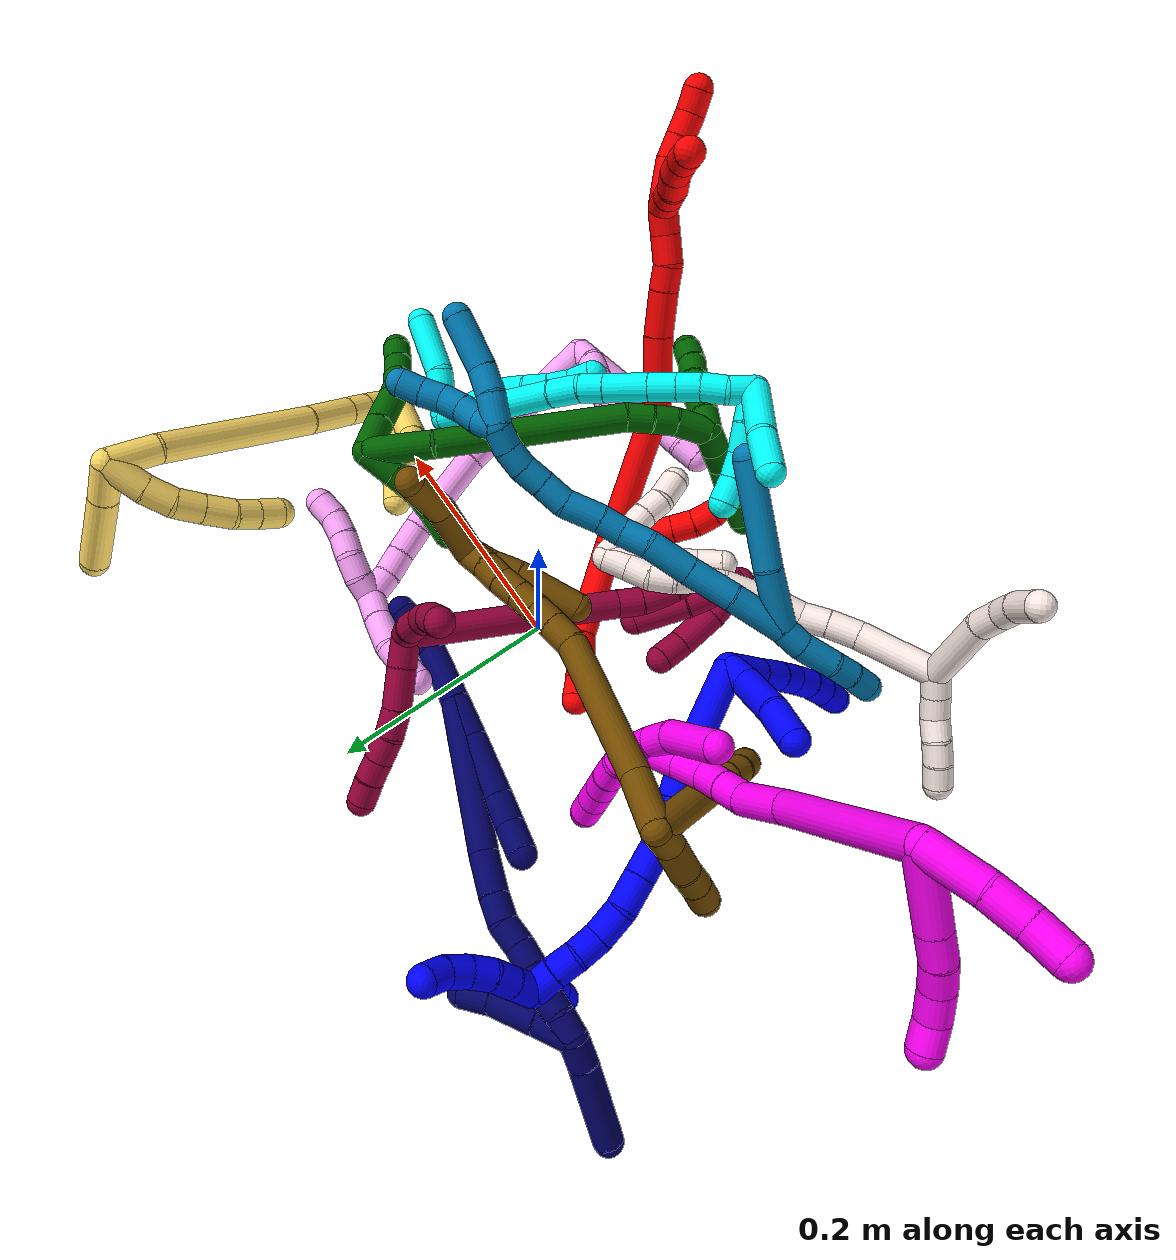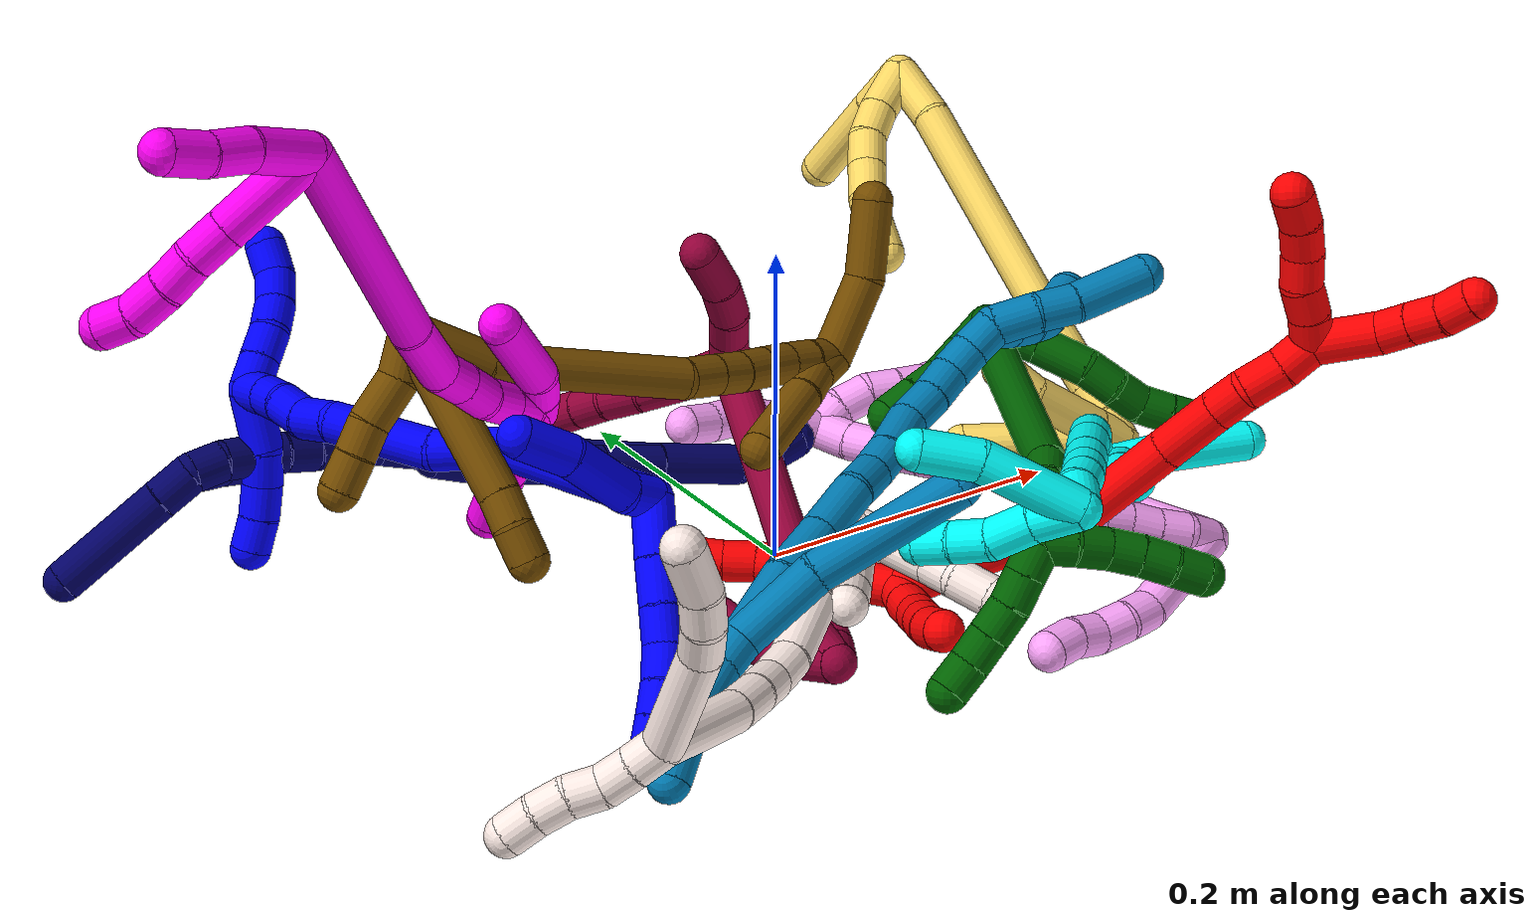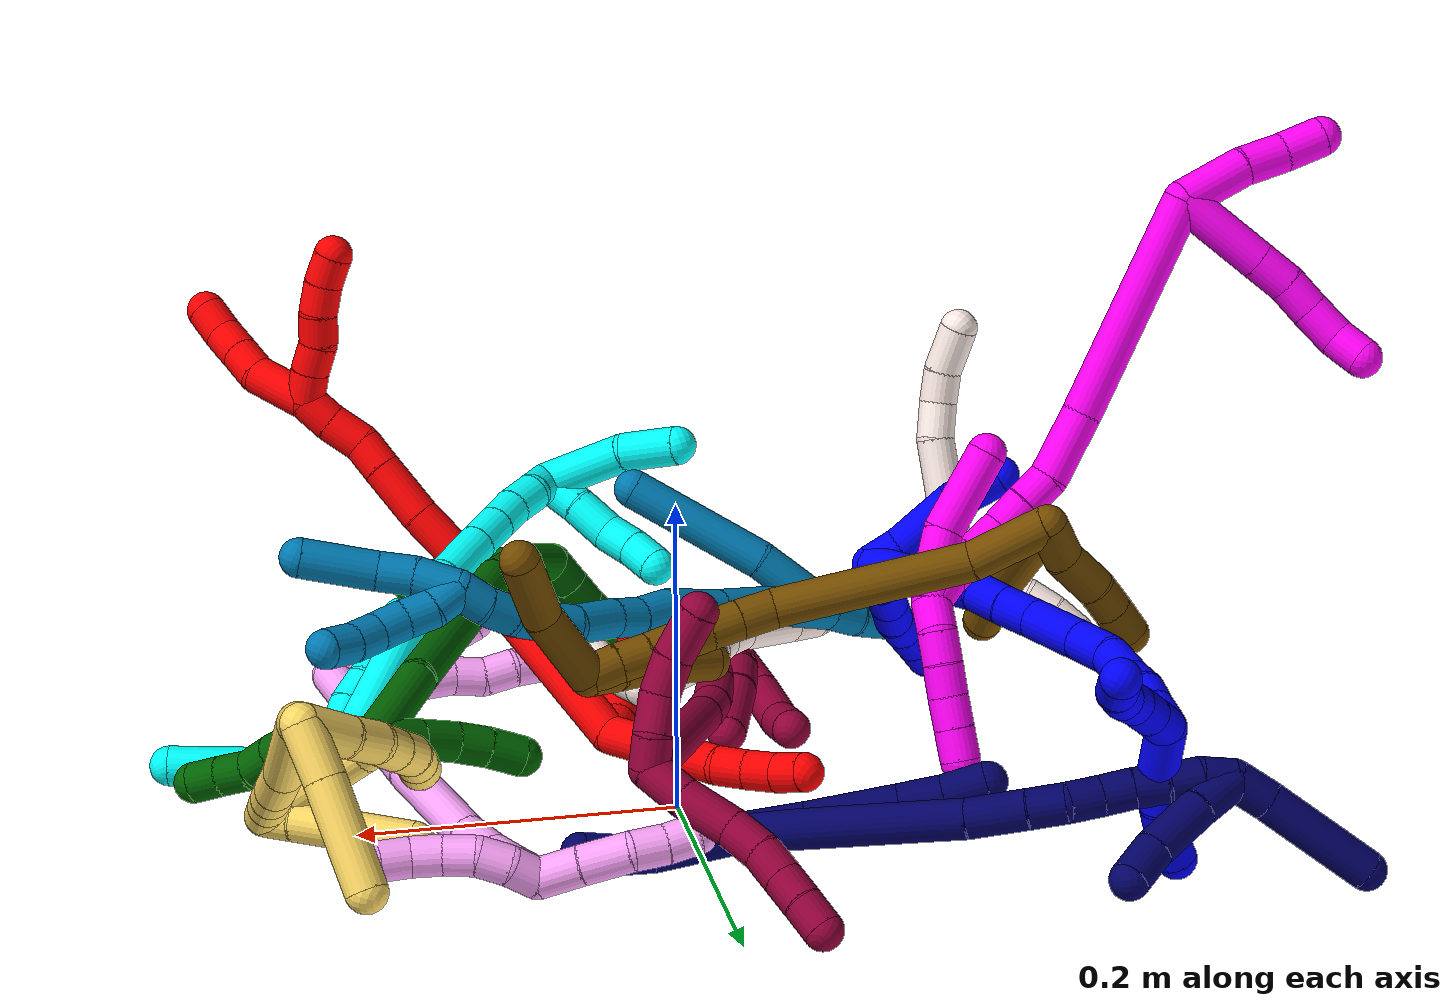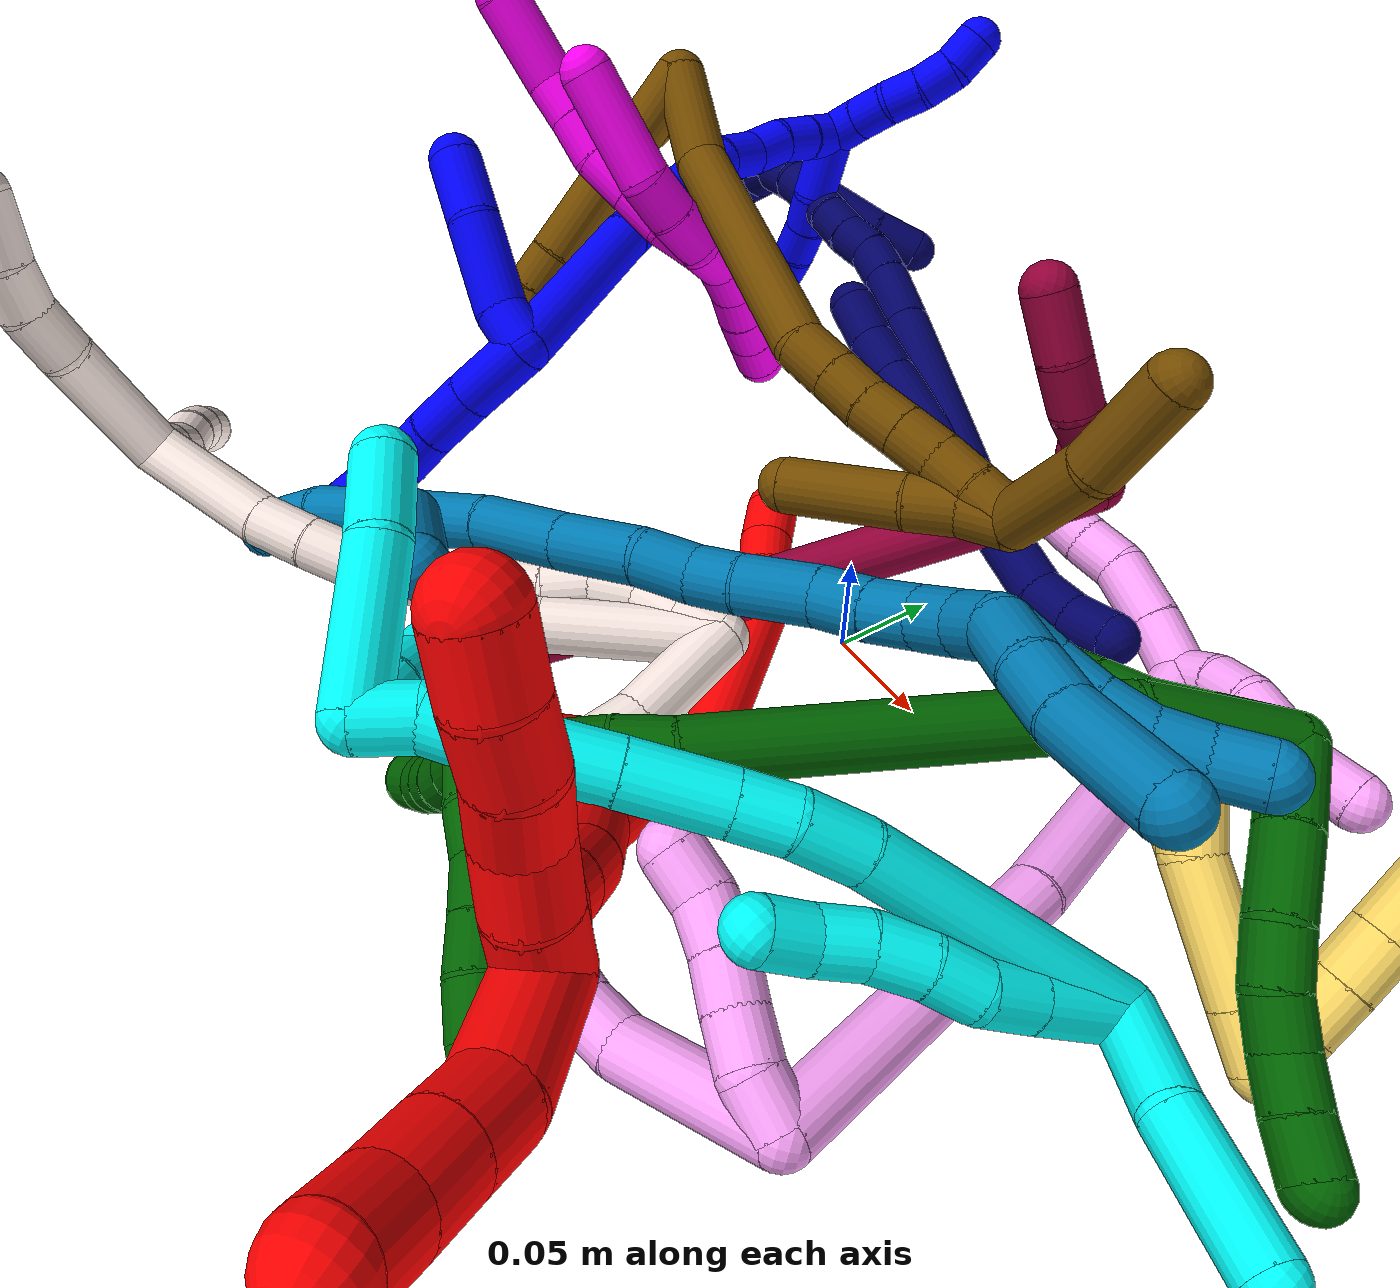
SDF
<sdf version="1.7">
 <world name="default">
  <plugin name="TubeGeneratorPlugin" filename="libtube_generator_plugin.so"/>
  <model name="photoneo_s_sensor">
   <static>1</static>
   <pose>0 0 2 1.57079 1.57079 3.14159</pose>
   <link name="link">
    <inertial><mass>0.1</mass></inertial>
    <sensor name="sensor" type="depth">
     <update_rate>30</update_rate>
     <camera>
      <horizontal_fov>1.22</horizontal_fov>
      <image><width>1920</width><height>1200</height><format>B8G8R8</format></image>
      <clip><near>0.1</near><far>4</far></clip>
      <depth_camera><output>points</output></depth_camera>
     </camera>
     <plugin name="camera_plugin" filename="libgazebo_ros_depth_camera.so">
      <baseline>0.2</baseline>
      <alwaysOn>1</alwaysOn>
      <updateRate>0.0</updateRate>
      <cameraName>camera_ir</cameraName>
      <imageTopicName>/camera/color/image_raw</imageTopicName>
      <cameraInfoTopicName>/camera/color/camera_info</cameraInfoTopicName>
      <depthImageTopicName>/camera/depth/image_raw</depthImageTopicName>
      <depthImageCameraInfoTopicName>/camera/depth/camera_info</depthImageCameraInfoTopicName>
      <pointCloudTopicName>/camera/depth/points</pointCloudTopicName>
      <frameName>fr_optical</frameName>
      <pointCloudCutoff>0.1</pointCloudCutoff>
      <pointCloudCutoffMax>2.0</pointCloudCutoffMax>
      <distortionK1>0</distortionK1>
      <distortionK2>0</distortionK2>
      <distortionK3>0</distortionK3>
      <distortionT1>0</distortionT1>
      <distortionT2>0</distortionT2>
      <CxPrime>0</CxPrime>
      <Cx>0</Cx>
      <Cy>0</Cy>
      <focalLength>0</focalLength>
      <hackBaseline>0</hackBaseline>
     </plugin>
    </sensor>
   </link>
  </model>
  <gravity>0 0 -9.8</gravity>
  <magnetic_field>6e-06 2.3e-05 -4.2e-05</magnetic_field>
  <atmosphere type="adiabatic"/>
  <physics name="default_physics" default="0" type="ode">
   <max_step_size>0.003</max_step_size>
   <real_time_factor>1</real_time_factor>
   <real_time_update_rate>1000</real_time_update_rate>
   <max_contacts>10000</max_contacts>
   <ode>
    <solver>
     <type>quick</type>
     <iters>100</iters>
     <sor>1.3</sor>
     <use_dynamic_moi_rescaling>0</use_dynamic_moi_rescaling>
    </solver>
    <constraints>
     <contact_max_correcting_vel>0</contact_max_correcting_vel>
     <contact_surface_layer>0.001</contact_surface_layer>
     <cfm>0</cfm>
     <erp>0.2</erp>
    </constraints>
   </ode>
  </physics>
  <scene><ambient>0.4 0.4 0.4 1</ambient><background>0.7 0.7 0.7 1</background><shadows>0</shadows></scene>
  <audio><device>default</device></audio>
  <spherical_coordinates>
   <surface_model>EARTH_WGS84</surface_model>
   <latitude_deg>0</latitude_deg>
   <longitude_deg>0</longitude_deg>
   <elevation>0</elevation>
   <heading_deg>0</heading_deg>
  </spherical_coordinates>
  <model name="bin">
   <static>1</static>
   <link name="bottom">
    <collision name="collision-bottom">
     <pose>0 0 -0.01 0 -0 0</pose>
     <geometry><box><size>0.8 0.6 0.02</size></box></geometry>
     <surface>
      <friction><ode><mu>100</mu><mu2>100</mu2></ode></friction>
      <contact><collide_bitmask>65535</collide_bitmask></contact>
     </surface>
    </collision>
   </link>
   <link name="west_wall">
    <collision name="collision-west_wall">
     <pose>-0.41 0 0.1 0 -0 0</pose>
     <geometry><box><size>0.02 0.6 0.2</size></box></geometry>
     <surface>
      <friction><ode><mu>100</mu><mu2>100</mu2></ode></friction>
      <contact><collide_bitmask>65535</collide_bitmask></contact>
     </surface>
    </collision>
   </link>
   <link name="east_wall">
    <collision name="collision-east_wall">
     <pose>0.41 0 0.1 0 -0 0</pose>
     <geometry><box><size>0.02 0.6 0.2</size></box></geometry>
     <surface>
      <friction><ode><mu>100</mu><mu2>100</mu2></ode></friction>
      <contact><collide_bitmask>65535</collide_bitmask></contact>
     </surface>
    </collision>
   </link>
   <link name="south_wall">
    <collision name="collision-south_wall">
     <pose>0 -0.31 0.1 0 -0 0</pose>
     <geometry><box><size>0.8 0.02 0.2</size></box></geometry>
     <surface>
      <friction><ode><mu>100</mu><mu2>100</mu2></ode></friction>
      <contact><collide_bitmask>65535</collide_bitmask></contact>
     </surface>
    </collision>
   </link>
   <link name="north_wall">
    <collision name="collision-north_wall">
     <pose>0 0.31 0.1 0 -0 0</pose>
     <geometry><box><size>0.8 0.02 0.2</size></box></geometry>
     <surface>
      <friction><ode><mu>100</mu><mu2>100</mu2></ode></friction>
      <contact><collide_bitmask>65535</collide_bitmask></contact>
     </surface>
    </collision>
   </link>
  </model>
  <model name="1">
   <static>0</static>
   <link name="1">
    <collision name="collision-cylinder-e_1_2_8">
     <pose>0.008655 -0.016107 0.003089 1.3813 0.485586 0.4038</pose>
     <geometry><cylinder><radius>0.0125</radius><length>0.037088</length></cylinder></geometry>
     <surface>
      <friction><ode><mu>1.16</mu><mu2>1.16</mu2><slip1>0</slip1><slip2>0</slip2></ode></friction>
      <contact><ode><kp>1e+06</kp><kd>1</kd><max_vel>0</max_vel><min_depth>0.001</min_depth></ode></contact>
     </surface>
    </collision>
    <visual name="visual-cylinder-e_1_2_8">
     <pose>0.008655 -0.016107 0.003089 1.3813 0.485586 0.4038</pose>
     <geometry><cylinder><radius>0.0125</radius><length>0.037088</length></cylinder></geometry>
     <material><ambient>0 0 1 1</ambient></material>
    </visual>
    <collision name="collision-cylinder-e_2_8_9">
     <pose>0.023556 -0.044425 0.008883 1.35281 0.463161 0.374158</pose>
     <geometry><cylinder><radius>0.0125</radius><length>0.02796</length></cylinder></geometry>
     <surface>
      <friction><ode><mu>1.16</mu><mu2>1.16</mu2><slip1>0</slip1><slip2>0</slip2></ode></friction>
      <contact><ode><kp>1e+06</kp><kd>1</kd><max_vel>0</max_vel><min_depth>0.001</min_depth></ode></contact>
     </surface>
    </collision>
    <visual name="visual-cylinder-e_2_8_9">
     <pose>0.023556 -0.044425 0.008883 1.35281 0.463161 0.374158</pose>
     <geometry><cylinder><radius>0.0125</radius><length>0.02796</length></cylinder></geometry>
     <material><ambient>0 0 1 1</ambient></material>
    </visual>
    <collision name="collision-cylinder-e_3_9_10">
     <pose>0.035101 -0.066166 0.01447 1.27716 0.489095 0.366335</pose>
     <geometry><cylinder><radius>0.0125</radius><length>0.022556</length></cylinder></geometry>
     <surface>
      <friction><ode><mu>1.16</mu><mu2>1.16</mu2><slip1>0</slip1><slip2>0</slip2></ode></friction>
      <contact><ode><kp>1e+06</kp><kd>1</kd><max_vel>0</max_vel><min_depth>0.001</min_depth></ode></contact>
     </surface>
    </collision>
    <visual name="visual-cylinder-e_3_9_10">
     <pose>0.035101 -0.066166 0.01447 1.27716 0.489095 0.366335</pose>
     <geometry><cylinder><radius>0.0125</radius><length>0.022556</length></cylinder></geometry>
     <material><ambient>0 0 1 1</ambient></material>
    </visual>
    <collision name="collision-cylinder-e_4_10_11">
     <pose>0.046261 -0.084975 0.018119 1.48826 0.561829 0.519328</pose>
     <geometry><cylinder><radius>0.0125</radius><length>0.022005</length></cylinder></geometry>
     <surface>
      <friction><ode><mu>1.16</mu><mu2>1.16</mu2><slip1>0</slip1><slip2>0</slip2></ode></friction>
      <contact><ode><kp>1e+06</kp><kd>1</kd><max_vel>0</max_vel><min_depth>0.001</min_depth></ode></contact>
     </surface>
    </collision>
    <visual name="visual-cylinder-e_4_10_11">
     <pose>0.046261 -0.084975 0.018119 1.48826 0.561829 0.519328</pose>
     <geometry><cylinder><radius>0.0125</radius><length>0.022005</length></cylinder></geometry>
     <material><ambient>0 0 1 1</ambient></material>
    </visual>
    <collision name="collision-cylinder-e_5_11_12">
     <pose>0.058596 -0.101885 0.020102 1.41286 0.697409 0.60165</pose>
     <geometry><cylinder><radius>0.0125</radius><length>0.02016</length></cylinder></geometry>
     <surface>
      <friction><ode><mu>1.16</mu><mu2>1.16</mu2><slip1>0</slip1><slip2>0</slip2></ode></friction>
      <contact><ode><kp>1e+06</kp><kd>1</kd><max_vel>0</max_vel><min_depth>0.001</min_depth></ode></contact>
     </surface>
    </collision>
    <visual name="visual-cylinder-e_5_11_12">
     <pose>0.058596 -0.101885 0.020102 1.41286 0.697409 0.60165</pose>
     <geometry><cylinder><radius>0.0125</radius><length>0.02016</length></cylinder></geometry>
     <material><ambient>0 0 1 1</ambient></material>
    </visual>
    <collision name="collision-cylinder-e_6_12_6">
     <pose>0.071869 -0.116844 0.022858 1.36355 0.737153 0.607521</pose>
     <geometry><cylinder><radius>0.0125</radius><length>0.020231</length></cylinder></geometry>
     <surface>
      <friction><ode><mu>1.16</mu><mu2>1.16</mu2><slip1>0</slip1><slip2>0</slip2></ode></friction>
      <contact><ode><kp>1e+06</kp><kd>1</kd><max_vel>0</max_vel><min_depth>0.001</min_depth></ode></contact>
     </surface>
    </collision>
    <visual name="visual-cylinder-e_6_12_6">
     <pose>0.071869 -0.116844 0.022858 1.36355 0.737153 0.607521</pose>
     <geometry><cylinder><radius>0.0125</radius><length>0.020231</length></cylinder></geometry>
     <material><ambient>0 0 1 1</ambient></material>
    </visual>
    <collision name="collision-cylinder-e_1_2_13">
     <pose>0.004882 0.000385 -0.009337 -3.10043 0.481399 -2.97426</pose>
     <geometry><cylinder><radius>0.0125</radius><length>0.021086</length></cylinder></geometry>
     <surface>
      <friction><ode><mu>1.16</mu><mu2>1.16</mu2><slip1>0</slip1><slip2>0</slip2></ode></friction>
      <contact><ode><kp>1e+06</kp><kd>1</kd><max_vel>0</max_vel><min_depth>0.001</min_depth></ode></contact>
     </surface>
    </collision>
    <visual name="visual-cylinder-e_1_2_13">
     <pose>0.004882 0.000385 -0.009337 -3.10043 0.481399 -2.97426</pose>
     <geometry><cylinder><radius>0.0125</radius><length>0.021086</length></cylinder></geometry>
     <material><ambient>0 0 1 1</ambient></material>
    </visual>
    <collision name="collision-cylinder-e_2_13_14">
     <pose>0.016165 0.007532 -0.039169 -2.82286 0.28835 -1.46922</pose>
     <geometry><cylinder><radius>0.0125</radius><length>0.045023</length></cylinder></geometry>
     <surface>
      <friction><ode><mu>1.16</mu><mu2>1.16</mu2><slip1>0</slip1><slip2>0</slip2></ode></friction>
      <contact><ode><kp>1e+06</kp><kd>1</kd><max_vel>0</max_vel><min_depth>0.001</min_depth></ode></contact>
     </surface>
    </collision>
    <visual name="visual-cylinder-e_2_13_14">
     <pose>0.016165 0.007532 -0.039169 -2.82286 0.28835 -1.46922</pose>
     <geometry><cylinder><radius>0.0125</radius><length>0.045023</length></cylinder></geometry>
     <material><ambient>0 0 1 1</ambient></material>
    </visual>
    <collision name="collision-cylinder-e_3_14_5">
     <pose>0.030643 0.019355 -0.073675 -2.79506 0.496777 -1.93352</pose>
     <geometry><cylinder><radius>0.0125</radius><length>0.033891</length></cylinder></geometry>
     <surface>
      <friction><ode><mu>1.16</mu><mu2>1.16</mu2><slip1>0</slip1><slip2>0</slip2></ode></friction>
      <contact><ode><kp>1e+06</kp><kd>1</kd><max_vel>0</max_vel><min_depth>0.001</min_depth></ode></contact>
     </surface>
    </collision>
    <visual name="visual-cylinder-e_3_14_5">
     <pose>0.030643 0.019355 -0.073675 -2.79506 0.496777 -1.93352</pose>
     <geometry><cylinder><radius>0.0125</radius><length>0.033891</length></cylinder></geometry>
     <material><ambient>0 0 1 1</ambient></material>
    </visual>
    <collision name="collision-cylinder-e_1_2_15">
     <pose>0.02729 0.038267 -0.006441 -1.73755 0.612906 -0.716013</pose>
     <geometry><cylinder><radius>0.0125</radius><length>0.094881</length></cylinder></geometry>
     <surface>
      <friction><ode><mu>1.16</mu><mu2>1.16</mu2><slip1>0</slip1><slip2>0</slip2></ode></friction>
      <contact><ode><kp>1e+06</kp><kd>1</kd><max_vel>0</max_vel><min_depth>0.001</min_depth></ode></contact>
     </surface>
    </collision>
    <visual name="visual-cylinder-e_1_2_15">
     <pose>0.02729 0.038267 -0.006441 -1.73755 0.612906 -0.716013</pose>
     <geometry><cylinder><radius>0.0125</radius><length>0.094881</length></cylinder></geometry>
     <material><ambient>0 0 1 1</ambient></material>
    </visual>
    <collision name="collision-cylinder-e_2_15_16">
     <pose>0.062965 0.083185 -0.013011 -1.59024 0.900148 -0.915477</pose>
     <geometry><cylinder><radius>0.0125</radius><length>0.021406</length></cylinder></geometry>
     <surface>
      <friction><ode><mu>1.16</mu><mu2>1.16</mu2><slip1>0</slip1><slip2>0</slip2></ode></friction>
      <contact><ode><kp>1e+06</kp><kd>1</kd><max_vel>0</max_vel><min_depth>0.001</min_depth></ode></contact>
     </surface>
    </collision>
    <visual name="visual-cylinder-e_2_15_16">
     <pose>0.062965 0.083185 -0.013011 -1.59024 0.900148 -0.915477</pose>
     <geometry><cylinder><radius>0.0125</radius><length>0.021406</length></cylinder></geometry>
     <material><ambient>0 0 1 1</ambient></material>
    </visual>
    <collision name="collision-cylinder-e_3_16_17">
     <pose>0.080868 0.096573 -0.013832 -1.67307 0.952372 -1.03828</pose>
     <geometry><cylinder><radius>0.0125</radius><length>0.023365</length></cylinder></geometry>
     <surface>
      <friction><ode><mu>1.16</mu><mu2>1.16</mu2><slip1>0</slip1><slip2>0</slip2></ode></friction>
      <contact><ode><kp>1e+06</kp><kd>1</kd><max_vel>0</max_vel><min_depth>0.001</min_depth></ode></contact>
     </surface>
    </collision>
    <visual name="visual-cylinder-e_3_16_17">
     <pose>0.080868 0.096573 -0.013832 -1.67307 0.952372 -1.03828</pose>
     <geometry><cylinder><radius>0.0125</radius><length>0.023365</length></cylinder></geometry>
     <material><ambient>0 0 1 1</ambient></material>
    </visual>
    <collision name="collision-cylinder-e_4_17_18">
     <pose>0.103056 0.120855 -0.014511 -1.5701 0.625384 -0.624977</pose>
     <geometry><cylinder><radius>0.0125</radius><length>0.04328</length></cylinder></geometry>
     <surface>
      <friction><ode><mu>1.16</mu><mu2>1.16</mu2><slip1>0</slip1><slip2>0</slip2></ode></friction>
      <contact><ode><kp>1e+06</kp><kd>1</kd><max_vel>0</max_vel><min_depth>0.001</min_depth></ode></contact>
     </surface>
    </collision>
    <visual name="visual-cylinder-e_4_17_18">
     <pose>0.103056 0.120855 -0.014511 -1.5701 0.625384 -0.624977</pose>
     <geometry><cylinder><radius>0.0125</radius><length>0.04328</length></cylinder></geometry>
     <material><ambient>0 0 1 1</ambient></material>
    </visual>
    <collision name="collision-cylinder-e_5_18_19">
     <pose>0.123851 0.149577 -0.014394 -1.56145 0.628656 -0.623181</pose>
     <geometry><cylinder><radius>0.0125</radius><length>0.027641</length></cylinder></geometry>
     <surface>
      <friction><ode><mu>1.16</mu><mu2>1.16</mu2><slip1>0</slip1><slip2>0</slip2></ode></friction>
      <contact><ode><kp>1e+06</kp><kd>1</kd><max_vel>0</max_vel><min_depth>0.001</min_depth></ode></contact>
     </surface>
    </collision>
    <visual name="visual-cylinder-e_5_18_19">
     <pose>0.123851 0.149577 -0.014394 -1.56145 0.628656 -0.623181</pose>
     <geometry><cylinder><radius>0.0125</radius><length>0.027641</length></cylinder></geometry>
     <material><ambient>0 0 1 1</ambient></material>
    </visual>
    <collision name="collision-cylinder-e_6_19_20">
     <pose>0.139356 0.17101 -0.010543 -1.22053 0.59425 -0.421873</pose>
     <geometry><cylinder><radius>0.0125</radius><length>0.026354</length></cylinder></geometry>
     <surface>
      <friction><ode><mu>1.16</mu><mu2>1.16</mu2><slip1>0</slip1><slip2>0</slip2></ode></friction>
      <contact><ode><kp>1e+06</kp><kd>1</kd><max_vel>0</max_vel><min_depth>0.001</min_depth></ode></contact>
     </surface>
    </collision>
    <visual name="visual-cylinder-e_6_19_20">
     <pose>0.139356 0.17101 -0.010543 -1.22053 0.59425 -0.421873</pose>
     <geometry><cylinder><radius>0.0125</radius><length>0.026354</length></cylinder></geometry>
     <material><ambient>0 0 1 1</ambient></material>
    </visual>
    <collision name="collision-cylinder-e_7_20_21">
     <pose>0.150062 0.19155 -0.004977 -1.39567 0.308444 -0.259267</pose>
     <geometry><cylinder><radius>0.0125</radius><length>0.021925</length></cylinder></geometry>
     <surface>
      <friction><ode><mu>1.16</mu><mu2>1.16</mu2><slip1>0</slip1><slip2>0</slip2></ode></friction>
      <contact><ode><kp>1e+06</kp><kd>1</kd><max_vel>0</max_vel><min_depth>0.001</min_depth></ode></contact>
     </surface>
    </collision>
    <visual name="visual-cylinder-e_7_20_21">
     <pose>0.150062 0.19155 -0.004977 -1.39567 0.308444 -0.259267</pose>
     <geometry><cylinder><radius>0.0125</radius><length>0.021925</length></cylinder></geometry>
     <material><ambient>0 0 1 1</ambient></material>
    </visual>
    <collision name="collision-cylinder-e_8_21_22">
     <pose>0.156865 0.210532 0.000629 -1.16021 0.351253 -0.231538</pose>
     <geometry><cylinder><radius>0.0125</radius><length>0.020204</length></cylinder></geometry>
     <surface>
      <friction><ode><mu>1.16</mu><mu2>1.16</mu2><slip1>0</slip1><slip2>0</slip2></ode></friction>
      <contact><ode><kp>1e+06</kp><kd>1</kd><max_vel>0</max_vel><min_depth>0.001</min_depth></ode></contact>
     </surface>
    </collision>
    <visual name="visual-cylinder-e_8_21_22">
     <pose>0.156865 0.210532 0.000629 -1.16021 0.351253 -0.231538</pose>
     <geometry><cylinder><radius>0.0125</radius><length>0.020204</length></cylinder></geometry>
     <material><ambient>0 0 1 1</ambient></material>
    </visual>
    <collision name="collision-cylinder-e_9_22_1">
     <pose>0.164851 0.227906 0.008162 -1.16317 0.445202 -0.295456</pose>
     <geometry><cylinder><radius>0.0125</radius><length>0.020945</length></cylinder></geometry>
     <surface>
      <friction><ode><mu>1.16</mu><mu2>1.16</mu2><slip1>0</slip1><slip2>0</slip2></ode></friction>
      <contact><ode><kp>1e+06</kp><kd>1</kd><max_vel>0</max_vel><min_depth>0.001</min_depth></ode></contact>
     </surface>
    </collision>
    <visual name="visual-cylinder-e_9_22_1">
     <pose>0.164851 0.227906 0.008162 -1.16317 0.445202 -0.295456</pose>
     <geometry><cylinder><radius>0.0125</radius><length>0.020945</length></cylinder></geometry>
     <material><ambient>0 0 1 1</ambient></material>
    </visual>
    <collision name="collision-cylinder-e_1_1_23">
     <pose>0.162226 0.243589 0.011771 -1.59047 -0.794451 0.808586</pose>
     <geometry><cylinder><radius>0.0125</radius><length>0.02</length></cylinder></geometry>
     <surface>
      <friction><ode><mu>1.16</mu><mu2>1.16</mu2><slip1>0</slip1><slip2>0</slip2></ode></friction>
      <contact><ode><kp>1e+06</kp><kd>1</kd><max_vel>0</max_vel><min_depth>0.001</min_depth></ode></contact>
     </surface>
    </collision>
    <visual name="visual-cylinder-e_1_1_23">
     <pose>0.162226 0.243589 0.011771 -1.59047 -0.794451 0.808586</pose>
     <geometry><cylinder><radius>0.0125</radius><length>0.02</length></cylinder></geometry>
     <material><ambient>0 0 1 1</ambient></material>
    </visual>
    <collision name="collision-cylinder-e_2_23_24">
     <pose>0.147967 0.25761 0.011763 -1.55225 -0.792945 0.779817</pose>
     <geometry><cylinder><radius>0.0125</radius><length>0.02</length></cylinder></geometry>
     <surface>
      <friction><ode><mu>1.16</mu><mu2>1.16</mu2><slip1>0</slip1><slip2>0</slip2></ode></friction>
      <contact><ode><kp>1e+06</kp><kd>1</kd><max_vel>0</max_vel><min_depth>0.001</min_depth></ode></contact>
     </surface>
    </collision>
    <visual name="visual-cylinder-e_2_23_24">
     <pose>0.147967 0.25761 0.011763 -1.55225 -0.792945 0.779817</pose>
     <geometry><cylinder><radius>0.0125</radius><length>0.02</length></cylinder></geometry>
     <material><ambient>0 0 1 1</ambient></material>
    </visual>
    <collision name="collision-cylinder-e_3_24_25">
     <pose>0.13546 0.272967 0.013105 -1.42649 -0.568378 0.495066</pose>
     <geometry><cylinder><radius>0.0125</radius><length>0.02</length></cylinder></geometry>
     <surface>
      <friction><ode><mu>1.16</mu><mu2>1.16</mu2><slip1>0</slip1><slip2>0</slip2></ode></friction>
      <contact><ode><kp>1e+06</kp><kd>1</kd><max_vel>0</max_vel><min_depth>0.001</min_depth></ode></contact>
     </surface>
    </collision>
    <visual name="visual-cylinder-e_3_24_25">
     <pose>0.13546 0.272967 0.013105 -1.42649 -0.568378 0.495066</pose>
     <geometry><cylinder><radius>0.0125</radius><length>0.02</length></cylinder></geometry>
     <material><ambient>0 0 1 1</ambient></material>
    </visual>
    <collision name="collision-cylinder-e_4_25_26">
     <pose>0.125707 0.290299 0.014085 -1.59658 -0.45225 0.463652</pose>
     <geometry><cylinder><radius>0.0125</radius><length>0.02</length></cylinder></geometry>
     <surface>
      <friction><ode><mu>1.16</mu><mu2>1.16</mu2><slip1>0</slip1><slip2>0</slip2></ode></friction>
      <contact><ode><kp>1e+06</kp><kd>1</kd><max_vel>0</max_vel><min_depth>0.001</min_depth></ode></contact>
     </surface>
    </collision>
    <visual name="visual-cylinder-e_4_25_26">
     <pose>0.125707 0.290299 0.014085 -1.59658 -0.45225 0.463652</pose>
     <geometry><cylinder><radius>0.0125</radius><length>0.02</length></cylinder></geometry>
     <material><ambient>0 0 1 1</ambient></material>
    </visual>
    <collision name="collision-cylinder-e_5_26_4">
     <pose>0.118854 0.308525 0.010929 -1.87749 -0.250954 0.341171</pose>
     <geometry><cylinder><radius>0.0125</radius><length>0.02</length></cylinder></geometry>
     <surface>
      <friction><ode><mu>1.16</mu><mu2>1.16</mu2><slip1>0</slip1><slip2>0</slip2></ode></friction>
      <contact><ode><kp>1e+06</kp><kd>1</kd><max_vel>0</max_vel><min_depth>0.001</min_depth></ode></contact>
     </surface>
    </collision>
    <visual name="visual-cylinder-e_5_26_4">
     <pose>0.118854 0.308525 0.010929 -1.87749 -0.250954 0.341171</pose>
     <geometry><cylinder><radius>0.0125</radius><length>0.02</length></cylinder></geometry>
     <material><ambient>0 0 1 1</ambient></material>
    </visual>
    <collision name="collision-cylinder-e_1_1_27">
     <pose>0.176437 0.224711 0.024538 0.754485 0.387588 0.155209</pose>
     <geometry><cylinder><radius>0.0125</radius><length>0.037445</length></cylinder></geometry>
     <surface>
      <friction><ode><mu>1.16</mu><mu2>1.16</mu2><slip1>0</slip1><slip2>0</slip2></ode></friction>
      <contact><ode><kp>1e+06</kp><kd>1</kd><max_vel>0</max_vel><min_depth>0.001</min_depth></ode></contact>
     </surface>
    </collision>
    <visual name="visual-cylinder-e_1_1_27">
     <pose>0.176437 0.224711 0.024538 0.754485 0.387588 0.155209</pose>
     <geometry><cylinder><radius>0.0125</radius><length>0.037445</length></cylinder></geometry>
     <material><ambient>0 0 1 1</ambient></material>
    </visual>
    <collision name="collision-cylinder-e_2_27_28">
     <pose>0.189789 0.208007 0.044223 0.600545 0.633068 0.202149</pose>
     <geometry><cylinder><radius>0.0125</radius><length>0.021213</length></cylinder></geometry>
     <surface>
      <friction><ode><mu>1.16</mu><mu2>1.16</mu2><slip1>0</slip1><slip2>0</slip2></ode></friction>
      <contact><ode><kp>1e+06</kp><kd>1</kd><max_vel>0</max_vel><min_depth>0.001</min_depth></ode></contact>
     </surface>
    </collision>
    <visual name="visual-cylinder-e_2_27_28">
     <pose>0.189789 0.208007 0.044223 0.600545 0.633068 0.202149</pose>
     <geometry><cylinder><radius>0.0125</radius><length>0.021213</length></cylinder></geometry>
     <material><ambient>0 0 1 1</ambient></material>
    </visual>
    <collision name="collision-cylinder-e_3_28_29">
     <pose>0.202897 0.197685 0.057036 0.761484 0.709662 0.294467</pose>
     <geometry><cylinder><radius>0.0125</radius><length>0.020974</length></cylinder></geometry>
     <surface>
      <friction><ode><mu>1.16</mu><mu2>1.16</mu2><slip1>0</slip1><slip2>0</slip2></ode></friction>
      <contact><ode><kp>1e+06</kp><kd>1</kd><max_vel>0</max_vel><min_depth>0.001</min_depth></ode></contact>
     </surface>
    </collision>
    <visual name="visual-cylinder-e_3_28_29">
     <pose>0.202897 0.197685 0.057036 0.761484 0.709662 0.294467</pose>
     <geometry><cylinder><radius>0.0125</radius><length>0.020974</length></cylinder></geometry>
     <material><ambient>0 0 1 1</ambient></material>
    </visual>
    <collision name="collision-cylinder-e_4_29_3">
     <pose>0.217462 0.187416 0.067385 0.805715 0.862158 0.387103</pose>
     <geometry><cylinder><radius>0.0125</radius><length>0.020368</length></cylinder></geometry>
     <surface>
      <friction><ode><mu>1.16</mu><mu2>1.16</mu2><slip1>0</slip1><slip2>0</slip2></ode></friction>
      <contact><ode><kp>1e+06</kp><kd>1</kd><max_vel>0</max_vel><min_depth>0.001</min_depth></ode></contact>
     </surface>
    </collision>
    <visual name="visual-cylinder-e_4_29_3">
     <pose>0.217462 0.187416 0.067385 0.805715 0.862158 0.387103</pose>
     <geometry><cylinder><radius>0.0125</radius><length>0.020368</length></cylinder></geometry>
     <material><ambient>0 0 1 1</ambient></material>
    </visual>
    <collision name="collision-sphere-3">
     <pose>0.225194 0.182635 0.071975 0 -0 0</pose>
     <geometry><sphere><radius>0.0125</radius></sphere></geometry>
     <surface>
      <friction><ode><mu>1.16</mu><mu2>1.16</mu2><slip1>0</slip1><slip2>0</slip2></ode></friction>
      <contact><ode><kp>1e+06</kp><kd>1</kd><max_vel>0</max_vel><min_depth>0.001</min_depth></ode></contact>
     </surface>
    </collision>
    <visual name="visual-sphere-3">
     <pose>0.225194 0.182635 0.071975 0 -0 0</pose>
     <geometry><sphere><radius>0.0125</radius></sphere></geometry>
     <material><ambient>0 0 1 1</ambient></material>
    </visual>
    <collision name="collision-sphere-29">
     <pose>0.20973 0.192196 0.062794 0 -0 0</pose>
     <geometry><sphere><radius>0.0125</radius></sphere></geometry>
     <surface>
      <friction><ode><mu>1.16</mu><mu2>1.16</mu2><slip1>0</slip1><slip2>0</slip2></ode></friction>
      <contact><ode><kp>1e+06</kp><kd>1</kd><max_vel>0</max_vel><min_depth>0.001</min_depth></ode></contact>
     </surface>
    </collision>
    <visual name="visual-sphere-29">
     <pose>0.20973 0.192196 0.062794 0 -0 0</pose>
     <geometry><sphere><radius>0.0125</radius></sphere></geometry>
     <material><ambient>0 0 1 1</ambient></material>
    </visual>
    <collision name="collision-sphere-28">
     <pose>0.196064 0.203174 0.051278 0 -0 0</pose>
     <geometry><sphere><radius>0.0125</radius></sphere></geometry>
     <surface>
      <friction><ode><mu>1.16</mu><mu2>1.16</mu2><slip1>0</slip1><slip2>0</slip2></ode></friction>
      <contact><ode><kp>1e+06</kp><kd>1</kd><max_vel>0</max_vel><min_depth>0.001</min_depth></ode></contact>
     </surface>
    </collision>
    <visual name="visual-sphere-28">
     <pose>0.196064 0.203174 0.051278 0 -0 0</pose>
     <geometry><sphere><radius>0.0125</radius></sphere></geometry>
     <material><ambient>0 0 1 1</ambient></material>
    </visual>
    <collision name="collision-sphere-27">
     <pose>0.183513 0.212839 0.037168 0 -0 0</pose>
     <geometry><sphere><radius>0.0125</radius></sphere></geometry>
     <surface>
      <friction><ode><mu>1.16</mu><mu2>1.16</mu2><slip1>0</slip1><slip2>0</slip2></ode></friction>
      <contact><ode><kp>1e+06</kp><kd>1</kd><max_vel>0</max_vel><min_depth>0.001</min_depth></ode></contact>
     </surface>
    </collision>
    <visual name="visual-sphere-27">
     <pose>0.183513 0.212839 0.037168 0 -0 0</pose>
     <geometry><sphere><radius>0.0125</radius></sphere></geometry>
     <material><ambient>0 0 1 1</ambient></material>
    </visual>
    <collision name="collision-sphere-4">
     <pose>0.116371 0.31776 0.008004 0 -0 0</pose>
     <geometry><sphere><radius>0.0125</radius></sphere></geometry>
     <surface>
      <friction><ode><mu>1.16</mu><mu2>1.16</mu2><slip1>0</slip1><slip2>0</slip2></ode></friction>
      <contact><ode><kp>1e+06</kp><kd>1</kd><max_vel>0</max_vel><min_depth>0.001</min_depth></ode></contact>
     </surface>
    </collision>
    <visual name="visual-sphere-4">
     <pose>0.116371 0.31776 0.008004 0 -0 0</pose>
     <geometry><sphere><radius>0.0125</radius></sphere></geometry>
     <material><ambient>0 0 1 1</ambient></material>
    </visual>
    <collision name="collision-sphere-26">
     <pose>0.121338 0.29929 0.013853 0 -0 0</pose>
     <geometry><sphere><radius>0.0125</radius></sphere></geometry>
     <surface>
      <friction><ode><mu>1.16</mu><mu2>1.16</mu2><slip1>0</slip1><slip2>0</slip2></ode></friction>
      <contact><ode><kp>1e+06</kp><kd>1</kd><max_vel>0</max_vel><min_depth>0.001</min_depth></ode></contact>
     </surface>
    </collision>
    <visual name="visual-sphere-26">
     <pose>0.121338 0.29929 0.013853 0 -0 0</pose>
     <geometry><sphere><radius>0.0125</radius></sphere></geometry>
     <material><ambient>0 0 1 1</ambient></material>
    </visual>
    <collision name="collision-sphere-25">
     <pose>0.130077 0.281307 0.014317 0 -0 0</pose>
     <geometry><sphere><radius>0.0125</radius></sphere></geometry>
     <surface>
      <friction><ode><mu>1.16</mu><mu2>1.16</mu2><slip1>0</slip1><slip2>0</slip2></ode></friction>
      <contact><ode><kp>1e+06</kp><kd>1</kd><max_vel>0</max_vel><min_depth>0.001</min_depth></ode></contact>
     </surface>
    </collision>
    <visual name="visual-sphere-25">
     <pose>0.130077 0.281307 0.014317 0 -0 0</pose>
     <geometry><sphere><radius>0.0125</radius></sphere></geometry>
     <material><ambient>0 0 1 1</ambient></material>
    </visual>
    <collision name="collision-sphere-24">
     <pose>0.140843 0.264627 0.011893 0 -0 0</pose>
     <geometry><sphere><radius>0.0125</radius></sphere></geometry>
     <surface>
      <friction><ode><mu>1.16</mu><mu2>1.16</mu2><slip1>0</slip1><slip2>0</slip2></ode></friction>
      <contact><ode><kp>1e+06</kp><kd>1</kd><max_vel>0</max_vel><min_depth>0.001</min_depth></ode></contact>
     </surface>
    </collision>
    <visual name="visual-sphere-24">
     <pose>0.140843 0.264627 0.011893 0 -0 0</pose>
     <geometry><sphere><radius>0.0125</radius></sphere></geometry>
     <material><ambient>0 0 1 1</ambient></material>
    </visual>
    <collision name="collision-sphere-23">
     <pose>0.155091 0.250594 0.011633 0 -0 0</pose>
     <geometry><sphere><radius>0.0125</radius></sphere></geometry>
     <surface>
      <friction><ode><mu>1.16</mu><mu2>1.16</mu2><slip1>0</slip1><slip2>0</slip2></ode></friction>
      <contact><ode><kp>1e+06</kp><kd>1</kd><max_vel>0</max_vel><min_depth>0.001</min_depth></ode></contact>
     </surface>
    </collision>
    <visual name="visual-sphere-23">
     <pose>0.155091 0.250594 0.011633 0 -0 0</pose>
     <geometry><sphere><radius>0.0125</radius></sphere></geometry>
     <material><ambient>0 0 1 1</ambient></material>
    </visual>
    <collision name="collision-sphere-1">
     <pose>0.169361 0.236583 0.011908 0 -0 0</pose>
     <geometry><sphere><radius>0.0125</radius></sphere></geometry>
     <surface>
      <friction><ode><mu>1.16</mu><mu2>1.16</mu2><slip1>0</slip1><slip2>0</slip2></ode></friction>
      <contact><ode><kp>1e+06</kp><kd>1</kd><max_vel>0</max_vel><min_depth>0.001</min_depth></ode></contact>
     </surface>
    </collision>
    <visual name="visual-sphere-1">
     <pose>0.169361 0.236583 0.011908 0 -0 0</pose>
     <geometry><sphere><radius>0.0125</radius></sphere></geometry>
     <material><ambient>0 0 1 1</ambient></material>
    </visual>
    <collision name="collision-sphere-22">
     <pose>0.160341 0.219229 0.004415 0 -0 0</pose>
     <geometry><sphere><radius>0.0125</radius></sphere></geometry>
     <surface>
      <friction><ode><mu>1.16</mu><mu2>1.16</mu2><slip1>0</slip1><slip2>0</slip2></ode></friction>
      <contact><ode><kp>1e+06</kp><kd>1</kd><max_vel>0</max_vel><min_depth>0.001</min_depth></ode></contact>
     </surface>
    </collision>
    <visual name="visual-sphere-22">
     <pose>0.160341 0.219229 0.004415 0 -0 0</pose>
     <geometry><sphere><radius>0.0125</radius></sphere></geometry>
     <material><ambient>0 0 1 1</ambient></material>
    </visual>
    <collision name="collision-sphere-21">
     <pose>0.15339 0.201836 -0.003157 0 -0 0</pose>
     <geometry><sphere><radius>0.0125</radius></sphere></geometry>
     <surface>
      <friction><ode><mu>1.16</mu><mu2>1.16</mu2><slip1>0</slip1><slip2>0</slip2></ode></friction>
      <contact><ode><kp>1e+06</kp><kd>1</kd><max_vel>0</max_vel><min_depth>0.001</min_depth></ode></contact>
     </surface>
    </collision>
    <visual name="visual-sphere-21">
     <pose>0.15339 0.201836 -0.003157 0 -0 0</pose>
     <geometry><sphere><radius>0.0125</radius></sphere></geometry>
     <material><ambient>0 0 1 1</ambient></material>
    </visual>
    <collision name="collision-sphere-12">
     <pose>0.06507 -0.109515 0.021317 0 -0 0</pose>
     <geometry><sphere><radius>0.0125</radius></sphere></geometry>
     <surface>
      <friction><ode><mu>1.16</mu><mu2>1.16</mu2><slip1>0</slip1><slip2>0</slip2></ode></friction>
      <contact><ode><kp>1e+06</kp><kd>1</kd><max_vel>0</max_vel><min_depth>0.001</min_depth></ode></contact>
     </surface>
    </collision>
    <visual name="visual-sphere-12">
     <pose>0.06507 -0.109515 0.021317 0 -0 0</pose>
     <geometry><sphere><radius>0.0125</radius></sphere></geometry>
     <material><ambient>0 0 1 1</ambient></material>
    </visual>
    <collision name="collision-sphere-11">
     <pose>0.052122 -0.094255 0.018887 0 -0 0</pose>
     <geometry><sphere><radius>0.0125</radius></sphere></geometry>
     <surface>
      <friction><ode><mu>1.16</mu><mu2>1.16</mu2><slip1>0</slip1><slip2>0</slip2></ode></friction>
      <contact><ode><kp>1e+06</kp><kd>1</kd><max_vel>0</max_vel><min_depth>0.001</min_depth></ode></contact>
     </surface>
    </collision>
    <visual name="visual-sphere-11">
     <pose>0.052122 -0.094255 0.018887 0 -0 0</pose>
     <geometry><sphere><radius>0.0125</radius></sphere></geometry>
     <material><ambient>0 0 1 1</ambient></material>
    </visual>
    <collision name="collision-sphere-10">
     <pose>0.040399 -0.075695 0.017352 0 -0 0</pose>
     <geometry><sphere><radius>0.0125</radius></sphere></geometry>
     <surface>
      <friction><ode><mu>1.16</mu><mu2>1.16</mu2><slip1>0</slip1><slip2>0</slip2></ode></friction>
      <contact><ode><kp>1e+06</kp><kd>1</kd><max_vel>0</max_vel><min_depth>0.001</min_depth></ode></contact>
     </surface>
    </collision>
    <visual name="visual-sphere-10">
     <pose>0.040399 -0.075695 0.017352 0 -0 0</pose>
     <geometry><sphere><radius>0.0125</radius></sphere></geometry>
     <material><ambient>0 0 1 1</ambient></material>
    </visual>
    <collision name="collision-sphere-9">
     <pose>0.029802 -0.056636 0.011588 0 -0 0</pose>
     <geometry><sphere><radius>0.0125</radius></sphere></geometry>
     <surface>
      <friction><ode><mu>1.16</mu><mu2>1.16</mu2><slip1>0</slip1><slip2>0</slip2></ode></friction>
      <contact><ode><kp>1e+06</kp><kd>1</kd><max_vel>0</max_vel><min_depth>0.001</min_depth></ode></contact>
     </surface>
    </collision>
    <visual name="visual-sphere-9">
     <pose>0.029802 -0.056636 0.011588 0 -0 0</pose>
     <geometry><sphere><radius>0.0125</radius></sphere></geometry>
     <material><ambient>0 0 1 1</ambient></material>
    </visual>
    <collision name="collision-sphere-2">
     <geometry><sphere><radius>0.0125</radius></sphere></geometry>
     <surface>
      <friction><ode><mu>1.16</mu><mu2>1.16</mu2><slip1>0</slip1><slip2>0</slip2></ode></friction>
      <contact><ode><kp>1e+06</kp><kd>1</kd><max_vel>0</max_vel><min_depth>0.001</min_depth></ode></contact>
     </surface>
    </collision>
    <visual name="visual-sphere-2">
     <geometry><sphere><radius>0.0125</radius></sphere></geometry>
     <material><ambient>0 0 1 1</ambient></material>
    </visual>
    <collision name="collision-sphere-19">
     <pose>0.131978 0.160755 -0.01429 0 -0 0</pose>
     <geometry><sphere><radius>0.0125</radius></sphere></geometry>
     <surface>
      <friction><ode><mu>1.16</mu><mu2>1.16</mu2><slip1>0</slip1><slip2>0</slip2></ode></friction>
      <contact><ode><kp>1e+06</kp><kd>1</kd><max_vel>0</max_vel><min_depth>0.001</min_depth></ode></contact>
     </surface>
    </collision>
    <visual name="visual-sphere-19">
     <pose>0.131978 0.160755 -0.01429 0 -0 0</pose>
     <geometry><sphere><radius>0.0125</radius></sphere></geometry>
     <material><ambient>0 0 1 1</ambient></material>
    </visual>
    <collision name="collision-sphere-8">
     <pose>0.01731 -0.032213 0.006178 0 -0 0</pose>
     <geometry><sphere><radius>0.0125</radius></sphere></geometry>
     <surface>
      <friction><ode><mu>1.16</mu><mu2>1.16</mu2><slip1>0</slip1><slip2>0</slip2></ode></friction>
      <contact><ode><kp>1e+06</kp><kd>1</kd><max_vel>0</max_vel><min_depth>0.001</min_depth></ode></contact>
     </surface>
    </collision>
    <visual name="visual-sphere-8">
     <pose>0.01731 -0.032213 0.006178 0 -0 0</pose>
     <geometry><sphere><radius>0.0125</radius></sphere></geometry>
     <material><ambient>0 0 1 1</ambient></material>
    </visual>
    <collision name="collision-sphere-6">
     <pose>0.078668 -0.124173 0.024399 0 -0 0</pose>
     <geometry><sphere><radius>0.0125</radius></sphere></geometry>
     <surface>
      <friction><ode><mu>1.16</mu><mu2>1.16</mu2><slip1>0</slip1><slip2>0</slip2></ode></friction>
      <contact><ode><kp>1e+06</kp><kd>1</kd><max_vel>0</max_vel><min_depth>0.001</min_depth></ode></contact>
     </surface>
    </collision>
    <visual name="visual-sphere-6">
     <pose>0.078668 -0.124173 0.024399 0 -0 0</pose>
     <geometry><sphere><radius>0.0125</radius></sphere></geometry>
     <material><ambient>0 0 1 1</ambient></material>
    </visual>
    <collision name="collision-sphere-13">
     <pose>0.009763 0.000769 -0.018674 0 -0 0</pose>
     <geometry><sphere><radius>0.0125</radius></sphere></geometry>
     <surface>
      <friction><ode><mu>1.16</mu><mu2>1.16</mu2><slip1>0</slip1><slip2>0</slip2></ode></friction>
      <contact><ode><kp>1e+06</kp><kd>1</kd><max_vel>0</max_vel><min_depth>0.001</min_depth></ode></contact>
     </surface>
    </collision>
    <visual name="visual-sphere-13">
     <pose>0.009763 0.000769 -0.018674 0 -0 0</pose>
     <geometry><sphere><radius>0.0125</radius></sphere></geometry>
     <material><ambient>0 0 1 1</ambient></material>
    </visual>
    <collision name="collision-sphere-14">
     <pose>0.022566 0.014295 -0.059664 0 -0 0</pose>
     <geometry><sphere><radius>0.0125</radius></sphere></geometry>
     <surface>
      <friction><ode><mu>1.16</mu><mu2>1.16</mu2><slip1>0</slip1><slip2>0</slip2></ode></friction>
      <contact><ode><kp>1e+06</kp><kd>1</kd><max_vel>0</max_vel><min_depth>0.001</min_depth></ode></contact>
     </surface>
    </collision>
    <visual name="visual-sphere-14">
     <pose>0.022566 0.014295 -0.059664 0 -0 0</pose>
     <geometry><sphere><radius>0.0125</radius></sphere></geometry>
     <material><ambient>0 0 1 1</ambient></material>
    </visual>
    <collision name="collision-sphere-5">
     <pose>0.038719 0.024415 -0.087687 0 -0 0</pose>
     <geometry><sphere><radius>0.0125</radius></sphere></geometry>
     <surface>
      <friction><ode><mu>1.16</mu><mu2>1.16</mu2><slip1>0</slip1><slip2>0</slip2></ode></friction>
      <contact><ode><kp>1e+06</kp><kd>1</kd><max_vel>0</max_vel><min_depth>0.001</min_depth></ode></contact>
     </surface>
    </collision>
    <visual name="visual-sphere-5">
     <pose>0.038719 0.024415 -0.087687 0 -0 0</pose>
     <geometry><sphere><radius>0.0125</radius></sphere></geometry>
     <material><ambient>0 0 1 1</ambient></material>
    </visual>
    <collision name="collision-sphere-15">
     <pose>0.05458 0.076534 -0.012882 0 -0 0</pose>
     <geometry><sphere><radius>0.0125</radius></sphere></geometry>
     <surface>
      <friction><ode><mu>1.16</mu><mu2>1.16</mu2><slip1>0</slip1><slip2>0</slip2></ode></friction>
      <contact><ode><kp>1e+06</kp><kd>1</kd><max_vel>0</max_vel><min_depth>0.001</min_depth></ode></contact>
     </surface>
    </collision>
    <visual name="visual-sphere-15">
     <pose>0.05458 0.076534 -0.012882 0 -0 0</pose>
     <geometry><sphere><radius>0.0125</radius></sphere></geometry>
     <material><ambient>0 0 1 1</ambient></material>
    </visual>
    <collision name="collision-sphere-16">
     <pose>0.07135 0.089835 -0.01314 0 -0 0</pose>
     <geometry><sphere><radius>0.0125</radius></sphere></geometry>
     <surface>
      <friction><ode><mu>1.16</mu><mu2>1.16</mu2><slip1>0</slip1><slip2>0</slip2></ode></friction>
      <contact><ode><kp>1e+06</kp><kd>1</kd><max_vel>0</max_vel><min_depth>0.001</min_depth></ode></contact>
     </surface>
    </collision>
    <visual name="visual-sphere-16">
     <pose>0.07135 0.089835 -0.01314 0 -0 0</pose>
     <geometry><sphere><radius>0.0125</radius></sphere></geometry>
     <material><ambient>0 0 1 1</ambient></material>
    </visual>
    <collision name="collision-sphere-17">
     <pose>0.090387 0.10331 -0.014523 0 -0 0</pose>
     <geometry><sphere><radius>0.0125</radius></sphere></geometry>
     <surface>
      <friction><ode><mu>1.16</mu><mu2>1.16</mu2><slip1>0</slip1><slip2>0</slip2></ode></friction>
      <contact><ode><kp>1e+06</kp><kd>1</kd><max_vel>0</max_vel><min_depth>0.001</min_depth></ode></contact>
     </surface>
    </collision>
    <visual name="visual-sphere-17">
     <pose>0.090387 0.10331 -0.014523 0 -0 0</pose>
     <geometry><sphere><radius>0.0125</radius></sphere></geometry>
     <material><ambient>0 0 1 1</ambient></material>
    </visual>
    <collision name="collision-sphere-18">
     <pose>0.115724 0.1384 -0.014499 0 -0 0</pose>
     <geometry><sphere><radius>0.0125</radius></sphere></geometry>
     <surface>
      <friction><ode><mu>1.16</mu><mu2>1.16</mu2><slip1>0</slip1><slip2>0</slip2></ode></friction>
      <contact><ode><kp>1e+06</kp><kd>1</kd><max_vel>0</max_vel><min_depth>0.001</min_depth></ode></contact>
     </surface>
    </collision>
    <visual name="visual-sphere-18">
     <pose>0.115724 0.1384 -0.014499 0 -0 0</pose>
     <geometry><sphere><radius>0.0125</radius></sphere></geometry>
     <material><ambient>0 0 1 1</ambient></material>
    </visual>
    <collision name="collision-sphere-20">
     <pose>0.146734 0.181265 -0.006797 0 -0 0</pose>
     <geometry><sphere><radius>0.0125</radius></sphere></geometry>
     <surface>
      <friction><ode><mu>1.16</mu><mu2>1.16</mu2><slip1>0</slip1><slip2>0</slip2></ode></friction>
      <contact><ode><kp>1e+06</kp><kd>1</kd><max_vel>0</max_vel><min_depth>0.001</min_depth></ode></contact>
     </surface>
    </collision>
    <visual name="visual-sphere-20">
     <pose>0.146734 0.181265 -0.006797 0 -0 0</pose>
     <geometry><sphere><radius>0.0125</radius></sphere></geometry>
     <material><ambient>0 0 1 1</ambient></material>
    </visual>
    <inertial>
     <pose>0.090281 0.0992 0.000954 0 -0 0</pose>
     <mass>0.75</mass>
     <inertia><ixx>5.5e-05</ixx><ixy>0</ixy><ixz>0</ixz><iyy>9e-06</iyy><iyz>0</iyz><izz>-0.000139</izz></inertia>
    </inertial>
   </link>
   <pose>-0.141823 -0.085242 0.117455 2.7008 0.539851 2.83264</pose>
  </model>
  <model name="2">
   <static>0</static>
   <link name="2">
    <collision name="collision-cylinder-e_1_2_8">
     <pose>0.008279 0.007682 -0.042833 -2.96413 0.187995 -1.62873</pose>
     <geometry><cylinder><radius>0.0125</radius><length>0.088594</length></cylinder></geometry>
     <surface>
      <friction><ode><mu>1.16</mu><mu2>1.16</mu2><slip1>0</slip1><slip2>0</slip2></ode></friction>
      <contact><ode><kp>1e+06</kp><kd>1</kd><max_vel>0</max_vel><min_depth>0.001</min_depth></ode></contact>
     </surface>
    </collision>
    <visual name="visual-cylinder-e_1_2_8">
     <pose>0.008279 0.007682 -0.042833 -2.96413 0.187995 -1.62873</pose>
     <geometry><cylinder><radius>0.0125</radius><length>0.088594</length></cylinder></geometry>
     <material><ambient>1 0 0 1</ambient></material>
    </visual>
    <collision name="collision-cylinder-e_2_8_9">
     <pose>0.017019 0.019678 -0.095134 -2.71412 0.044365 -0.203726</pose>
     <geometry><cylinder><radius>0.0125</radius><length>0.020829</length></cylinder></geometry>
     <surface>
      <friction><ode><mu>1.16</mu><mu2>1.16</mu2><slip1>0</slip1><slip2>0</slip2></ode></friction>
      <contact><ode><kp>1e+06</kp><kd>1</kd><max_vel>0</max_vel><min_depth>0.001</min_depth></ode></contact>
     </surface>
    </collision>
    <visual name="visual-cylinder-e_2_8_9">
     <pose>0.017019 0.019678 -0.095134 -2.71412 0.044365 -0.203726</pose>
     <geometry><cylinder><radius>0.0125</radius><length>0.020829</length></cylinder></geometry>
     <material><ambient>1 0 0 1</ambient></material>
    </visual>
    <collision name="collision-cylinder-e_3_9_10">
     <pose>0.018762 0.028102 -0.113902 -2.72538 0.125327 -0.577659</pose>
     <geometry><cylinder><radius>0.0125</radius><length>0.020496</length></cylinder></geometry>
     <surface>
      <friction><ode><mu>1.16</mu><mu2>1.16</mu2><slip1>0</slip1><slip2>0</slip2></ode></friction>
      <contact><ode><kp>1e+06</kp><kd>1</kd><max_vel>0</max_vel><min_depth>0.001</min_depth></ode></contact>
     </surface>
    </collision>
    <visual name="visual-cylinder-e_3_9_10">
     <pose>0.018762 0.028102 -0.113902 -2.72538 0.125327 -0.577659</pose>
     <geometry><cylinder><radius>0.0125</radius><length>0.020496</length></cylinder></geometry>
     <material><ambient>1 0 0 1</ambient></material>
    </visual>
    <collision name="collision-cylinder-e_4_10_6">
     <pose>0.023162 0.035814 -0.13204 -2.75465 0.315883 -1.36512</pose>
     <geometry><cylinder><radius>0.0125</radius><length>0.020081</length></cylinder></geometry>
     <surface>
      <friction><ode><mu>1.16</mu><mu2>1.16</mu2><slip1>0</slip1><slip2>0</slip2></ode></friction>
      <contact><ode><kp>1e+06</kp><kd>1</kd><max_vel>0</max_vel><min_depth>0.001</min_depth></ode></contact>
     </surface>
    </collision>
    <visual name="visual-cylinder-e_4_10_6">
     <pose>0.023162 0.035814 -0.13204 -2.75465 0.315883 -1.36512</pose>
     <geometry><cylinder><radius>0.0125</radius><length>0.020081</length></cylinder></geometry>
     <material><ambient>1 0 0 1</ambient></material>
    </visual>
    <collision name="collision-cylinder-e_1_2_11">
     <pose>-0.004204 0.007346 0.005326 -0.943459 -0.433882 0.223941</pose>
     <geometry><cylinder><radius>0.0125</radius><length>0.02</length></cylinder></geometry>
     <surface>
      <friction><ode><mu>1.16</mu><mu2>1.16</mu2><slip1>0</slip1><slip2>0</slip2></ode></friction>
      <contact><ode><kp>1e+06</kp><kd>1</kd><max_vel>0</max_vel><min_depth>0.001</min_depth></ode></contact>
     </surface>
    </collision>
    <visual name="visual-cylinder-e_1_2_11">
     <pose>-0.004204 0.007346 0.005326 -0.943459 -0.433882 0.223941</pose>
     <geometry><cylinder><radius>0.0125</radius><length>0.02</length></cylinder></geometry>
     <material><ambient>1 0 0 1</ambient></material>
    </visual>
    <collision name="collision-cylinder-e_2_11_12">
     <pose>-0.011541 0.021865 0.016875 -0.856195 -0.318658 0.146391</pose>
     <geometry><cylinder><radius>0.0125</radius><length>0.02</length></cylinder></geometry>
     <surface>
      <friction><ode><mu>1.16</mu><mu2>1.16</mu2><slip1>0</slip1><slip2>0</slip2></ode></friction>
      <contact><ode><kp>1e+06</kp><kd>1</kd><max_vel>0</max_vel><min_depth>0.001</min_depth></ode></contact>
     </surface>
    </collision>
    <visual name="visual-cylinder-e_2_11_12">
     <pose>-0.011541 0.021865 0.016875 -0.856195 -0.318658 0.146391</pose>
     <geometry><cylinder><radius>0.0125</radius><length>0.02</length></cylinder></geometry>
     <material><ambient>1 0 0 1</ambient></material>
    </visual>
    <collision name="collision-cylinder-e_3_12_13">
     <pose>-0.016445 0.037253 0.028519 -0.987546 -0.178102 0.096043</pose>
     <geometry><cylinder><radius>0.0125</radius><length>0.02</length></cylinder></geometry>
     <surface>
      <friction><ode><mu>1.16</mu><mu2>1.16</mu2><slip1>0</slip1><slip2>0</slip2></ode></friction>
      <contact><ode><kp>1e+06</kp><kd>1</kd><max_vel>0</max_vel><min_depth>0.001</min_depth></ode></contact>
     </surface>
    </collision>
    <visual name="visual-cylinder-e_3_12_13">
     <pose>-0.016445 0.037253 0.028519 -0.987546 -0.178102 0.096043</pose>
     <geometry><cylinder><radius>0.0125</radius><length>0.02</length></cylinder></geometry>
     <material><ambient>1 0 0 1</ambient></material>
    </visual>
    <collision name="collision-cylinder-e_4_13_14">
     <pose>-0.019996 0.05368 0.03936 -0.987347 -0.178826 0.096411</pose>
     <geometry><cylinder><radius>0.0125</radius><length>0.02</length></cylinder></geometry>
     <surface>
      <friction><ode><mu>1.16</mu><mu2>1.16</mu2><slip1>0</slip1><slip2>0</slip2></ode></friction>
      <contact><ode><kp>1e+06</kp><kd>1</kd><max_vel>0</max_vel><min_depth>0.001</min_depth></ode></contact>
     </surface>
    </collision>
    <visual name="visual-cylinder-e_4_13_14">
     <pose>-0.019996 0.05368 0.03936 -0.987347 -0.178826 0.096411</pose>
     <geometry><cylinder><radius>0.0125</radius><length>0.02</length></cylinder></geometry>
     <material><ambient>1 0 0 1</ambient></material>
    </visual>
    <collision name="collision-cylinder-e_5_14_5">
     <pose>-0.022569 0.068968 0.051803 -0.789203 -0.079549 0.033142</pose>
     <geometry><cylinder><radius>0.0125</radius><length>0.02</length></cylinder></geometry>
     <surface>
      <friction><ode><mu>1.16</mu><mu2>1.16</mu2><slip1>0</slip1><slip2>0</slip2></ode></friction>
      <contact><ode><kp>1e+06</kp><kd>1</kd><max_vel>0</max_vel><min_depth>0.001</min_depth></ode></contact>
     </surface>
    </collision>
    <visual name="visual-cylinder-e_5_14_5">
     <pose>-0.022569 0.068968 0.051803 -0.789203 -0.079549 0.033142</pose>
     <geometry><cylinder><radius>0.0125</radius><length>0.02</length></cylinder></geometry>
     <material><ambient>1 0 0 1</ambient></material>
    </visual>
    <collision name="collision-cylinder-e_1_2_15">
     <pose>0.02079 0.009919 0.061025 -0.161135 0.324392 -0.026423</pose>
     <geometry><cylinder><radius>0.0125</radius><length>0.130456</length></cylinder></geometry>
     <surface>
      <friction><ode><mu>1.16</mu><mu2>1.16</mu2><slip1>0</slip1><slip2>0</slip2></ode></friction>
      <contact><ode><kp>1e+06</kp><kd>1</kd><max_vel>0</max_vel><min_depth>0.001</min_depth></ode></contact>
     </surface>
    </collision>
    <visual name="visual-cylinder-e_1_2_15">
     <pose>0.02079 0.009919 0.061025 -0.161135 0.324392 -0.026423</pose>
     <geometry><cylinder><radius>0.0125</radius><length>0.130456</length></cylinder></geometry>
     <material><ambient>1 0 0 1</ambient></material>
    </visual>
    <collision name="collision-cylinder-e_2_15_16">
     <pose>0.060178 0.018774 0.14786 0.041213 0.623988 0.013294</pose>
     <geometry><cylinder><radius>0.0125</radius><length>0.063659</length></cylinder></geometry>
     <surface>
      <friction><ode><mu>1.16</mu><mu2>1.16</mu2><slip1>0</slip1><slip2>0</slip2></ode></friction>
      <contact><ode><kp>1e+06</kp><kd>1</kd><max_vel>0</max_vel><min_depth>0.001</min_depth></ode></contact>
     </surface>
    </collision>
    <visual name="visual-cylinder-e_2_15_16">
     <pose>0.060178 0.018774 0.14786 0.041213 0.623988 0.013294</pose>
     <geometry><cylinder><radius>0.0125</radius><length>0.063659</length></cylinder></geometry>
     <material><ambient>1 0 0 1</ambient></material>
    </visual>
    <collision name="collision-cylinder-e_3_16_17">
     <pose>0.089726 0.018919 0.18973 -0.075117 0.597146 -0.023129</pose>
     <geometry><cylinder><radius>0.0125</radius><length>0.038954</length></cylinder></geometry>
     <surface>
      <friction><ode><mu>1.16</mu><mu2>1.16</mu2><slip1>0</slip1><slip2>0</slip2></ode></friction>
      <contact><ode><kp>1e+06</kp><kd>1</kd><max_vel>0</max_vel><min_depth>0.001</min_depth></ode></contact>
     </surface>
    </collision>
    <visual name="visual-cylinder-e_3_16_17">
     <pose>0.089726 0.018919 0.18973 -0.075117 0.597146 -0.023129</pose>
     <geometry><cylinder><radius>0.0125</radius><length>0.038954</length></cylinder></geometry>
     <material><ambient>1 0 0 1</ambient></material>
    </visual>
    <collision name="collision-cylinder-e_4_17_18">
     <pose>0.10615 0.021138 0.214588 -0.114343 0.553539 -0.032513</pose>
     <geometry><cylinder><radius>0.0125</radius><length>0.020818</length></cylinder></geometry>
     <surface>
      <friction><ode><mu>1.16</mu><mu2>1.16</mu2><slip1>0</slip1><slip2>0</slip2></ode></friction>
      <contact><ode><kp>1e+06</kp><kd>1</kd><max_vel>0</max_vel><min_depth>0.001</min_depth></ode></contact>
     </surface>
    </collision>
    <visual name="visual-cylinder-e_4_17_18">
     <pose>0.10615 0.021138 0.214588 -0.114343 0.553539 -0.032513</pose>
     <geometry><cylinder><radius>0.0125</radius><length>0.020818</length></cylinder></geometry>
     <material><ambient>1 0 0 1</ambient></material>
    </visual>
    <collision name="collision-cylinder-e_5_18_19">
     <pose>0.117722 0.01931 0.233744 0.267365 0.516472 0.071014</pose>
     <geometry><cylinder><radius>0.0125</radius><length>0.024705</length></cylinder></geometry>
     <surface>
      <friction><ode><mu>1.16</mu><mu2>1.16</mu2><slip1>0</slip1><slip2>0</slip2></ode></friction>
      <contact><ode><kp>1e+06</kp><kd>1</kd><max_vel>0</max_vel><min_depth>0.001</min_depth></ode></contact>
     </surface>
    </collision>
    <visual name="visual-cylinder-e_5_18_19">
     <pose>0.117722 0.01931 0.233744 0.267365 0.516472 0.071014</pose>
     <geometry><cylinder><radius>0.0125</radius><length>0.024705</length></cylinder></geometry>
     <material><ambient>1 0 0 1</ambient></material>
    </visual>
    <collision name="collision-cylinder-e_6_19_1">
     <pose>0.130413 0.014933 0.252397 0.183568 0.663303 0.063372</pose>
     <geometry><cylinder><radius>0.0125</radius><length>0.021408</length></cylinder></geometry>
     <surface>
      <friction><ode><mu>1.16</mu><mu2>1.16</mu2><slip1>0</slip1><slip2>0</slip2></ode></friction>
      <contact><ode><kp>1e+06</kp><kd>1</kd><max_vel>0</max_vel><min_depth>0.001</min_depth></ode></contact>
     </surface>
    </collision>
    <visual name="visual-cylinder-e_6_19_1">
     <pose>0.130413 0.014933 0.252397 0.183568 0.663303 0.063372</pose>
     <geometry><cylinder><radius>0.0125</radius><length>0.021408</length></cylinder></geometry>
     <material><ambient>1 0 0 1</ambient></material>
    </visual>
    <collision name="collision-cylinder-e_1_1_20">
     <pose>0.139672 0.01051 0.280044 0.147902 0.135558 0.010058</pose>
     <geometry><cylinder><radius>0.0125</radius><length>0.039498</length></cylinder></geometry>
     <surface>
      <friction><ode><mu>1.16</mu><mu2>1.16</mu2><slip1>0</slip1><slip2>0</slip2></ode></friction>
      <contact><ode><kp>1e+06</kp><kd>1</kd><max_vel>0</max_vel><min_depth>0.001</min_depth></ode></contact>
     </surface>
    </collision>
    <visual name="visual-cylinder-e_1_1_20">
     <pose>0.139672 0.01051 0.280044 0.147902 0.135558 0.010058</pose>
     <geometry><cylinder><radius>0.0125</radius><length>0.039498</length></cylinder></geometry>
     <material><ambient>1 0 0 1</ambient></material>
    </visual>
    <collision name="collision-cylinder-e_2_20_21">
     <pose>0.144666 0.00943 0.309205 -0.181906 0.229004 -0.020977</pose>
     <geometry><cylinder><radius>0.0125</radius><length>0.020478</length></cylinder></geometry>
     <surface>
      <friction><ode><mu>1.16</mu><mu2>1.16</mu2><slip1>0</slip1><slip2>0</slip2></ode></friction>
      <contact><ode><kp>1e+06</kp><kd>1</kd><max_vel>0</max_vel><min_depth>0.001</min_depth></ode></contact>
     </surface>
    </collision>
    <visual name="visual-cylinder-e_2_20_21">
     <pose>0.144666 0.00943 0.309205 -0.181906 0.229004 -0.020977</pose>
     <geometry><cylinder><radius>0.0125</radius><length>0.020478</length></cylinder></geometry>
     <material><ambient>1 0 0 1</ambient></material>
    </visual>
    <collision name="collision-cylinder-e_3_21_22">
     <pose>0.149083 0.012916 0.328652 -0.172727 0.210695 -0.018309</pose>
     <geometry><cylinder><radius>0.0125</radius><length>0.020015</length></cylinder></geometry>
     <surface>
      <friction><ode><mu>1.16</mu><mu2>1.16</mu2><slip1>0</slip1><slip2>0</slip2></ode></friction>
      <contact><ode><kp>1e+06</kp><kd>1</kd><max_vel>0</max_vel><min_depth>0.001</min_depth></ode></contact>
     </surface>
    </collision>
    <visual name="visual-cylinder-e_3_21_22">
     <pose>0.149083 0.012916 0.328652 -0.172727 0.210695 -0.018309</pose>
     <geometry><cylinder><radius>0.0125</radius><length>0.020015</length></cylinder></geometry>
     <material><ambient>1 0 0 1</ambient></material>
    </visual>
    <collision name="collision-cylinder-e_4_22_4">
     <pose>0.155003 0.016449 0.347349 -0.201629 0.392564 -0.040223</pose>
     <geometry><cylinder><radius>0.0125</radius><length>0.020009</length></cylinder></geometry>
     <surface>
      <friction><ode><mu>1.16</mu><mu2>1.16</mu2><slip1>0</slip1><slip2>0</slip2></ode></friction>
      <contact><ode><kp>1e+06</kp><kd>1</kd><max_vel>0</max_vel><min_depth>0.001</min_depth></ode></contact>
     </surface>
    </collision>
    <visual name="visual-cylinder-e_4_22_4">
     <pose>0.155003 0.016449 0.347349 -0.201629 0.392564 -0.040223</pose>
     <geometry><cylinder><radius>0.0125</radius><length>0.020009</length></cylinder></geometry>
     <material><ambient>1 0 0 1</ambient></material>
    </visual>
    <collision name="collision-cylinder-e_1_1_23">
     <pose>0.145106 0.019148 0.261799 -1.38026 0.944636 -0.798254</pose>
     <geometry><cylinder><radius>0.0125</radius><length>0.02</length></cylinder></geometry>
     <surface>
      <friction><ode><mu>1.16</mu><mu2>1.16</mu2><slip1>0</slip1><slip2>0</slip2></ode></friction>
      <contact><ode><kp>1e+06</kp><kd>1</kd><max_vel>0</max_vel><min_depth>0.001</min_depth></ode></contact>
     </surface>
    </collision>
    <visual name="visual-cylinder-e_1_1_23">
     <pose>0.145106 0.019148 0.261799 -1.38026 0.944636 -0.798254</pose>
     <geometry><cylinder><radius>0.0125</radius><length>0.02</length></cylinder></geometry>
     <material><ambient>1 0 0 1</ambient></material>
    </visual>
    <collision name="collision-cylinder-e_2_23_24">
     <pose>0.161239 0.030854 0.262607 -1.62149 0.932295 -0.973631</pose>
     <geometry><cylinder><radius>0.0125</radius><length>0.02</length></cylinder></geometry>
     <surface>
      <friction><ode><mu>1.16</mu><mu2>1.16</mu2><slip1>0</slip1><slip2>0</slip2></ode></friction>
      <contact><ode><kp>1e+06</kp><kd>1</kd><max_vel>0</max_vel><min_depth>0.001</min_depth></ode></contact>
     </surface>
    </collision>
    <visual name="visual-cylinder-e_2_23_24">
     <pose>0.161239 0.030854 0.262607 -1.62149 0.932295 -0.973631</pose>
     <geometry><cylinder><radius>0.0125</radius><length>0.02</length></cylinder></geometry>
     <material><ambient>1 0 0 1</ambient></material>
    </visual>
    <collision name="collision-cylinder-e_3_24_25">
     <pose>0.178091 0.041106 0.264224 -1.15104 1.08055 -0.742222</pose>
     <geometry><cylinder><radius>0.0125</radius><length>0.02</length></cylinder></geometry>
     <surface>
      <friction><ode><mu>1.16</mu><mu2>1.16</mu2><slip1>0</slip1><slip2>0</slip2></ode></friction>
      <contact><ode><kp>1e+06</kp><kd>1</kd><max_vel>0</max_vel><min_depth>0.001</min_depth></ode></contact>
     </surface>
    </collision>
    <visual name="visual-cylinder-e_3_24_25">
     <pose>0.178091 0.041106 0.264224 -1.15104 1.08055 -0.742222</pose>
     <geometry><cylinder><radius>0.0125</radius><length>0.02</length></cylinder></geometry>
     <material><ambient>1 0 0 1</ambient></material>
    </visual>
    <collision name="collision-cylinder-e_4_25_26">
     <pose>0.194721 0.051496 0.267538 -1.34565 0.895941 -0.731419</pose>
     <geometry><cylinder><radius>0.0125</radius><length>0.02</length></cylinder></geometry>
     <surface>
      <friction><ode><mu>1.16</mu><mu2>1.16</mu2><slip1>0</slip1><slip2>0</slip2></ode></friction>
      <contact><ode><kp>1e+06</kp><kd>1</kd><max_vel>0</max_vel><min_depth>0.001</min_depth></ode></contact>
     </surface>
    </collision>
    <visual name="visual-cylinder-e_4_25_26">
     <pose>0.194721 0.051496 0.267538 -1.34565 0.895941 -0.731419</pose>
     <geometry><cylinder><radius>0.0125</radius><length>0.02</length></cylinder></geometry>
     <material><ambient>1 0 0 1</ambient></material>
    </visual>
    <collision name="collision-cylinder-e_5_26_3">
     <pose>0.21012 0.064092 0.2687 -1.60647 0.861855 -0.889253</pose>
     <geometry><cylinder><radius>0.0125</radius><length>0.02</length></cylinder></geometry>
     <surface>
      <friction><ode><mu>1.16</mu><mu2>1.16</mu2><slip1>0</slip1><slip2>0</slip2></ode></friction>
      <contact><ode><kp>1e+06</kp><kd>1</kd><max_vel>0</max_vel><min_depth>0.001</min_depth></ode></contact>
     </surface>
    </collision>
    <visual name="visual-cylinder-e_5_26_3">
     <pose>0.21012 0.064092 0.2687 -1.60647 0.861855 -0.889253</pose>
     <geometry><cylinder><radius>0.0125</radius><length>0.02</length></cylinder></geometry>
     <material><ambient>1 0 0 1</ambient></material>
    </visual>
    <collision name="collision-sphere-3">
     <pose>0.21771 0.070599 0.268468 0 -0 0</pose>
     <geometry><sphere><radius>0.0125</radius></sphere></geometry>
     <surface>
      <friction><ode><mu>1.16</mu><mu2>1.16</mu2><slip1>0</slip1><slip2>0</slip2></ode></friction>
      <contact><ode><kp>1e+06</kp><kd>1</kd><max_vel>0</max_vel><min_depth>0.001</min_depth></ode></contact>
     </surface>
    </collision>
    <visual name="visual-sphere-3">
     <pose>0.21771 0.070599 0.268468 0 -0 0</pose>
     <geometry><sphere><radius>0.0125</radius></sphere></geometry>
     <material><ambient>1 0 0 1</ambient></material>
    </visual>
    <collision name="collision-sphere-26">
     <pose>0.202529 0.057586 0.268932 0 -0 0</pose>
     <geometry><sphere><radius>0.0125</radius></sphere></geometry>
     <surface>
      <friction><ode><mu>1.16</mu><mu2>1.16</mu2><slip1>0</slip1><slip2>0</slip2></ode></friction>
      <contact><ode><kp>1e+06</kp><kd>1</kd><max_vel>0</max_vel><min_depth>0.001</min_depth></ode></contact>
     </surface>
    </collision>
    <visual name="visual-sphere-26">
     <pose>0.202529 0.057586 0.268932 0 -0 0</pose>
     <geometry><sphere><radius>0.0125</radius></sphere></geometry>
     <material><ambient>1 0 0 1</ambient></material>
    </visual>
    <collision name="collision-sphere-25">
     <pose>0.186913 0.045406 0.266143 0 -0 0</pose>
     <geometry><sphere><radius>0.0125</radius></sphere></geometry>
     <surface>
      <friction><ode><mu>1.16</mu><mu2>1.16</mu2><slip1>0</slip1><slip2>0</slip2></ode></friction>
      <contact><ode><kp>1e+06</kp><kd>1</kd><max_vel>0</max_vel><min_depth>0.001</min_depth></ode></contact>
     </surface>
    </collision>
    <visual name="visual-sphere-25">
     <pose>0.186913 0.045406 0.266143 0 -0 0</pose>
     <geometry><sphere><radius>0.0125</radius></sphere></geometry>
     <material><ambient>1 0 0 1</ambient></material>
    </visual>
    <collision name="collision-sphere-24">
     <pose>0.169269 0.036807 0.262305 0 -0 0</pose>
     <geometry><sphere><radius>0.0125</radius></sphere></geometry>
     <surface>
      <friction><ode><mu>1.16</mu><mu2>1.16</mu2><slip1>0</slip1><slip2>0</slip2></ode></friction>
      <contact><ode><kp>1e+06</kp><kd>1</kd><max_vel>0</max_vel><min_depth>0.001</min_depth></ode></contact>
     </surface>
    </collision>
    <visual name="visual-sphere-24">
     <pose>0.169269 0.036807 0.262305 0 -0 0</pose>
     <geometry><sphere><radius>0.0125</radius></sphere></geometry>
     <material><ambient>1 0 0 1</ambient></material>
    </visual>
    <collision name="collision-sphere-23">
     <pose>0.153209 0.024902 0.262909 0 -0 0</pose>
     <geometry><sphere><radius>0.0125</radius></sphere></geometry>
     <surface>
      <friction><ode><mu>1.16</mu><mu2>1.16</mu2><slip1>0</slip1><slip2>0</slip2></ode></friction>
      <contact><ode><kp>1e+06</kp><kd>1</kd><max_vel>0</max_vel><min_depth>0.001</min_depth></ode></contact>
     </surface>
    </collision>
    <visual name="visual-sphere-23">
     <pose>0.153209 0.024902 0.262909 0 -0 0</pose>
     <geometry><sphere><radius>0.0125</radius></sphere></geometry>
     <material><ambient>1 0 0 1</ambient></material>
    </visual>
    <collision name="collision-sphere-4">
     <pose>0.158831 0.0183 0.356406 0 -0 0</pose>
     <geometry><sphere><radius>0.0125</radius></sphere></geometry>
     <surface>
      <friction><ode><mu>1.16</mu><mu2>1.16</mu2><slip1>0</slip1><slip2>0</slip2></ode></friction>
      <contact><ode><kp>1e+06</kp><kd>1</kd><max_vel>0</max_vel><min_depth>0.001</min_depth></ode></contact>
     </surface>
    </collision>
    <visual name="visual-sphere-4">
     <pose>0.158831 0.0183 0.356406 0 -0 0</pose>
     <geometry><sphere><radius>0.0125</radius></sphere></geometry>
     <material><ambient>1 0 0 1</ambient></material>
    </visual>
    <collision name="collision-sphere-22">
     <pose>0.151176 0.014598 0.338293 0 -0 0</pose>
     <geometry><sphere><radius>0.0125</radius></sphere></geometry>
     <surface>
      <friction><ode><mu>1.16</mu><mu2>1.16</mu2><slip1>0</slip1><slip2>0</slip2></ode></friction>
      <contact><ode><kp>1e+06</kp><kd>1</kd><max_vel>0</max_vel><min_depth>0.001</min_depth></ode></contact>
     </surface>
    </collision>
    <visual name="visual-sphere-22">
     <pose>0.151176 0.014598 0.338293 0 -0 0</pose>
     <geometry><sphere><radius>0.0125</radius></sphere></geometry>
     <material><ambient>1 0 0 1</ambient></material>
    </visual>
    <collision name="collision-sphere-21">
     <pose>0.14699 0.011234 0.319012 0 -0 0</pose>
     <geometry><sphere><radius>0.0125</radius></sphere></geometry>
     <surface>
      <friction><ode><mu>1.16</mu><mu2>1.16</mu2><slip1>0</slip1><slip2>0</slip2></ode></friction>
      <contact><ode><kp>1e+06</kp><kd>1</kd><max_vel>0</max_vel><min_depth>0.001</min_depth></ode></contact>
     </surface>
    </collision>
    <visual name="visual-sphere-21">
     <pose>0.14699 0.011234 0.319012 0 -0 0</pose>
     <geometry><sphere><radius>0.0125</radius></sphere></geometry>
     <material><ambient>1 0 0 1</ambient></material>
    </visual>
    <collision name="collision-sphere-20">
     <pose>0.142341 0.007626 0.299398 0 -0 0</pose>
     <geometry><sphere><radius>0.0125</radius></sphere></geometry>
     <surface>
      <friction><ode><mu>1.16</mu><mu2>1.16</mu2><slip1>0</slip1><slip2>0</slip2></ode></friction>
      <contact><ode><kp>1e+06</kp><kd>1</kd><max_vel>0</max_vel><min_depth>0.001</min_depth></ode></contact>
     </surface>
    </collision>
    <visual name="visual-sphere-20">
     <pose>0.142341 0.007626 0.299398 0 -0 0</pose>
     <geometry><sphere><radius>0.0125</radius></sphere></geometry>
     <material><ambient>1 0 0 1</ambient></material>
    </visual>
    <collision name="collision-sphere-11">
     <pose>-0.008408 0.014692 0.010652 0 -0 0</pose>
     <geometry><sphere><radius>0.0125</radius></sphere></geometry>
     <surface>
      <friction><ode><mu>1.16</mu><mu2>1.16</mu2><slip1>0</slip1><slip2>0</slip2></ode></friction>
      <contact><ode><kp>1e+06</kp><kd>1</kd><max_vel>0</max_vel><min_depth>0.001</min_depth></ode></contact>
     </surface>
    </collision>
    <visual name="visual-sphere-11">
     <pose>-0.008408 0.014692 0.010652 0 -0 0</pose>
     <geometry><sphere><radius>0.0125</radius></sphere></geometry>
     <material><ambient>1 0 0 1</ambient></material>
    </visual>
    <collision name="collision-sphere-6">
     <pose>0.026281 0.039415 -0.140878 0 -0 0</pose>
     <geometry><sphere><radius>0.0125</radius></sphere></geometry>
     <surface>
      <friction><ode><mu>1.16</mu><mu2>1.16</mu2><slip1>0</slip1><slip2>0</slip2></ode></friction>
      <contact><ode><kp>1e+06</kp><kd>1</kd><max_vel>0</max_vel><min_depth>0.001</min_depth></ode></contact>
     </surface>
    </collision>
    <visual name="visual-sphere-6">
     <pose>0.026281 0.039415 -0.140878 0 -0 0</pose>
     <geometry><sphere><radius>0.0125</radius></sphere></geometry>
     <material><ambient>1 0 0 1</ambient></material>
    </visual>
    <collision name="collision-sphere-10">
     <pose>0.020043 0.032213 -0.123202 0 -0 0</pose>
     <geometry><sphere><radius>0.0125</radius></sphere></geometry>
     <surface>
      <friction><ode><mu>1.16</mu><mu2>1.16</mu2><slip1>0</slip1><slip2>0</slip2></ode></friction>
      <contact><ode><kp>1e+06</kp><kd>1</kd><max_vel>0</max_vel><min_depth>0.001</min_depth></ode></contact>
     </surface>
    </collision>
    <visual name="visual-sphere-10">
     <pose>0.020043 0.032213 -0.123202 0 -0 0</pose>
     <geometry><sphere><radius>0.0125</radius></sphere></geometry>
     <material><ambient>1 0 0 1</ambient></material>
    </visual>
    <collision name="collision-sphere-9">
     <pose>0.017481 0.023991 -0.104602 0 -0 0</pose>
     <geometry><sphere><radius>0.0125</radius></sphere></geometry>
     <surface>
      <friction><ode><mu>1.16</mu><mu2>1.16</mu2><slip1>0</slip1><slip2>0</slip2></ode></friction>
      <contact><ode><kp>1e+06</kp><kd>1</kd><max_vel>0</max_vel><min_depth>0.001</min_depth></ode></contact>
     </surface>
    </collision>
    <visual name="visual-sphere-9">
     <pose>0.017481 0.023991 -0.104602 0 -0 0</pose>
     <geometry><sphere><radius>0.0125</radius></sphere></geometry>
     <material><ambient>1 0 0 1</ambient></material>
    </visual>
    <collision name="collision-sphere-2">
     <geometry><sphere><radius>0.0125</radius></sphere></geometry>
     <surface>
      <friction><ode><mu>1.16</mu><mu2>1.16</mu2><slip1>0</slip1><slip2>0</slip2></ode></friction>
      <contact><ode><kp>1e+06</kp><kd>1</kd><max_vel>0</max_vel><min_depth>0.001</min_depth></ode></contact>
     </surface>
    </collision>
    <visual name="visual-sphere-2">
     <geometry><sphere><radius>0.0125</radius></sphere></geometry>
     <material><ambient>1 0 0 1</ambient></material>
    </visual>
    <collision name="collision-sphere-19">
     <pose>0.123822 0.016473 0.244104 0 -0 0</pose>
     <geometry><sphere><radius>0.0125</radius></sphere></geometry>
     <surface>
      <friction><ode><mu>1.16</mu><mu2>1.16</mu2><slip1>0</slip1><slip2>0</slip2></ode></friction>
      <contact><ode><kp>1e+06</kp><kd>1</kd><max_vel>0</max_vel><min_depth>0.001</min_depth></ode></contact>
     </surface>
    </collision>
    <visual name="visual-sphere-19">
     <pose>0.123822 0.016473 0.244104 0 -0 0</pose>
     <geometry><sphere><radius>0.0125</radius></sphere></geometry>
     <material><ambient>1 0 0 1</ambient></material>
    </visual>
    <collision name="collision-sphere-8">
     <pose>0.016557 0.015364 -0.085666 0 -0 0</pose>
     <geometry><sphere><radius>0.0125</radius></sphere></geometry>
     <surface>
      <friction><ode><mu>1.16</mu><mu2>1.16</mu2><slip1>0</slip1><slip2>0</slip2></ode></friction>
      <contact><ode><kp>1e+06</kp><kd>1</kd><max_vel>0</max_vel><min_depth>0.001</min_depth></ode></contact>
     </surface>
    </collision>
    <visual name="visual-sphere-8">
     <pose>0.016557 0.015364 -0.085666 0 -0 0</pose>
     <geometry><sphere><radius>0.0125</radius></sphere></geometry>
     <material><ambient>1 0 0 1</ambient></material>
    </visual>
    <collision name="collision-sphere-12">
     <pose>-0.014674 0.029038 0.023099 0 -0 0</pose>
     <geometry><sphere><radius>0.0125</radius></sphere></geometry>
     <surface>
      <friction><ode><mu>1.16</mu><mu2>1.16</mu2><slip1>0</slip1><slip2>0</slip2></ode></friction>
      <contact><ode><kp>1e+06</kp><kd>1</kd><max_vel>0</max_vel><min_depth>0.001</min_depth></ode></contact>
     </surface>
    </collision>
    <visual name="visual-sphere-12">
     <pose>-0.014674 0.029038 0.023099 0 -0 0</pose>
     <geometry><sphere><radius>0.0125</radius></sphere></geometry>
     <material><ambient>1 0 0 1</ambient></material>
    </visual>
    <collision name="collision-sphere-13">
     <pose>-0.018217 0.045468 0.033939 0 -0 0</pose>
     <geometry><sphere><radius>0.0125</radius></sphere></geometry>
     <surface>
      <friction><ode><mu>1.16</mu><mu2>1.16</mu2><slip1>0</slip1><slip2>0</slip2></ode></friction>
      <contact><ode><kp>1e+06</kp><kd>1</kd><max_vel>0</max_vel><min_depth>0.001</min_depth></ode></contact>
     </surface>
    </collision>
    <visual name="visual-sphere-13">
     <pose>-0.018217 0.045468 0.033939 0 -0 0</pose>
     <geometry><sphere><radius>0.0125</radius></sphere></geometry>
     <material><ambient>1 0 0 1</ambient></material>
    </visual>
    <collision name="collision-sphere-14">
     <pose>-0.021775 0.061893 0.044782 0 -0 0</pose>
     <geometry><sphere><radius>0.0125</radius></sphere></geometry>
     <surface>
      <friction><ode><mu>1.16</mu><mu2>1.16</mu2><slip1>0</slip1><slip2>0</slip2></ode></friction>
      <contact><ode><kp>1e+06</kp><kd>1</kd><max_vel>0</max_vel><min_depth>0.001</min_depth></ode></contact>
     </surface>
    </collision>
    <visual name="visual-sphere-14">
     <pose>-0.021775 0.061893 0.044782 0 -0 0</pose>
     <geometry><sphere><radius>0.0125</radius></sphere></geometry>
     <material><ambient>1 0 0 1</ambient></material>
    </visual>
    <collision name="collision-sphere-5">
     <pose>-0.023364 0.076044 0.058825 0 -0 0</pose>
     <geometry><sphere><radius>0.0125</radius></sphere></geometry>
     <surface>
      <friction><ode><mu>1.16</mu><mu2>1.16</mu2><slip1>0</slip1><slip2>0</slip2></ode></friction>
      <contact><ode><kp>1e+06</kp><kd>1</kd><max_vel>0</max_vel><min_depth>0.001</min_depth></ode></contact>
     </surface>
    </collision>
    <visual name="visual-sphere-5">
     <pose>-0.023364 0.076044 0.058825 0 -0 0</pose>
     <geometry><sphere><radius>0.0125</radius></sphere></geometry>
     <material><ambient>1 0 0 1</ambient></material>
    </visual>
    <collision name="collision-sphere-15">
     <pose>0.041581 0.019839 0.12205 0 -0 0</pose>
     <geometry><sphere><radius>0.0125</radius></sphere></geometry>
     <surface>
      <friction><ode><mu>1.16</mu><mu2>1.16</mu2><slip1>0</slip1><slip2>0</slip2></ode></friction>
      <contact><ode><kp>1e+06</kp><kd>1</kd><max_vel>0</max_vel><min_depth>0.001</min_depth></ode></contact>
     </surface>
    </collision>
    <visual name="visual-sphere-15">
     <pose>0.041581 0.019839 0.12205 0 -0 0</pose>
     <geometry><sphere><radius>0.0125</radius></sphere></geometry>
     <material><ambient>1 0 0 1</ambient></material>
    </visual>
    <collision name="collision-sphere-16">
     <pose>0.078775 0.01771 0.173669 0 -0 0</pose>
     <geometry><sphere><radius>0.0125</radius></sphere></geometry>
     <surface>
      <friction><ode><mu>1.16</mu><mu2>1.16</mu2><slip1>0</slip1><slip2>0</slip2></ode></friction>
      <contact><ode><kp>1e+06</kp><kd>1</kd><max_vel>0</max_vel><min_depth>0.001</min_depth></ode></contact>
     </surface>
    </collision>
    <visual name="visual-sphere-16">
     <pose>0.078775 0.01771 0.173669 0 -0 0</pose>
     <geometry><sphere><radius>0.0125</radius></sphere></geometry>
     <material><ambient>1 0 0 1</ambient></material>
    </visual>
    <collision name="collision-sphere-17">
     <pose>0.100678 0.020128 0.205791 0 -0 0</pose>
     <geometry><sphere><radius>0.0125</radius></sphere></geometry>
     <surface>
      <friction><ode><mu>1.16</mu><mu2>1.16</mu2><slip1>0</slip1><slip2>0</slip2></ode></friction>
      <contact><ode><kp>1e+06</kp><kd>1</kd><max_vel>0</max_vel><min_depth>0.001</min_depth></ode></contact>
     </surface>
    </collision>
    <visual name="visual-sphere-17">
     <pose>0.100678 0.020128 0.205791 0 -0 0</pose>
     <geometry><sphere><radius>0.0125</radius></sphere></geometry>
     <material><ambient>1 0 0 1</ambient></material>
    </visual>
    <collision name="collision-sphere-18">
     <pose>0.111622 0.022148 0.223385 0 -0 0</pose>
     <geometry><sphere><radius>0.0125</radius></sphere></geometry>
     <surface>
      <friction><ode><mu>1.16</mu><mu2>1.16</mu2><slip1>0</slip1><slip2>0</slip2></ode></friction>
      <contact><ode><kp>1e+06</kp><kd>1</kd><max_vel>0</max_vel><min_depth>0.001</min_depth></ode></contact>
     </surface>
    </collision>
    <visual name="visual-sphere-18">
     <pose>0.111622 0.022148 0.223385 0 -0 0</pose>
     <geometry><sphere><radius>0.0125</radius></sphere></geometry>
     <material><ambient>1 0 0 1</ambient></material>
    </visual>
    <collision name="collision-sphere-1">
     <pose>0.137003 0.013393 0.260689 0 -0 0</pose>
     <geometry><sphere><radius>0.0125</radius></sphere></geometry>
     <surface>
      <friction><ode><mu>1.16</mu><mu2>1.16</mu2><slip1>0</slip1><slip2>0</slip2></ode></friction>
      <contact><ode><kp>1e+06</kp><kd>1</kd><max_vel>0</max_vel><min_depth>0.001</min_depth></ode></contact>
     </surface>
    </collision>
    <visual name="visual-sphere-1">
     <pose>0.137003 0.013393 0.260689 0 -0 0</pose>
     <geometry><sphere><radius>0.0125</radius></sphere></geometry>
     <material><ambient>1 0 0 1</ambient></material>
    </visual>
    <inertial>
     <pose>0.067655 0.021281 0.119871 0 -0 0</pose>
     <mass>0.75</mass>
     <inertia>
      <ixx>0.000179</ixx>
      <ixy>0</ixy>
      <ixz>0</ixz>
      <iyy>0.000192</iyy>
      <iyz>0</iyz>
      <izz>-0.000127</izz>
     </inertia>
    </inertial>
   </link>
   <pose>0.025513 -0.093636 0.01229 1.11434 -1.08056 1.00821</pose>
  </model>
  <model name="3">
   <static>0</static>
   <link name="3">
    <collision name="collision-cylinder-e_1_2_8">
     <pose>-0.018268 -0.001142 -0.011513 3.04274 -1.00626 -2.96232</pose>
     <geometry><cylinder><radius>0.0125</radius><length>0.043247</length></cylinder></geometry>
     <surface>
      <friction><ode><mu>1.16</mu><mu2>1.16</mu2><slip1>0</slip1><slip2>0</slip2></ode></friction>
      <contact><ode><kp>1e+06</kp><kd>1</kd><max_vel>0</max_vel><min_depth>0.001</min_depth></ode></contact>
     </surface>
    </collision>
    <visual name="visual-cylinder-e_1_2_8">
     <pose>-0.018268 -0.001142 -0.011513 3.04274 -1.00626 -2.96232</pose>
     <geometry><cylinder><radius>0.0125</radius><length>0.043247</length></cylinder></geometry>
     <material><ambient>0.003922 1 0.996078 1</ambient></material>
    </visual>
    <collision name="collision-cylinder-e_2_8_9">
     <pose>-0.046189 -0.002607 -0.029228 3.08945 -0.998998 -3.04609</pose>
     <geometry><cylinder><radius>0.0125</radius><length>0.022957</length></cylinder></geometry>
     <surface>
      <friction><ode><mu>1.16</mu><mu2>1.16</mu2><slip1>0</slip1><slip2>0</slip2></ode></friction>
      <contact><ode><kp>1e+06</kp><kd>1</kd><max_vel>0</max_vel><min_depth>0.001</min_depth></ode></contact>
     </surface>
    </collision>
    <visual name="visual-cylinder-e_2_8_9">
     <pose>-0.046189 -0.002607 -0.029228 3.08945 -0.998998 -3.04609</pose>
     <geometry><cylinder><radius>0.0125</radius><length>0.022957</length></cylinder></geometry>
     <material><ambient>0.003922 1 0.996078 1</ambient></material>
    </visual>
    <collision name="collision-cylinder-e_3_9_10">
     <pose>-0.062355 -0.002586 -0.043476 -3.09871 -0.680136 3.02053</pose>
     <geometry><cylinder><radius>0.0125</radius><length>0.020713</length></cylinder></geometry>
     <surface>
      <friction><ode><mu>1.16</mu><mu2>1.16</mu2><slip1>0</slip1><slip2>0</slip2></ode></friction>
      <contact><ode><kp>1e+06</kp><kd>1</kd><max_vel>0</max_vel><min_depth>0.001</min_depth></ode></contact>
     </surface>
    </collision>
    <visual name="visual-cylinder-e_3_9_10">
     <pose>-0.062355 -0.002586 -0.043476 -3.09871 -0.680136 3.02053</pose>
     <geometry><cylinder><radius>0.0125</radius><length>0.020713</length></cylinder></geometry>
     <material><ambient>0.003922 1 0.996078 1</ambient></material>
    </visual>
    <collision name="collision-cylinder-e_4_10_11">
     <pose>-0.075817 -0.003788 -0.059734 2.9554 -0.693582 -2.63595</pose>
     <geometry><cylinder><radius>0.0125</radius><length>0.021739</length></cylinder></geometry>
     <surface>
      <friction><ode><mu>1.16</mu><mu2>1.16</mu2><slip1>0</slip1><slip2>0</slip2></ode></friction>
      <contact><ode><kp>1e+06</kp><kd>1</kd><max_vel>0</max_vel><min_depth>0.001</min_depth></ode></contact>
     </surface>
    </collision>
    <visual name="visual-cylinder-e_4_10_11">
     <pose>-0.075817 -0.003788 -0.059734 2.9554 -0.693582 -2.63595</pose>
     <geometry><cylinder><radius>0.0125</radius><length>0.021739</length></cylinder></geometry>
     <material><ambient>0.003922 1 0.996078 1</ambient></material>
    </visual>
    <collision name="collision-cylinder-e_5_11_12">
     <pose>-0.090192 -0.00808 -0.074427 2.74093 -0.812297 -2.25935</pose>
     <geometry><cylinder><radius>0.0125</radius><length>0.020461</length></cylinder></geometry>
     <surface>
      <friction><ode><mu>1.16</mu><mu2>1.16</mu2><slip1>0</slip1><slip2>0</slip2></ode></friction>
      <contact><ode><kp>1e+06</kp><kd>1</kd><max_vel>0</max_vel><min_depth>0.001</min_depth></ode></contact>
     </surface>
    </collision>
    <visual name="visual-cylinder-e_5_11_12">
     <pose>-0.090192 -0.00808 -0.074427 2.74093 -0.812297 -2.25935</pose>
     <geometry><cylinder><radius>0.0125</radius><length>0.020461</length></cylinder></geometry>
     <material><ambient>0.003922 1 0.996078 1</ambient></material>
    </visual>
    <collision name="collision-cylinder-e_6_12_6">
     <pose>-0.106281 -0.011332 -0.086713 3.05439 -0.978625 -2.9781</pose>
     <geometry><cylinder><radius>0.0125</radius><length>0.020884</length></cylinder></geometry>
     <surface>
      <friction><ode><mu>1.16</mu><mu2>1.16</mu2><slip1>0</slip1><slip2>0</slip2></ode></friction>
      <contact><ode><kp>1e+06</kp><kd>1</kd><max_vel>0</max_vel><min_depth>0.001</min_depth></ode></contact>
     </surface>
    </collision>
    <visual name="visual-cylinder-e_6_12_6">
     <pose>-0.106281 -0.011332 -0.086713 3.05439 -0.978625 -2.9781</pose>
     <geometry><cylinder><radius>0.0125</radius><length>0.020884</length></cylinder></geometry>
     <material><ambient>0.003922 1 0.996078 1</ambient></material>
    </visual>
    <collision name="collision-cylinder-e_1_2_13">
     <pose>-0.014828 0.000944 0.016352 -0.057642 -0.735714 0.02222</pose>
     <geometry><cylinder><radius>0.0125</radius><length>0.044188</length></cylinder></geometry>
     <surface>
      <friction><ode><mu>1.16</mu><mu2>1.16</mu2><slip1>0</slip1><slip2>0</slip2></ode></friction>
      <contact><ode><kp>1e+06</kp><kd>1</kd><max_vel>0</max_vel><min_depth>0.001</min_depth></ode></contact>
     </surface>
    </collision>
    <visual name="visual-cylinder-e_1_2_13">
     <pose>-0.014828 0.000944 0.016352 -0.057642 -0.735714 0.02222</pose>
     <geometry><cylinder><radius>0.0125</radius><length>0.044188</length></cylinder></geometry>
     <material><ambient>0.003922 1 0.996078 1</ambient></material>
    </visual>
    <collision name="collision-cylinder-e_2_13_5">
     <pose>-0.041906 0.000806 0.057754 0.043118 -0.454496 -0.009972</pose>
     <geometry><cylinder><radius>0.0125</radius><length>0.055812</length></cylinder></geometry>
     <surface>
      <friction><ode><mu>1.16</mu><mu2>1.16</mu2><slip1>0</slip1><slip2>0</slip2></ode></friction>
      <contact><ode><kp>1e+06</kp><kd>1</kd><max_vel>0</max_vel><min_depth>0.001</min_depth></ode></contact>
     </surface>
    </collision>
    <visual name="visual-cylinder-e_2_13_5">
     <pose>-0.041906 0.000806 0.057754 0.043118 -0.454496 -0.009972</pose>
     <geometry><cylinder><radius>0.0125</radius><length>0.055812</length></cylinder></geometry>
     <material><ambient>0.003922 1 0.996078 1</ambient></material>
    </visual>
    <collision name="collision-cylinder-e_1_2_14">
     <pose>-0.041418 0.009527 -0.04415 -2.92905 -0.742134 2.60643</pose>
     <geometry><cylinder><radius>0.0125</radius><length>0.122562</length></cylinder></geometry>
     <surface>
      <friction><ode><mu>1.16</mu><mu2>1.16</mu2><slip1>0</slip1><slip2>0</slip2></ode></friction>
      <contact><ode><kp>1e+06</kp><kd>1</kd><max_vel>0</max_vel><min_depth>0.001</min_depth></ode></contact>
     </surface>
    </collision>
    <visual name="visual-cylinder-e_1_2_14">
     <pose>-0.041418 0.009527 -0.04415 -2.92905 -0.742134 2.60643</pose>
     <geometry><cylinder><radius>0.0125</radius><length>0.122562</length></cylinder></geometry>
     <material><ambient>0.003922 1 0.996078 1</ambient></material>
    </visual>
    <collision name="collision-cylinder-e_2_14_15">
     <pose>-0.092221 0.019337 -0.098085 -3.11271 -0.764332 3.06975</pose>
     <geometry><cylinder><radius>0.0125</radius><length>0.027125</length></cylinder></geometry>
     <surface>
      <friction><ode><mu>1.16</mu><mu2>1.16</mu2><slip1>0</slip1><slip2>0</slip2></ode></friction>
      <contact><ode><kp>1e+06</kp><kd>1</kd><max_vel>0</max_vel><min_depth>0.001</min_depth></ode></contact>
     </surface>
    </collision>
    <visual name="visual-cylinder-e_2_14_15">
     <pose>-0.092221 0.019337 -0.098085 -3.11271 -0.764332 3.06975</pose>
     <geometry><cylinder><radius>0.0125</radius><length>0.027125</length></cylinder></geometry>
     <material><ambient>0.003922 1 0.996078 1</ambient></material>
    </visual>
    <collision name="collision-cylinder-e_3_15_16">
     <pose>-0.107953 0.017478 -0.116177 2.88921 -0.636934 -2.40692</pose>
     <geometry><cylinder><radius>0.0125</radius><length>0.02134</length></cylinder></geometry>
     <surface>
      <friction><ode><mu>1.16</mu><mu2>1.16</mu2><slip1>0</slip1><slip2>0</slip2></ode></friction>
      <contact><ode><kp>1e+06</kp><kd>1</kd><max_vel>0</max_vel><min_depth>0.001</min_depth></ode></contact>
     </surface>
    </collision>
    <visual name="visual-cylinder-e_3_15_16">
     <pose>-0.107953 0.017478 -0.116177 2.88921 -0.636934 -2.40692</pose>
     <geometry><cylinder><radius>0.0125</radius><length>0.02134</length></cylinder></geometry>
     <material><ambient>0.003922 1 0.996078 1</ambient></material>
    </visual>
    <collision name="collision-cylinder-e_4_16_17">
     <pose>-0.126045 0.011158 -0.139338 2.8674 -0.650618 -2.36506</pose>
     <geometry><cylinder><radius>0.0125</radius><length>0.038787</length></cylinder></geometry>
     <surface>
      <friction><ode><mu>1.16</mu><mu2>1.16</mu2><slip1>0</slip1><slip2>0</slip2></ode></friction>
      <contact><ode><kp>1e+06</kp><kd>1</kd><max_vel>0</max_vel><min_depth>0.001</min_depth></ode></contact>
     </surface>
    </collision>
    <visual name="visual-cylinder-e_4_16_17">
     <pose>-0.126045 0.011158 -0.139338 2.8674 -0.650618 -2.36506</pose>
     <geometry><cylinder><radius>0.0125</radius><length>0.038787</length></cylinder></geometry>
     <material><ambient>0.003922 1 0.996078 1</ambient></material>
    </visual>
    <collision name="collision-cylinder-e_5_17_18">
     <pose>-0.144993 0.004054 -0.163497 2.83696 -0.636058 -2.26895</pose>
     <geometry><cylinder><radius>0.0125</radius><length>0.024246</length></cylinder></geometry>
     <surface>
      <friction><ode><mu>1.16</mu><mu2>1.16</mu2><slip1>0</slip1><slip2>0</slip2></ode></friction>
      <contact><ode><kp>1e+06</kp><kd>1</kd><max_vel>0</max_vel><min_depth>0.001</min_depth></ode></contact>
     </surface>
    </collision>
    <visual name="visual-cylinder-e_5_17_18">
     <pose>-0.144993 0.004054 -0.163497 2.83696 -0.636058 -2.26895</pose>
     <geometry><cylinder><radius>0.0125</radius><length>0.024246</length></cylinder></geometry>
     <material><ambient>0.003922 1 0.996078 1</ambient></material>
    </visual>
    <collision name="collision-cylinder-e_6_18_19">
     <pose>-0.158402 -0.001355 -0.18079 2.84014 -0.638283 -2.27993</pose>
     <geometry><cylinder><radius>0.0125</radius><length>0.020837</length></cylinder></geometry>
     <surface>
      <friction><ode><mu>1.16</mu><mu2>1.16</mu2><slip1>0</slip1><slip2>0</slip2></ode></friction>
      <contact><ode><kp>1e+06</kp><kd>1</kd><max_vel>0</max_vel><min_depth>0.001</min_depth></ode></contact>
     </surface>
    </collision>
    <visual name="visual-cylinder-e_6_18_19">
     <pose>-0.158402 -0.001355 -0.18079 2.84014 -0.638283 -2.27993</pose>
     <geometry><cylinder><radius>0.0125</radius><length>0.020837</length></cylinder></geometry>
     <material><ambient>0.003922 1 0.996078 1</ambient></material>
    </visual>
    <collision name="collision-cylinder-e_7_19_20">
     <pose>-0.169953 -0.006626 -0.197874 2.84422 -0.511944 -2.10191</pose>
     <geometry><cylinder><radius>0.0125</radius><length>0.021818</length></cylinder></geometry>
     <surface>
      <friction><ode><mu>1.16</mu><mu2>1.16</mu2><slip1>0</slip1><slip2>0</slip2></ode></friction>
      <contact><ode><kp>1e+06</kp><kd>1</kd><max_vel>0</max_vel><min_depth>0.001</min_depth></ode></contact>
     </surface>
    </collision>
    <visual name="visual-cylinder-e_7_19_20">
     <pose>-0.169953 -0.006626 -0.197874 2.84422 -0.511944 -2.10191</pose>
     <geometry><cylinder><radius>0.0125</radius><length>0.021818</length></cylinder></geometry>
     <material><ambient>0.003922 1 0.996078 1</ambient></material>
    </visual>
    <collision name="collision-cylinder-e_8_20_1">
     <pose>-0.182125 -0.015271 -0.214356 2.47122 -0.626691 -1.49852</pose>
     <geometry><cylinder><radius>0.0125</radius><length>0.023284</length></cylinder></geometry>
     <surface>
      <friction><ode><mu>1.16</mu><mu2>1.16</mu2><slip1>0</slip1><slip2>0</slip2></ode></friction>
      <contact><ode><kp>1e+06</kp><kd>1</kd><max_vel>0</max_vel><min_depth>0.001</min_depth></ode></contact>
     </surface>
    </collision>
    <visual name="visual-cylinder-e_8_20_1">
     <pose>-0.182125 -0.015271 -0.214356 2.47122 -0.626691 -1.49852</pose>
     <geometry><cylinder><radius>0.0125</radius><length>0.023284</length></cylinder></geometry>
     <material><ambient>0.003922 1 0.996078 1</ambient></material>
    </visual>
    <collision name="collision-cylinder-e_1_1_21">
     <pose>-0.176291 -0.002734 -0.244279 -2.45698 0.41053 -1.05756</pose>
     <geometry><cylinder><radius>0.0125</radius><length>0.063451</length></cylinder></geometry>
     <surface>
      <friction><ode><mu>1.16</mu><mu2>1.16</mu2><slip1>0</slip1><slip2>0</slip2></ode></friction>
      <contact><ode><kp>1e+06</kp><kd>1</kd><max_vel>0</max_vel><min_depth>0.001</min_depth></ode></contact>
     </surface>
    </collision>
    <visual name="visual-cylinder-e_1_1_21">
     <pose>-0.176291 -0.002734 -0.244279 -2.45698 0.41053 -1.05756</pose>
     <geometry><cylinder><radius>0.0125</radius><length>0.063451</length></cylinder></geometry>
     <material><ambient>0.003922 1 0.996078 1</ambient></material>
    </visual>
    <collision name="collision-cylinder-e_2_21_4">
     <pose>-0.154762 0.021827 -0.281555 -2.74542 0.506653 -1.8226</pose>
     <geometry><cylinder><radius>0.0125</radius><length>0.036549</length></cylinder></geometry>
     <surface>
      <friction><ode><mu>1.16</mu><mu2>1.16</mu2><slip1>0</slip1><slip2>0</slip2></ode></friction>
      <contact><ode><kp>1e+06</kp><kd>1</kd><max_vel>0</max_vel><min_depth>0.001</min_depth></ode></contact>
     </surface>
    </collision>
    <visual name="visual-cylinder-e_2_21_4">
     <pose>-0.154762 0.021827 -0.281555 -2.74542 0.506653 -1.8226</pose>
     <geometry><cylinder><radius>0.0125</radius><length>0.036549</length></cylinder></geometry>
     <material><ambient>0.003922 1 0.996078 1</ambient></material>
    </visual>
    <collision name="collision-cylinder-e_1_1_22">
     <pose>-0.176273 -0.022217 -0.227785 2.96356 1.12001 2.85878</pose>
     <geometry><cylinder><radius>0.0125</radius><length>0.028174</length></cylinder></geometry>
     <surface>
      <friction><ode><mu>1.16</mu><mu2>1.16</mu2><slip1>0</slip1><slip2>0</slip2></ode></friction>
      <contact><ode><kp>1e+06</kp><kd>1</kd><max_vel>0</max_vel><min_depth>0.001</min_depth></ode></contact>
     </surface>
    </collision>
    <visual name="visual-cylinder-e_1_1_22">
     <pose>-0.176273 -0.022217 -0.227785 2.96356 1.12001 2.85878</pose>
     <geometry><cylinder><radius>0.0125</radius><length>0.028174</length></cylinder></geometry>
     <material><ambient>0.003922 1 0.996078 1</ambient></material>
    </visual>
    <collision name="collision-cylinder-e_2_22_23">
     <pose>-0.151453 -0.026064 -0.239398 2.68163 1.09742 2.41011</pose>
     <geometry><cylinder><radius>0.0125</radius><length>0.027281</length></cylinder></geometry>
     <surface>
      <friction><ode><mu>1.16</mu><mu2>1.16</mu2><slip1>0</slip1><slip2>0</slip2></ode></friction>
      <contact><ode><kp>1e+06</kp><kd>1</kd><max_vel>0</max_vel><min_depth>0.001</min_depth></ode></contact>
     </surface>
    </collision>
    <visual name="visual-cylinder-e_2_22_23">
     <pose>-0.151453 -0.026064 -0.239398 2.68163 1.09742 2.41011</pose>
     <geometry><cylinder><radius>0.0125</radius><length>0.027281</length></cylinder></geometry>
     <material><ambient>0.003922 1 0.996078 1</ambient></material>
    </visual>
    <collision name="collision-cylinder-e_3_23_24">
     <pose>-0.129012 -0.027562 -0.249654 -2.8783 1.13062 -2.73004</pose>
     <geometry><cylinder><radius>0.0125</radius><length>0.022771</length></cylinder></geometry>
     <surface>
      <friction><ode><mu>1.16</mu><mu2>1.16</mu2><slip1>0</slip1><slip2>0</slip2></ode></friction>
      <contact><ode><kp>1e+06</kp><kd>1</kd><max_vel>0</max_vel><min_depth>0.001</min_depth></ode></contact>
     </surface>
    </collision>
    <visual name="visual-cylinder-e_3_23_24">
     <pose>-0.129012 -0.027562 -0.249654 -2.8783 1.13062 -2.73004</pose>
     <geometry><cylinder><radius>0.0125</radius><length>0.022771</length></cylinder></geometry>
     <material><ambient>0.003922 1 0.996078 1</ambient></material>
    </visual>
    <collision name="collision-cylinder-e_4_24_3">
     <pose>-0.108396 -0.024929 -0.257537 -2.73695 1.24545 -2.58506</pose>
     <geometry><cylinder><radius>0.0125</radius><length>0.021774</length></cylinder></geometry>
     <surface>
      <friction><ode><mu>1.16</mu><mu2>1.16</mu2><slip1>0</slip1><slip2>0</slip2></ode></friction>
      <contact><ode><kp>1e+06</kp><kd>1</kd><max_vel>0</max_vel><min_depth>0.001</min_depth></ode></contact>
     </surface>
    </collision>
    <visual name="visual-cylinder-e_4_24_3">
     <pose>-0.108396 -0.024929 -0.257537 -2.73695 1.24545 -2.58506</pose>
     <geometry><cylinder><radius>0.0125</radius><length>0.021774</length></cylinder></geometry>
     <material><ambient>0.003922 1 0.996078 1</ambient></material>
    </visual>
    <collision name="collision-sphere-3">
     <pose>-0.09808 -0.023559 -0.260736 0 -0 0</pose>
     <geometry><sphere><radius>0.0125</radius></sphere></geometry>
     <surface>
      <friction><ode><mu>1.16</mu><mu2>1.16</mu2><slip1>0</slip1><slip2>0</slip2></ode></friction>
      <contact><ode><kp>1e+06</kp><kd>1</kd><max_vel>0</max_vel><min_depth>0.001</min_depth></ode></contact>
     </surface>
    </collision>
    <visual name="visual-sphere-3">
     <pose>-0.09808 -0.023559 -0.260736 0 -0 0</pose>
     <geometry><sphere><radius>0.0125</radius></sphere></geometry>
     <material><ambient>0.003922 1 0.996078 1</ambient></material>
    </visual>
    <collision name="collision-sphere-24">
     <pose>-0.118712 -0.026299 -0.254338 0 -0 0</pose>
     <geometry><sphere><radius>0.0125</radius></sphere></geometry>
     <surface>
      <friction><ode><mu>1.16</mu><mu2>1.16</mu2><slip1>0</slip1><slip2>0</slip2></ode></friction>
      <contact><ode><kp>1e+06</kp><kd>1</kd><max_vel>0</max_vel><min_depth>0.001</min_depth></ode></contact>
     </surface>
    </collision>
    <visual name="visual-sphere-24">
     <pose>-0.118712 -0.026299 -0.254338 0 -0 0</pose>
     <geometry><sphere><radius>0.0125</radius></sphere></geometry>
     <material><ambient>0.003922 1 0.996078 1</ambient></material>
    </visual>
    <collision name="collision-sphere-23">
     <pose>-0.139312 -0.028825 -0.24497 0 -0 0</pose>
     <geometry><sphere><radius>0.0125</radius></sphere></geometry>
     <surface>
      <friction><ode><mu>1.16</mu><mu2>1.16</mu2><slip1>0</slip1><slip2>0</slip2></ode></friction>
      <contact><ode><kp>1e+06</kp><kd>1</kd><max_vel>0</max_vel><min_depth>0.001</min_depth></ode></contact>
     </surface>
    </collision>
    <visual name="visual-sphere-23">
     <pose>-0.139312 -0.028825 -0.24497 0 -0 0</pose>
     <geometry><sphere><radius>0.0125</radius></sphere></geometry>
     <material><ambient>0.003922 1 0.996078 1</ambient></material>
    </visual>
    <collision name="collision-sphere-22">
     <pose>-0.163593 -0.023304 -0.233826 0 -0 0</pose>
     <geometry><sphere><radius>0.0125</radius></sphere></geometry>
     <surface>
      <friction><ode><mu>1.16</mu><mu2>1.16</mu2><slip1>0</slip1><slip2>0</slip2></ode></friction>
      <contact><ode><kp>1e+06</kp><kd>1</kd><max_vel>0</max_vel><min_depth>0.001</min_depth></ode></contact>
     </surface>
    </collision>
    <visual name="visual-sphere-22">
     <pose>-0.163593 -0.023304 -0.233826 0 -0 0</pose>
     <geometry><sphere><radius>0.0125</radius></sphere></geometry>
     <material><ambient>0.003922 1 0.996078 1</ambient></material>
    </visual>
    <collision name="collision-sphere-4">
     <pose>-0.145894 0.027993 -0.296296 0 -0 0</pose>
     <geometry><sphere><radius>0.0125</radius></sphere></geometry>
     <surface>
      <friction><ode><mu>1.16</mu><mu2>1.16</mu2><slip1>0</slip1><slip2>0</slip2></ode></friction>
      <contact><ode><kp>1e+06</kp><kd>1</kd><max_vel>0</max_vel><min_depth>0.001</min_depth></ode></contact>
     </surface>
    </collision>
    <visual name="visual-sphere-4">
     <pose>-0.145894 0.027993 -0.296296 0 -0 0</pose>
     <geometry><sphere><radius>0.0125</radius></sphere></geometry>
     <material><ambient>0.003922 1 0.996078 1</ambient></material>
    </visual>
    <collision name="collision-sphere-21">
     <pose>-0.16363 0.015661 -0.266814 0 -0 0</pose>
     <geometry><sphere><radius>0.0125</radius></sphere></geometry>
     <surface>
      <friction><ode><mu>1.16</mu><mu2>1.16</mu2><slip1>0</slip1><slip2>0</slip2></ode></friction>
      <contact><ode><kp>1e+06</kp><kd>1</kd><max_vel>0</max_vel><min_depth>0.001</min_depth></ode></contact>
     </surface>
    </collision>
    <visual name="visual-sphere-21">
     <pose>-0.16363 0.015661 -0.266814 0 -0 0</pose>
     <geometry><sphere><radius>0.0125</radius></sphere></geometry>
     <material><ambient>0.003922 1 0.996078 1</ambient></material>
    </visual>
    <collision name="collision-sphere-1">
     <pose>-0.188953 -0.02113 -0.221745 0 -0 0</pose>
     <geometry><sphere><radius>0.0125</radius></sphere></geometry>
     <surface>
      <friction><ode><mu>1.16</mu><mu2>1.16</mu2><slip1>0</slip1><slip2>0</slip2></ode></friction>
      <contact><ode><kp>1e+06</kp><kd>1</kd><max_vel>0</max_vel><min_depth>0.001</min_depth></ode></contact>
     </surface>
    </collision>
    <visual name="visual-sphere-1">
     <pose>-0.188953 -0.02113 -0.221745 0 -0 0</pose>
     <geometry><sphere><radius>0.0125</radius></sphere></geometry>
     <material><ambient>0.003922 1 0.996078 1</ambient></material>
    </visual>
    <collision name="collision-sphere-12">
     <pose>-0.097617 -0.010824 -0.080907 0 -0 0</pose>
     <geometry><sphere><radius>0.0125</radius></sphere></geometry>
     <surface>
      <friction><ode><mu>1.16</mu><mu2>1.16</mu2><slip1>0</slip1><slip2>0</slip2></ode></friction>
      <contact><ode><kp>1e+06</kp><kd>1</kd><max_vel>0</max_vel><min_depth>0.001</min_depth></ode></contact>
     </surface>
    </collision>
    <visual name="visual-sphere-12">
     <pose>-0.097617 -0.010824 -0.080907 0 -0 0</pose>
     <geometry><sphere><radius>0.0125</radius></sphere></geometry>
     <material><ambient>0.003922 1 0.996078 1</ambient></material>
    </visual>
    <collision name="collision-sphere-11">
     <pose>-0.082766 -0.005335 -0.067948 0 -0 0</pose>
     <geometry><sphere><radius>0.0125</radius></sphere></geometry>
     <surface>
      <friction><ode><mu>1.16</mu><mu2>1.16</mu2><slip1>0</slip1><slip2>0</slip2></ode></friction>
      <contact><ode><kp>1e+06</kp><kd>1</kd><max_vel>0</max_vel><min_depth>0.001</min_depth></ode></contact>
     </surface>
    </collision>
    <visual name="visual-sphere-11">
     <pose>-0.082766 -0.005335 -0.067948 0 -0 0</pose>
     <geometry><sphere><radius>0.0125</radius></sphere></geometry>
     <material><ambient>0.003922 1 0.996078 1</ambient></material>
    </visual>
    <collision name="collision-sphere-10">
     <pose>-0.068868 -0.002241 -0.051521 0 -0 0</pose>
     <geometry><sphere><radius>0.0125</radius></sphere></geometry>
     <surface>
      <friction><ode><mu>1.16</mu><mu2>1.16</mu2><slip1>0</slip1><slip2>0</slip2></ode></friction>
      <contact><ode><kp>1e+06</kp><kd>1</kd><max_vel>0</max_vel><min_depth>0.001</min_depth></ode></contact>
     </surface>
    </collision>
    <visual name="visual-sphere-10">
     <pose>-0.068868 -0.002241 -0.051521 0 -0 0</pose>
     <geometry><sphere><radius>0.0125</radius></sphere></geometry>
     <material><ambient>0.003922 1 0.996078 1</ambient></material>
    </visual>
    <collision name="collision-sphere-9">
     <pose>-0.055842 -0.002931 -0.035431 0 -0 0</pose>
     <geometry><sphere><radius>0.0125</radius></sphere></geometry>
     <surface>
      <friction><ode><mu>1.16</mu><mu2>1.16</mu2><slip1>0</slip1><slip2>0</slip2></ode></friction>
      <contact><ode><kp>1e+06</kp><kd>1</kd><max_vel>0</max_vel><min_depth>0.001</min_depth></ode></contact>
     </surface>
    </collision>
    <visual name="visual-sphere-9">
     <pose>-0.055842 -0.002931 -0.035431 0 -0 0</pose>
     <geometry><sphere><radius>0.0125</radius></sphere></geometry>
     <material><ambient>0.003922 1 0.996078 1</ambient></material>
    </visual>
    <collision name="collision-sphere-2">
     <geometry><sphere><radius>0.0125</radius></sphere></geometry>
     <surface>
      <friction><ode><mu>1.16</mu><mu2>1.16</mu2><slip1>0</slip1><slip2>0</slip2></ode></friction>
      <contact><ode><kp>1e+06</kp><kd>1</kd><max_vel>0</max_vel><min_depth>0.001</min_depth></ode></contact>
     </surface>
    </collision>
    <visual name="visual-sphere-2">
     <geometry><sphere><radius>0.0125</radius></sphere></geometry>
     <material><ambient>0.003922 1 0.996078 1</ambient></material>
    </visual>
    <collision name="collision-sphere-19">
     <pose>-0.164609 -0.00384 -0.18878 0 -0 0</pose>
     <geometry><sphere><radius>0.0125</radius></sphere></geometry>
     <surface>
      <friction><ode><mu>1.16</mu><mu2>1.16</mu2><slip1>0</slip1><slip2>0</slip2></ode></friction>
      <contact><ode><kp>1e+06</kp><kd>1</kd><max_vel>0</max_vel><min_depth>0.001</min_depth></ode></contact>
     </surface>
    </collision>
    <visual name="visual-sphere-19">
     <pose>-0.164609 -0.00384 -0.18878 0 -0 0</pose>
     <geometry><sphere><radius>0.0125</radius></sphere></geometry>
     <material><ambient>0.003922 1 0.996078 1</ambient></material>
    </visual>
    <collision name="collision-sphere-8">
     <pose>-0.036537 -0.002283 -0.023025 0 -0 0</pose>
     <geometry><sphere><radius>0.0125</radius></sphere></geometry>
     <surface>
      <friction><ode><mu>1.16</mu><mu2>1.16</mu2><slip1>0</slip1><slip2>0</slip2></ode></friction>
      <contact><ode><kp>1e+06</kp><kd>1</kd><max_vel>0</max_vel><min_depth>0.001</min_depth></ode></contact>
     </surface>
    </collision>
    <visual name="visual-sphere-8">
     <pose>-0.036537 -0.002283 -0.023025 0 -0 0</pose>
     <geometry><sphere><radius>0.0125</radius></sphere></geometry>
     <material><ambient>0.003922 1 0.996078 1</ambient></material>
    </visual>
    <collision name="collision-sphere-6">
     <pose>-0.114945 -0.011839 -0.092519 0 -0 0</pose>
     <geometry><sphere><radius>0.0125</radius></sphere></geometry>
     <surface>
      <friction><ode><mu>1.16</mu><mu2>1.16</mu2><slip1>0</slip1><slip2>0</slip2></ode></friction>
      <contact><ode><kp>1e+06</kp><kd>1</kd><max_vel>0</max_vel><min_depth>0.001</min_depth></ode></contact>
     </surface>
    </collision>
    <visual name="visual-sphere-6">
     <pose>-0.114945 -0.011839 -0.092519 0 -0 0</pose>
     <geometry><sphere><radius>0.0125</radius></sphere></geometry>
     <material><ambient>0.003922 1 0.996078 1</ambient></material>
    </visual>
    <collision name="collision-sphere-13">
     <pose>-0.029655 0.001887 0.032704 0 -0 0</pose>
     <geometry><sphere><radius>0.0125</radius></sphere></geometry>
     <surface>
      <friction><ode><mu>1.16</mu><mu2>1.16</mu2><slip1>0</slip1><slip2>0</slip2></ode></friction>
      <contact><ode><kp>1e+06</kp><kd>1</kd><max_vel>0</max_vel><min_depth>0.001</min_depth></ode></contact>
     </surface>
    </collision>
    <visual name="visual-sphere-13">
     <pose>-0.029655 0.001887 0.032704 0 -0 0</pose>
     <geometry><sphere><radius>0.0125</radius></sphere></geometry>
     <material><ambient>0.003922 1 0.996078 1</ambient></material>
    </visual>
    <collision name="collision-sphere-5">
     <pose>-0.054157 -0.000274 0.082804 0 -0 0</pose>
     <geometry><sphere><radius>0.0125</radius></sphere></geometry>
     <surface>
      <friction><ode><mu>1.16</mu><mu2>1.16</mu2><slip1>0</slip1><slip2>0</slip2></ode></friction>
      <contact><ode><kp>1e+06</kp><kd>1</kd><max_vel>0</max_vel><min_depth>0.001</min_depth></ode></contact>
     </surface>
    </collision>
    <visual name="visual-sphere-5">
     <pose>-0.054157 -0.000274 0.082804 0 -0 0</pose>
     <geometry><sphere><radius>0.0125</radius></sphere></geometry>
     <material><ambient>0.003922 1 0.996078 1</ambient></material>
    </visual>
    <collision name="collision-sphere-14">
     <pose>-0.082835 0.019055 -0.088299 0 -0 0</pose>
     <geometry><sphere><radius>0.0125</radius></sphere></geometry>
     <surface>
      <friction><ode><mu>1.16</mu><mu2>1.16</mu2><slip1>0</slip1><slip2>0</slip2></ode></friction>
      <contact><ode><kp>1e+06</kp><kd>1</kd><max_vel>0</max_vel><min_depth>0.001</min_depth></ode></contact>
     </surface>
    </collision>
    <visual name="visual-sphere-14">
     <pose>-0.082835 0.019055 -0.088299 0 -0 0</pose>
     <geometry><sphere><radius>0.0125</radius></sphere></geometry>
     <material><ambient>0.003922 1 0.996078 1</ambient></material>
    </visual>
    <collision name="collision-sphere-15">
     <pose>-0.101607 0.01962 -0.107871 0 -0 0</pose>
     <geometry><sphere><radius>0.0125</radius></sphere></geometry>
     <surface>
      <friction><ode><mu>1.16</mu><mu2>1.16</mu2><slip1>0</slip1><slip2>0</slip2></ode></friction>
      <contact><ode><kp>1e+06</kp><kd>1</kd><max_vel>0</max_vel><min_depth>0.001</min_depth></ode></contact>
     </surface>
    </collision>
    <visual name="visual-sphere-15">
     <pose>-0.101607 0.01962 -0.107871 0 -0 0</pose>
     <geometry><sphere><radius>0.0125</radius></sphere></geometry>
     <material><ambient>0.003922 1 0.996078 1</ambient></material>
    </visual>
    <collision name="collision-sphere-16">
     <pose>-0.114299 0.015336 -0.124483 0 -0 0</pose>
     <geometry><sphere><radius>0.0125</radius></sphere></geometry>
     <surface>
      <friction><ode><mu>1.16</mu><mu2>1.16</mu2><slip1>0</slip1><slip2>0</slip2></ode></friction>
      <contact><ode><kp>1e+06</kp><kd>1</kd><max_vel>0</max_vel><min_depth>0.001</min_depth></ode></contact>
     </surface>
    </collision>
    <visual name="visual-sphere-16">
     <pose>-0.114299 0.015336 -0.124483 0 -0 0</pose>
     <geometry><sphere><radius>0.0125</radius></sphere></geometry>
     <material><ambient>0.003922 1 0.996078 1</ambient></material>
    </visual>
    <collision name="collision-sphere-17">
     <pose>-0.137791 0.006979 -0.154194 0 -0 0</pose>
     <geometry><sphere><radius>0.0125</radius></sphere></geometry>
     <surface>
      <friction><ode><mu>1.16</mu><mu2>1.16</mu2><slip1>0</slip1><slip2>0</slip2></ode></friction>
      <contact><ode><kp>1e+06</kp><kd>1</kd><max_vel>0</max_vel><min_depth>0.001</min_depth></ode></contact>
     </surface>
    </collision>
    <visual name="visual-sphere-17">
     <pose>-0.137791 0.006979 -0.154194 0 -0 0</pose>
     <geometry><sphere><radius>0.0125</radius></sphere></geometry>
     <material><ambient>0.003922 1 0.996078 1</ambient></material>
    </visual>
    <collision name="collision-sphere-18">
     <pose>-0.152194 0.001129 -0.1728 0 -0 0</pose>
     <geometry><sphere><radius>0.0125</radius></sphere></geometry>
     <surface>
      <friction><ode><mu>1.16</mu><mu2>1.16</mu2><slip1>0</slip1><slip2>0</slip2></ode></friction>
      <contact><ode><kp>1e+06</kp><kd>1</kd><max_vel>0</max_vel><min_depth>0.001</min_depth></ode></contact>
     </surface>
    </collision>
    <visual name="visual-sphere-18">
     <pose>-0.152194 0.001129 -0.1728 0 -0 0</pose>
     <geometry><sphere><radius>0.0125</radius></sphere></geometry>
     <material><ambient>0.003922 1 0.996078 1</ambient></material>
    </visual>
    <collision name="collision-sphere-20">
     <pose>-0.175298 -0.009413 -0.206967 0 -0 0</pose>
     <geometry><sphere><radius>0.0125</radius></sphere></geometry>
     <surface>
      <friction><ode><mu>1.16</mu><mu2>1.16</mu2><slip1>0</slip1><slip2>0</slip2></ode></friction>
      <contact><ode><kp>1e+06</kp><kd>1</kd><max_vel>0</max_vel><min_depth>0.001</min_depth></ode></contact>
     </surface>
    </collision>
    <visual name="visual-sphere-20">
     <pose>-0.175298 -0.009413 -0.206967 0 -0 0</pose>
     <geometry><sphere><radius>0.0125</radius></sphere></geometry>
     <material><ambient>0.003922 1 0.996078 1</ambient></material>
    </visual>
    <inertial>
     <pose>-0.09683 -0.000501 -0.114376 0 -0 0</pose>
     <mass>0.75</mass>
     <inertia>
      <ixx>-8.4e-05</ixx>
      <ixy>0</ixy>
      <ixz>0</ixz>
      <iyy>0.000233</iyy>
      <iyz>0</iyz>
      <izz>6.2e-05</izz>
     </inertia>
    </inertial>
   </link>
   <pose>0.213077 -0.040346 0.015995 1.79445 0.477778 1.82589</pose>
  </model>
  <model name="4">
   <static>0</static>
   <link name="4">
    <collision name="collision-cylinder-e_1_2_8">
     <pose>-0.016636 -0.003118 -0.029943 3.03785 -0.504855 -2.74433</pose>
     <geometry><cylinder><radius>0.0125</radius><length>0.068791</length></cylinder></geometry>
     <surface>
      <friction><ode><mu>1.16</mu><mu2>1.16</mu2><slip1>0</slip1><slip2>0</slip2></ode></friction>
      <contact><ode><kp>1e+06</kp><kd>1</kd><max_vel>0</max_vel><min_depth>0.001</min_depth></ode></contact>
     </surface>
    </collision>
    <visual name="visual-cylinder-e_1_2_8">
     <pose>-0.016636 -0.003118 -0.029943 3.03785 -0.504855 -2.74433</pose>
     <geometry><cylinder><radius>0.0125</radius><length>0.068791</length></cylinder></geometry>
     <material><ambient>1 0.65098 0.996078 1</ambient></material>
    </visual>
    <collision name="collision-cylinder-e_2_8_9">
     <pose>-0.036642 -0.009907 -0.068576 2.74184 -0.34302 -1.41481</pose>
     <geometry><cylinder><radius>0.0125</radius><length>0.020036</length></cylinder></geometry>
     <surface>
      <friction><ode><mu>1.16</mu><mu2>1.16</mu2><slip1>0</slip1><slip2>0</slip2></ode></friction>
      <contact><ode><kp>1e+06</kp><kd>1</kd><max_vel>0</max_vel><min_depth>0.001</min_depth></ode></contact>
     </surface>
    </collision>
    <visual name="visual-cylinder-e_2_8_9">
     <pose>-0.036642 -0.009907 -0.068576 2.74184 -0.34302 -1.41481</pose>
     <geometry><cylinder><radius>0.0125</radius><length>0.020036</length></cylinder></geometry>
     <material><ambient>1 0.65098 0.996078 1</ambient></material>
    </visual>
    <collision name="collision-cylinder-e_3_9_10">
     <pose>-0.045392 -0.018161 -0.084599 2.58307 -0.556603 -1.56716</pose>
     <geometry><cylinder><radius>0.0125</radius><length>0.020367</length></cylinder></geometry>
     <surface>
      <friction><ode><mu>1.16</mu><mu2>1.16</mu2><slip1>0</slip1><slip2>0</slip2></ode></friction>
      <contact><ode><kp>1e+06</kp><kd>1</kd><max_vel>0</max_vel><min_depth>0.001</min_depth></ode></contact>
     </surface>
    </collision>
    <visual name="visual-cylinder-e_3_9_10">
     <pose>-0.045392 -0.018161 -0.084599 2.58307 -0.556603 -1.56716</pose>
     <geometry><cylinder><radius>0.0125</radius><length>0.020367</length></cylinder></geometry>
     <material><ambient>1 0.65098 0.996078 1</ambient></material>
    </visual>
    <collision name="collision-cylinder-e_4_10_11">
     <pose>-0.052935 -0.028258 -0.100265 2.55698 -0.213166 -0.68319</pose>
     <geometry><cylinder><radius>0.0125</radius><length>0.02045</length></cylinder></geometry>
     <surface>
      <friction><ode><mu>1.16</mu><mu2>1.16</mu2><slip1>0</slip1><slip2>0</slip2></ode></friction>
      <contact><ode><kp>1e+06</kp><kd>1</kd><max_vel>0</max_vel><min_depth>0.001</min_depth></ode></contact>
     </surface>
    </collision>
    <visual name="visual-cylinder-e_4_10_11">
     <pose>-0.052935 -0.028258 -0.100265 2.55698 -0.213166 -0.68319</pose>
     <geometry><cylinder><radius>0.0125</radius><length>0.02045</length></cylinder></geometry>
     <material><ambient>1 0.65098 0.996078 1</ambient></material>
    </visual>
    <collision name="collision-cylinder-e_5_11_6">
     <pose>-0.058379 -0.03724 -0.117588 2.77348 -0.328211 -1.454</pose>
     <geometry><cylinder><radius>0.0125</radius><length>0.020356</length></cylinder></geometry>
     <surface>
      <friction><ode><mu>1.16</mu><mu2>1.16</mu2><slip1>0</slip1><slip2>0</slip2></ode></friction>
      <contact><ode><kp>1e+06</kp><kd>1</kd><max_vel>0</max_vel><min_depth>0.001</min_depth></ode></contact>
     </surface>
    </collision>
    <visual name="visual-cylinder-e_5_11_6">
     <pose>-0.058379 -0.03724 -0.117588 2.77348 -0.328211 -1.454</pose>
     <geometry><cylinder><radius>0.0125</radius><length>0.020356</length></cylinder></geometry>
     <material><ambient>1 0.65098 0.996078 1</ambient></material>
    </visual>
    <collision name="collision-cylinder-e_1_2_12">
     <pose>0.000109 -0.007025 -0.007116 2.36263 0.010948 0.026673</pose>
     <geometry><cylinder><radius>0.0125</radius><length>0.02</length></cylinder></geometry>
     <surface>
      <friction><ode><mu>1.16</mu><mu2>1.16</mu2><slip1>0</slip1><slip2>0</slip2></ode></friction>
      <contact><ode><kp>1e+06</kp><kd>1</kd><max_vel>0</max_vel><min_depth>0.001</min_depth></ode></contact>
     </surface>
    </collision>
    <visual name="visual-cylinder-e_1_2_12">
     <pose>0.000109 -0.007025 -0.007116 2.36263 0.010948 0.026673</pose>
     <geometry><cylinder><radius>0.0125</radius><length>0.02</length></cylinder></geometry>
     <material><ambient>1 0.65098 0.996078 1</ambient></material>
    </visual>
    <collision name="collision-cylinder-e_2_12_13">
     <pose>-0.002312 -0.022221 -0.019411 2.13569 -0.255867 -0.459396</pose>
     <geometry><cylinder><radius>0.0125</radius><length>0.02</length></cylinder></geometry>
     <surface>
      <friction><ode><mu>1.16</mu><mu2>1.16</mu2><slip1>0</slip1><slip2>0</slip2></ode></friction>
      <contact><ode><kp>1e+06</kp><kd>1</kd><max_vel>0</max_vel><min_depth>0.001</min_depth></ode></contact>
     </surface>
    </collision>
    <visual name="visual-cylinder-e_2_12_13">
     <pose>-0.002312 -0.022221 -0.019411 2.13569 -0.255867 -0.459396</pose>
     <geometry><cylinder><radius>0.0125</radius><length>0.02</length></cylinder></geometry>
     <material><ambient>1 0.65098 0.996078 1</ambient></material>
    </visual>
    <collision name="collision-cylinder-e_3_13_14">
     <pose>-0.006665 -0.038944 -0.029444 2.08703 -0.183233 -0.312989</pose>
     <geometry><cylinder><radius>0.0125</radius><length>0.02</length></cylinder></geometry>
     <surface>
      <friction><ode><mu>1.16</mu><mu2>1.16</mu2><slip1>0</slip1><slip2>0</slip2></ode></friction>
      <contact><ode><kp>1e+06</kp><kd>1</kd><max_vel>0</max_vel><min_depth>0.001</min_depth></ode></contact>
     </surface>
    </collision>
    <visual name="visual-cylinder-e_3_13_14">
     <pose>-0.006665 -0.038944 -0.029444 2.08703 -0.183233 -0.312989</pose>
     <geometry><cylinder><radius>0.0125</radius><length>0.02</length></cylinder></geometry>
     <material><ambient>1 0.65098 0.996078 1</ambient></material>
    </visual>
    <collision name="collision-cylinder-e_4_14_15">
     <pose>-0.010814 -0.055211 -0.040218 2.22531 -0.234824 -0.469565</pose>
     <geometry><cylinder><radius>0.0125</radius><length>0.02</length></cylinder></geometry>
     <surface>
      <friction><ode><mu>1.16</mu><mu2>1.16</mu2><slip1>0</slip1><slip2>0</slip2></ode></friction>
      <contact><ode><kp>1e+06</kp><kd>1</kd><max_vel>0</max_vel><min_depth>0.001</min_depth></ode></contact>
     </surface>
    </collision>
    <visual name="visual-cylinder-e_4_14_15">
     <pose>-0.010814 -0.055211 -0.040218 2.22531 -0.234824 -0.469565</pose>
     <geometry><cylinder><radius>0.0125</radius><length>0.02</length></cylinder></geometry>
     <material><ambient>1 0.65098 0.996078 1</ambient></material>
    </visual>
    <collision name="collision-cylinder-e_5_15_5">
     <pose>-0.013229 -0.069054 -0.054041 2.48211 -0.008827 -0.025791</pose>
     <geometry><cylinder><radius>0.0125</radius><length>0.02</length></cylinder></geometry>
     <surface>
      <friction><ode><mu>1.16</mu><mu2>1.16</mu2><slip1>0</slip1><slip2>0</slip2></ode></friction>
      <contact><ode><kp>1e+06</kp><kd>1</kd><max_vel>0</max_vel><min_depth>0.001</min_depth></ode></contact>
     </surface>
    </collision>
    <visual name="visual-cylinder-e_5_15_5">
     <pose>-0.013229 -0.069054 -0.054041 2.48211 -0.008827 -0.025791</pose>
     <geometry><cylinder><radius>0.0125</radius><length>0.02</length></cylinder></geometry>
     <material><ambient>1 0.65098 0.996078 1</ambient></material>
    </visual>
    <collision name="collision-cylinder-e_1_2_16">
     <pose>-0.035514 -0.051922 0.034658 0.982219 -0.517224 -0.28109</pose>
     <geometry><cylinder><radius>0.0125</radius><length>0.143643</length></cylinder></geometry>
     <surface>
      <friction><ode><mu>1.16</mu><mu2>1.16</mu2><slip1>0</slip1><slip2>0</slip2></ode></friction>
      <contact><ode><kp>1e+06</kp><kd>1</kd><max_vel>0</max_vel><min_depth>0.001</min_depth></ode></contact>
     </surface>
    </collision>
    <visual name="visual-cylinder-e_1_2_16">
     <pose>-0.035514 -0.051922 0.034658 0.982219 -0.517224 -0.28109</pose>
     <geometry><cylinder><radius>0.0125</radius><length>0.143643</length></cylinder></geometry>
     <material><ambient>1 0.65098 0.996078 1</ambient></material>
    </visual>
    <collision name="collision-cylinder-e_2_16_17">
     <pose>-0.094105 -0.13236 0.084372 1.08501 -0.621167 -0.382264</pose>
     <geometry><cylinder><radius>0.0125</radius><length>0.079306</length></cylinder></geometry>
     <surface>
      <friction><ode><mu>1.16</mu><mu2>1.16</mu2><slip1>0</slip1><slip2>0</slip2></ode></friction>
      <contact><ode><kp>1e+06</kp><kd>1</kd><max_vel>0</max_vel><min_depth>0.001</min_depth></ode></contact>
     </surface>
    </collision>
    <visual name="visual-cylinder-e_2_16_17">
     <pose>-0.094105 -0.13236 0.084372 1.08501 -0.621167 -0.382264</pose>
     <geometry><cylinder><radius>0.0125</radius><length>0.079306</length></cylinder></geometry>
     <material><ambient>1 0.65098 0.996078 1</ambient></material>
    </visual>
    <collision name="collision-cylinder-e_3_17_18">
     <pose>-0.125134 -0.172052 0.103674 1.20769 -0.586894 -0.410987</pose>
     <geometry><cylinder><radius>0.0125</radius><length>0.028718</length></cylinder></geometry>
     <surface>
      <friction><ode><mu>1.16</mu><mu2>1.16</mu2><slip1>0</slip1><slip2>0</slip2></ode></friction>
      <contact><ode><kp>1e+06</kp><kd>1</kd><max_vel>0</max_vel><min_depth>0.001</min_depth></ode></contact>
     </surface>
    </collision>
    <visual name="visual-cylinder-e_3_17_18">
     <pose>-0.125134 -0.172052 0.103674 1.20769 -0.586894 -0.410987</pose>
     <geometry><cylinder><radius>0.0125</radius><length>0.028718</length></cylinder></geometry>
     <material><ambient>1 0.65098 0.996078 1</ambient></material>
    </visual>
    <collision name="collision-cylinder-e_4_18_19">
     <pose>-0.139254 -0.19284 0.110648 1.29436 -0.55313 -0.422626</pose>
     <geometry><cylinder><radius>0.0125</radius><length>0.023482</length></cylinder></geometry>
     <surface>
      <friction><ode><mu>1.16</mu><mu2>1.16</mu2><slip1>0</slip1><slip2>0</slip2></ode></friction>
      <contact><ode><kp>1e+06</kp><kd>1</kd><max_vel>0</max_vel><min_depth>0.001</min_depth></ode></contact>
     </surface>
    </collision>
    <visual name="visual-cylinder-e_4_18_19">
     <pose>-0.139254 -0.19284 0.110648 1.29436 -0.55313 -0.422626</pose>
     <geometry><cylinder><radius>0.0125</radius><length>0.023482</length></cylinder></geometry>
     <material><ambient>1 0.65098 0.996078 1</ambient></material>
    </visual>
    <collision name="collision-cylinder-e_5_19_1">
     <pose>-0.150589 -0.213047 0.1173 1.21594 -0.428881 -0.300831</pose>
     <geometry><cylinder><radius>0.0125</radius><length>0.024851</length></cylinder></geometry>
     <surface>
      <friction><ode><mu>1.16</mu><mu2>1.16</mu2><slip1>0</slip1><slip2>0</slip2></ode></friction>
      <contact><ode><kp>1e+06</kp><kd>1</kd><max_vel>0</max_vel><min_depth>0.001</min_depth></ode></contact>
     </surface>
    </collision>
    <visual name="visual-cylinder-e_5_19_1">
     <pose>-0.150589 -0.213047 0.1173 1.21594 -0.428881 -0.300831</pose>
     <geometry><cylinder><radius>0.0125</radius><length>0.024851</length></cylinder></geometry>
     <material><ambient>1 0.65098 0.996078 1</ambient></material>
    </visual>
    <collision name="collision-cylinder-e_1_1_20">
     <pose>-0.14792 -0.222364 0.127306 -0.207295 0.900481 -0.100472</pose>
     <geometry><cylinder><radius>0.0125</radius><length>0.02</length></cylinder></geometry>
     <surface>
      <friction><ode><mu>1.16</mu><mu2>1.16</mu2><slip1>0</slip1><slip2>0</slip2></ode></friction>
      <contact><ode><kp>1e+06</kp><kd>1</kd><max_vel>0</max_vel><min_depth>0.001</min_depth></ode></contact>
     </surface>
    </collision>
    <visual name="visual-cylinder-e_1_1_20">
     <pose>-0.14792 -0.222364 0.127306 -0.207295 0.900481 -0.100472</pose>
     <geometry><cylinder><radius>0.0125</radius><length>0.02</length></cylinder></geometry>
     <material><ambient>1 0.65098 0.996078 1</ambient></material>
    </visual>
    <collision name="collision-cylinder-e_2_20_21">
     <pose>-0.132862 -0.216997 0.138966 -0.632284 0.806889 -0.277468</pose>
     <geometry><cylinder><radius>0.0125</radius><length>0.02</length></cylinder></geometry>
     <surface>
      <friction><ode><mu>1.16</mu><mu2>1.16</mu2><slip1>0</slip1><slip2>0</slip2></ode></friction>
      <contact><ode><kp>1e+06</kp><kd>1</kd><max_vel>0</max_vel><min_depth>0.001</min_depth></ode></contact>
     </surface>
    </collision>
    <visual name="visual-cylinder-e_2_20_21">
     <pose>-0.132862 -0.216997 0.138966 -0.632284 0.806889 -0.277468</pose>
     <geometry><cylinder><radius>0.0125</radius><length>0.02</length></cylinder></geometry>
     <material><ambient>1 0.65098 0.996078 1</ambient></material>
    </visual>
    <collision name="collision-cylinder-e_3_21_22">
     <pose>-0.120621 -0.206366 0.150202 -0.857979 0.525929 -0.245029</pose>
     <geometry><cylinder><radius>0.0125</radius><length>0.02</length></cylinder></geometry>
     <surface>
      <friction><ode><mu>1.16</mu><mu2>1.16</mu2><slip1>0</slip1><slip2>0</slip2></ode></friction>
      <contact><ode><kp>1e+06</kp><kd>1</kd><max_vel>0</max_vel><min_depth>0.001</min_depth></ode></contact>
     </surface>
    </collision>
    <visual name="visual-cylinder-e_3_21_22">
     <pose>-0.120621 -0.206366 0.150202 -0.857979 0.525929 -0.245029</pose>
     <geometry><cylinder><radius>0.0125</radius><length>0.02</length></cylinder></geometry>
     <material><ambient>1 0.65098 0.996078 1</ambient></material>
    </visual>
    <collision name="collision-cylinder-e_4_22_23">
     <pose>-0.111273 -0.193693 0.162467 -0.747823 0.447519 -0.178111</pose>
     <geometry><cylinder><radius>0.0125</radius><length>0.02</length></cylinder></geometry>
     <surface>
      <friction><ode><mu>1.16</mu><mu2>1.16</mu2><slip1>0</slip1><slip2>0</slip2></ode></friction>
      <contact><ode><kp>1e+06</kp><kd>1</kd><max_vel>0</max_vel><min_depth>0.001</min_depth></ode></contact>
     </surface>
    </collision>
    <visual name="visual-cylinder-e_4_22_23">
     <pose>-0.111273 -0.193693 0.162467 -0.747823 0.447519 -0.178111</pose>
     <geometry><cylinder><radius>0.0125</radius><length>0.02</length></cylinder></geometry>
     <material><ambient>1 0.65098 0.996078 1</ambient></material>
    </visual>
    <collision name="collision-cylinder-e_5_23_4">
     <pose>-0.103307 -0.183357 0.177388 -0.468413 0.372386 -0.089826</pose>
     <geometry><cylinder><radius>0.0125</radius><length>0.02</length></cylinder></geometry>
     <surface>
      <friction><ode><mu>1.16</mu><mu2>1.16</mu2><slip1>0</slip1><slip2>0</slip2></ode></friction>
      <contact><ode><kp>1e+06</kp><kd>1</kd><max_vel>0</max_vel><min_depth>0.001</min_depth></ode></contact>
     </surface>
    </collision>
    <visual name="visual-cylinder-e_5_23_4">
     <pose>-0.103307 -0.183357 0.177388 -0.468413 0.372386 -0.089826</pose>
     <geometry><cylinder><radius>0.0125</radius><length>0.02</length></cylinder></geometry>
     <material><ambient>1 0.65098 0.996078 1</ambient></material>
    </visual>
    <collision name="collision-cylinder-e_1_1_24">
     <pose>-0.158403 -0.234864 0.113182 2.19277 -0.189395 -0.365784</pose>
     <geometry><cylinder><radius>0.0125</radius><length>0.028117</length></cylinder></geometry>
     <surface>
      <friction><ode><mu>1.16</mu><mu2>1.16</mu2><slip1>0</slip1><slip2>0</slip2></ode></friction>
      <contact><ode><kp>1e+06</kp><kd>1</kd><max_vel>0</max_vel><min_depth>0.001</min_depth></ode></contact>
     </surface>
    </collision>
    <visual name="visual-cylinder-e_1_1_24">
     <pose>-0.158403 -0.234864 0.113182 2.19277 -0.189395 -0.365784</pose>
     <geometry><cylinder><radius>0.0125</radius><length>0.028117</length></cylinder></geometry>
     <material><ambient>1 0.65098 0.996078 1</ambient></material>
    </visual>
    <collision name="collision-cylinder-e_2_24_25">
     <pose>-0.164501 -0.257674 0.09559 2.25993 -0.225921 -0.47194</pose>
     <geometry><cylinder><radius>0.0125</radius><length>0.030813</length></cylinder></geometry>
     <surface>
      <friction><ode><mu>1.16</mu><mu2>1.16</mu2><slip1>0</slip1><slip2>0</slip2></ode></friction>
      <contact><ode><kp>1e+06</kp><kd>1</kd><max_vel>0</max_vel><min_depth>0.001</min_depth></ode></contact>
     </surface>
    </collision>
    <visual name="visual-cylinder-e_2_24_25">
     <pose>-0.164501 -0.257674 0.09559 2.25993 -0.225921 -0.47194</pose>
     <geometry><cylinder><radius>0.0125</radius><length>0.030813</length></cylinder></geometry>
     <material><ambient>1 0.65098 0.996078 1</ambient></material>
    </visual>
    <collision name="collision-cylinder-e_3_25_26">
     <pose>-0.171228 -0.27448 0.077538 2.59129 -0.31728 -1.03114</pose>
     <geometry><cylinder><radius>0.0125</radius><length>0.021004</length></cylinder></geometry>
     <surface>
      <friction><ode><mu>1.16</mu><mu2>1.16</mu2><slip1>0</slip1><slip2>0</slip2></ode></friction>
      <contact><ode><kp>1e+06</kp><kd>1</kd><max_vel>0</max_vel><min_depth>0.001</min_depth></ode></contact>
     </surface>
    </collision>
    <visual name="visual-cylinder-e_3_25_26">
     <pose>-0.171228 -0.27448 0.077538 2.59129 -0.31728 -1.03114</pose>
     <geometry><cylinder><radius>0.0125</radius><length>0.021004</length></cylinder></geometry>
     <material><ambient>1 0.65098 0.996078 1</ambient></material>
    </visual>
    <collision name="collision-cylinder-e_4_26_3">
     <pose>-0.176611 -0.285064 0.060821 2.56285 -0.211519 -0.684995</pose>
     <geometry><cylinder><radius>0.0125</radius><length>0.020066</length></cylinder></geometry>
     <surface>
      <friction><ode><mu>1.16</mu><mu2>1.16</mu2><slip1>0</slip1><slip2>0</slip2></ode></friction>
      <contact><ode><kp>1e+06</kp><kd>1</kd><max_vel>0</max_vel><min_depth>0.001</min_depth></ode></contact>
     </surface>
    </collision>
    <visual name="visual-cylinder-e_4_26_3">
     <pose>-0.176611 -0.285064 0.060821 2.56285 -0.211519 -0.684995</pose>
     <geometry><cylinder><radius>0.0125</radius><length>0.020066</length></cylinder></geometry>
     <material><ambient>1 0.65098 0.996078 1</ambient></material>
    </visual>
    <collision name="collision-sphere-3">
     <pose>-0.178717 -0.290429 0.052609 0 -0 0</pose>
     <geometry><sphere><radius>0.0125</radius></sphere></geometry>
     <surface>
      <friction><ode><mu>1.16</mu><mu2>1.16</mu2><slip1>0</slip1><slip2>0</slip2></ode></friction>
      <contact><ode><kp>1e+06</kp><kd>1</kd><max_vel>0</max_vel><min_depth>0.001</min_depth></ode></contact>
     </surface>
    </collision>
    <visual name="visual-sphere-3">
     <pose>-0.178717 -0.290429 0.052609 0 -0 0</pose>
     <geometry><sphere><radius>0.0125</radius></sphere></geometry>
     <material><ambient>1 0.65098 0.996078 1</ambient></material>
    </visual>
    <collision name="collision-sphere-26">
     <pose>-0.174505 -0.279698 0.069033 0 -0 0</pose>
     <geometry><sphere><radius>0.0125</radius></sphere></geometry>
     <surface>
      <friction><ode><mu>1.16</mu><mu2>1.16</mu2><slip1>0</slip1><slip2>0</slip2></ode></friction>
      <contact><ode><kp>1e+06</kp><kd>1</kd><max_vel>0</max_vel><min_depth>0.001</min_depth></ode></contact>
     </surface>
    </collision>
    <visual name="visual-sphere-26">
     <pose>-0.174505 -0.279698 0.069033 0 -0 0</pose>
     <geometry><sphere><radius>0.0125</radius></sphere></geometry>
     <material><ambient>1 0.65098 0.996078 1</ambient></material>
    </visual>
    <collision name="collision-sphere-25">
     <pose>-0.167952 -0.269262 0.086043 0 -0 0</pose>
     <geometry><sphere><radius>0.0125</radius></sphere></geometry>
     <surface>
      <friction><ode><mu>1.16</mu><mu2>1.16</mu2><slip1>0</slip1><slip2>0</slip2></ode></friction>
      <contact><ode><kp>1e+06</kp><kd>1</kd><max_vel>0</max_vel><min_depth>0.001</min_depth></ode></contact>
     </surface>
    </collision>
    <visual name="visual-sphere-25">
     <pose>-0.167952 -0.269262 0.086043 0 -0 0</pose>
     <geometry><sphere><radius>0.0125</radius></sphere></geometry>
     <material><ambient>1 0.65098 0.996078 1</ambient></material>
    </visual>
    <collision name="collision-sphere-24">
     <pose>-0.16105 -0.246086 0.105138 0 -0 0</pose>
     <geometry><sphere><radius>0.0125</radius></sphere></geometry>
     <surface>
      <friction><ode><mu>1.16</mu><mu2>1.16</mu2><slip1>0</slip1><slip2>0</slip2></ode></friction>
      <contact><ode><kp>1e+06</kp><kd>1</kd><max_vel>0</max_vel><min_depth>0.001</min_depth></ode></contact>
     </surface>
    </collision>
    <visual name="visual-sphere-24">
     <pose>-0.16105 -0.246086 0.105138 0 -0 0</pose>
     <geometry><sphere><radius>0.0125</radius></sphere></geometry>
     <material><ambient>1 0.65098 0.996078 1</ambient></material>
    </visual>
    <collision name="collision-sphere-4">
     <pose>-0.099669 -0.179151 0.1857 0 -0 0</pose>
     <geometry><sphere><radius>0.0125</radius></sphere></geometry>
     <surface>
      <friction><ode><mu>1.16</mu><mu2>1.16</mu2><slip1>0</slip1><slip2>0</slip2></ode></friction>
      <contact><ode><kp>1e+06</kp><kd>1</kd><max_vel>0</max_vel><min_depth>0.001</min_depth></ode></contact>
     </surface>
    </collision>
    <visual name="visual-sphere-4">
     <pose>-0.099669 -0.179151 0.1857 0 -0 0</pose>
     <geometry><sphere><radius>0.0125</radius></sphere></geometry>
     <material><ambient>1 0.65098 0.996078 1</ambient></material>
    </visual>
    <collision name="collision-sphere-23">
     <pose>-0.106946 -0.187562 0.169077 0 -0 0</pose>
     <geometry><sphere><radius>0.0125</radius></sphere></geometry>
     <surface>
      <friction><ode><mu>1.16</mu><mu2>1.16</mu2><slip1>0</slip1><slip2>0</slip2></ode></friction>
      <contact><ode><kp>1e+06</kp><kd>1</kd><max_vel>0</max_vel><min_depth>0.001</min_depth></ode></contact>
     </surface>
    </collision>
    <visual name="visual-sphere-23">
     <pose>-0.106946 -0.187562 0.169077 0 -0 0</pose>
     <geometry><sphere><radius>0.0125</radius></sphere></geometry>
     <material><ambient>1 0.65098 0.996078 1</ambient></material>
    </visual>
    <collision name="collision-sphere-22">
     <pose>-0.1156 -0.199823 0.155858 0 -0 0</pose>
     <geometry><sphere><radius>0.0125</radius></sphere></geometry>
     <surface>
      <friction><ode><mu>1.16</mu><mu2>1.16</mu2><slip1>0</slip1><slip2>0</slip2></ode></friction>
      <contact><ode><kp>1e+06</kp><kd>1</kd><max_vel>0</max_vel><min_depth>0.001</min_depth></ode></contact>
     </surface>
    </collision>
    <visual name="visual-sphere-22">
     <pose>-0.1156 -0.199823 0.155858 0 -0 0</pose>
     <geometry><sphere><radius>0.0125</radius></sphere></geometry>
     <material><ambient>1 0.65098 0.996078 1</ambient></material>
    </visual>
    <collision name="collision-sphere-21">
     <pose>-0.125641 -0.212909 0.144546 0 -0 0</pose>
     <geometry><sphere><radius>0.0125</radius></sphere></geometry>
     <surface>
      <friction><ode><mu>1.16</mu><mu2>1.16</mu2><slip1>0</slip1><slip2>0</slip2></ode></friction>
      <contact><ode><kp>1e+06</kp><kd>1</kd><max_vel>0</max_vel><min_depth>0.001</min_depth></ode></contact>
     </surface>
    </collision>
    <visual name="visual-sphere-21">
     <pose>-0.125641 -0.212909 0.144546 0 -0 0</pose>
     <geometry><sphere><radius>0.0125</radius></sphere></geometry>
     <material><ambient>1 0.65098 0.996078 1</ambient></material>
    </visual>
    <collision name="collision-sphere-20">
     <pose>-0.140084 -0.221085 0.133385 0 -0 0</pose>
     <geometry><sphere><radius>0.0125</radius></sphere></geometry>
     <surface>
      <friction><ode><mu>1.16</mu><mu2>1.16</mu2><slip1>0</slip1><slip2>0</slip2></ode></friction>
      <contact><ode><kp>1e+06</kp><kd>1</kd><max_vel>0</max_vel><min_depth>0.001</min_depth></ode></contact>
     </surface>
    </collision>
    <visual name="visual-sphere-20">
     <pose>-0.140084 -0.221085 0.133385 0 -0 0</pose>
     <geometry><sphere><radius>0.0125</radius></sphere></geometry>
     <material><ambient>1 0.65098 0.996078 1</ambient></material>
    </visual>
    <collision name="collision-sphere-6">
     <pose>-0.06166 -0.040707 -0.126578 0 -0 0</pose>
     <geometry><sphere><radius>0.0125</radius></sphere></geometry>
     <surface>
      <friction><ode><mu>1.16</mu><mu2>1.16</mu2><slip1>0</slip1><slip2>0</slip2></ode></friction>
      <contact><ode><kp>1e+06</kp><kd>1</kd><max_vel>0</max_vel><min_depth>0.001</min_depth></ode></contact>
     </surface>
    </collision>
    <visual name="visual-sphere-6">
     <pose>-0.06166 -0.040707 -0.126578 0 -0 0</pose>
     <geometry><sphere><radius>0.0125</radius></sphere></geometry>
     <material><ambient>1 0.65098 0.996078 1</ambient></material>
    </visual>
    <collision name="collision-sphere-11">
     <pose>-0.055098 -0.033773 -0.108599 0 -0 0</pose>
     <geometry><sphere><radius>0.0125</radius></sphere></geometry>
     <surface>
      <friction><ode><mu>1.16</mu><mu2>1.16</mu2><slip1>0</slip1><slip2>0</slip2></ode></friction>
      <contact><ode><kp>1e+06</kp><kd>1</kd><max_vel>0</max_vel><min_depth>0.001</min_depth></ode></contact>
     </surface>
    </collision>
    <visual name="visual-sphere-11">
     <pose>-0.055098 -0.033773 -0.108599 0 -0 0</pose>
     <geometry><sphere><radius>0.0125</radius></sphere></geometry>
     <material><ambient>1 0.65098 0.996078 1</ambient></material>
    </visual>
    <collision name="collision-sphere-10">
     <pose>-0.050772 -0.022743 -0.091931 0 -0 0</pose>
     <geometry><sphere><radius>0.0125</radius></sphere></geometry>
     <surface>
      <friction><ode><mu>1.16</mu><mu2>1.16</mu2><slip1>0</slip1><slip2>0</slip2></ode></friction>
      <contact><ode><kp>1e+06</kp><kd>1</kd><max_vel>0</max_vel><min_depth>0.001</min_depth></ode></contact>
     </surface>
    </collision>
    <visual name="visual-sphere-10">
     <pose>-0.050772 -0.022743 -0.091931 0 -0 0</pose>
     <geometry><sphere><radius>0.0125</radius></sphere></geometry>
     <material><ambient>1 0.65098 0.996078 1</ambient></material>
    </visual>
    <collision name="collision-sphere-9">
     <pose>-0.040012 -0.013579 -0.077266 0 -0 0</pose>
     <geometry><sphere><radius>0.0125</radius></sphere></geometry>
     <surface>
      <friction><ode><mu>1.16</mu><mu2>1.16</mu2><slip1>0</slip1><slip2>0</slip2></ode></friction>
      <contact><ode><kp>1e+06</kp><kd>1</kd><max_vel>0</max_vel><min_depth>0.001</min_depth></ode></contact>
     </surface>
    </collision>
    <visual name="visual-sphere-9">
     <pose>-0.040012 -0.013579 -0.077266 0 -0 0</pose>
     <geometry><sphere><radius>0.0125</radius></sphere></geometry>
     <material><ambient>1 0.65098 0.996078 1</ambient></material>
    </visual>
    <collision name="collision-sphere-2">
     <geometry><sphere><radius>0.0125</radius></sphere></geometry>
     <surface>
      <friction><ode><mu>1.16</mu><mu2>1.16</mu2><slip1>0</slip1><slip2>0</slip2></ode></friction>
      <contact><ode><kp>1e+06</kp><kd>1</kd><max_vel>0</max_vel><min_depth>0.001</min_depth></ode></contact>
     </surface>
    </collision>
    <visual name="visual-sphere-2">
     <geometry><sphere><radius>0.0125</radius></sphere></geometry>
     <material><ambient>1 0.65098 0.996078 1</ambient></material>
    </visual>
    <collision name="collision-sphere-19">
     <pose>-0.145422 -0.20245 0.113374 0 -0 0</pose>
     <geometry><sphere><radius>0.0125</radius></sphere></geometry>
     <surface>
      <friction><ode><mu>1.16</mu><mu2>1.16</mu2><slip1>0</slip1><slip2>0</slip2></ode></friction>
      <contact><ode><kp>1e+06</kp><kd>1</kd><max_vel>0</max_vel><min_depth>0.001</min_depth></ode></contact>
     </surface>
    </collision>
    <visual name="visual-sphere-19">
     <pose>-0.145422 -0.20245 0.113374 0 -0 0</pose>
     <geometry><sphere><radius>0.0125</radius></sphere></geometry>
     <material><ambient>1 0.65098 0.996078 1</ambient></material>
    </visual>
    <collision name="collision-sphere-8">
     <pose>-0.033273 -0.006235 -0.059885 0 -0 0</pose>
     <geometry><sphere><radius>0.0125</radius></sphere></geometry>
     <surface>
      <friction><ode><mu>1.16</mu><mu2>1.16</mu2><slip1>0</slip1><slip2>0</slip2></ode></friction>
      <contact><ode><kp>1e+06</kp><kd>1</kd><max_vel>0</max_vel><min_depth>0.001</min_depth></ode></contact>
     </surface>
    </collision>
    <visual name="visual-sphere-8">
     <pose>-0.033273 -0.006235 -0.059885 0 -0 0</pose>
     <geometry><sphere><radius>0.0125</radius></sphere></geometry>
     <material><ambient>1 0.65098 0.996078 1</ambient></material>
    </visual>
    <collision name="collision-sphere-12">
     <pose>0.000219 -0.01405 -0.014232 0 -0 0</pose>
     <geometry><sphere><radius>0.0125</radius></sphere></geometry>
     <surface>
      <friction><ode><mu>1.16</mu><mu2>1.16</mu2><slip1>0</slip1><slip2>0</slip2></ode></friction>
      <contact><ode><kp>1e+06</kp><kd>1</kd><max_vel>0</max_vel><min_depth>0.001</min_depth></ode></contact>
     </surface>
    </collision>
    <visual name="visual-sphere-12">
     <pose>0.000219 -0.01405 -0.014232 0 -0 0</pose>
     <geometry><sphere><radius>0.0125</radius></sphere></geometry>
     <material><ambient>1 0.65098 0.996078 1</ambient></material>
    </visual>
    <collision name="collision-sphere-13">
     <pose>-0.004843 -0.030393 -0.02459 0 -0 0</pose>
     <geometry><sphere><radius>0.0125</radius></sphere></geometry>
     <surface>
      <friction><ode><mu>1.16</mu><mu2>1.16</mu2><slip1>0</slip1><slip2>0</slip2></ode></friction>
      <contact><ode><kp>1e+06</kp><kd>1</kd><max_vel>0</max_vel><min_depth>0.001</min_depth></ode></contact>
     </surface>
    </collision>
    <visual name="visual-sphere-13">
     <pose>-0.004843 -0.030393 -0.02459 0 -0 0</pose>
     <geometry><sphere><radius>0.0125</radius></sphere></geometry>
     <material><ambient>1 0.65098 0.996078 1</ambient></material>
    </visual>
    <collision name="collision-sphere-14">
     <pose>-0.008487 -0.047495 -0.034297 0 -0 0</pose>
     <geometry><sphere><radius>0.0125</radius></sphere></geometry>
     <surface>
      <friction><ode><mu>1.16</mu><mu2>1.16</mu2><slip1>0</slip1><slip2>0</slip2></ode></friction>
      <contact><ode><kp>1e+06</kp><kd>1</kd><max_vel>0</max_vel><min_depth>0.001</min_depth></ode></contact>
     </surface>
    </collision>
    <visual name="visual-sphere-14">
     <pose>-0.008487 -0.047495 -0.034297 0 -0 0</pose>
     <geometry><sphere><radius>0.0125</radius></sphere></geometry>
     <material><ambient>1 0.65098 0.996078 1</ambient></material>
    </visual>
    <collision name="collision-sphere-15">
     <pose>-0.01314 -0.062927 -0.046138 0 -0 0</pose>
     <geometry><sphere><radius>0.0125</radius></sphere></geometry>
     <surface>
      <friction><ode><mu>1.16</mu><mu2>1.16</mu2><slip1>0</slip1><slip2>0</slip2></ode></friction>
      <contact><ode><kp>1e+06</kp><kd>1</kd><max_vel>0</max_vel><min_depth>0.001</min_depth></ode></contact>
     </surface>
    </collision>
    <visual name="visual-sphere-15">
     <pose>-0.01314 -0.062927 -0.046138 0 -0 0</pose>
     <geometry><sphere><radius>0.0125</radius></sphere></geometry>
     <material><ambient>1 0.65098 0.996078 1</ambient></material>
    </visual>
    <collision name="collision-sphere-5">
     <pose>-0.013317 -0.07518 -0.061944 0 -0 0</pose>
     <geometry><sphere><radius>0.0125</radius></sphere></geometry>
     <surface>
      <friction><ode><mu>1.16</mu><mu2>1.16</mu2><slip1>0</slip1><slip2>0</slip2></ode></friction>
      <contact><ode><kp>1e+06</kp><kd>1</kd><max_vel>0</max_vel><min_depth>0.001</min_depth></ode></contact>
     </surface>
    </collision>
    <visual name="visual-sphere-5">
     <pose>-0.013317 -0.07518 -0.061944 0 -0 0</pose>
     <geometry><sphere><radius>0.0125</radius></sphere></geometry>
     <material><ambient>1 0.65098 0.996078 1</ambient></material>
    </visual>
    <collision name="collision-sphere-16">
     <pose>-0.071027 -0.103845 0.069316 0 -0 0</pose>
     <geometry><sphere><radius>0.0125</radius></sphere></geometry>
     <surface>
      <friction><ode><mu>1.16</mu><mu2>1.16</mu2><slip1>0</slip1><slip2>0</slip2></ode></friction>
      <contact><ode><kp>1e+06</kp><kd>1</kd><max_vel>0</max_vel><min_depth>0.001</min_depth></ode></contact>
     </surface>
    </collision>
    <visual name="visual-sphere-16">
     <pose>-0.071027 -0.103845 0.069316 0 -0 0</pose>
     <geometry><sphere><radius>0.0125</radius></sphere></geometry>
     <material><ambient>1 0.65098 0.996078 1</ambient></material>
    </visual>
    <collision name="collision-sphere-17">
     <pose>-0.117182 -0.160876 0.099428 0 -0 0</pose>
     <geometry><sphere><radius>0.0125</radius></sphere></geometry>
     <surface>
      <friction><ode><mu>1.16</mu><mu2>1.16</mu2><slip1>0</slip1><slip2>0</slip2></ode></friction>
      <contact><ode><kp>1e+06</kp><kd>1</kd><max_vel>0</max_vel><min_depth>0.001</min_depth></ode></contact>
     </surface>
    </collision>
    <visual name="visual-sphere-17">
     <pose>-0.117182 -0.160876 0.099428 0 -0 0</pose>
     <geometry><sphere><radius>0.0125</radius></sphere></geometry>
     <material><ambient>1 0.65098 0.996078 1</ambient></material>
    </visual>
    <collision name="collision-sphere-18">
     <pose>-0.133086 -0.183229 0.107921 0 -0 0</pose>
     <geometry><sphere><radius>0.0125</radius></sphere></geometry>
     <surface>
      <friction><ode><mu>1.16</mu><mu2>1.16</mu2><slip1>0</slip1><slip2>0</slip2></ode></friction>
      <contact><ode><kp>1e+06</kp><kd>1</kd><max_vel>0</max_vel><min_depth>0.001</min_depth></ode></contact>
     </surface>
    </collision>
    <visual name="visual-sphere-18">
     <pose>-0.133086 -0.183229 0.107921 0 -0 0</pose>
     <geometry><sphere><radius>0.0125</radius></sphere></geometry>
     <material><ambient>1 0.65098 0.996078 1</ambient></material>
    </visual>
    <collision name="collision-sphere-1">
     <pose>-0.155756 -0.223643 0.121227 0 -0 0</pose>
     <geometry><sphere><radius>0.0125</radius></sphere></geometry>
     <surface>
      <friction><ode><mu>1.16</mu><mu2>1.16</mu2><slip1>0</slip1><slip2>0</slip2></ode></friction>
      <contact><ode><kp>1e+06</kp><kd>1</kd><max_vel>0</max_vel><min_depth>0.001</min_depth></ode></contact>
     </surface>
    </collision>
    <visual name="visual-sphere-1">
     <pose>-0.155756 -0.223643 0.121227 0 -0 0</pose>
     <geometry><sphere><radius>0.0125</radius></sphere></geometry>
     <material><ambient>1 0.65098 0.996078 1</ambient></material>
    </visual>
    <inertial>
     <pose>-0.07718 -0.113561 0.042211 0 -0 0</pose>
     <mass>0.75</mass>
     <inertia>
      <ixx>0.000133</ixx>
      <ixy>0</ixy>
      <ixz>0</ixz>
      <iyy>9.2e-05</iyy>
      <iyz>0</iyz>
      <izz>0.000399</izz>
     </inertia>
    </inertial>
   </link>
   <pose>0.191347 -0.176721 0.033195 -1.75814 -0.987025 -0.709213</pose>
  </model>
  <model name="5">
   <static>0</static>
   <link name="5">
    <collision name="collision-cylinder-e_1_2_8">
     <pose>0.007347 -0.013925 -0.006676 2.01786 0.444054 0.688608</pose>
     <geometry><cylinder><radius>0.0125</radius><length>0.034203</length></cylinder></geometry>
     <surface>
      <friction><ode><mu>1.16</mu><mu2>1.16</mu2><slip1>0</slip1><slip2>0</slip2></ode></friction>
      <contact><ode><kp>1e+06</kp><kd>1</kd><max_vel>0</max_vel><min_depth>0.001</min_depth></ode></contact>
     </surface>
    </collision>
    <visual name="visual-cylinder-e_1_2_8">
     <pose>0.007347 -0.013925 -0.006676 2.01786 0.444054 0.688608</pose>
     <geometry><cylinder><radius>0.0125</radius><length>0.034203</length></cylinder></geometry>
     <material><ambient>1 0.858824 0.4 1</ambient></material>
    </visual>
    <collision name="collision-cylinder-e_2_8_9">
     <pose>0.020189 -0.038636 -0.016255 1.83364 0.45723 0.589449</pose>
     <geometry><cylinder><radius>0.0125</radius><length>0.024895</length></cylinder></geometry>
     <surface>
      <friction><ode><mu>1.16</mu><mu2>1.16</mu2><slip1>0</slip1><slip2>0</slip2></ode></friction>
      <contact><ode><kp>1e+06</kp><kd>1</kd><max_vel>0</max_vel><min_depth>0.001</min_depth></ode></contact>
     </surface>
    </collision>
    <visual name="visual-cylinder-e_2_8_9">
     <pose>0.020189 -0.038636 -0.016255 1.83364 0.45723 0.589449</pose>
     <geometry><cylinder><radius>0.0125</radius><length>0.024895</length></cylinder></geometry>
     <material><ambient>1 0.858824 0.4 1</ambient></material>
    </visual>
    <collision name="collision-cylinder-e_3_9_10">
     <pose>0.032446 -0.059146 -0.0189 1.54441 0.60739 0.59249</pose>
     <geometry><cylinder><radius>0.0125</radius><length>0.023695</length></cylinder></geometry>
     <surface>
      <friction><ode><mu>1.16</mu><mu2>1.16</mu2><slip1>0</slip1><slip2>0</slip2></ode></friction>
      <contact><ode><kp>1e+06</kp><kd>1</kd><max_vel>0</max_vel><min_depth>0.001</min_depth></ode></contact>
     </surface>
    </collision>
    <visual name="visual-cylinder-e_3_9_10">
     <pose>0.032446 -0.059146 -0.0189 1.54441 0.60739 0.59249</pose>
     <geometry><cylinder><radius>0.0125</radius><length>0.023695</length></cylinder></geometry>
     <material><ambient>1 0.858824 0.4 1</ambient></material>
    </visual>
    <collision name="collision-cylinder-e_4_10_11">
     <pose>0.0463 -0.079606 -0.017826 1.49483 0.582558 0.542038</pose>
     <geometry><cylinder><radius>0.0125</radius><length>0.025785</length></cylinder></geometry>
     <surface>
      <friction><ode><mu>1.16</mu><mu2>1.16</mu2><slip1>0</slip1><slip2>0</slip2></ode></friction>
      <contact><ode><kp>1e+06</kp><kd>1</kd><max_vel>0</max_vel><min_depth>0.001</min_depth></ode></contact>
     </surface>
    </collision>
    <visual name="visual-cylinder-e_4_10_11">
     <pose>0.0463 -0.079606 -0.017826 1.49483 0.582558 0.542038</pose>
     <geometry><cylinder><radius>0.0125</radius><length>0.025785</length></cylinder></geometry>
     <material><ambient>1 0.858824 0.4 1</ambient></material>
    </visual>
    <collision name="collision-cylinder-e_5_11_12">
     <pose>0.060124 -0.097397 -0.014681 1.25212 0.736035 0.543817</pose>
     <geometry><cylinder><radius>0.0125</radius><length>0.020051</length></cylinder></geometry>
     <surface>
      <friction><ode><mu>1.16</mu><mu2>1.16</mu2><slip1>0</slip1><slip2>0</slip2></ode></friction>
      <contact><ode><kp>1e+06</kp><kd>1</kd><max_vel>0</max_vel><min_depth>0.001</min_depth></ode></contact>
     </surface>
    </collision>
    <visual name="visual-cylinder-e_5_11_12">
     <pose>0.060124 -0.097397 -0.014681 1.25212 0.736035 0.543817</pose>
     <geometry><cylinder><radius>0.0125</radius><length>0.020051</length></cylinder></geometry>
     <material><ambient>1 0.858824 0.4 1</ambient></material>
    </visual>
    <collision name="collision-cylinder-e_6_12_6">
     <pose>0.073988 -0.111766 -0.009221 1.16619 0.730992 0.494517</pose>
     <geometry><cylinder><radius>0.0125</radius><length>0.021371</length></cylinder></geometry>
     <surface>
      <friction><ode><mu>1.16</mu><mu2>1.16</mu2><slip1>0</slip1><slip2>0</slip2></ode></friction>
      <contact><ode><kp>1e+06</kp><kd>1</kd><max_vel>0</max_vel><min_depth>0.001</min_depth></ode></contact>
     </surface>
    </collision>
    <visual name="visual-cylinder-e_6_12_6">
     <pose>0.073988 -0.111766 -0.009221 1.16619 0.730992 0.494517</pose>
     <geometry><cylinder><radius>0.0125</radius><length>0.021371</length></cylinder></geometry>
     <material><ambient>1 0.858824 0.4 1</ambient></material>
    </visual>
    <collision name="collision-cylinder-e_1_2_13">
     <pose>0.011274 0.003542 -0.012092 -2.85663 0.729928 -2.42326</pose>
     <geometry><cylinder><radius>0.0125</radius><length>0.033816</length></cylinder></geometry>
     <surface>
      <friction><ode><mu>1.16</mu><mu2>1.16</mu2><slip1>0</slip1><slip2>0</slip2></ode></friction>
      <contact><ode><kp>1e+06</kp><kd>1</kd><max_vel>0</max_vel><min_depth>0.001</min_depth></ode></contact>
     </surface>
    </collision>
    <visual name="visual-cylinder-e_1_2_13">
     <pose>0.011274 0.003542 -0.012092 -2.85663 0.729928 -2.42326</pose>
     <geometry><cylinder><radius>0.0125</radius><length>0.033816</length></cylinder></geometry>
     <material><ambient>1 0.858824 0.4 1</ambient></material>
    </visual>
    <collision name="collision-cylinder-e_2_13_5">
     <pose>0.044741 0.015153 -0.047368 -2.80666 0.735021 -2.31412</pose>
     <geometry><cylinder><radius>0.0125</radius><length>0.066184</length></cylinder></geometry>
     <surface>
      <friction><ode><mu>1.16</mu><mu2>1.16</mu2><slip1>0</slip1><slip2>0</slip2></ode></friction>
      <contact><ode><kp>1e+06</kp><kd>1</kd><max_vel>0</max_vel><min_depth>0.001</min_depth></ode></contact>
     </surface>
    </collision>
    <visual name="visual-cylinder-e_2_13_5">
     <pose>0.044741 0.015153 -0.047368 -2.80666 0.735021 -2.31412</pose>
     <geometry><cylinder><radius>0.0125</radius><length>0.066184</length></cylinder></geometry>
     <material><ambient>1 0.858824 0.4 1</ambient></material>
    </visual>
    <collision name="collision-cylinder-e_1_2_14">
     <pose>0.011228 -0.014752 0.010902 0.934339 0.549274 0.282351</pose>
     <geometry><cylinder><radius>0.0125</radius><length>0.043013</length></cylinder></geometry>
     <surface>
      <friction><ode><mu>1.16</mu><mu2>1.16</mu2><slip1>0</slip1><slip2>0</slip2></ode></friction>
      <contact><ode><kp>1e+06</kp><kd>1</kd><max_vel>0</max_vel><min_depth>0.001</min_depth></ode></contact>
     </surface>
    </collision>
    <visual name="visual-cylinder-e_1_2_14">
     <pose>0.011228 -0.014752 0.010902 0.934339 0.549274 0.282351</pose>
     <geometry><cylinder><radius>0.0125</radius><length>0.043013</length></cylinder></geometry>
     <material><ambient>1 0.858824 0.4 1</ambient></material>
    </visual>
    <collision name="collision-cylinder-e_2_14_15">
     <pose>0.073527 -0.073147 0.053663 0.940245 0.75721 0.398882</pose>
     <geometry><cylinder><radius>0.0125</radius><length>0.148702</length></cylinder></geometry>
     <surface>
      <friction><ode><mu>1.16</mu><mu2>1.16</mu2><slip1>0</slip1><slip2>0</slip2></ode></friction>
      <contact><ode><kp>1e+06</kp><kd>1</kd><max_vel>0</max_vel><min_depth>0.001</min_depth></ode></contact>
     </surface>
    </collision>
    <visual name="visual-cylinder-e_2_14_15">
     <pose>0.073527 -0.073147 0.053663 0.940245 0.75721 0.398882</pose>
     <geometry><cylinder><radius>0.0125</radius><length>0.148702</length></cylinder></geometry>
     <material><ambient>1 0.858824 0.4 1</ambient></material>
    </visual>
    <collision name="collision-cylinder-e_3_15_16">
     <pose>0.141372 -0.128638 0.095826 0.854922 0.818388 0.390098</pose>
     <geometry><cylinder><radius>0.0125</radius><length>0.045951</length></cylinder></geometry>
     <surface>
      <friction><ode><mu>1.16</mu><mu2>1.16</mu2><slip1>0</slip1><slip2>0</slip2></ode></friction>
      <contact><ode><kp>1e+06</kp><kd>1</kd><max_vel>0</max_vel><min_depth>0.001</min_depth></ode></contact>
     </surface>
    </collision>
    <visual name="visual-cylinder-e_3_15_16">
     <pose>0.141372 -0.128638 0.095826 0.854922 0.818388 0.390098</pose>
     <geometry><cylinder><radius>0.0125</radius><length>0.045951</length></cylinder></geometry>
     <material><ambient>1 0.858824 0.4 1</ambient></material>
    </visual>
    <collision name="collision-cylinder-e_4_16_17">
     <pose>0.16608 -0.14607 0.111011 0.852549 0.819117 0.389281</pose>
     <geometry><cylinder><radius>0.0125</radius><length>0.021724</length></cylinder></geometry>
     <surface>
      <friction><ode><mu>1.16</mu><mu2>1.16</mu2><slip1>0</slip1><slip2>0</slip2></ode></friction>
      <contact><ode><kp>1e+06</kp><kd>1</kd><max_vel>0</max_vel><min_depth>0.001</min_depth></ode></contact>
     </surface>
    </collision>
    <visual name="visual-cylinder-e_4_16_17">
     <pose>0.16608 -0.14607 0.111011 0.852549 0.819117 0.389281</pose>
     <geometry><cylinder><radius>0.0125</radius><length>0.021724</length></cylinder></geometry>
     <material><ambient>1 0.858824 0.4 1</ambient></material>
    </visual>
    <collision name="collision-cylinder-e_5_17_18">
     <pose>0.18144 -0.157096 0.120234 0.897274 0.817626 0.41119</pose>
     <geometry><cylinder><radius>0.0125</radius><length>0.020353</length></cylinder></geometry>
     <surface>
      <friction><ode><mu>1.16</mu><mu2>1.16</mu2><slip1>0</slip1><slip2>0</slip2></ode></friction>
      <contact><ode><kp>1e+06</kp><kd>1</kd><max_vel>0</max_vel><min_depth>0.001</min_depth></ode></contact>
     </surface>
    </collision>
    <visual name="visual-cylinder-e_5_17_18">
     <pose>0.18144 -0.157096 0.120234 0.897274 0.817626 0.41119</pose>
     <geometry><cylinder><radius>0.0125</radius><length>0.020353</length></cylinder></geometry>
     <material><ambient>1 0.858824 0.4 1</ambient></material>
    </visual>
    <collision name="collision-cylinder-e_6_18_1">
     <pose>0.196517 -0.167652 0.1288 0.880593 0.856572 0.423742</pose>
     <geometry><cylinder><radius>0.0125</radius><length>0.020256</length></cylinder></geometry>
     <surface>
      <friction><ode><mu>1.16</mu><mu2>1.16</mu2><slip1>0</slip1><slip2>0</slip2></ode></friction>
      <contact><ode><kp>1e+06</kp><kd>1</kd><max_vel>0</max_vel><min_depth>0.001</min_depth></ode></contact>
     </surface>
    </collision>
    <visual name="visual-cylinder-e_6_18_1">
     <pose>0.196517 -0.167652 0.1288 0.880593 0.856572 0.423742</pose>
     <geometry><cylinder><radius>0.0125</radius><length>0.020256</length></cylinder></geometry>
     <material><ambient>1 0.858824 0.4 1</ambient></material>
    </visual>
    <collision name="collision-cylinder-e_1_1_19">
     <pose>0.196498 -0.177613 0.126475 2.50456 -0.755382 -1.7547</pose>
     <geometry><cylinder><radius>0.0125</radius><length>0.022379</length></cylinder></geometry>
     <surface>
      <friction><ode><mu>1.16</mu><mu2>1.16</mu2><slip1>0</slip1><slip2>0</slip2></ode></friction>
      <contact><ode><kp>1e+06</kp><kd>1</kd><max_vel>0</max_vel><min_depth>0.001</min_depth></ode></contact>
     </surface>
    </collision>
    <visual name="visual-cylinder-e_1_1_19">
     <pose>0.196498 -0.177613 0.126475 2.50456 -0.755382 -1.7547</pose>
     <geometry><cylinder><radius>0.0125</radius><length>0.022379</length></cylinder></geometry>
     <material><ambient>1 0.858824 0.4 1</ambient></material>
    </visual>
    <collision name="collision-cylinder-e_2_19_20">
     <pose>0.170862 -0.193537 0.104315 2.52446 -0.753673 -1.7855</pose>
     <geometry><cylinder><radius>0.0125</radius><length>0.052505</length></cylinder></geometry>
     <surface>
      <friction><ode><mu>1.16</mu><mu2>1.16</mu2><slip1>0</slip1><slip2>0</slip2></ode></friction>
      <contact><ode><kp>1e+06</kp><kd>1</kd><max_vel>0</max_vel><min_depth>0.001</min_depth></ode></contact>
     </surface>
    </collision>
    <visual name="visual-cylinder-e_2_19_20">
     <pose>0.170862 -0.193537 0.104315 2.52446 -0.753673 -1.7855</pose>
     <geometry><cylinder><radius>0.0125</radius><length>0.052505</length></cylinder></geometry>
     <material><ambient>1 0.858824 0.4 1</ambient></material>
    </visual>
    <collision name="collision-cylinder-e_3_20_4">
     <pose>0.143259 -0.206058 0.080783 2.96134 -0.874883 -2.75981</pose>
     <geometry><cylinder><radius>0.0125</radius><length>0.025116</length></cylinder></geometry>
     <surface>
      <friction><ode><mu>1.16</mu><mu2>1.16</mu2><slip1>0</slip1><slip2>0</slip2></ode></friction>
      <contact><ode><kp>1e+06</kp><kd>1</kd><max_vel>0</max_vel><min_depth>0.001</min_depth></ode></contact>
     </surface>
    </collision>
    <visual name="visual-cylinder-e_3_20_4">
     <pose>0.143259 -0.206058 0.080783 2.96134 -0.874883 -2.75981</pose>
     <geometry><cylinder><radius>0.0125</radius><length>0.025116</length></cylinder></geometry>
     <material><ambient>1 0.858824 0.4 1</ambient></material>
    </visual>
    <collision name="collision-cylinder-e_1_1_21">
     <pose>0.201814 -0.174108 0.122768 3.01166 -0.22394 -2.09249</pose>
     <geometry><cylinder><radius>0.0125</radius><length>0.021215</length></cylinder></geometry>
     <surface>
      <friction><ode><mu>1.16</mu><mu2>1.16</mu2><slip1>0</slip1><slip2>0</slip2></ode></friction>
      <contact><ode><kp>1e+06</kp><kd>1</kd><max_vel>0</max_vel><min_depth>0.001</min_depth></ode></contact>
     </surface>
    </collision>
    <visual name="visual-cylinder-e_1_1_21">
     <pose>0.201814 -0.174108 0.122768 3.01166 -0.22394 -2.09249</pose>
     <geometry><cylinder><radius>0.0125</radius><length>0.021215</length></cylinder></geometry>
     <material><ambient>1 0.858824 0.4 1</ambient></material>
    </visual>
    <collision name="collision-cylinder-e_2_21_3">
     <pose>0.193109 -0.184374 0.074674 2.90995 -0.161886 -1.21774</pose>
     <geometry><cylinder><radius>0.0125</radius><length>0.078785</length></cylinder></geometry>
     <surface>
      <friction><ode><mu>1.16</mu><mu2>1.16</mu2><slip1>0</slip1><slip2>0</slip2></ode></friction>
      <contact><ode><kp>1e+06</kp><kd>1</kd><max_vel>0</max_vel><min_depth>0.001</min_depth></ode></contact>
     </surface>
    </collision>
    <visual name="visual-cylinder-e_2_21_3">
     <pose>0.193109 -0.184374 0.074674 2.90995 -0.161886 -1.21774</pose>
     <geometry><cylinder><radius>0.0125</radius><length>0.078785</length></cylinder></geometry>
     <material><ambient>1 0.858824 0.4 1</ambient></material>
    </visual>
    <collision name="collision-sphere-3">
     <pose>0.18676 -0.193299 0.036835 0 -0 0</pose>
     <geometry><sphere><radius>0.0125</radius></sphere></geometry>
     <surface>
      <friction><ode><mu>1.16</mu><mu2>1.16</mu2><slip1>0</slip1><slip2>0</slip2></ode></friction>
      <contact><ode><kp>1e+06</kp><kd>1</kd><max_vel>0</max_vel><min_depth>0.001</min_depth></ode></contact>
     </surface>
    </collision>
    <visual name="visual-sphere-3">
     <pose>0.18676 -0.193299 0.036835 0 -0 0</pose>
     <geometry><sphere><radius>0.0125</radius></sphere></geometry>
     <material><ambient>1 0.858824 0.4 1</ambient></material>
    </visual>
    <collision name="collision-sphere-21">
     <pose>0.199458 -0.175448 0.112513 0 -0 0</pose>
     <geometry><sphere><radius>0.0125</radius></sphere></geometry>
     <surface>
      <friction><ode><mu>1.16</mu><mu2>1.16</mu2><slip1>0</slip1><slip2>0</slip2></ode></friction>
      <contact><ode><kp>1e+06</kp><kd>1</kd><max_vel>0</max_vel><min_depth>0.001</min_depth></ode></contact>
     </surface>
    </collision>
    <visual name="visual-sphere-21">
     <pose>0.199458 -0.175448 0.112513 0 -0 0</pose>
     <geometry><sphere><radius>0.0125</radius></sphere></geometry>
     <material><ambient>1 0.858824 0.4 1</ambient></material>
    </visual>
    <collision name="collision-sphere-4">
     <pose>0.133621 -0.207501 0.072863 0 -0 0</pose>
     <geometry><sphere><radius>0.0125</radius></sphere></geometry>
     <surface>
      <friction><ode><mu>1.16</mu><mu2>1.16</mu2><slip1>0</slip1><slip2>0</slip2></ode></friction>
      <contact><ode><kp>1e+06</kp><kd>1</kd><max_vel>0</max_vel><min_depth>0.001</min_depth></ode></contact>
     </surface>
    </collision>
    <visual name="visual-sphere-4">
     <pose>0.133621 -0.207501 0.072863 0 -0 0</pose>
     <geometry><sphere><radius>0.0125</radius></sphere></geometry>
     <material><ambient>1 0.858824 0.4 1</ambient></material>
    </visual>
    <collision name="collision-sphere-20">
     <pose>0.152897 -0.204615 0.088703 0 -0 0</pose>
     <geometry><sphere><radius>0.0125</radius></sphere></geometry>
     <surface>
      <friction><ode><mu>1.16</mu><mu2>1.16</mu2><slip1>0</slip1><slip2>0</slip2></ode></friction>
      <contact><ode><kp>1e+06</kp><kd>1</kd><max_vel>0</max_vel><min_depth>0.001</min_depth></ode></contact>
     </surface>
    </collision>
    <visual name="visual-sphere-20">
     <pose>0.152897 -0.204615 0.088703 0 -0 0</pose>
     <geometry><sphere><radius>0.0125</radius></sphere></geometry>
     <material><ambient>1 0.858824 0.4 1</ambient></material>
    </visual>
    <collision name="collision-sphere-12">
     <pose>0.066855 -0.104453 -0.012353 0 -0 0</pose>
     <geometry><sphere><radius>0.0125</radius></sphere></geometry>
     <surface>
      <friction><ode><mu>1.16</mu><mu2>1.16</mu2><slip1>0</slip1><slip2>0</slip2></ode></friction>
      <contact><ode><kp>1e+06</kp><kd>1</kd><max_vel>0</max_vel><min_depth>0.001</min_depth></ode></contact>
     </surface>
    </collision>
    <visual name="visual-sphere-12">
     <pose>0.066855 -0.104453 -0.012353 0 -0 0</pose>
     <geometry><sphere><radius>0.0125</radius></sphere></geometry>
     <material><ambient>1 0.858824 0.4 1</ambient></material>
    </visual>
    <collision name="collision-sphere-11">
     <pose>0.053393 -0.090341 -0.017009 0 -0 0</pose>
     <geometry><sphere><radius>0.0125</radius></sphere></geometry>
     <surface>
      <friction><ode><mu>1.16</mu><mu2>1.16</mu2><slip1>0</slip1><slip2>0</slip2></ode></friction>
      <contact><ode><kp>1e+06</kp><kd>1</kd><max_vel>0</max_vel><min_depth>0.001</min_depth></ode></contact>
     </surface>
    </collision>
    <visual name="visual-sphere-11">
     <pose>0.053393 -0.090341 -0.017009 0 -0 0</pose>
     <geometry><sphere><radius>0.0125</radius></sphere></geometry>
     <material><ambient>1 0.858824 0.4 1</ambient></material>
    </visual>
    <collision name="collision-sphere-10">
     <pose>0.039207 -0.068871 -0.018643 0 -0 0</pose>
     <geometry><sphere><radius>0.0125</radius></sphere></geometry>
     <surface>
      <friction><ode><mu>1.16</mu><mu2>1.16</mu2><slip1>0</slip1><slip2>0</slip2></ode></friction>
      <contact><ode><kp>1e+06</kp><kd>1</kd><max_vel>0</max_vel><min_depth>0.001</min_depth></ode></contact>
     </surface>
    </collision>
    <visual name="visual-sphere-10">
     <pose>0.039207 -0.068871 -0.018643 0 -0 0</pose>
     <geometry><sphere><radius>0.0125</radius></sphere></geometry>
     <material><ambient>1 0.858824 0.4 1</ambient></material>
    </visual>
    <collision name="collision-sphere-9">
     <pose>0.025684 -0.049421 -0.019157 0 -0 0</pose>
     <geometry><sphere><radius>0.0125</radius></sphere></geometry>
     <surface>
      <friction><ode><mu>1.16</mu><mu2>1.16</mu2><slip1>0</slip1><slip2>0</slip2></ode></friction>
      <contact><ode><kp>1e+06</kp><kd>1</kd><max_vel>0</max_vel><min_depth>0.001</min_depth></ode></contact>
     </surface>
    </collision>
    <visual name="visual-sphere-9">
     <pose>0.025684 -0.049421 -0.019157 0 -0 0</pose>
     <geometry><sphere><radius>0.0125</radius></sphere></geometry>
     <material><ambient>1 0.858824 0.4 1</ambient></material>
    </visual>
    <collision name="collision-sphere-2">
     <geometry><sphere><radius>0.0125</radius></sphere></geometry>
     <surface>
      <friction><ode><mu>1.16</mu><mu2>1.16</mu2><slip1>0</slip1><slip2>0</slip2></ode></friction>
      <contact><ode><kp>1e+06</kp><kd>1</kd><max_vel>0</max_vel><min_depth>0.001</min_depth></ode></contact>
     </surface>
    </collision>
    <visual name="visual-sphere-2">
     <geometry><sphere><radius>0.0125</radius></sphere></geometry>
     <material><ambient>1 0.858824 0.4 1</ambient></material>
    </visual>
    <collision name="collision-sphere-19">
     <pose>0.188827 -0.182459 0.119927 0 -0 0</pose>
     <geometry><sphere><radius>0.0125</radius></sphere></geometry>
     <surface>
      <friction><ode><mu>1.16</mu><mu2>1.16</mu2><slip1>0</slip1><slip2>0</slip2></ode></friction>
      <contact><ode><kp>1e+06</kp><kd>1</kd><max_vel>0</max_vel><min_depth>0.001</min_depth></ode></contact>
     </surface>
    </collision>
    <visual name="visual-sphere-19">
     <pose>0.188827 -0.182459 0.119927 0 -0 0</pose>
     <geometry><sphere><radius>0.0125</radius></sphere></geometry>
     <material><ambient>1 0.858824 0.4 1</ambient></material>
    </visual>
    <collision name="collision-sphere-8">
     <pose>0.014694 -0.02785 -0.013353 0 -0 0</pose>
     <geometry><sphere><radius>0.0125</radius></sphere></geometry>
     <surface>
      <friction><ode><mu>1.16</mu><mu2>1.16</mu2><slip1>0</slip1><slip2>0</slip2></ode></friction>
      <contact><ode><kp>1e+06</kp><kd>1</kd><max_vel>0</max_vel><min_depth>0.001</min_depth></ode></contact>
     </surface>
    </collision>
    <visual name="visual-sphere-8">
     <pose>0.014694 -0.02785 -0.013353 0 -0 0</pose>
     <geometry><sphere><radius>0.0125</radius></sphere></geometry>
     <material><ambient>1 0.858824 0.4 1</ambient></material>
    </visual>
    <collision name="collision-sphere-6">
     <pose>0.081122 -0.11908 -0.00609 0 -0 0</pose>
     <geometry><sphere><radius>0.0125</radius></sphere></geometry>
     <surface>
      <friction><ode><mu>1.16</mu><mu2>1.16</mu2><slip1>0</slip1><slip2>0</slip2></ode></friction>
      <contact><ode><kp>1e+06</kp><kd>1</kd><max_vel>0</max_vel><min_depth>0.001</min_depth></ode></contact>
     </surface>
    </collision>
    <visual name="visual-sphere-6">
     <pose>0.081122 -0.11908 -0.00609 0 -0 0</pose>
     <geometry><sphere><radius>0.0125</radius></sphere></geometry>
     <material><ambient>1 0.858824 0.4 1</ambient></material>
    </visual>
    <collision name="collision-sphere-13">
     <pose>0.022549 0.007084 -0.024184 0 -0 0</pose>
     <geometry><sphere><radius>0.0125</radius></sphere></geometry>
     <surface>
      <friction><ode><mu>1.16</mu><mu2>1.16</mu2><slip1>0</slip1><slip2>0</slip2></ode></friction>
      <contact><ode><kp>1e+06</kp><kd>1</kd><max_vel>0</max_vel><min_depth>0.001</min_depth></ode></contact>
     </surface>
    </collision>
    <visual name="visual-sphere-13">
     <pose>0.022549 0.007084 -0.024184 0 -0 0</pose>
     <geometry><sphere><radius>0.0125</radius></sphere></geometry>
     <material><ambient>1 0.858824 0.4 1</ambient></material>
    </visual>
    <collision name="collision-sphere-5">
     <pose>0.066932 0.023223 -0.070552 0 -0 0</pose>
     <geometry><sphere><radius>0.0125</radius></sphere></geometry>
     <surface>
      <friction><ode><mu>1.16</mu><mu2>1.16</mu2><slip1>0</slip1><slip2>0</slip2></ode></friction>
      <contact><ode><kp>1e+06</kp><kd>1</kd><max_vel>0</max_vel><min_depth>0.001</min_depth></ode></contact>
     </surface>
    </collision>
    <visual name="visual-sphere-5">
     <pose>0.066932 0.023223 -0.070552 0 -0 0</pose>
     <geometry><sphere><radius>0.0125</radius></sphere></geometry>
     <material><ambient>1 0.858824 0.4 1</ambient></material>
    </visual>
    <collision name="collision-sphere-14">
     <pose>0.022456 -0.029503 0.021804 0 -0 0</pose>
     <geometry><sphere><radius>0.0125</radius></sphere></geometry>
     <surface>
      <friction><ode><mu>1.16</mu><mu2>1.16</mu2><slip1>0</slip1><slip2>0</slip2></ode></friction>
      <contact><ode><kp>1e+06</kp><kd>1</kd><max_vel>0</max_vel><min_depth>0.001</min_depth></ode></contact>
     </surface>
    </collision>
    <visual name="visual-sphere-14">
     <pose>0.022456 -0.029503 0.021804 0 -0 0</pose>
     <geometry><sphere><radius>0.0125</radius></sphere></geometry>
     <material><ambient>1 0.858824 0.4 1</ambient></material>
    </visual>
    <collision name="collision-sphere-15">
     <pose>0.124599 -0.116791 0.085521 0 -0 0</pose>
     <geometry><sphere><radius>0.0125</radius></sphere></geometry>
     <surface>
      <friction><ode><mu>1.16</mu><mu2>1.16</mu2><slip1>0</slip1><slip2>0</slip2></ode></friction>
      <contact><ode><kp>1e+06</kp><kd>1</kd><max_vel>0</max_vel><min_depth>0.001</min_depth></ode></contact>
     </surface>
    </collision>
    <visual name="visual-sphere-15">
     <pose>0.124599 -0.116791 0.085521 0 -0 0</pose>
     <geometry><sphere><radius>0.0125</radius></sphere></geometry>
     <material><ambient>1 0.858824 0.4 1</ambient></material>
    </visual>
    <collision name="collision-sphere-16">
     <pose>0.158145 -0.140486 0.10613 0 -0 0</pose>
     <geometry><sphere><radius>0.0125</radius></sphere></geometry>
     <surface>
      <friction><ode><mu>1.16</mu><mu2>1.16</mu2><slip1>0</slip1><slip2>0</slip2></ode></friction>
      <contact><ode><kp>1e+06</kp><kd>1</kd><max_vel>0</max_vel><min_depth>0.001</min_depth></ode></contact>
     </surface>
    </collision>
    <visual name="visual-sphere-16">
     <pose>0.158145 -0.140486 0.10613 0 -0 0</pose>
     <geometry><sphere><radius>0.0125</radius></sphere></geometry>
     <material><ambient>1 0.858824 0.4 1</ambient></material>
    </visual>
    <collision name="collision-sphere-17">
     <pose>0.174015 -0.151655 0.115893 0 -0 0</pose>
     <geometry><sphere><radius>0.0125</radius></sphere></geometry>
     <surface>
      <friction><ode><mu>1.16</mu><mu2>1.16</mu2><slip1>0</slip1><slip2>0</slip2></ode></friction>
      <contact><ode><kp>1e+06</kp><kd>1</kd><max_vel>0</max_vel><min_depth>0.001</min_depth></ode></contact>
     </surface>
    </collision>
    <visual name="visual-sphere-17">
     <pose>0.174015 -0.151655 0.115893 0 -0 0</pose>
     <geometry><sphere><radius>0.0125</radius></sphere></geometry>
     <material><ambient>1 0.858824 0.4 1</ambient></material>
    </visual>
    <collision name="collision-sphere-18">
     <pose>0.188864 -0.162536 0.124576 0 -0 0</pose>
     <geometry><sphere><radius>0.0125</radius></sphere></geometry>
     <surface>
      <friction><ode><mu>1.16</mu><mu2>1.16</mu2><slip1>0</slip1><slip2>0</slip2></ode></friction>
      <contact><ode><kp>1e+06</kp><kd>1</kd><max_vel>0</max_vel><min_depth>0.001</min_depth></ode></contact>
     </surface>
    </collision>
    <visual name="visual-sphere-18">
     <pose>0.188864 -0.162536 0.124576 0 -0 0</pose>
     <geometry><sphere><radius>0.0125</radius></sphere></geometry>
     <material><ambient>1 0.858824 0.4 1</ambient></material>
    </visual>
    <collision name="collision-sphere-1">
     <pose>0.204169 -0.172768 0.133024 0 -0 0</pose>
     <geometry><sphere><radius>0.0125</radius></sphere></geometry>
     <surface>
      <friction><ode><mu>1.16</mu><mu2>1.16</mu2><slip1>0</slip1><slip2>0</slip2></ode></friction>
      <contact><ode><kp>1e+06</kp><kd>1</kd><max_vel>0</max_vel><min_depth>0.001</min_depth></ode></contact>
     </surface>
    </collision>
    <visual name="visual-sphere-1">
     <pose>0.204169 -0.172768 0.133024 0 -0 0</pose>
     <geometry><sphere><radius>0.0125</radius></sphere></geometry>
     <material><ambient>1 0.858824 0.4 1</ambient></material>
    </visual>
    <inertial>
     <pose>0.099336 -0.097109 0.044757 0 -0 0</pose>
     <mass>0.75</mass>
     <inertia>
      <ixx>0.000249</ixx>
      <ixy>0</ixy>
      <ixz>0</ixz>
      <iyy>0.000253</iyy>
      <iyz>0</iyz>
      <izz>-2.5e-05</izz>
     </inertia>
    </inertial>
   </link>
   <pose>0.256952 0.234977 0.178574 -0.221694 1.36754 -0.985848</pose>
  </model>
  <model name="6">
   <static>0</static>
   <link name="6">
    <collision name="collision-cylinder-e_1_2_8">
     <pose>0.013033 -0.009755 -0.005361 2.0733 0.863958 1.32411</pose>
     <geometry><cylinder><radius>0.0125</radius><length>0.034279</length></cylinder></geometry>
     <surface>
      <friction><ode><mu>1.16</mu><mu2>1.16</mu2><slip1>0</slip1><slip2>0</slip2></ode></friction>
      <contact><ode><kp>1e+06</kp><kd>1</kd><max_vel>0</max_vel><min_depth>0.001</min_depth></ode></contact>
     </surface>
    </collision>
    <visual name="visual-cylinder-e_1_2_8">
     <pose>0.013033 -0.009755 -0.005361 2.0733 0.863958 1.32411</pose>
     <geometry><cylinder><radius>0.0125</radius><length>0.034279</length></cylinder></geometry>
     <material><ambient>0 0.392157 0.003922 1</ambient></material>
    </visual>
    <collision name="collision-cylinder-e_2_8_9">
     <pose>0.038596 -0.029099 -0.016947 2.14661 0.831157 1.36474</pose>
     <geometry><cylinder><radius>0.0125</radius><length>0.033921</length></cylinder></geometry>
     <surface>
      <friction><ode><mu>1.16</mu><mu2>1.16</mu2><slip1>0</slip1><slip2>0</slip2></ode></friction>
      <contact><ode><kp>1e+06</kp><kd>1</kd><max_vel>0</max_vel><min_depth>0.001</min_depth></ode></contact>
     </surface>
    </collision>
    <visual name="visual-cylinder-e_2_8_9">
     <pose>0.038596 -0.029099 -0.016947 2.14661 0.831157 1.36474</pose>
     <geometry><cylinder><radius>0.0125</radius><length>0.033921</length></cylinder></geometry>
     <material><ambient>0 0.392157 0.003922 1</ambient></material>
    </visual>
    <collision name="collision-cylinder-e_3_9_10">
     <pose>0.059104 -0.042882 -0.029267 2.53882 0.823093 1.90386</pose>
     <geometry><cylinder><radius>0.0125</radius><length>0.021764</length></cylinder></geometry>
     <surface>
      <friction><ode><mu>1.16</mu><mu2>1.16</mu2><slip1>0</slip1><slip2>0</slip2></ode></friction>
      <contact><ode><kp>1e+06</kp><kd>1</kd><max_vel>0</max_vel><min_depth>0.001</min_depth></ode></contact>
     </surface>
    </collision>
    <visual name="visual-cylinder-e_3_9_10">
     <pose>0.059104 -0.042882 -0.029267 2.53882 0.823093 1.90386</pose>
     <geometry><cylinder><radius>0.0125</radius><length>0.021764</length></cylinder></geometry>
     <material><ambient>0 0.392157 0.003922 1</ambient></material>
    </visual>
    <collision name="collision-cylinder-e_4_10_11">
     <pose>0.075033 -0.048637 -0.041229 2.88165 0.918602 2.62485</pose>
     <geometry><cylinder><radius>0.0125</radius><length>0.020005</length></cylinder></geometry>
     <surface>
      <friction><ode><mu>1.16</mu><mu2>1.16</mu2><slip1>0</slip1><slip2>0</slip2></ode></friction>
      <contact><ode><kp>1e+06</kp><kd>1</kd><max_vel>0</max_vel><min_depth>0.001</min_depth></ode></contact>
     </surface>
    </collision>
    <visual name="visual-cylinder-e_4_10_11">
     <pose>0.075033 -0.048637 -0.041229 2.88165 0.918602 2.62485</pose>
     <geometry><cylinder><radius>0.0125</radius><length>0.020005</length></cylinder></geometry>
     <material><ambient>0 0.392157 0.003922 1</ambient></material>
    </visual>
    <collision name="collision-cylinder-e_5_11_12">
     <pose>0.091966 -0.053324 -0.050195 2.35182 1.11519 1.96328</pose>
     <geometry><cylinder><radius>0.0125</radius><length>0.020009</length></cylinder></geometry>
     <surface>
      <friction><ode><mu>1.16</mu><mu2>1.16</mu2><slip1>0</slip1><slip2>0</slip2></ode></friction>
      <contact><ode><kp>1e+06</kp><kd>1</kd><max_vel>0</max_vel><min_depth>0.001</min_depth></ode></contact>
     </surface>
    </collision>
    <visual name="visual-cylinder-e_5_11_12">
     <pose>0.091966 -0.053324 -0.050195 2.35182 1.11519 1.96328</pose>
     <geometry><cylinder><radius>0.0125</radius><length>0.020009</length></cylinder></geometry>
     <material><ambient>0 0.392157 0.003922 1</ambient></material>
    </visual>
    <collision name="collision-cylinder-e_6_12_6">
     <pose>0.110212 -0.058732 -0.056331 2.49716 1.18152 2.21783</pose>
     <geometry><cylinder><radius>0.0125</radius><length>0.020022</length></cylinder></geometry>
     <surface>
      <friction><ode><mu>1.16</mu><mu2>1.16</mu2><slip1>0</slip1><slip2>0</slip2></ode></friction>
      <contact><ode><kp>1e+06</kp><kd>1</kd><max_vel>0</max_vel><min_depth>0.001</min_depth></ode></contact>
     </surface>
    </collision>
    <visual name="visual-cylinder-e_6_12_6">
     <pose>0.110212 -0.058732 -0.056331 2.49716 1.18152 2.21783</pose>
     <geometry><cylinder><radius>0.0125</radius><length>0.020022</length></cylinder></geometry>
     <material><ambient>0 0.392157 0.003922 1</ambient></material>
    </visual>
    <collision name="collision-cylinder-e_1_2_13">
     <pose>-0.012018 -0.006648 -0.006311 2.33024 -0.919185 -1.71214</pose>
     <geometry><cylinder><radius>0.0125</radius><length>0.030229</length></cylinder></geometry>
     <surface>
      <friction><ode><mu>1.16</mu><mu2>1.16</mu2><slip1>0</slip1><slip2>0</slip2></ode></friction>
      <contact><ode><kp>1e+06</kp><kd>1</kd><max_vel>0</max_vel><min_depth>0.001</min_depth></ode></contact>
     </surface>
    </collision>
    <visual name="visual-cylinder-e_1_2_13">
     <pose>-0.012018 -0.006648 -0.006311 2.33024 -0.919185 -1.71214</pose>
     <geometry><cylinder><radius>0.0125</radius><length>0.030229</length></cylinder></geometry>
     <material><ambient>0 0.392157 0.003922 1</ambient></material>
    </visual>
    <collision name="collision-cylinder-e_2_13_14">
     <pose>-0.034285 -0.018862 -0.01799 2.33797 -0.924461 -1.72927</pose>
     <geometry><cylinder><radius>0.0125</radius><length>0.02568</length></cylinder></geometry>
     <surface>
      <friction><ode><mu>1.16</mu><mu2>1.16</mu2><slip1>0</slip1><slip2>0</slip2></ode></friction>
      <contact><ode><kp>1e+06</kp><kd>1</kd><max_vel>0</max_vel><min_depth>0.001</min_depth></ode></contact>
     </surface>
    </collision>
    <visual name="visual-cylinder-e_2_13_14">
     <pose>-0.034285 -0.018862 -0.01799 2.33797 -0.924461 -1.72927</pose>
     <geometry><cylinder><radius>0.0125</radius><length>0.02568</length></cylinder></geometry>
     <material><ambient>0 0.392157 0.003922 1</ambient></material>
    </visual>
    <collision name="collision-cylinder-e_3_14_15">
     <pose>-0.054191 -0.026666 -0.027571 2.65339 -1.11191 -2.37909</pose>
     <geometry><cylinder><radius>0.0125</radius><length>0.021541</length></cylinder></geometry>
     <surface>
      <friction><ode><mu>1.16</mu><mu2>1.16</mu2><slip1>0</slip1><slip2>0</slip2></ode></friction>
      <contact><ode><kp>1e+06</kp><kd>1</kd><max_vel>0</max_vel><min_depth>0.001</min_depth></ode></contact>
     </surface>
    </collision>
    <visual name="visual-cylinder-e_3_14_15">
     <pose>-0.054191 -0.026666 -0.027571 2.65339 -1.11191 -2.37909</pose>
     <geometry><cylinder><radius>0.0125</radius><length>0.021541</length></cylinder></geometry>
     <material><ambient>0 0.392157 0.003922 1</ambient></material>
    </visual>
    <collision name="collision-cylinder-e_4_15_5">
     <pose>-0.07379 -0.030318 -0.03691 2.87244 -1.07968 -2.69715</pose>
     <geometry><cylinder><radius>0.0125</radius><length>0.022551</length></cylinder></geometry>
     <surface>
      <friction><ode><mu>1.16</mu><mu2>1.16</mu2><slip1>0</slip1><slip2>0</slip2></ode></friction>
      <contact><ode><kp>1e+06</kp><kd>1</kd><max_vel>0</max_vel><min_depth>0.001</min_depth></ode></contact>
     </surface>
    </collision>
    <visual name="visual-cylinder-e_4_15_5">
     <pose>-0.07379 -0.030318 -0.03691 2.87244 -1.07968 -2.69715</pose>
     <geometry><cylinder><radius>0.0125</radius><length>0.022551</length></cylinder></geometry>
     <material><ambient>0 0.392157 0.003922 1</ambient></material>
    </visual>
    <collision name="collision-cylinder-e_1_2_16">
     <pose>-0.012426 -0.027959 0.002414 1.48469 -0.416839 -0.38328</pose>
     <geometry><cylinder><radius>0.0125</radius><length>0.061383</length></cylinder></geometry>
     <surface>
      <friction><ode><mu>1.16</mu><mu2>1.16</mu2><slip1>0</slip1><slip2>0</slip2></ode></friction>
      <contact><ode><kp>1e+06</kp><kd>1</kd><max_vel>0</max_vel><min_depth>0.001</min_depth></ode></contact>
     </surface>
    </collision>
    <visual name="visual-cylinder-e_1_2_16">
     <pose>-0.012426 -0.027959 0.002414 1.48469 -0.416839 -0.38328</pose>
     <geometry><cylinder><radius>0.0125</radius><length>0.061383</length></cylinder></geometry>
     <material><ambient>0 0.392157 0.003922 1</ambient></material>
    </visual>
    <collision name="collision-cylinder-e_2_16_17">
     <pose>-0.046829 -0.134534 -0.007422 1.72536 -0.269498 -0.31405</pose>
     <geometry><cylinder><radius>0.0125</radius><length>0.165087</length></cylinder></geometry>
     <surface>
      <friction><ode><mu>1.16</mu><mu2>1.16</mu2><slip1>0</slip1><slip2>0</slip2></ode></friction>
      <contact><ode><kp>1e+06</kp><kd>1</kd><max_vel>0</max_vel><min_depth>0.001</min_depth></ode></contact>
     </surface>
    </collision>
    <visual name="visual-cylinder-e_2_16_17">
     <pose>-0.046829 -0.134534 -0.007422 1.72536 -0.269498 -0.31405</pose>
     <geometry><cylinder><radius>0.0125</radius><length>0.165087</length></cylinder></geometry>
     <material><ambient>0 0.392157 0.003922 1</ambient></material>
    </visual>
    <collision name="collision-cylinder-e_3_17_18">
     <pose>-0.073922 -0.222978 -0.022171 1.81998 -0.467206 -0.594053</pose>
     <geometry><cylinder><radius>0.0125</radius><length>0.022717</length></cylinder></geometry>
     <surface>
      <friction><ode><mu>1.16</mu><mu2>1.16</mu2><slip1>0</slip1><slip2>0</slip2></ode></friction>
      <contact><ode><kp>1e+06</kp><kd>1</kd><max_vel>0</max_vel><min_depth>0.001</min_depth></ode></contact>
     </surface>
    </collision>
    <visual name="visual-cylinder-e_3_17_18">
     <pose>-0.073922 -0.222978 -0.022171 1.81998 -0.467206 -0.594053</pose>
     <geometry><cylinder><radius>0.0125</radius><length>0.022717</length></cylinder></geometry>
     <material><ambient>0 0.392157 0.003922 1</ambient></material>
    </visual>
    <collision name="collision-cylinder-e_4_18_19">
     <pose>-0.083066 -0.241396 -0.028141 1.95465 -0.41019 -0.598223</pose>
     <geometry><cylinder><radius>0.0125</radius><length>0.020204</length></cylinder></geometry>
     <surface>
      <friction><ode><mu>1.16</mu><mu2>1.16</mu2><slip1>0</slip1><slip2>0</slip2></ode></friction>
      <contact><ode><kp>1e+06</kp><kd>1</kd><max_vel>0</max_vel><min_depth>0.001</min_depth></ode></contact>
     </surface>
    </collision>
    <visual name="visual-cylinder-e_4_18_19">
     <pose>-0.083066 -0.241396 -0.028141 1.95465 -0.41019 -0.598223</pose>
     <geometry><cylinder><radius>0.0125</radius><length>0.020204</length></cylinder></geometry>
     <material><ambient>0 0.392157 0.003922 1</ambient></material>
    </visual>
    <collision name="collision-cylinder-e_5_19_1">
     <pose>-0.094833 -0.261211 -0.038563 2.12528 -0.530072 -0.906941</pose>
     <geometry><cylinder><radius>0.0125</radius><length>0.03061</length></cylinder></geometry>
     <surface>
      <friction><ode><mu>1.16</mu><mu2>1.16</mu2><slip1>0</slip1><slip2>0</slip2></ode></friction>
      <contact><ode><kp>1e+06</kp><kd>1</kd><max_vel>0</max_vel><min_depth>0.001</min_depth></ode></contact>
     </surface>
    </collision>
    <visual name="visual-cylinder-e_5_19_1">
     <pose>-0.094833 -0.261211 -0.038563 2.12528 -0.530072 -0.906941</pose>
     <geometry><cylinder><radius>0.0125</radius><length>0.03061</length></cylinder></geometry>
     <material><ambient>0 0.392157 0.003922 1</ambient></material>
    </visual>
    <collision name="collision-cylinder-e_1_1_20">
     <pose>-0.093008 -0.275229 -0.046388 1.87379 1.274 1.57728</pose>
     <geometry><cylinder><radius>0.0125</radius><length>0.02</length></cylinder></geometry>
     <surface>
      <friction><ode><mu>1.16</mu><mu2>1.16</mu2><slip1>0</slip1><slip2>0</slip2></ode></friction>
      <contact><ode><kp>1e+06</kp><kd>1</kd><max_vel>0</max_vel><min_depth>0.001</min_depth></ode></contact>
     </surface>
    </collision>
    <visual name="visual-cylinder-e_1_1_20">
     <pose>-0.093008 -0.275229 -0.046388 1.87379 1.274 1.57728</pose>
     <geometry><cylinder><radius>0.0125</radius><length>0.02</length></cylinder></geometry>
     <material><ambient>0 0.392157 0.003922 1</ambient></material>
    </visual>
    <collision name="collision-cylinder-e_2_20_21">
     <pose>-0.073694 -0.279331 -0.049047 2.50855 1.34737 2.36288</pose>
     <geometry><cylinder><radius>0.0125</radius><length>0.02</length></cylinder></geometry>
     <surface>
      <friction><ode><mu>1.16</mu><mu2>1.16</mu2><slip1>0</slip1><slip2>0</slip2></ode></friction>
      <contact><ode><kp>1e+06</kp><kd>1</kd><max_vel>0</max_vel><min_depth>0.001</min_depth></ode></contact>
     </surface>
    </collision>
    <visual name="visual-cylinder-e_2_20_21">
     <pose>-0.073694 -0.279331 -0.049047 2.50855 1.34737 2.36288</pose>
     <geometry><cylinder><radius>0.0125</radius><length>0.02</length></cylinder></geometry>
     <material><ambient>0 0.392157 0.003922 1</ambient></material>
    </visual>
    <collision name="collision-cylinder-e_3_21_22">
     <pose>-0.054687 -0.283712 -0.053049 2.19601 1.18249 1.83949</pose>
     <geometry><cylinder><radius>0.0125</radius><length>0.02</length></cylinder></geometry>
     <surface>
      <friction><ode><mu>1.16</mu><mu2>1.16</mu2><slip1>0</slip1><slip2>0</slip2></ode></friction>
      <contact><ode><kp>1e+06</kp><kd>1</kd><max_vel>0</max_vel><min_depth>0.001</min_depth></ode></contact>
     </surface>
    </collision>
    <visual name="visual-cylinder-e_3_21_22">
     <pose>-0.054687 -0.283712 -0.053049 2.19601 1.18249 1.83949</pose>
     <geometry><cylinder><radius>0.0125</radius><length>0.02</length></cylinder></geometry>
     <material><ambient>0 0.392157 0.003922 1</ambient></material>
    </visual>
    <collision name="collision-cylinder-e_4_22_23">
     <pose>-0.036513 -0.290116 -0.058322 2.31288 1.10136 1.89848</pose>
     <geometry><cylinder><radius>0.0125</radius><length>0.02</length></cylinder></geometry>
     <surface>
      <friction><ode><mu>1.16</mu><mu2>1.16</mu2><slip1>0</slip1><slip2>0</slip2></ode></friction>
      <contact><ode><kp>1e+06</kp><kd>1</kd><max_vel>0</max_vel><min_depth>0.001</min_depth></ode></contact>
     </surface>
    </collision>
    <visual name="visual-cylinder-e_4_22_23">
     <pose>-0.036513 -0.290116 -0.058322 2.31288 1.10136 1.89848</pose>
     <geometry><cylinder><radius>0.0125</radius><length>0.02</length></cylinder></geometry>
     <material><ambient>0 0.392157 0.003922 1</ambient></material>
    </visual>
    <collision name="collision-cylinder-e_5_23_4">
     <pose>-0.018421 -0.295293 -0.064909 2.66062 1.16132 2.42622</pose>
     <geometry><cylinder><radius>0.0125</radius><length>0.02</length></cylinder></geometry>
     <surface>
      <friction><ode><mu>1.16</mu><mu2>1.16</mu2><slip1>0</slip1><slip2>0</slip2></ode></friction>
      <contact><ode><kp>1e+06</kp><kd>1</kd><max_vel>0</max_vel><min_depth>0.001</min_depth></ode></contact>
     </surface>
    </collision>
    <visual name="visual-cylinder-e_5_23_4">
     <pose>-0.018421 -0.295293 -0.064909 2.66062 1.16132 2.42622</pose>
     <geometry><cylinder><radius>0.0125</radius><length>0.02</length></cylinder></geometry>
     <material><ambient>0 0.392157 0.003922 1</ambient></material>
    </visual>
    <collision name="collision-cylinder-e_1_1_24">
     <pose>-0.107475 -0.272967 -0.054214 3.08081 -0.51257 -2.91061</pose>
     <geometry><cylinder><radius>0.0125</radius><length>0.02</length></cylinder></geometry>
     <surface>
      <friction><ode><mu>1.16</mu><mu2>1.16</mu2><slip1>0</slip1><slip2>0</slip2></ode></friction>
      <contact><ode><kp>1e+06</kp><kd>1</kd><max_vel>0</max_vel><min_depth>0.001</min_depth></ode></contact>
     </surface>
    </collision>
    <visual name="visual-cylinder-e_1_1_24">
     <pose>-0.107475 -0.272967 -0.054214 3.08081 -0.51257 -2.91061</pose>
     <geometry><cylinder><radius>0.0125</radius><length>0.02</length></cylinder></geometry>
     <material><ambient>0 0.392157 0.003922 1</ambient></material>
    </visual>
    <collision name="collision-cylinder-e_2_24_25">
     <pose>-0.117277 -0.274179 -0.071604 3.06325 -0.511898 -2.84429</pose>
     <geometry><cylinder><radius>0.0125</radius><length>0.02</length></cylinder></geometry>
     <surface>
      <friction><ode><mu>1.16</mu><mu2>1.16</mu2><slip1>0</slip1><slip2>0</slip2></ode></friction>
      <contact><ode><kp>1e+06</kp><kd>1</kd><max_vel>0</max_vel><min_depth>0.001</min_depth></ode></contact>
     </surface>
    </collision>
    <visual name="visual-cylinder-e_2_24_25">
     <pose>-0.117277 -0.274179 -0.071604 3.06325 -0.511898 -2.84429</pose>
     <geometry><cylinder><radius>0.0125</radius><length>0.02</length></cylinder></geometry>
     <material><ambient>0 0.392157 0.003922 1</ambient></material>
    </visual>
    <collision name="collision-cylinder-e_3_25_26">
     <pose>-0.128211 -0.274525 -0.088261 -3.09947 -0.647972 3.01632</pose>
     <geometry><cylinder><radius>0.0125</radius><length>0.02</length></cylinder></geometry>
     <surface>
      <friction><ode><mu>1.16</mu><mu2>1.16</mu2><slip1>0</slip1><slip2>0</slip2></ode></friction>
      <contact><ode><kp>1e+06</kp><kd>1</kd><max_vel>0</max_vel><min_depth>0.001</min_depth></ode></contact>
     </surface>
    </collision>
    <visual name="visual-cylinder-e_3_25_26">
     <pose>-0.128211 -0.274525 -0.088261 -3.09947 -0.647972 3.01632</pose>
     <geometry><cylinder><radius>0.0125</radius><length>0.02</length></cylinder></geometry>
     <material><ambient>0 0.392157 0.003922 1</ambient></material>
    </visual>
    <collision name="collision-cylinder-e_4_26_27">
     <pose>-0.140276 -0.273862 -0.104199 -3.10051 -0.647124 3.01922</pose>
     <geometry><cylinder><radius>0.0125</radius><length>0.02</length></cylinder></geometry>
     <surface>
      <friction><ode><mu>1.16</mu><mu2>1.16</mu2><slip1>0</slip1><slip2>0</slip2></ode></friction>
      <contact><ode><kp>1e+06</kp><kd>1</kd><max_vel>0</max_vel><min_depth>0.001</min_depth></ode></contact>
     </surface>
    </collision>
    <visual name="visual-cylinder-e_4_26_27">
     <pose>-0.140276 -0.273862 -0.104199 -3.10051 -0.647124 3.01922</pose>
     <geometry><cylinder><radius>0.0125</radius><length>0.02</length></cylinder></geometry>
     <material><ambient>0 0.392157 0.003922 1</ambient></material>
    </visual>
    <collision name="collision-cylinder-e_5_27_3">
     <pose>-0.153264 -0.274375 -0.119302 3.02424 -0.769695 -2.85354</pose>
     <geometry><cylinder><radius>0.0125</radius><length>0.02</length></cylinder></geometry>
     <surface>
      <friction><ode><mu>1.16</mu><mu2>1.16</mu2><slip1>0</slip1><slip2>0</slip2></ode></friction>
      <contact><ode><kp>1e+06</kp><kd>1</kd><max_vel>0</max_vel><min_depth>0.001</min_depth></ode></contact>
     </surface>
    </collision>
    <visual name="visual-cylinder-e_5_27_3">
     <pose>-0.153264 -0.274375 -0.119302 3.02424 -0.769695 -2.85354</pose>
     <geometry><cylinder><radius>0.0125</radius><length>0.02</length></cylinder></geometry>
     <material><ambient>0 0.392157 0.003922 1</ambient></material>
    </visual>
    <collision name="collision-sphere-3">
     <pose>-0.160223 -0.275216 -0.126434 0 -0 0</pose>
     <geometry><sphere><radius>0.0125</radius></sphere></geometry>
     <surface>
      <friction><ode><mu>1.16</mu><mu2>1.16</mu2><slip1>0</slip1><slip2>0</slip2></ode></friction>
      <contact><ode><kp>1e+06</kp><kd>1</kd><max_vel>0</max_vel><min_depth>0.001</min_depth></ode></contact>
     </surface>
    </collision>
    <visual name="visual-sphere-3">
     <pose>-0.160223 -0.275216 -0.126434 0 -0 0</pose>
     <geometry><sphere><radius>0.0125</radius></sphere></geometry>
     <material><ambient>0 0.392157 0.003922 1</ambient></material>
    </visual>
    <collision name="collision-sphere-27">
     <pose>-0.146305 -0.273534 -0.11217 0 -0 0</pose>
     <geometry><sphere><radius>0.0125</radius></sphere></geometry>
     <surface>
      <friction><ode><mu>1.16</mu><mu2>1.16</mu2><slip1>0</slip1><slip2>0</slip2></ode></friction>
      <contact><ode><kp>1e+06</kp><kd>1</kd><max_vel>0</max_vel><min_depth>0.001</min_depth></ode></contact>
     </surface>
    </collision>
    <visual name="visual-sphere-27">
     <pose>-0.146305 -0.273534 -0.11217 0 -0 0</pose>
     <geometry><sphere><radius>0.0125</radius></sphere></geometry>
     <material><ambient>0 0.392157 0.003922 1</ambient></material>
    </visual>
    <collision name="collision-sphere-26">
     <pose>-0.134247 -0.274189 -0.096227 0 -0 0</pose>
     <geometry><sphere><radius>0.0125</radius></sphere></geometry>
     <surface>
      <friction><ode><mu>1.16</mu><mu2>1.16</mu2><slip1>0</slip1><slip2>0</slip2></ode></friction>
      <contact><ode><kp>1e+06</kp><kd>1</kd><max_vel>0</max_vel><min_depth>0.001</min_depth></ode></contact>
     </surface>
    </collision>
    <visual name="visual-sphere-26">
     <pose>-0.134247 -0.274189 -0.096227 0 -0 0</pose>
     <geometry><sphere><radius>0.0125</radius></sphere></geometry>
     <material><ambient>0 0.392157 0.003922 1</ambient></material>
    </visual>
    <collision name="collision-sphere-25">
     <pose>-0.122176 -0.274861 -0.080295 0 -0 0</pose>
     <geometry><sphere><radius>0.0125</radius></sphere></geometry>
     <surface>
      <friction><ode><mu>1.16</mu><mu2>1.16</mu2><slip1>0</slip1><slip2>0</slip2></ode></friction>
      <contact><ode><kp>1e+06</kp><kd>1</kd><max_vel>0</max_vel><min_depth>0.001</min_depth></ode></contact>
     </surface>
    </collision>
    <visual name="visual-sphere-25">
     <pose>-0.122176 -0.274861 -0.080295 0 -0 0</pose>
     <geometry><sphere><radius>0.0125</radius></sphere></geometry>
     <material><ambient>0 0.392157 0.003922 1</ambient></material>
    </visual>
    <collision name="collision-sphere-24">
     <pose>-0.112379 -0.273496 -0.062913 0 -0 0</pose>
     <geometry><sphere><radius>0.0125</radius></sphere></geometry>
     <surface>
      <friction><ode><mu>1.16</mu><mu2>1.16</mu2><slip1>0</slip1><slip2>0</slip2></ode></friction>
      <contact><ode><kp>1e+06</kp><kd>1</kd><max_vel>0</max_vel><min_depth>0.001</min_depth></ode></contact>
     </surface>
    </collision>
    <visual name="visual-sphere-24">
     <pose>-0.112379 -0.273496 -0.062913 0 -0 0</pose>
     <geometry><sphere><radius>0.0125</radius></sphere></geometry>
     <material><ambient>0 0.392157 0.003922 1</ambient></material>
    </visual>
    <collision name="collision-sphere-4">
     <pose>-0.009248 -0.297134 -0.068439 0 -0 0</pose>
     <geometry><sphere><radius>0.0125</radius></sphere></geometry>
     <surface>
      <friction><ode><mu>1.16</mu><mu2>1.16</mu2><slip1>0</slip1><slip2>0</slip2></ode></friction>
      <contact><ode><kp>1e+06</kp><kd>1</kd><max_vel>0</max_vel><min_depth>0.001</min_depth></ode></contact>
     </surface>
    </collision>
    <visual name="visual-sphere-4">
     <pose>-0.009248 -0.297134 -0.068439 0 -0 0</pose>
     <geometry><sphere><radius>0.0125</radius></sphere></geometry>
     <material><ambient>0 0.392157 0.003922 1</ambient></material>
    </visual>
    <collision name="collision-sphere-23">
     <pose>-0.027595 -0.293451 -0.06138 0 -0 0</pose>
     <geometry><sphere><radius>0.0125</radius></sphere></geometry>
     <surface>
      <friction><ode><mu>1.16</mu><mu2>1.16</mu2><slip1>0</slip1><slip2>0</slip2></ode></friction>
      <contact><ode><kp>1e+06</kp><kd>1</kd><max_vel>0</max_vel><min_depth>0.001</min_depth></ode></contact>
     </surface>
    </collision>
    <visual name="visual-sphere-23">
     <pose>-0.027595 -0.293451 -0.06138 0 -0 0</pose>
     <geometry><sphere><radius>0.0125</radius></sphere></geometry>
     <material><ambient>0 0.392157 0.003922 1</ambient></material>
    </visual>
    <collision name="collision-sphere-22">
     <pose>-0.045431 -0.286782 -0.055265 0 -0 0</pose>
     <geometry><sphere><radius>0.0125</radius></sphere></geometry>
     <surface>
      <friction><ode><mu>1.16</mu><mu2>1.16</mu2><slip1>0</slip1><slip2>0</slip2></ode></friction>
      <contact><ode><kp>1e+06</kp><kd>1</kd><max_vel>0</max_vel><min_depth>0.001</min_depth></ode></contact>
     </surface>
    </collision>
    <visual name="visual-sphere-22">
     <pose>-0.045431 -0.286782 -0.055265 0 -0 0</pose>
     <geometry><sphere><radius>0.0125</radius></sphere></geometry>
     <material><ambient>0 0.392157 0.003922 1</ambient></material>
    </visual>
    <collision name="collision-sphere-21">
     <pose>-0.063942 -0.280642 -0.050833 0 -0 0</pose>
     <geometry><sphere><radius>0.0125</radius></sphere></geometry>
     <surface>
      <friction><ode><mu>1.16</mu><mu2>1.16</mu2><slip1>0</slip1><slip2>0</slip2></ode></friction>
      <contact><ode><kp>1e+06</kp><kd>1</kd><max_vel>0</max_vel><min_depth>0.001</min_depth></ode></contact>
     </surface>
    </collision>
    <visual name="visual-sphere-21">
     <pose>-0.063942 -0.280642 -0.050833 0 -0 0</pose>
     <geometry><sphere><radius>0.0125</radius></sphere></geometry>
     <material><ambient>0 0.392157 0.003922 1</ambient></material>
    </visual>
    <collision name="collision-sphere-20">
     <pose>-0.083445 -0.27802 -0.04726 0 -0 0</pose>
     <geometry><sphere><radius>0.0125</radius></sphere></geometry>
     <surface>
      <friction><ode><mu>1.16</mu><mu2>1.16</mu2><slip1>0</slip1><slip2>0</slip2></ode></friction>
      <contact><ode><kp>1e+06</kp><kd>1</kd><max_vel>0</max_vel><min_depth>0.001</min_depth></ode></contact>
     </surface>
    </collision>
    <visual name="visual-sphere-20">
     <pose>-0.083445 -0.27802 -0.04726 0 -0 0</pose>
     <geometry><sphere><radius>0.0125</radius></sphere></geometry>
     <material><ambient>0 0.392157 0.003922 1</ambient></material>
    </visual>
    <collision name="collision-sphere-12">
     <pose>0.10095 -0.05645 -0.053294 0 -0 0</pose>
     <geometry><sphere><radius>0.0125</radius></sphere></geometry>
     <surface>
      <friction><ode><mu>1.16</mu><mu2>1.16</mu2><slip1>0</slip1><slip2>0</slip2></ode></friction>
      <contact><ode><kp>1e+06</kp><kd>1</kd><max_vel>0</max_vel><min_depth>0.001</min_depth></ode></contact>
     </surface>
    </collision>
    <visual name="visual-sphere-12">
     <pose>0.10095 -0.05645 -0.053294 0 -0 0</pose>
     <geometry><sphere><radius>0.0125</radius></sphere></geometry>
     <material><ambient>0 0.392157 0.003922 1</ambient></material>
    </visual>
    <collision name="collision-sphere-11">
     <pose>0.082982 -0.050197 -0.047096 0 -0 0</pose>
     <geometry><sphere><radius>0.0125</radius></sphere></geometry>
     <surface>
      <friction><ode><mu>1.16</mu><mu2>1.16</mu2><slip1>0</slip1><slip2>0</slip2></ode></friction>
      <contact><ode><kp>1e+06</kp><kd>1</kd><max_vel>0</max_vel><min_depth>0.001</min_depth></ode></contact>
     </surface>
    </collision>
    <visual name="visual-sphere-11">
     <pose>0.082982 -0.050197 -0.047096 0 -0 0</pose>
     <geometry><sphere><radius>0.0125</radius></sphere></geometry>
     <material><ambient>0 0.392157 0.003922 1</ambient></material>
    </visual>
    <collision name="collision-sphere-10">
     <pose>0.067083 -0.047077 -0.035362 0 -0 0</pose>
     <geometry><sphere><radius>0.0125</radius></sphere></geometry>
     <surface>
      <friction><ode><mu>1.16</mu><mu2>1.16</mu2><slip1>0</slip1><slip2>0</slip2></ode></friction>
      <contact><ode><kp>1e+06</kp><kd>1</kd><max_vel>0</max_vel><min_depth>0.001</min_depth></ode></contact>
     </surface>
    </collision>
    <visual name="visual-sphere-10">
     <pose>0.067083 -0.047077 -0.035362 0 -0 0</pose>
     <geometry><sphere><radius>0.0125</radius></sphere></geometry>
     <material><ambient>0 0.392157 0.003922 1</ambient></material>
    </visual>
    <collision name="collision-sphere-9">
     <pose>0.051125 -0.038687 -0.023171 0 -0 0</pose>
     <geometry><sphere><radius>0.0125</radius></sphere></geometry>
     <surface>
      <friction><ode><mu>1.16</mu><mu2>1.16</mu2><slip1>0</slip1><slip2>0</slip2></ode></friction>
      <contact><ode><kp>1e+06</kp><kd>1</kd><max_vel>0</max_vel><min_depth>0.001</min_depth></ode></contact>
     </surface>
    </collision>
    <visual name="visual-sphere-9">
     <pose>0.051125 -0.038687 -0.023171 0 -0 0</pose>
     <geometry><sphere><radius>0.0125</radius></sphere></geometry>
     <material><ambient>0 0.392157 0.003922 1</ambient></material>
    </visual>
    <collision name="collision-sphere-2">
     <geometry><sphere><radius>0.0125</radius></sphere></geometry>
     <surface>
      <friction><ode><mu>1.16</mu><mu2>1.16</mu2><slip1>0</slip1><slip2>0</slip2></ode></friction>
      <contact><ode><kp>1e+06</kp><kd>1</kd><max_vel>0</max_vel><min_depth>0.001</min_depth></ode></contact>
     </surface>
    </collision>
    <visual name="visual-sphere-2">
     <geometry><sphere><radius>0.0125</radius></sphere></geometry>
     <material><ambient>0 0.392157 0.003922 1</ambient></material>
    </visual>
    <collision name="collision-sphere-19">
     <pose>-0.087095 -0.249985 -0.031611 0 -0 0</pose>
     <geometry><sphere><radius>0.0125</radius></sphere></geometry>
     <surface>
      <friction><ode><mu>1.16</mu><mu2>1.16</mu2><slip1>0</slip1><slip2>0</slip2></ode></friction>
      <contact><ode><kp>1e+06</kp><kd>1</kd><max_vel>0</max_vel><min_depth>0.001</min_depth></ode></contact>
     </surface>
    </collision>
    <visual name="visual-sphere-19">
     <pose>-0.087095 -0.249985 -0.031611 0 -0 0</pose>
     <geometry><sphere><radius>0.0125</radius></sphere></geometry>
     <material><ambient>0 0.392157 0.003922 1</ambient></material>
    </visual>
    <collision name="collision-sphere-8">
     <pose>0.026067 -0.01951 -0.010722 0 -0 0</pose>
     <geometry><sphere><radius>0.0125</radius></sphere></geometry>
     <surface>
      <friction><ode><mu>1.16</mu><mu2>1.16</mu2><slip1>0</slip1><slip2>0</slip2></ode></friction>
      <contact><ode><kp>1e+06</kp><kd>1</kd><max_vel>0</max_vel><min_depth>0.001</min_depth></ode></contact>
     </surface>
    </collision>
    <visual name="visual-sphere-8">
     <pose>0.026067 -0.01951 -0.010722 0 -0 0</pose>
     <geometry><sphere><radius>0.0125</radius></sphere></geometry>
     <material><ambient>0 0.392157 0.003922 1</ambient></material>
    </visual>
    <collision name="collision-sphere-6">
     <pose>0.119474 -0.061015 -0.059368 0 -0 0</pose>
     <geometry><sphere><radius>0.0125</radius></sphere></geometry>
     <surface>
      <friction><ode><mu>1.16</mu><mu2>1.16</mu2><slip1>0</slip1><slip2>0</slip2></ode></friction>
      <contact><ode><kp>1e+06</kp><kd>1</kd><max_vel>0</max_vel><min_depth>0.001</min_depth></ode></contact>
     </surface>
    </collision>
    <visual name="visual-sphere-6">
     <pose>0.119474 -0.061015 -0.059368 0 -0 0</pose>
     <geometry><sphere><radius>0.0125</radius></sphere></geometry>
     <material><ambient>0 0.392157 0.003922 1</ambient></material>
    </visual>
    <collision name="collision-sphere-13">
     <pose>-0.024035 -0.013295 -0.012623 0 -0 0</pose>
     <geometry><sphere><radius>0.0125</radius></sphere></geometry>
     <surface>
      <friction><ode><mu>1.16</mu><mu2>1.16</mu2><slip1>0</slip1><slip2>0</slip2></ode></friction>
      <contact><ode><kp>1e+06</kp><kd>1</kd><max_vel>0</max_vel><min_depth>0.001</min_depth></ode></contact>
     </surface>
    </collision>
    <visual name="visual-sphere-13">
     <pose>-0.024035 -0.013295 -0.012623 0 -0 0</pose>
     <geometry><sphere><radius>0.0125</radius></sphere></geometry>
     <material><ambient>0 0.392157 0.003922 1</ambient></material>
    </visual>
    <collision name="collision-sphere-14">
     <pose>-0.044535 -0.024429 -0.023358 0 -0 0</pose>
     <geometry><sphere><radius>0.0125</radius></sphere></geometry>
     <surface>
      <friction><ode><mu>1.16</mu><mu2>1.16</mu2><slip1>0</slip1><slip2>0</slip2></ode></friction>
      <contact><ode><kp>1e+06</kp><kd>1</kd><max_vel>0</max_vel><min_depth>0.001</min_depth></ode></contact>
     </surface>
    </collision>
    <visual name="visual-sphere-14">
     <pose>-0.044535 -0.024429 -0.023358 0 -0 0</pose>
     <geometry><sphere><radius>0.0125</radius></sphere></geometry>
     <material><ambient>0 0.392157 0.003922 1</ambient></material>
    </visual>
    <collision name="collision-sphere-15">
     <pose>-0.063847 -0.028904 -0.031784 0 -0 0</pose>
     <geometry><sphere><radius>0.0125</radius></sphere></geometry>
     <surface>
      <friction><ode><mu>1.16</mu><mu2>1.16</mu2><slip1>0</slip1><slip2>0</slip2></ode></friction>
      <contact><ode><kp>1e+06</kp><kd>1</kd><max_vel>0</max_vel><min_depth>0.001</min_depth></ode></contact>
     </surface>
    </collision>
    <visual name="visual-sphere-15">
     <pose>-0.063847 -0.028904 -0.031784 0 -0 0</pose>
     <geometry><sphere><radius>0.0125</radius></sphere></geometry>
     <material><ambient>0 0.392157 0.003922 1</ambient></material>
    </visual>
    <collision name="collision-sphere-5">
     <pose>-0.083733 -0.031732 -0.042037 0 -0 0</pose>
     <geometry><sphere><radius>0.0125</radius></sphere></geometry>
     <surface>
      <friction><ode><mu>1.16</mu><mu2>1.16</mu2><slip1>0</slip1><slip2>0</slip2></ode></friction>
      <contact><ode><kp>1e+06</kp><kd>1</kd><max_vel>0</max_vel><min_depth>0.001</min_depth></ode></contact>
     </surface>
    </collision>
    <visual name="visual-sphere-5">
     <pose>-0.083733 -0.031732 -0.042037 0 -0 0</pose>
     <geometry><sphere><radius>0.0125</radius></sphere></geometry>
     <material><ambient>0 0.392157 0.003922 1</ambient></material>
    </visual>
    <collision name="collision-sphere-16">
     <pose>-0.024852 -0.055919 0.004827 0 -0 0</pose>
     <geometry><sphere><radius>0.0125</radius></sphere></geometry>
     <surface>
      <friction><ode><mu>1.16</mu><mu2>1.16</mu2><slip1>0</slip1><slip2>0</slip2></ode></friction>
      <contact><ode><kp>1e+06</kp><kd>1</kd><max_vel>0</max_vel><min_depth>0.001</min_depth></ode></contact>
     </surface>
    </collision>
    <visual name="visual-sphere-16">
     <pose>-0.024852 -0.055919 0.004827 0 -0 0</pose>
     <geometry><sphere><radius>0.0125</radius></sphere></geometry>
     <material><ambient>0 0.392157 0.003922 1</ambient></material>
    </visual>
    <collision name="collision-sphere-17">
     <pose>-0.068806 -0.21315 -0.01967 0 -0 0</pose>
     <geometry><sphere><radius>0.0125</radius></sphere></geometry>
     <surface>
      <friction><ode><mu>1.16</mu><mu2>1.16</mu2><slip1>0</slip1><slip2>0</slip2></ode></friction>
      <contact><ode><kp>1e+06</kp><kd>1</kd><max_vel>0</max_vel><min_depth>0.001</min_depth></ode></contact>
     </surface>
    </collision>
    <visual name="visual-sphere-17">
     <pose>-0.068806 -0.21315 -0.01967 0 -0 0</pose>
     <geometry><sphere><radius>0.0125</radius></sphere></geometry>
     <material><ambient>0 0.392157 0.003922 1</ambient></material>
    </visual>
    <collision name="collision-sphere-18">
     <pose>-0.079038 -0.232806 -0.024672 0 -0 0</pose>
     <geometry><sphere><radius>0.0125</radius></sphere></geometry>
     <surface>
      <friction><ode><mu>1.16</mu><mu2>1.16</mu2><slip1>0</slip1><slip2>0</slip2></ode></friction>
      <contact><ode><kp>1e+06</kp><kd>1</kd><max_vel>0</max_vel><min_depth>0.001</min_depth></ode></contact>
     </surface>
    </collision>
    <visual name="visual-sphere-18">
     <pose>-0.079038 -0.232806 -0.024672 0 -0 0</pose>
     <geometry><sphere><radius>0.0125</radius></sphere></geometry>
     <material><ambient>0 0.392157 0.003922 1</ambient></material>
    </visual>
    <collision name="collision-sphere-1">
     <pose>-0.102571 -0.272438 -0.045515 0 -0 0</pose>
     <geometry><sphere><radius>0.0125</radius></sphere></geometry>
     <surface>
      <friction><ode><mu>1.16</mu><mu2>1.16</mu2><slip1>0</slip1><slip2>0</slip2></ode></friction>
      <contact><ode><kp>1e+06</kp><kd>1</kd><max_vel>0</max_vel><min_depth>0.001</min_depth></ode></contact>
     </surface>
    </collision>
    <visual name="visual-sphere-1">
     <pose>-0.102571 -0.272438 -0.045515 0 -0 0</pose>
     <geometry><sphere><radius>0.0125</radius></sphere></geometry>
     <material><ambient>0 0.392157 0.003922 1</ambient></material>
    </visual>
    <inertial>
     <pose>-0.038261 -0.1402 -0.031929 0 -0 0</pose>
     <mass>0.75</mass>
     <inertia>
      <ixx>0.000242</ixx>
      <ixy>0</ixy>
      <ixz>0</ixz>
      <iyy>-0.000139</iyy>
      <iyz>0</iyz>
      <izz>0.000488</izz>
     </inertia>
    </inertial>
   </link>
   <pose>0.192825 0.047701 0.086111 -0.141466 0.078014 -0.179013</pose>
  </model>
  <model name="7">
   <static>0</static>
   <link name="7">
    <collision name="collision-cylinder-e_1_2_8">
     <pose>5e-06 1.1e-05 0.019255 -0.000583 0.000245 0</pose>
     <geometry><cylinder><radius>0.0125</radius><length>0.038511</length></cylinder></geometry>
     <surface>
      <friction><ode><mu>1.16</mu><mu2>1.16</mu2><slip1>0</slip1><slip2>0</slip2></ode></friction>
      <contact><ode><kp>1e+06</kp><kd>1</kd><max_vel>0</max_vel><min_depth>0.001</min_depth></ode></contact>
     </surface>
    </collision>
    <visual name="visual-cylinder-e_1_2_8">
     <pose>5e-06 1.1e-05 0.019255 -0.000583 0.000245 0</pose>
     <geometry><cylinder><radius>0.0125</radius><length>0.038511</length></cylinder></geometry>
     <material><ambient>0.003922 0 0.403922 1</ambient></material>
    </visual>
    <collision name="collision-cylinder-e_2_8_9">
     <pose>-0.001005 0.000509 0.066971 -0.017109 -0.035634 0.000305</pose>
     <geometry><cylinder><radius>0.0125</radius><length>0.056965</length></cylinder></geometry>
     <surface>
      <friction><ode><mu>1.16</mu><mu2>1.16</mu2><slip1>0</slip1><slip2>0</slip2></ode></friction>
      <contact><ode><kp>1e+06</kp><kd>1</kd><max_vel>0</max_vel><min_depth>0.001</min_depth></ode></contact>
     </surface>
    </collision>
    <visual name="visual-cylinder-e_2_8_9">
     <pose>-0.001005 0.000509 0.066971 -0.017109 -0.035634 0.000305</pose>
     <geometry><cylinder><radius>0.0125</radius><length>0.056965</length></cylinder></geometry>
     <material><ambient>0.003922 0 0.403922 1</ambient></material>
    </visual>
    <collision name="collision-cylinder-e_3_9_10">
     <pose>-0.002815 0.001289 0.109038 -0.021503 -0.058343 0.000627</pose>
     <geometry><cylinder><radius>0.0125</radius><length>0.027266</length></cylinder></geometry>
     <surface>
      <friction><ode><mu>1.16</mu><mu2>1.16</mu2><slip1>0</slip1><slip2>0</slip2></ode></friction>
      <contact><ode><kp>1e+06</kp><kd>1</kd><max_vel>0</max_vel><min_depth>0.001</min_depth></ode></contact>
     </surface>
    </collision>
    <visual name="visual-cylinder-e_3_9_10">
     <pose>-0.002815 0.001289 0.109038 -0.021503 -0.058343 0.000627</pose>
     <geometry><cylinder><radius>0.0125</radius><length>0.027266</length></cylinder></geometry>
     <material><ambient>0.003922 0 0.403922 1</ambient></material>
    </visual>
    <collision name="collision-cylinder-e_4_10_6">
     <pose>-0.005402 0.002913 0.13609 -0.098677 -0.13187 0.006521</pose>
     <geometry><cylinder><radius>0.0125</radius><length>0.027258</length></cylinder></geometry>
     <surface>
      <friction><ode><mu>1.16</mu><mu2>1.16</mu2><slip1>0</slip1><slip2>0</slip2></ode></friction>
      <contact><ode><kp>1e+06</kp><kd>1</kd><max_vel>0</max_vel><min_depth>0.001</min_depth></ode></contact>
     </surface>
    </collision>
    <visual name="visual-cylinder-e_4_10_6">
     <pose>-0.005402 0.002913 0.13609 -0.098677 -0.13187 0.006521</pose>
     <geometry><cylinder><radius>0.0125</radius><length>0.027258</length></cylinder></geometry>
     <material><ambient>0.003922 0 0.403922 1</ambient></material>
    </visual>
    <collision name="collision-cylinder-e_1_2_11">
     <pose>0.000908 -0.001333 -0.027502 3.09315 0.032981 1.19536</pose>
     <geometry><cylinder><radius>0.0125</radius><length>0.055099</length></cylinder></geometry>
     <surface>
      <friction><ode><mu>1.16</mu><mu2>1.16</mu2><slip1>0</slip1><slip2>0</slip2></ode></friction>
      <contact><ode><kp>1e+06</kp><kd>1</kd><max_vel>0</max_vel><min_depth>0.001</min_depth></ode></contact>
     </surface>
    </collision>
    <visual name="visual-cylinder-e_1_2_11">
     <pose>0.000908 -0.001333 -0.027502 3.09315 0.032981 1.19536</pose>
     <geometry><cylinder><radius>0.0125</radius><length>0.055099</length></cylinder></geometry>
     <material><ambient>0.003922 0 0.403922 1</ambient></material>
    </visual>
    <collision name="collision-cylinder-e_2_11_12">
     <pose>-0.001093 -0.00258 -0.065736 -3.1335 -0.264764 3.08083</pose>
     <geometry><cylinder><radius>0.0125</radius><length>0.022239</length></cylinder></geometry>
     <surface>
      <friction><ode><mu>1.16</mu><mu2>1.16</mu2><slip1>0</slip1><slip2>0</slip2></ode></friction>
      <contact><ode><kp>1e+06</kp><kd>1</kd><max_vel>0</max_vel><min_depth>0.001</min_depth></ode></contact>
     </surface>
    </collision>
    <visual name="visual-cylinder-e_2_11_12">
     <pose>-0.001093 -0.00258 -0.065736 -3.1335 -0.264764 3.08083</pose>
     <geometry><cylinder><radius>0.0125</radius><length>0.022239</length></cylinder></geometry>
     <material><ambient>0.003922 0 0.403922 1</ambient></material>
    </visual>
    <collision name="collision-cylinder-e_3_12_5">
     <pose>-0.00878 -0.001547 -0.086699 -3.04939 -0.435218 2.73019</pose>
     <geometry><cylinder><radius>0.0125</radius><length>0.022662</length></cylinder></geometry>
     <surface>
      <friction><ode><mu>1.16</mu><mu2>1.16</mu2><slip1>0</slip1><slip2>0</slip2></ode></friction>
      <contact><ode><kp>1e+06</kp><kd>1</kd><max_vel>0</max_vel><min_depth>0.001</min_depth></ode></contact>
     </surface>
    </collision>
    <visual name="visual-cylinder-e_3_12_5">
     <pose>-0.00878 -0.001547 -0.086699 -3.04939 -0.435218 2.73019</pose>
     <geometry><cylinder><radius>0.0125</radius><length>0.022662</length></cylinder></geometry>
     <material><ambient>0.003922 0 0.403922 1</ambient></material>
    </visual>
    <collision name="collision-cylinder-e_1_2_13">
     <pose>-0.010604 -0.010653 0.066927 0.157844 -0.155215 -0.0123</pose>
     <geometry><cylinder><radius>0.0125</radius><length>0.137189</length></cylinder></geometry>
     <surface>
      <friction><ode><mu>1.16</mu><mu2>1.16</mu2><slip1>0</slip1><slip2>0</slip2></ode></friction>
      <contact><ode><kp>1e+06</kp><kd>1</kd><max_vel>0</max_vel><min_depth>0.001</min_depth></ode></contact>
     </surface>
    </collision>
    <visual name="visual-cylinder-e_1_2_13">
     <pose>-0.010604 -0.010653 0.066927 0.157844 -0.155215 -0.0123</pose>
     <geometry><cylinder><radius>0.0125</radius><length>0.137189</length></cylinder></geometry>
     <material><ambient>0.003922 0 0.403922 1</ambient></material>
    </visual>
    <collision name="collision-cylinder-e_2_13_14">
     <pose>-0.02425 -0.02252 0.152107 0.066428 -0.16475 -0.005486</pose>
     <geometry><cylinder><radius>0.0125</radius><length>0.037087</length></cylinder></geometry>
     <surface>
      <friction><ode><mu>1.16</mu><mu2>1.16</mu2><slip1>0</slip1><slip2>0</slip2></ode></friction>
      <contact><ode><kp>1e+06</kp><kd>1</kd><max_vel>0</max_vel><min_depth>0.001</min_depth></ode></contact>
     </surface>
    </collision>
    <visual name="visual-cylinder-e_2_13_14">
     <pose>-0.02425 -0.02252 0.152107 0.066428 -0.16475 -0.005486</pose>
     <geometry><cylinder><radius>0.0125</radius><length>0.037087</length></cylinder></geometry>
     <material><ambient>0.003922 0 0.403922 1</ambient></material>
    </visual>
    <collision name="collision-cylinder-e_3_14_15">
     <pose>-0.028251 -0.024107 0.181881 0.032395 -0.083082 -0.001347</pose>
     <geometry><cylinder><radius>0.0125</radius><length>0.023136</length></cylinder></geometry>
     <surface>
      <friction><ode><mu>1.16</mu><mu2>1.16</mu2><slip1>0</slip1><slip2>0</slip2></ode></friction>
      <contact><ode><kp>1e+06</kp><kd>1</kd><max_vel>0</max_vel><min_depth>0.001</min_depth></ode></contact>
     </surface>
    </collision>
    <visual name="visual-cylinder-e_3_14_15">
     <pose>-0.028251 -0.024107 0.181881 0.032395 -0.083082 -0.001347</pose>
     <geometry><cylinder><radius>0.0125</radius><length>0.023136</length></cylinder></geometry>
     <material><ambient>0.003922 0 0.403922 1</ambient></material>
    </visual>
    <collision name="collision-cylinder-e_4_15_16">
     <pose>-0.027013 -0.023295 0.203716 -0.114484 0.208676 -0.012002</pose>
     <geometry><cylinder><radius>0.0125</radius><length>0.021221</length></cylinder></geometry>
     <surface>
      <friction><ode><mu>1.16</mu><mu2>1.16</mu2><slip1>0</slip1><slip2>0</slip2></ode></friction>
      <contact><ode><kp>1e+06</kp><kd>1</kd><max_vel>0</max_vel><min_depth>0.001</min_depth></ode></contact>
     </surface>
    </collision>
    <visual name="visual-cylinder-e_4_15_16">
     <pose>-0.027013 -0.023295 0.203716 -0.114484 0.208676 -0.012002</pose>
     <geometry><cylinder><radius>0.0125</radius><length>0.021221</length></cylinder></geometry>
     <material><ambient>0.003922 0 0.403922 1</ambient></material>
    </visual>
    <collision name="collision-cylinder-e_5_16_17">
     <pose>-0.024125 -0.021142 0.224018 -0.096535 0.068581 -0.003314</pose>
     <geometry><cylinder><radius>0.0125</radius><length>0.020121</length></cylinder></geometry>
     <surface>
      <friction><ode><mu>1.16</mu><mu2>1.16</mu2><slip1>0</slip1><slip2>0</slip2></ode></friction>
      <contact><ode><kp>1e+06</kp><kd>1</kd><max_vel>0</max_vel><min_depth>0.001</min_depth></ode></contact>
     </surface>
    </collision>
    <visual name="visual-cylinder-e_5_16_17">
     <pose>-0.024125 -0.021142 0.224018 -0.096535 0.068581 -0.003314</pose>
     <geometry><cylinder><radius>0.0125</radius><length>0.020121</length></cylinder></geometry>
     <material><ambient>0.003922 0 0.403922 1</ambient></material>
    </visual>
    <collision name="collision-cylinder-e_6_17_18">
     <pose>-0.022824 -0.020297 0.244287 0.011949 0.059419 0.000355</pose>
     <geometry><cylinder><radius>0.0125</radius><length>0.020595</length></cylinder></geometry>
     <surface>
      <friction><ode><mu>1.16</mu><mu2>1.16</mu2><slip1>0</slip1><slip2>0</slip2></ode></friction>
      <contact><ode><kp>1e+06</kp><kd>1</kd><max_vel>0</max_vel><min_depth>0.001</min_depth></ode></contact>
     </surface>
    </collision>
    <visual name="visual-cylinder-e_6_17_18">
     <pose>-0.022824 -0.020297 0.244287 0.011949 0.059419 0.000355</pose>
     <geometry><cylinder><radius>0.0125</radius><length>0.020595</length></cylinder></geometry>
     <material><ambient>0.003922 0 0.403922 1</ambient></material>
    </visual>
    <collision name="collision-cylinder-e_7_18_19">
     <pose>-0.020572 -0.019536 0.264482 -0.088865 0.163323 -0.007278</pose>
     <geometry><cylinder><radius>0.0125</radius><length>0.02018</length></cylinder></geometry>
     <surface>
      <friction><ode><mu>1.16</mu><mu2>1.16</mu2><slip1>0</slip1><slip2>0</slip2></ode></friction>
      <contact><ode><kp>1e+06</kp><kd>1</kd><max_vel>0</max_vel><min_depth>0.001</min_depth></ode></contact>
     </surface>
    </collision>
    <visual name="visual-cylinder-e_7_18_19">
     <pose>-0.020572 -0.019536 0.264482 -0.088865 0.163323 -0.007278</pose>
     <geometry><cylinder><radius>0.0125</radius><length>0.02018</length></cylinder></geometry>
     <material><ambient>0.003922 0 0.403922 1</ambient></material>
    </visual>
    <collision name="collision-cylinder-e_8_19_1">
     <pose>-0.015897 -0.019927 0.28409 0.130701 0.301021 0.019849</pose>
     <geometry><cylinder><radius>0.0125</radius><length>0.020471</length></cylinder></geometry>
     <surface>
      <friction><ode><mu>1.16</mu><mu2>1.16</mu2><slip1>0</slip1><slip2>0</slip2></ode></friction>
      <contact><ode><kp>1e+06</kp><kd>1</kd><max_vel>0</max_vel><min_depth>0.001</min_depth></ode></contact>
     </surface>
    </collision>
    <visual name="visual-cylinder-e_8_19_1">
     <pose>-0.015897 -0.019927 0.28409 0.130701 0.301021 0.019849</pose>
     <geometry><cylinder><radius>0.0125</radius><length>0.020471</length></cylinder></geometry>
     <material><ambient>0.003922 0 0.403922 1</ambient></material>
    </visual>
    <collision name="collision-cylinder-e_1_1_20">
     <pose>-0.007224 -0.027496 0.302614 0.619245 0.479339 0.156034</pose>
     <geometry><cylinder><radius>0.0125</radius><length>0.024447</length></cylinder></geometry>
     <surface>
      <friction><ode><mu>1.16</mu><mu2>1.16</mu2><slip1>0</slip1><slip2>0</slip2></ode></friction>
      <contact><ode><kp>1e+06</kp><kd>1</kd><max_vel>0</max_vel><min_depth>0.001</min_depth></ode></contact>
     </surface>
    </collision>
    <visual name="visual-cylinder-e_1_1_20">
     <pose>-0.007224 -0.027496 0.302614 0.619245 0.479339 0.156034</pose>
     <geometry><cylinder><radius>0.0125</radius><length>0.024447</length></cylinder></geometry>
     <material><ambient>0.003922 0 0.403922 1</ambient></material>
    </visual>
    <collision name="collision-cylinder-e_2_20_4">
     <pose>0.015196 -0.055024 0.3378 0.678199 0.460374 0.16494</pose>
     <geometry><cylinder><radius>0.0125</radius><length>0.075553</length></cylinder></geometry>
     <surface>
      <friction><ode><mu>1.16</mu><mu2>1.16</mu2><slip1>0</slip1><slip2>0</slip2></ode></friction>
      <contact><ode><kp>1e+06</kp><kd>1</kd><max_vel>0</max_vel><min_depth>0.001</min_depth></ode></contact>
     </surface>
    </collision>
    <visual name="visual-cylinder-e_2_20_4">
     <pose>0.015196 -0.055024 0.3378 0.678199 0.460374 0.16494</pose>
     <geometry><cylinder><radius>0.0125</radius><length>0.075553</length></cylinder></geometry>
     <material><ambient>0.003922 0 0.403922 1</ambient></material>
    </visual>
    <collision name="collision-cylinder-e_1_1_21">
     <pose>-0.01805 -0.029892 0.281764 2.51544 -0.336511 -0.966446</pose>
     <geometry><cylinder><radius>0.0125</radius><length>0.031425</length></cylinder></geometry>
     <surface>
      <friction><ode><mu>1.16</mu><mu2>1.16</mu2><slip1>0</slip1><slip2>0</slip2></ode></friction>
      <contact><ode><kp>1e+06</kp><kd>1</kd><max_vel>0</max_vel><min_depth>0.001</min_depth></ode></contact>
     </surface>
    </collision>
    <visual name="visual-cylinder-e_1_1_21">
     <pose>-0.01805 -0.029892 0.281764 2.51544 -0.336511 -0.966446</pose>
     <geometry><cylinder><radius>0.0125</radius><length>0.031425</length></cylinder></geometry>
     <material><ambient>0.003922 0 0.403922 1</ambient></material>
    </visual>
    <collision name="collision-cylinder-e_2_21_22">
     <pose>-0.029008 -0.050928 0.254262 2.46858 -0.283496 -0.774678</pose>
     <geometry><cylinder><radius>0.0125</radius><length>0.041251</length></cylinder></geometry>
     <surface>
      <friction><ode><mu>1.16</mu><mu2>1.16</mu2><slip1>0</slip1><slip2>0</slip2></ode></friction>
      <contact><ode><kp>1e+06</kp><kd>1</kd><max_vel>0</max_vel><min_depth>0.001</min_depth></ode></contact>
     </surface>
    </collision>
    <visual name="visual-cylinder-e_2_21_22">
     <pose>-0.029008 -0.050928 0.254262 2.46858 -0.283496 -0.774678</pose>
     <geometry><cylinder><radius>0.0125</radius><length>0.041251</length></cylinder></geometry>
     <material><ambient>0.003922 0 0.403922 1</ambient></material>
    </visual>
    <collision name="collision-cylinder-e_3_22_3">
     <pose>-0.039521 -0.072804 0.230218 2.30245 -0.354651 -0.764045</pose>
     <geometry><cylinder><radius>0.0125</radius><length>0.027324</length></cylinder></geometry>
     <surface>
      <friction><ode><mu>1.16</mu><mu2>1.16</mu2><slip1>0</slip1><slip2>0</slip2></ode></friction>
      <contact><ode><kp>1e+06</kp><kd>1</kd><max_vel>0</max_vel><min_depth>0.001</min_depth></ode></contact>
     </surface>
    </collision>
    <visual name="visual-cylinder-e_3_22_3">
     <pose>-0.039521 -0.072804 0.230218 2.30245 -0.354651 -0.764045</pose>
     <geometry><cylinder><radius>0.0125</radius><length>0.027324</length></cylinder></geometry>
     <material><ambient>0.003922 0 0.403922 1</ambient></material>
    </visual>
    <collision name="collision-sphere-3">
     <pose>-0.044265 -0.082337 0.221659 0 -0 0</pose>
     <geometry><sphere><radius>0.0125</radius></sphere></geometry>
     <surface>
      <friction><ode><mu>1.16</mu><mu2>1.16</mu2><slip1>0</slip1><slip2>0</slip2></ode></friction>
      <contact><ode><kp>1e+06</kp><kd>1</kd><max_vel>0</max_vel><min_depth>0.001</min_depth></ode></contact>
     </surface>
    </collision>
    <visual name="visual-sphere-3">
     <pose>-0.044265 -0.082337 0.221659 0 -0 0</pose>
     <geometry><sphere><radius>0.0125</radius></sphere></geometry>
     <material><ambient>0.003922 0 0.403922 1</ambient></material>
    </visual>
    <collision name="collision-sphere-22">
     <pose>-0.034777 -0.063271 0.238778 0 -0 0</pose>
     <geometry><sphere><radius>0.0125</radius></sphere></geometry>
     <surface>
      <friction><ode><mu>1.16</mu><mu2>1.16</mu2><slip1>0</slip1><slip2>0</slip2></ode></friction>
      <contact><ode><kp>1e+06</kp><kd>1</kd><max_vel>0</max_vel><min_depth>0.001</min_depth></ode></contact>
     </surface>
    </collision>
    <visual name="visual-sphere-22">
     <pose>-0.034777 -0.063271 0.238778 0 -0 0</pose>
     <geometry><sphere><radius>0.0125</radius></sphere></geometry>
     <material><ambient>0.003922 0 0.403922 1</ambient></material>
    </visual>
    <collision name="collision-sphere-21">
     <pose>-0.023238 -0.038584 0.269747 0 -0 0</pose>
     <geometry><sphere><radius>0.0125</radius></sphere></geometry>
     <surface>
      <friction><ode><mu>1.16</mu><mu2>1.16</mu2><slip1>0</slip1><slip2>0</slip2></ode></friction>
      <contact><ode><kp>1e+06</kp><kd>1</kd><max_vel>0</max_vel><min_depth>0.001</min_depth></ode></contact>
     </surface>
    </collision>
    <visual name="visual-sphere-21">
     <pose>-0.023238 -0.038584 0.269747 0 -0 0</pose>
     <geometry><sphere><radius>0.0125</radius></sphere></geometry>
     <material><ambient>0.003922 0 0.403922 1</ambient></material>
    </visual>
    <collision name="collision-sphere-4">
     <pose>0.03198 -0.076257 0.364154 0 -0 0</pose>
     <geometry><sphere><radius>0.0125</radius></sphere></geometry>
     <surface>
      <friction><ode><mu>1.16</mu><mu2>1.16</mu2><slip1>0</slip1><slip2>0</slip2></ode></friction>
      <contact><ode><kp>1e+06</kp><kd>1</kd><max_vel>0</max_vel><min_depth>0.001</min_depth></ode></contact>
     </surface>
    </collision>
    <visual name="visual-sphere-4">
     <pose>0.03198 -0.076257 0.364154 0 -0 0</pose>
     <geometry><sphere><radius>0.0125</radius></sphere></geometry>
     <material><ambient>0.003922 0 0.403922 1</ambient></material>
    </visual>
    <collision name="collision-sphere-20">
     <pose>-0.001587 -0.033791 0.311446 0 -0 0</pose>
     <geometry><sphere><radius>0.0125</radius></sphere></geometry>
     <surface>
      <friction><ode><mu>1.16</mu><mu2>1.16</mu2><slip1>0</slip1><slip2>0</slip2></ode></friction>
      <contact><ode><kp>1e+06</kp><kd>1</kd><max_vel>0</max_vel><min_depth>0.001</min_depth></ode></contact>
     </surface>
    </collision>
    <visual name="visual-sphere-20">
     <pose>-0.001587 -0.033791 0.311446 0 -0 0</pose>
     <geometry><sphere><radius>0.0125</radius></sphere></geometry>
     <material><ambient>0.003922 0 0.403922 1</ambient></material>
    </visual>
    <collision name="collision-sphere-11">
     <pose>0.001817 -0.002667 -0.055005 0 -0 0</pose>
     <geometry><sphere><radius>0.0125</radius></sphere></geometry>
     <surface>
      <friction><ode><mu>1.16</mu><mu2>1.16</mu2><slip1>0</slip1><slip2>0</slip2></ode></friction>
      <contact><ode><kp>1e+06</kp><kd>1</kd><max_vel>0</max_vel><min_depth>0.001</min_depth></ode></contact>
     </surface>
    </collision>
    <visual name="visual-sphere-11">
     <pose>0.001817 -0.002667 -0.055005 0 -0 0</pose>
     <geometry><sphere><radius>0.0125</radius></sphere></geometry>
     <material><ambient>0.003922 0 0.403922 1</ambient></material>
    </visual>
    <collision name="collision-sphere-6">
     <pose>-0.007194 0.004244 0.149535 0 -0 0</pose>
     <geometry><sphere><radius>0.0125</radius></sphere></geometry>
     <surface>
      <friction><ode><mu>1.16</mu><mu2>1.16</mu2><slip1>0</slip1><slip2>0</slip2></ode></friction>
      <contact><ode><kp>1e+06</kp><kd>1</kd><max_vel>0</max_vel><min_depth>0.001</min_depth></ode></contact>
     </surface>
    </collision>
    <visual name="visual-sphere-6">
     <pose>-0.007194 0.004244 0.149535 0 -0 0</pose>
     <geometry><sphere><radius>0.0125</radius></sphere></geometry>
     <material><ambient>0.003922 0 0.403922 1</ambient></material>
    </visual>
    <collision name="collision-sphere-10">
     <pose>-0.00361 0.001582 0.122645 0 -0 0</pose>
     <geometry><sphere><radius>0.0125</radius></sphere></geometry>
     <surface>
      <friction><ode><mu>1.16</mu><mu2>1.16</mu2><slip1>0</slip1><slip2>0</slip2></ode></friction>
      <contact><ode><kp>1e+06</kp><kd>1</kd><max_vel>0</max_vel><min_depth>0.001</min_depth></ode></contact>
     </surface>
    </collision>
    <visual name="visual-sphere-10">
     <pose>-0.00361 0.001582 0.122645 0 -0 0</pose>
     <geometry><sphere><radius>0.0125</radius></sphere></geometry>
     <material><ambient>0.003922 0 0.403922 1</ambient></material>
    </visual>
    <collision name="collision-sphere-9">
     <pose>-0.00202 0.000996 0.095431 0 -0 0</pose>
     <geometry><sphere><radius>0.0125</radius></sphere></geometry>
     <surface>
      <friction><ode><mu>1.16</mu><mu2>1.16</mu2><slip1>0</slip1><slip2>0</slip2></ode></friction>
      <contact><ode><kp>1e+06</kp><kd>1</kd><max_vel>0</max_vel><min_depth>0.001</min_depth></ode></contact>
     </surface>
    </collision>
    <visual name="visual-sphere-9">
     <pose>-0.00202 0.000996 0.095431 0 -0 0</pose>
     <geometry><sphere><radius>0.0125</radius></sphere></geometry>
     <material><ambient>0.003922 0 0.403922 1</ambient></material>
    </visual>
    <collision name="collision-sphere-2">
     <geometry><sphere><radius>0.0125</radius></sphere></geometry>
     <surface>
      <friction><ode><mu>1.16</mu><mu2>1.16</mu2><slip1>0</slip1><slip2>0</slip2></ode></friction>
      <contact><ode><kp>1e+06</kp><kd>1</kd><max_vel>0</max_vel><min_depth>0.001</min_depth></ode></contact>
     </surface>
    </collision>
    <visual name="visual-sphere-2">
     <geometry><sphere><radius>0.0125</radius></sphere></geometry>
     <material><ambient>0.003922 0 0.403922 1</ambient></material>
    </visual>
    <collision name="collision-sphere-19">
     <pose>-0.018931 -0.018653 0.274399 0 -0 0</pose>
     <geometry><sphere><radius>0.0125</radius></sphere></geometry>
     <surface>
      <friction><ode><mu>1.16</mu><mu2>1.16</mu2><slip1>0</slip1><slip2>0</slip2></ode></friction>
      <contact><ode><kp>1e+06</kp><kd>1</kd><max_vel>0</max_vel><min_depth>0.001</min_depth></ode></contact>
     </surface>
    </collision>
    <visual name="visual-sphere-19">
     <pose>-0.018931 -0.018653 0.274399 0 -0 0</pose>
     <geometry><sphere><radius>0.0125</radius></sphere></geometry>
     <material><ambient>0.003922 0 0.403922 1</ambient></material>
    </visual>
    <collision name="collision-sphere-8">
     <pose>9e-06 2.2e-05 0.038511 0 -0 0</pose>
     <geometry><sphere><radius>0.0125</radius></sphere></geometry>
     <surface>
      <friction><ode><mu>1.16</mu><mu2>1.16</mu2><slip1>0</slip1><slip2>0</slip2></ode></friction>
      <contact><ode><kp>1e+06</kp><kd>1</kd><max_vel>0</max_vel><min_depth>0.001</min_depth></ode></contact>
     </surface>
    </collision>
    <visual name="visual-sphere-8">
     <pose>9e-06 2.2e-05 0.038511 0 -0 0</pose>
     <geometry><sphere><radius>0.0125</radius></sphere></geometry>
     <material><ambient>0.003922 0 0.403922 1</ambient></material>
    </visual>
    <collision name="collision-sphere-12">
     <pose>-0.004003 -0.002493 -0.076468 0 -0 0</pose>
     <geometry><sphere><radius>0.0125</radius></sphere></geometry>
     <surface>
      <friction><ode><mu>1.16</mu><mu2>1.16</mu2><slip1>0</slip1><slip2>0</slip2></ode></friction>
      <contact><ode><kp>1e+06</kp><kd>1</kd><max_vel>0</max_vel><min_depth>0.001</min_depth></ode></contact>
     </surface>
    </collision>
    <visual name="visual-sphere-12">
     <pose>-0.004003 -0.002493 -0.076468 0 -0 0</pose>
     <geometry><sphere><radius>0.0125</radius></sphere></geometry>
     <material><ambient>0.003922 0 0.403922 1</ambient></material>
    </visual>
    <collision name="collision-sphere-5">
     <pose>-0.013557 -0.000601 -0.09693 0 -0 0</pose>
     <geometry><sphere><radius>0.0125</radius></sphere></geometry>
     <surface>
      <friction><ode><mu>1.16</mu><mu2>1.16</mu2><slip1>0</slip1><slip2>0</slip2></ode></friction>
      <contact><ode><kp>1e+06</kp><kd>1</kd><max_vel>0</max_vel><min_depth>0.001</min_depth></ode></contact>
     </surface>
    </collision>
    <visual name="visual-sphere-5">
     <pose>-0.013557 -0.000601 -0.09693 0 -0 0</pose>
     <geometry><sphere><radius>0.0125</radius></sphere></geometry>
     <material><ambient>0.003922 0 0.403922 1</ambient></material>
    </visual>
    <collision name="collision-sphere-13">
     <pose>-0.021208 -0.021305 0.133855 0 -0 0</pose>
     <geometry><sphere><radius>0.0125</radius></sphere></geometry>
     <surface>
      <friction><ode><mu>1.16</mu><mu2>1.16</mu2><slip1>0</slip1><slip2>0</slip2></ode></friction>
      <contact><ode><kp>1e+06</kp><kd>1</kd><max_vel>0</max_vel><min_depth>0.001</min_depth></ode></contact>
     </surface>
    </collision>
    <visual name="visual-sphere-13">
     <pose>-0.021208 -0.021305 0.133855 0 -0 0</pose>
     <geometry><sphere><radius>0.0125</radius></sphere></geometry>
     <material><ambient>0.003922 0 0.403922 1</ambient></material>
    </visual>
    <collision name="collision-sphere-14">
     <pose>-0.027291 -0.023734 0.170359 0 -0 0</pose>
     <geometry><sphere><radius>0.0125</radius></sphere></geometry>
     <surface>
      <friction><ode><mu>1.16</mu><mu2>1.16</mu2><slip1>0</slip1><slip2>0</slip2></ode></friction>
      <contact><ode><kp>1e+06</kp><kd>1</kd><max_vel>0</max_vel><min_depth>0.001</min_depth></ode></contact>
     </surface>
    </collision>
    <visual name="visual-sphere-14">
     <pose>-0.027291 -0.023734 0.170359 0 -0 0</pose>
     <geometry><sphere><radius>0.0125</radius></sphere></geometry>
     <material><ambient>0.003922 0 0.403922 1</ambient></material>
    </visual>
    <collision name="collision-sphere-15">
     <pose>-0.029211 -0.024481 0.193403 0 -0 0</pose>
     <geometry><sphere><radius>0.0125</radius></sphere></geometry>
     <surface>
      <friction><ode><mu>1.16</mu><mu2>1.16</mu2><slip1>0</slip1><slip2>0</slip2></ode></friction>
      <contact><ode><kp>1e+06</kp><kd>1</kd><max_vel>0</max_vel><min_depth>0.001</min_depth></ode></contact>
     </surface>
    </collision>
    <visual name="visual-sphere-15">
     <pose>-0.029211 -0.024481 0.193403 0 -0 0</pose>
     <geometry><sphere><radius>0.0125</radius></sphere></geometry>
     <material><ambient>0.003922 0 0.403922 1</ambient></material>
    </visual>
    <collision name="collision-sphere-16">
     <pose>-0.024814 -0.022109 0.214028 0 -0 0</pose>
     <geometry><sphere><radius>0.0125</radius></sphere></geometry>
     <surface>
      <friction><ode><mu>1.16</mu><mu2>1.16</mu2><slip1>0</slip1><slip2>0</slip2></ode></friction>
      <contact><ode><kp>1e+06</kp><kd>1</kd><max_vel>0</max_vel><min_depth>0.001</min_depth></ode></contact>
     </surface>
    </collision>
    <visual name="visual-sphere-16">
     <pose>-0.024814 -0.022109 0.214028 0 -0 0</pose>
     <geometry><sphere><radius>0.0125</radius></sphere></geometry>
     <material><ambient>0.003922 0 0.403922 1</ambient></material>
    </visual>
    <collision name="collision-sphere-17">
     <pose>-0.023436 -0.020174 0.234009 0 -0 0</pose>
     <geometry><sphere><radius>0.0125</radius></sphere></geometry>
     <surface>
      <friction><ode><mu>1.16</mu><mu2>1.16</mu2><slip1>0</slip1><slip2>0</slip2></ode></friction>
      <contact><ode><kp>1e+06</kp><kd>1</kd><max_vel>0</max_vel><min_depth>0.001</min_depth></ode></contact>
     </surface>
    </collision>
    <visual name="visual-sphere-17">
     <pose>-0.023436 -0.020174 0.234009 0 -0 0</pose>
     <geometry><sphere><radius>0.0125</radius></sphere></geometry>
     <material><ambient>0.003922 0 0.403922 1</ambient></material>
    </visual>
    <collision name="collision-sphere-18">
     <pose>-0.022213 -0.02042 0.254565 0 -0 0</pose>
     <geometry><sphere><radius>0.0125</radius></sphere></geometry>
     <surface>
      <friction><ode><mu>1.16</mu><mu2>1.16</mu2><slip1>0</slip1><slip2>0</slip2></ode></friction>
      <contact><ode><kp>1e+06</kp><kd>1</kd><max_vel>0</max_vel><min_depth>0.001</min_depth></ode></contact>
     </surface>
    </collision>
    <visual name="visual-sphere-18">
     <pose>-0.022213 -0.02042 0.254565 0 -0 0</pose>
     <geometry><sphere><radius>0.0125</radius></sphere></geometry>
     <material><ambient>0.003922 0 0.403922 1</ambient></material>
    </visual>
    <collision name="collision-sphere-1">
     <pose>-0.012862 -0.021201 0.293782 0 -0 0</pose>
     <geometry><sphere><radius>0.0125</radius></sphere></geometry>
     <surface>
      <friction><ode><mu>1.16</mu><mu2>1.16</mu2><slip1>0</slip1><slip2>0</slip2></ode></friction>
      <contact><ode><kp>1e+06</kp><kd>1</kd><max_vel>0</max_vel><min_depth>0.001</min_depth></ode></contact>
     </surface>
    </collision>
    <visual name="visual-sphere-1">
     <pose>-0.012862 -0.021201 0.293782 0 -0 0</pose>
     <geometry><sphere><radius>0.0125</radius></sphere></geometry>
     <material><ambient>0.003922 0 0.403922 1</ambient></material>
    </visual>
    <inertial>
     <pose>-0.010138 -0.019833 0.145194 0 -0 0</pose>
     <mass>0.75</mass>
     <inertia>
      <ixx>0.000318</ixx>
      <ixy>0</ixy>
      <ixz>0</ixz>
      <iyy>0.000287</iyy>
      <iyz>0</iyz>
      <izz>0.000115</izz>
     </inertia>
    </inertial>
   </link>
   <pose>-0.02029 0.099885 0.026154 1.34717 0.741215 -1.90082</pose>
  </model>
  <model name="8">
   <static>0</static>
   <link name="8">
    <collision name="collision-cylinder-e_1_2_8">
     <pose>-0.000468 0.012785 -0.004878 -1.93528 -0.034212 0.049666</pose>
     <geometry><cylinder><radius>0.0125</radius><length>0.027383</length></cylinder></geometry>
     <surface>
      <friction><ode><mu>1.16</mu><mu2>1.16</mu2><slip1>0</slip1><slip2>0</slip2></ode></friction>
      <contact><ode><kp>1e+06</kp><kd>1</kd><max_vel>0</max_vel><min_depth>0.001</min_depth></ode></contact>
     </surface>
    </collision>
    <visual name="visual-cylinder-e_1_2_8">
     <pose>-0.000468 0.012785 -0.004878 -1.93528 -0.034212 0.049666</pose>
     <geometry><cylinder><radius>0.0125</radius><length>0.027383</length></cylinder></geometry>
     <material><ambient>0.584314 0 0.227451 1</ambient></material>
    </visual>
    <collision name="collision-cylinder-e_2_8_9">
     <pose>0.000155 0.042651 -0.014839 -1.86006 0.061153 -0.081984</pose>
     <geometry><cylinder><radius>0.0125</radius><length>0.035711</length></cylinder></geometry>
     <surface>
      <friction><ode><mu>1.16</mu><mu2>1.16</mu2><slip1>0</slip1><slip2>0</slip2></ode></friction>
      <contact><ode><kp>1e+06</kp><kd>1</kd><max_vel>0</max_vel><min_depth>0.001</min_depth></ode></contact>
     </surface>
    </collision>
    <visual name="visual-cylinder-e_2_8_9">
     <pose>0.000155 0.042651 -0.014839 -1.86006 0.061153 -0.081984</pose>
     <geometry><cylinder><radius>0.0125</radius><length>0.035711</length></cylinder></geometry>
     <material><ambient>0.584314 0 0.227451 1</ambient></material>
    </visual>
    <collision name="collision-cylinder-e_3_9_10">
     <pose>0.002298 0.070681 -0.025123 -2.0142 0.086561 -0.136812</pose>
     <geometry><cylinder><radius>0.0125</radius><length>0.024332</length></cylinder></geometry>
     <surface>
      <friction><ode><mu>1.16</mu><mu2>1.16</mu2><slip1>0</slip1><slip2>0</slip2></ode></friction>
      <contact><ode><kp>1e+06</kp><kd>1</kd><max_vel>0</max_vel><min_depth>0.001</min_depth></ode></contact>
     </surface>
    </collision>
    <visual name="visual-cylinder-e_3_9_10">
     <pose>0.002298 0.070681 -0.025123 -2.0142 0.086561 -0.136812</pose>
     <geometry><cylinder><radius>0.0125</radius><length>0.024332</length></cylinder></geometry>
     <material><ambient>0.584314 0 0.227451 1</ambient></material>
    </visual>
    <collision name="collision-cylinder-e_4_10_11">
     <pose>0.00348 0.090267 -0.036682 -2.20539 0.01221 -0.024149</pose>
     <geometry><cylinder><radius>0.0125</radius><length>0.021454</length></cylinder></geometry>
     <surface>
      <friction><ode><mu>1.16</mu><mu2>1.16</mu2><slip1>0</slip1><slip2>0</slip2></ode></friction>
      <contact><ode><kp>1e+06</kp><kd>1</kd><max_vel>0</max_vel><min_depth>0.001</min_depth></ode></contact>
     </surface>
    </collision>
    <visual name="visual-cylinder-e_4_10_11">
     <pose>0.00348 0.090267 -0.036682 -2.20539 0.01221 -0.024149</pose>
     <geometry><cylinder><radius>0.0125</radius><length>0.021454</length></cylinder></geometry>
     <material><ambient>0.584314 0 0.227451 1</ambient></material>
    </visual>
    <collision name="collision-cylinder-e_5_11_12">
     <pose>0.003805 0.107047 -0.04911 -2.21133 0.019045 -0.037947</pose>
     <geometry><cylinder><radius>0.0125</radius><length>0.020314</length></cylinder></geometry>
     <surface>
      <friction><ode><mu>1.16</mu><mu2>1.16</mu2><slip1>0</slip1><slip2>0</slip2></ode></friction>
      <contact><ode><kp>1e+06</kp><kd>1</kd><max_vel>0</max_vel><min_depth>0.001</min_depth></ode></contact>
     </surface>
    </collision>
    <visual name="visual-cylinder-e_5_11_12">
     <pose>0.003805 0.107047 -0.04911 -2.21133 0.019045 -0.037947</pose>
     <geometry><cylinder><radius>0.0125</radius><length>0.020314</length></cylinder></geometry>
     <material><ambient>0.584314 0 0.227451 1</ambient></material>
    </visual>
    <collision name="collision-cylinder-e_6_12_6">
     <pose>0.003253 0.123735 -0.061065 -2.17398 -0.071668 0.136237</pose>
     <geometry><cylinder><radius>0.0125</radius><length>0.020806</length></cylinder></geometry>
     <surface>
      <friction><ode><mu>1.16</mu><mu2>1.16</mu2><slip1>0</slip1><slip2>0</slip2></ode></friction>
      <contact><ode><kp>1e+06</kp><kd>1</kd><max_vel>0</max_vel><min_depth>0.001</min_depth></ode></contact>
     </surface>
    </collision>
    <visual name="visual-cylinder-e_6_12_6">
     <pose>0.003253 0.123735 -0.061065 -2.17398 -0.071668 0.136237</pose>
     <geometry><cylinder><radius>0.0125</radius><length>0.020806</length></cylinder></geometry>
     <material><ambient>0.584314 0 0.227451 1</ambient></material>
    </visual>
    <collision name="collision-cylinder-e_1_2_13">
     <pose>0.008085 -0.002313 0.006305 0.351572 0.877668 0.166349</pose>
     <geometry><cylinder><radius>0.0125</radius><length>0.02102</length></cylinder></geometry>
     <surface>
      <friction><ode><mu>1.16</mu><mu2>1.16</mu2><slip1>0</slip1><slip2>0</slip2></ode></friction>
      <contact><ode><kp>1e+06</kp><kd>1</kd><max_vel>0</max_vel><min_depth>0.001</min_depth></ode></contact>
     </surface>
    </collision>
    <visual name="visual-cylinder-e_1_2_13">
     <pose>0.008085 -0.002313 0.006305 0.351572 0.877668 0.166349</pose>
     <geometry><cylinder><radius>0.0125</radius><length>0.02102</length></cylinder></geometry>
     <material><ambient>0.584314 0 0.227451 1</ambient></material>
    </visual>
    <collision name="collision-cylinder-e_2_13_14">
     <pose>0.023108 -0.007142 0.022256 0.255211 0.608016 0.080462</pose>
     <geometry><cylinder><radius>0.0125</radius><length>0.024293</length></cylinder></geometry>
     <surface>
      <friction><ode><mu>1.16</mu><mu2>1.16</mu2><slip1>0</slip1><slip2>0</slip2></ode></friction>
      <contact><ode><kp>1e+06</kp><kd>1</kd><max_vel>0</max_vel><min_depth>0.001</min_depth></ode></contact>
     </surface>
    </collision>
    <visual name="visual-cylinder-e_2_13_14">
     <pose>0.023108 -0.007142 0.022256 0.255211 0.608016 0.080462</pose>
     <geometry><cylinder><radius>0.0125</radius><length>0.024293</length></cylinder></geometry>
     <material><ambient>0.584314 0 0.227451 1</ambient></material>
    </visual>
    <collision name="collision-cylinder-e_3_14_15">
     <pose>0.038995 -0.009808 0.039909 0.018693 0.840827 0.008357</pose>
     <geometry><cylinder><radius>0.0125</radius><length>0.024016</length></cylinder></geometry>
     <surface>
      <friction><ode><mu>1.16</mu><mu2>1.16</mu2><slip1>0</slip1><slip2>0</slip2></ode></friction>
      <contact><ode><kp>1e+06</kp><kd>1</kd><max_vel>0</max_vel><min_depth>0.001</min_depth></ode></contact>
     </surface>
    </collision>
    <visual name="visual-cylinder-e_3_14_15">
     <pose>0.038995 -0.009808 0.039909 0.018693 0.840827 0.008357</pose>
     <geometry><cylinder><radius>0.0125</radius><length>0.024016</length></cylinder></geometry>
     <material><ambient>0.584314 0 0.227451 1</ambient></material>
    </visual>
    <collision name="collision-cylinder-e_4_15_5">
     <pose>0.059899 -0.007521 0.057205 -0.256524 0.894039 -0.123495</pose>
     <geometry><cylinder><radius>0.0125</radius><length>0.030671</length></cylinder></geometry>
     <surface>
      <friction><ode><mu>1.16</mu><mu2>1.16</mu2><slip1>0</slip1><slip2>0</slip2></ode></friction>
      <contact><ode><kp>1e+06</kp><kd>1</kd><max_vel>0</max_vel><min_depth>0.001</min_depth></ode></contact>
     </surface>
    </collision>
    <visual name="visual-cylinder-e_4_15_5">
     <pose>0.059899 -0.007521 0.057205 -0.256524 0.894039 -0.123495</pose>
     <geometry><cylinder><radius>0.0125</radius><length>0.030671</length></cylinder></geometry>
     <material><ambient>0.584314 0 0.227451 1</ambient></material>
    </visual>
    <collision name="collision-cylinder-e_1_2_16">
     <pose>-0.057709 0.002044 0.073375 -0.027847 -0.666261 0.009636</pose>
     <geometry><cylinder><radius>0.0125</radius><length>0.186744</length></cylinder></geometry>
     <surface>
      <friction><ode><mu>1.16</mu><mu2>1.16</mu2><slip1>0</slip1><slip2>0</slip2></ode></friction>
      <contact><ode><kp>1e+06</kp><kd>1</kd><max_vel>0</max_vel><min_depth>0.001</min_depth></ode></contact>
     </surface>
    </collision>
    <visual name="visual-cylinder-e_1_2_16">
     <pose>-0.057709 0.002044 0.073375 -0.027847 -0.666261 0.009636</pose>
     <geometry><cylinder><radius>0.0125</radius><length>0.186744</length></cylinder></geometry>
     <material><ambient>0.584314 0 0.227451 1</ambient></material>
    </visual>
    <collision name="collision-cylinder-e_2_16_17">
     <pose>-0.12068 0.004672 0.156692 -0.058695 -0.48615 0.014559</pose>
     <geometry><cylinder><radius>0.0125</radius><length>0.022528</length></cylinder></geometry>
     <surface>
      <friction><ode><mu>1.16</mu><mu2>1.16</mu2><slip1>0</slip1><slip2>0</slip2></ode></friction>
      <contact><ode><kp>1e+06</kp><kd>1</kd><max_vel>0</max_vel><min_depth>0.001</min_depth></ode></contact>
     </surface>
    </collision>
    <visual name="visual-cylinder-e_2_16_17">
     <pose>-0.12068 0.004672 0.156692 -0.058695 -0.48615 0.014559</pose>
     <geometry><cylinder><radius>0.0125</radius><length>0.022528</length></cylinder></geometry>
     <material><ambient>0.584314 0 0.227451 1</ambient></material>
    </visual>
    <collision name="collision-cylinder-e_3_17_18">
     <pose>-0.13297 0.003455 0.180133 0.132643 -0.476309 -0.032245</pose>
     <geometry><cylinder><radius>0.0125</radius><length>0.030649</length></cylinder></geometry>
     <surface>
      <friction><ode><mu>1.16</mu><mu2>1.16</mu2><slip1>0</slip1><slip2>0</slip2></ode></friction>
      <contact><ode><kp>1e+06</kp><kd>1</kd><max_vel>0</max_vel><min_depth>0.001</min_depth></ode></contact>
     </surface>
    </collision>
    <visual name="visual-cylinder-e_3_17_18">
     <pose>-0.13297 0.003455 0.180133 0.132643 -0.476309 -0.032245</pose>
     <geometry><cylinder><radius>0.0125</radius><length>0.030649</length></cylinder></geometry>
     <material><ambient>0.584314 0 0.227451 1</ambient></material>
    </visual>
    <collision name="collision-cylinder-e_4_18_19">
     <pose>-0.145854 0.001677 0.201757 -0.002906 -0.624683 0.000938</pose>
     <geometry><cylinder><radius>0.0125</radius><length>0.020033</length></cylinder></geometry>
     <surface>
      <friction><ode><mu>1.16</mu><mu2>1.16</mu2><slip1>0</slip1><slip2>0</slip2></ode></friction>
      <contact><ode><kp>1e+06</kp><kd>1</kd><max_vel>0</max_vel><min_depth>0.001</min_depth></ode></contact>
     </surface>
    </collision>
    <visual name="visual-cylinder-e_4_18_19">
     <pose>-0.145854 0.001677 0.201757 -0.002906 -0.624683 0.000938</pose>
     <geometry><cylinder><radius>0.0125</radius><length>0.020033</length></cylinder></geometry>
     <material><ambient>0.584314 0 0.227451 1</ambient></material>
    </visual>
    <collision name="collision-cylinder-e_5_19_20">
     <pose>-0.157536 0.001598 0.218016 0.012616 -0.621349 -0.004051</pose>
     <geometry><cylinder><radius>0.0125</radius><length>0.020009</length></cylinder></geometry>
     <surface>
      <friction><ode><mu>1.16</mu><mu2>1.16</mu2><slip1>0</slip1><slip2>0</slip2></ode></friction>
      <contact><ode><kp>1e+06</kp><kd>1</kd><max_vel>0</max_vel><min_depth>0.001</min_depth></ode></contact>
     </surface>
    </collision>
    <visual name="visual-cylinder-e_5_19_20">
     <pose>-0.157536 0.001598 0.218016 0.012616 -0.621349 -0.004051</pose>
     <geometry><cylinder><radius>0.0125</radius><length>0.020009</length></cylinder></geometry>
     <material><ambient>0.584314 0 0.227451 1</ambient></material>
    </visual>
    <collision name="collision-cylinder-e_6_20_1">
     <pose>-0.166417 0.002141 0.235669 -0.067645 -0.310034 0.010575</pose>
     <geometry><cylinder><radius>0.0125</radius><length>0.020036</length></cylinder></geometry>
     <surface>
      <friction><ode><mu>1.16</mu><mu2>1.16</mu2><slip1>0</slip1><slip2>0</slip2></ode></friction>
      <contact><ode><kp>1e+06</kp><kd>1</kd><max_vel>0</max_vel><min_depth>0.001</min_depth></ode></contact>
     </surface>
    </collision>
    <visual name="visual-cylinder-e_6_20_1">
     <pose>-0.166417 0.002141 0.235669 -0.067645 -0.310034 0.010575</pose>
     <geometry><cylinder><radius>0.0125</radius><length>0.020036</length></cylinder></geometry>
     <material><ambient>0.584314 0 0.227451 1</ambient></material>
    </visual>
    <collision name="collision-cylinder-e_1_1_21">
     <pose>-0.164516 0.015262 0.23159 -2.39912 0.262416 -0.653672</pose>
     <geometry><cylinder><radius>0.0125</radius><length>0.038216</length></cylinder></geometry>
     <surface>
      <friction><ode><mu>1.16</mu><mu2>1.16</mu2><slip1>0</slip1><slip2>0</slip2></ode></friction>
      <contact><ode><kp>1e+06</kp><kd>1</kd><max_vel>0</max_vel><min_depth>0.001</min_depth></ode></contact>
     </surface>
    </collision>
    <visual name="visual-cylinder-e_1_1_21">
     <pose>-0.164516 0.015262 0.23159 -2.39912 0.262416 -0.653672</pose>
     <geometry><cylinder><radius>0.0125</radius><length>0.038216</length></cylinder></geometry>
     <material><ambient>0.584314 0 0.227451 1</ambient></material>
    </visual>
    <collision name="collision-cylinder-e_2_21_22">
     <pose>-0.152117 0.037645 0.203636 -2.53765 0.403265 -1.16147</pose>
     <geometry><cylinder><radius>0.0125</radius><length>0.037929</length></cylinder></geometry>
     <surface>
      <friction><ode><mu>1.16</mu><mu2>1.16</mu2><slip1>0</slip1><slip2>0</slip2></ode></friction>
      <contact><ode><kp>1e+06</kp><kd>1</kd><max_vel>0</max_vel><min_depth>0.001</min_depth></ode></contact>
     </surface>
    </collision>
    <visual name="visual-cylinder-e_2_21_22">
     <pose>-0.152117 0.037645 0.203636 -2.53765 0.403265 -1.16147</pose>
     <geometry><cylinder><radius>0.0125</radius><length>0.037929</length></cylinder></geometry>
     <material><ambient>0.584314 0 0.227451 1</ambient></material>
    </visual>
    <collision name="collision-cylinder-e_3_22_4">
     <pose>-0.137165 0.052519 0.181456 -2.57575 0.681125 -1.7675</pose>
     <geometry><cylinder><radius>0.0125</radius><length>0.023855</length></cylinder></geometry>
     <surface>
      <friction><ode><mu>1.16</mu><mu2>1.16</mu2><slip1>0</slip1><slip2>0</slip2></ode></friction>
      <contact><ode><kp>1e+06</kp><kd>1</kd><max_vel>0</max_vel><min_depth>0.001</min_depth></ode></contact>
     </surface>
    </collision>
    <visual name="visual-cylinder-e_3_22_4">
     <pose>-0.137165 0.052519 0.181456 -2.57575 0.681125 -1.7675</pose>
     <geometry><cylinder><radius>0.0125</radius><length>0.023855</length></cylinder></geometry>
     <material><ambient>0.584314 0 0.227451 1</ambient></material>
    </visual>
    <collision name="collision-cylinder-e_1_1_23">
     <pose>-0.161671 0.005949 0.23478 -2.84649 0.622201 -2.27562</pose>
     <geometry><cylinder><radius>0.0125</radius><length>0.026772</length></cylinder></geometry>
     <surface>
      <friction><ode><mu>1.16</mu><mu2>1.16</mu2><slip1>0</slip1><slip2>0</slip2></ode></friction>
      <contact><ode><kp>1e+06</kp><kd>1</kd><max_vel>0</max_vel><min_depth>0.001</min_depth></ode></contact>
     </surface>
    </collision>
    <visual name="visual-cylinder-e_1_1_23">
     <pose>-0.161671 0.005949 0.23478 -2.84649 0.622201 -2.27562</pose>
     <geometry><cylinder><radius>0.0125</radius><length>0.026772</length></cylinder></geometry>
     <material><ambient>0.584314 0 0.227451 1</ambient></material>
    </visual>
    <collision name="collision-cylinder-e_2_23_24">
     <pose>-0.149441 0.011719 0.21252 -2.9251 0.349905 -2.03915</pose>
     <geometry><cylinder><radius>0.0125</radius><length>0.025839</length></cylinder></geometry>
     <surface>
      <friction><ode><mu>1.16</mu><mu2>1.16</mu2><slip1>0</slip1><slip2>0</slip2></ode></friction>
      <contact><ode><kp>1e+06</kp><kd>1</kd><max_vel>0</max_vel><min_depth>0.001</min_depth></ode></contact>
     </surface>
    </collision>
    <visual name="visual-cylinder-e_2_23_24">
     <pose>-0.149441 0.011719 0.21252 -2.9251 0.349905 -2.03915</pose>
     <geometry><cylinder><radius>0.0125</radius><length>0.025839</length></cylinder></geometry>
     <material><ambient>0.584314 0 0.227451 1</ambient></material>
    </visual>
    <collision name="collision-cylinder-e_3_24_3">
     <pose>-0.139246 0.017573 0.177914 -2.99987 0.245838 -2.0986</pose>
     <geometry><cylinder><radius>0.0125</radius><length>0.04739</length></cylinder></geometry>
     <surface>
      <friction><ode><mu>1.16</mu><mu2>1.16</mu2><slip1>0</slip1><slip2>0</slip2></ode></friction>
      <contact><ode><kp>1e+06</kp><kd>1</kd><max_vel>0</max_vel><min_depth>0.001</min_depth></ode></contact>
     </surface>
    </collision>
    <visual name="visual-cylinder-e_3_24_3">
     <pose>-0.139246 0.017573 0.177914 -2.99987 0.245838 -2.0986</pose>
     <geometry><cylinder><radius>0.0125</radius><length>0.04739</length></cylinder></geometry>
     <material><ambient>0.584314 0 0.227451 1</ambient></material>
    </visual>
    <collision name="collision-sphere-3">
     <pose>-0.133479 0.020819 0.155162 0 -0 0</pose>
     <geometry><sphere><radius>0.0125</radius></sphere></geometry>
     <surface>
      <friction><ode><mu>1.16</mu><mu2>1.16</mu2><slip1>0</slip1><slip2>0</slip2></ode></friction>
      <contact><ode><kp>1e+06</kp><kd>1</kd><max_vel>0</max_vel><min_depth>0.001</min_depth></ode></contact>
     </surface>
    </collision>
    <visual name="visual-sphere-3">
     <pose>-0.133479 0.020819 0.155162 0 -0 0</pose>
     <geometry><sphere><radius>0.0125</radius></sphere></geometry>
     <material><ambient>0.584314 0 0.227451 1</ambient></material>
    </visual>
    <collision name="collision-sphere-24">
     <pose>-0.145012 0.014326 0.200666 0 -0 0</pose>
     <geometry><sphere><radius>0.0125</radius></sphere></geometry>
     <surface>
      <friction><ode><mu>1.16</mu><mu2>1.16</mu2><slip1>0</slip1><slip2>0</slip2></ode></friction>
      <contact><ode><kp>1e+06</kp><kd>1</kd><max_vel>0</max_vel><min_depth>0.001</min_depth></ode></contact>
     </surface>
    </collision>
    <visual name="visual-sphere-24">
     <pose>-0.145012 0.014326 0.200666 0 -0 0</pose>
     <geometry><sphere><radius>0.0125</radius></sphere></geometry>
     <material><ambient>0.584314 0 0.227451 1</ambient></material>
    </visual>
    <collision name="collision-sphere-23">
     <pose>-0.15387 0.009112 0.224373 0 -0 0</pose>
     <geometry><sphere><radius>0.0125</radius></sphere></geometry>
     <surface>
      <friction><ode><mu>1.16</mu><mu2>1.16</mu2><slip1>0</slip1><slip2>0</slip2></ode></friction>
      <contact><ode><kp>1e+06</kp><kd>1</kd><max_vel>0</max_vel><min_depth>0.001</min_depth></ode></contact>
     </surface>
    </collision>
    <visual name="visual-sphere-23">
     <pose>-0.15387 0.009112 0.224373 0 -0 0</pose>
     <geometry><sphere><radius>0.0125</radius></sphere></geometry>
     <material><ambient>0.584314 0 0.227451 1</ambient></material>
    </visual>
    <collision name="collision-sphere-4">
     <pose>-0.129654 0.057487 0.173635 0 -0 0</pose>
     <geometry><sphere><radius>0.0125</radius></sphere></geometry>
     <surface>
      <friction><ode><mu>1.16</mu><mu2>1.16</mu2><slip1>0</slip1><slip2>0</slip2></ode></friction>
      <contact><ode><kp>1e+06</kp><kd>1</kd><max_vel>0</max_vel><min_depth>0.001</min_depth></ode></contact>
     </surface>
    </collision>
    <visual name="visual-sphere-4">
     <pose>-0.129654 0.057487 0.173635 0 -0 0</pose>
     <geometry><sphere><radius>0.0125</radius></sphere></geometry>
     <material><ambient>0.584314 0 0.227451 1</ambient></material>
    </visual>
    <collision name="collision-sphere-22">
     <pose>-0.144675 0.047551 0.189278 0 -0 0</pose>
     <geometry><sphere><radius>0.0125</radius></sphere></geometry>
     <surface>
      <friction><ode><mu>1.16</mu><mu2>1.16</mu2><slip1>0</slip1><slip2>0</slip2></ode></friction>
      <contact><ode><kp>1e+06</kp><kd>1</kd><max_vel>0</max_vel><min_depth>0.001</min_depth></ode></contact>
     </surface>
    </collision>
    <visual name="visual-sphere-22">
     <pose>-0.144675 0.047551 0.189278 0 -0 0</pose>
     <geometry><sphere><radius>0.0125</radius></sphere></geometry>
     <material><ambient>0.584314 0 0.227451 1</ambient></material>
    </visual>
    <collision name="collision-sphere-21">
     <pose>-0.159559 0.02774 0.217993 0 -0 0</pose>
     <geometry><sphere><radius>0.0125</radius></sphere></geometry>
     <surface>
      <friction><ode><mu>1.16</mu><mu2>1.16</mu2><slip1>0</slip1><slip2>0</slip2></ode></friction>
      <contact><ode><kp>1e+06</kp><kd>1</kd><max_vel>0</max_vel><min_depth>0.001</min_depth></ode></contact>
     </surface>
    </collision>
    <visual name="visual-sphere-21">
     <pose>-0.159559 0.02774 0.217993 0 -0 0</pose>
     <geometry><sphere><radius>0.0125</radius></sphere></geometry>
     <material><ambient>0.584314 0 0.227451 1</ambient></material>
    </visual>
    <collision name="collision-sphere-1">
     <pose>-0.169473 0.002785 0.245187 0 -0 0</pose>
     <geometry><sphere><radius>0.0125</radius></sphere></geometry>
     <surface>
      <friction><ode><mu>1.16</mu><mu2>1.16</mu2><slip1>0</slip1><slip2>0</slip2></ode></friction>
      <contact><ode><kp>1e+06</kp><kd>1</kd><max_vel>0</max_vel><min_depth>0.001</min_depth></ode></contact>
     </surface>
    </collision>
    <visual name="visual-sphere-1">
     <pose>-0.169473 0.002785 0.245187 0 -0 0</pose>
     <geometry><sphere><radius>0.0125</radius></sphere></geometry>
     <material><ambient>0.584314 0 0.227451 1</ambient></material>
    </visual>
    <collision name="collision-sphere-12">
     <pose>0.003998 0.11519 -0.055179 0 -0 0</pose>
     <geometry><sphere><radius>0.0125</radius></sphere></geometry>
     <surface>
      <friction><ode><mu>1.16</mu><mu2>1.16</mu2><slip1>0</slip1><slip2>0</slip2></ode></friction>
      <contact><ode><kp>1e+06</kp><kd>1</kd><max_vel>0</max_vel><min_depth>0.001</min_depth></ode></contact>
     </surface>
    </collision>
    <visual name="visual-sphere-12">
     <pose>0.003998 0.11519 -0.055179 0 -0 0</pose>
     <geometry><sphere><radius>0.0125</radius></sphere></geometry>
     <material><ambient>0.584314 0 0.227451 1</ambient></material>
    </visual>
    <collision name="collision-sphere-11">
     <pose>0.003611 0.098905 -0.043041 0 -0 0</pose>
     <geometry><sphere><radius>0.0125</radius></sphere></geometry>
     <surface>
      <friction><ode><mu>1.16</mu><mu2>1.16</mu2><slip1>0</slip1><slip2>0</slip2></ode></friction>
      <contact><ode><kp>1e+06</kp><kd>1</kd><max_vel>0</max_vel><min_depth>0.001</min_depth></ode></contact>
     </surface>
    </collision>
    <visual name="visual-sphere-11">
     <pose>0.003611 0.098905 -0.043041 0 -0 0</pose>
     <geometry><sphere><radius>0.0125</radius></sphere></geometry>
     <material><ambient>0.584314 0 0.227451 1</ambient></material>
    </visual>
    <collision name="collision-sphere-10">
     <pose>0.003349 0.081629 -0.030323 0 -0 0</pose>
     <geometry><sphere><radius>0.0125</radius></sphere></geometry>
     <surface>
      <friction><ode><mu>1.16</mu><mu2>1.16</mu2><slip1>0</slip1><slip2>0</slip2></ode></friction>
      <contact><ode><kp>1e+06</kp><kd>1</kd><max_vel>0</max_vel><min_depth>0.001</min_depth></ode></contact>
     </surface>
    </collision>
    <visual name="visual-sphere-10">
     <pose>0.003349 0.081629 -0.030323 0 -0 0</pose>
     <geometry><sphere><radius>0.0125</radius></sphere></geometry>
     <material><ambient>0.584314 0 0.227451 1</ambient></material>
    </visual>
    <collision name="collision-sphere-9">
     <pose>0.001246 0.059732 -0.019923 0 -0 0</pose>
     <geometry><sphere><radius>0.0125</radius></sphere></geometry>
     <surface>
      <friction><ode><mu>1.16</mu><mu2>1.16</mu2><slip1>0</slip1><slip2>0</slip2></ode></friction>
      <contact><ode><kp>1e+06</kp><kd>1</kd><max_vel>0</max_vel><min_depth>0.001</min_depth></ode></contact>
     </surface>
    </collision>
    <visual name="visual-sphere-9">
     <pose>0.001246 0.059732 -0.019923 0 -0 0</pose>
     <geometry><sphere><radius>0.0125</radius></sphere></geometry>
     <material><ambient>0.584314 0 0.227451 1</ambient></material>
    </visual>
    <collision name="collision-sphere-2">
     <geometry><sphere><radius>0.0125</radius></sphere></geometry>
     <surface>
      <friction><ode><mu>1.16</mu><mu2>1.16</mu2><slip1>0</slip1><slip2>0</slip2></ode></friction>
      <contact><ode><kp>1e+06</kp><kd>1</kd><max_vel>0</max_vel><min_depth>0.001</min_depth></ode></contact>
     </surface>
    </collision>
    <visual name="visual-sphere-2">
     <geometry><sphere><radius>0.0125</radius></sphere></geometry>
     <material><ambient>0.584314 0 0.227451 1</ambient></material>
    </visual>
    <collision name="collision-sphere-19">
     <pose>-0.151712 0.001701 0.209882 0 -0 0</pose>
     <geometry><sphere><radius>0.0125</radius></sphere></geometry>
     <surface>
      <friction><ode><mu>1.16</mu><mu2>1.16</mu2><slip1>0</slip1><slip2>0</slip2></ode></friction>
      <contact><ode><kp>1e+06</kp><kd>1</kd><max_vel>0</max_vel><min_depth>0.001</min_depth></ode></contact>
     </surface>
    </collision>
    <visual name="visual-sphere-19">
     <pose>-0.151712 0.001701 0.209882 0 -0 0</pose>
     <geometry><sphere><radius>0.0125</radius></sphere></geometry>
     <material><ambient>0.584314 0 0.227451 1</ambient></material>
    </visual>
    <collision name="collision-sphere-8">
     <pose>-0.000937 0.025569 -0.009756 0 -0 0</pose>
     <geometry><sphere><radius>0.0125</radius></sphere></geometry>
     <surface>
      <friction><ode><mu>1.16</mu><mu2>1.16</mu2><slip1>0</slip1><slip2>0</slip2></ode></friction>
      <contact><ode><kp>1e+06</kp><kd>1</kd><max_vel>0</max_vel><min_depth>0.001</min_depth></ode></contact>
     </surface>
    </collision>
    <visual name="visual-sphere-8">
     <pose>-0.000937 0.025569 -0.009756 0 -0 0</pose>
     <geometry><sphere><radius>0.0125</radius></sphere></geometry>
     <material><ambient>0.584314 0 0.227451 1</ambient></material>
    </visual>
    <collision name="collision-sphere-6">
     <pose>0.002508 0.13228 -0.066951 0 -0 0</pose>
     <geometry><sphere><radius>0.0125</radius></sphere></geometry>
     <surface>
      <friction><ode><mu>1.16</mu><mu2>1.16</mu2><slip1>0</slip1><slip2>0</slip2></ode></friction>
      <contact><ode><kp>1e+06</kp><kd>1</kd><max_vel>0</max_vel><min_depth>0.001</min_depth></ode></contact>
     </surface>
    </collision>
    <visual name="visual-sphere-6">
     <pose>0.002508 0.13228 -0.066951 0 -0 0</pose>
     <geometry><sphere><radius>0.0125</radius></sphere></geometry>
     <material><ambient>0.584314 0 0.227451 1</ambient></material>
    </visual>
    <collision name="collision-sphere-13">
     <pose>0.01617 -0.004625 0.012609 0 -0 0</pose>
     <geometry><sphere><radius>0.0125</radius></sphere></geometry>
     <surface>
      <friction><ode><mu>1.16</mu><mu2>1.16</mu2><slip1>0</slip1><slip2>0</slip2></ode></friction>
      <contact><ode><kp>1e+06</kp><kd>1</kd><max_vel>0</max_vel><min_depth>0.001</min_depth></ode></contact>
     </surface>
    </collision>
    <visual name="visual-sphere-13">
     <pose>0.01617 -0.004625 0.012609 0 -0 0</pose>
     <geometry><sphere><radius>0.0125</radius></sphere></geometry>
     <material><ambient>0.584314 0 0.227451 1</ambient></material>
    </visual>
    <collision name="collision-sphere-14">
     <pose>0.030047 -0.009659 0.031902 0 -0 0</pose>
     <geometry><sphere><radius>0.0125</radius></sphere></geometry>
     <surface>
      <friction><ode><mu>1.16</mu><mu2>1.16</mu2><slip1>0</slip1><slip2>0</slip2></ode></friction>
      <contact><ode><kp>1e+06</kp><kd>1</kd><max_vel>0</max_vel><min_depth>0.001</min_depth></ode></contact>
     </surface>
    </collision>
    <visual name="visual-sphere-14">
     <pose>0.030047 -0.009659 0.031902 0 -0 0</pose>
     <geometry><sphere><radius>0.0125</radius></sphere></geometry>
     <material><ambient>0.584314 0 0.227451 1</ambient></material>
    </visual>
    <collision name="collision-sphere-15">
     <pose>0.047944 -0.009958 0.047915 0 -0 0</pose>
     <geometry><sphere><radius>0.0125</radius></sphere></geometry>
     <surface>
      <friction><ode><mu>1.16</mu><mu2>1.16</mu2><slip1>0</slip1><slip2>0</slip2></ode></friction>
      <contact><ode><kp>1e+06</kp><kd>1</kd><max_vel>0</max_vel><min_depth>0.001</min_depth></ode></contact>
     </surface>
    </collision>
    <visual name="visual-sphere-15">
     <pose>0.047944 -0.009958 0.047915 0 -0 0</pose>
     <geometry><sphere><radius>0.0125</radius></sphere></geometry>
     <material><ambient>0.584314 0 0.227451 1</ambient></material>
    </visual>
    <collision name="collision-sphere-5">
     <pose>0.071855 -0.005085 0.066494 0 -0 0</pose>
     <geometry><sphere><radius>0.0125</radius></sphere></geometry>
     <surface>
      <friction><ode><mu>1.16</mu><mu2>1.16</mu2><slip1>0</slip1><slip2>0</slip2></ode></friction>
      <contact><ode><kp>1e+06</kp><kd>1</kd><max_vel>0</max_vel><min_depth>0.001</min_depth></ode></contact>
     </surface>
    </collision>
    <visual name="visual-sphere-5">
     <pose>0.071855 -0.005085 0.066494 0 -0 0</pose>
     <geometry><sphere><radius>0.0125</radius></sphere></geometry>
     <material><ambient>0.584314 0 0.227451 1</ambient></material>
    </visual>
    <collision name="collision-sphere-16">
     <pose>-0.115417 0.004088 0.14675 0 -0 0</pose>
     <geometry><sphere><radius>0.0125</radius></sphere></geometry>
     <surface>
      <friction><ode><mu>1.16</mu><mu2>1.16</mu2><slip1>0</slip1><slip2>0</slip2></ode></friction>
      <contact><ode><kp>1e+06</kp><kd>1</kd><max_vel>0</max_vel><min_depth>0.001</min_depth></ode></contact>
     </surface>
    </collision>
    <visual name="visual-sphere-16">
     <pose>-0.115417 0.004088 0.14675 0 -0 0</pose>
     <geometry><sphere><radius>0.0125</radius></sphere></geometry>
     <material><ambient>0.584314 0 0.227451 1</ambient></material>
    </visual>
    <collision name="collision-sphere-17">
     <pose>-0.125943 0.005256 0.166634 0 -0 0</pose>
     <geometry><sphere><radius>0.0125</radius></sphere></geometry>
     <surface>
      <friction><ode><mu>1.16</mu><mu2>1.16</mu2><slip1>0</slip1><slip2>0</slip2></ode></friction>
      <contact><ode><kp>1e+06</kp><kd>1</kd><max_vel>0</max_vel><min_depth>0.001</min_depth></ode></contact>
     </surface>
    </collision>
    <visual name="visual-sphere-17">
     <pose>-0.125943 0.005256 0.166634 0 -0 0</pose>
     <geometry><sphere><radius>0.0125</radius></sphere></geometry>
     <material><ambient>0.584314 0 0.227451 1</ambient></material>
    </visual>
    <collision name="collision-sphere-18">
     <pose>-0.139996 0.001654 0.193632 0 -0 0</pose>
     <geometry><sphere><radius>0.0125</radius></sphere></geometry>
     <surface>
      <friction><ode><mu>1.16</mu><mu2>1.16</mu2><slip1>0</slip1><slip2>0</slip2></ode></friction>
      <contact><ode><kp>1e+06</kp><kd>1</kd><max_vel>0</max_vel><min_depth>0.001</min_depth></ode></contact>
     </surface>
    </collision>
    <visual name="visual-sphere-18">
     <pose>-0.139996 0.001654 0.193632 0 -0 0</pose>
     <geometry><sphere><radius>0.0125</radius></sphere></geometry>
     <material><ambient>0.584314 0 0.227451 1</ambient></material>
    </visual>
    <collision name="collision-sphere-20">
     <pose>-0.16336 0.001496 0.22615 0 -0 0</pose>
     <geometry><sphere><radius>0.0125</radius></sphere></geometry>
     <surface>
      <friction><ode><mu>1.16</mu><mu2>1.16</mu2><slip1>0</slip1><slip2>0</slip2></ode></friction>
      <contact><ode><kp>1e+06</kp><kd>1</kd><max_vel>0</max_vel><min_depth>0.001</min_depth></ode></contact>
     </surface>
    </collision>
    <visual name="visual-sphere-20">
     <pose>-0.16336 0.001496 0.22615 0 -0 0</pose>
     <geometry><sphere><radius>0.0125</radius></sphere></geometry>
     <material><ambient>0.584314 0 0.227451 1</ambient></material>
    </visual>
    <inertial>
     <pose>-0.071098 0.0198 0.101395 0 -0 0</pose>
     <mass>0.75</mass>
     <inertia>
      <ixx>0.00044</ixx>
      <ixy>0</ixy>
      <ixz>0</ixz>
      <iyy>0.000566</iyy>
      <iyz>0</iyz>
      <izz>0.000298</izz>
     </inertia>
    </inertial>
   </link>
   <pose>0.037882 0.107036 0.076101 -0.645429 -1.04516 1.72624</pose>
  </model>
  <model name="9">
   <static>0</static>
   <link name="9">
    <collision name="collision-cylinder-e_1_2_8">
     <pose>0.017546 -0.02102 0.006405 1.27502 0.673825 0.50768</pose>
     <geometry><cylinder><radius>0.0125</radius><length>0.05624</length></cylinder></geometry>
     <surface>
      <friction><ode><mu>1.16</mu><mu2>1.16</mu2><slip1>0</slip1><slip2>0</slip2></ode></friction>
      <contact><ode><kp>1e+06</kp><kd>1</kd><max_vel>0</max_vel><min_depth>0.001</min_depth></ode></contact>
     </surface>
    </collision>
    <visual name="visual-cylinder-e_1_2_8">
     <pose>0.017546 -0.02102 0.006405 1.27502 0.673825 0.50768</pose>
     <geometry><cylinder><radius>0.0125</radius><length>0.05624</length></cylinder></geometry>
     <material><ambient>0 0.490196 0.709804 1</ambient></material>
    </visual>
    <collision name="collision-cylinder-e_2_8_6">
     <pose>0.059445 -0.08179 0.017775 1.44653 0.54621 0.484856</pose>
     <geometry><cylinder><radius>0.0125</radius><length>0.09376</length></cylinder></geometry>
     <surface>
      <friction><ode><mu>1.16</mu><mu2>1.16</mu2><slip1>0</slip1><slip2>0</slip2></ode></friction>
      <contact><ode><kp>1e+06</kp><kd>1</kd><max_vel>0</max_vel><min_depth>0.001</min_depth></ode></contact>
     </surface>
    </collision>
    <visual name="visual-cylinder-e_2_8_6">
     <pose>0.059445 -0.08179 0.017775 1.44653 0.54621 0.484856</pose>
     <geometry><cylinder><radius>0.0125</radius><length>0.09376</length></cylinder></geometry>
     <material><ambient>0 0.490196 0.709804 1</ambient></material>
    </visual>
    <collision name="collision-cylinder-e_1_2_9">
     <pose>-0.01019 0.004613 0.001362 -1.28361 -1.1298 0.884726</pose>
     <geometry><cylinder><radius>0.0125</radius><length>0.022535</length></cylinder></geometry>
     <surface>
      <friction><ode><mu>1.16</mu><mu2>1.16</mu2><slip1>0</slip1><slip2>0</slip2></ode></friction>
      <contact><ode><kp>1e+06</kp><kd>1</kd><max_vel>0</max_vel><min_depth>0.001</min_depth></ode></contact>
     </surface>
    </collision>
    <visual name="visual-cylinder-e_1_2_9">
     <pose>-0.01019 0.004613 0.001362 -1.28361 -1.1298 0.884726</pose>
     <geometry><cylinder><radius>0.0125</radius><length>0.022535</length></cylinder></geometry>
     <material><ambient>0 0.490196 0.709804 1</ambient></material>
    </visual>
    <collision name="collision-cylinder-e_2_9_10">
     <pose>-0.036065 0.013448 0.00593 -0.921529 -1.2449 0.684418</pose>
     <geometry><cylinder><radius>0.0125</radius><length>0.033115</length></cylinder></geometry>
     <surface>
      <friction><ode><mu>1.16</mu><mu2>1.16</mu2><slip1>0</slip1><slip2>0</slip2></ode></friction>
      <contact><ode><kp>1e+06</kp><kd>1</kd><max_vel>0</max_vel><min_depth>0.001</min_depth></ode></contact>
     </surface>
    </collision>
    <visual name="visual-cylinder-e_2_9_10">
     <pose>-0.036065 0.013448 0.00593 -0.921529 -1.2449 0.684418</pose>
     <geometry><cylinder><radius>0.0125</radius><length>0.033115</length></cylinder></geometry>
     <material><ambient>0 0.490196 0.709804 1</ambient></material>
    </visual>
    <collision name="collision-cylinder-e_3_10_11">
     <pose>-0.062347 0.019666 0.009064 -1.60631 -1.3845 1.41951</pose>
     <geometry><cylinder><radius>0.0125</radius><length>0.021566</length></cylinder></geometry>
     <surface>
      <friction><ode><mu>1.16</mu><mu2>1.16</mu2><slip1>0</slip1><slip2>0</slip2></ode></friction>
      <contact><ode><kp>1e+06</kp><kd>1</kd><max_vel>0</max_vel><min_depth>0.001</min_depth></ode></contact>
     </surface>
    </collision>
    <visual name="visual-cylinder-e_3_10_11">
     <pose>-0.062347 0.019666 0.009064 -1.60631 -1.3845 1.41951</pose>
     <geometry><cylinder><radius>0.0125</radius><length>0.021566</length></cylinder></geometry>
     <material><ambient>0 0.490196 0.709804 1</ambient></material>
    </visual>
    <collision name="collision-cylinder-e_4_11_5">
     <pose>-0.083992 0.024067 0.007601 -2.09557 -1.3244 1.86805</pose>
     <geometry><cylinder><radius>0.0125</radius><length>0.022784</length></cylinder></geometry>
     <surface>
      <friction><ode><mu>1.16</mu><mu2>1.16</mu2><slip1>0</slip1><slip2>0</slip2></ode></friction>
      <contact><ode><kp>1e+06</kp><kd>1</kd><max_vel>0</max_vel><min_depth>0.001</min_depth></ode></contact>
     </surface>
    </collision>
    <visual name="visual-cylinder-e_4_11_5">
     <pose>-0.083992 0.024067 0.007601 -2.09557 -1.3244 1.86805</pose>
     <geometry><cylinder><radius>0.0125</radius><length>0.022784</length></cylinder></geometry>
     <material><ambient>0 0.490196 0.709804 1</ambient></material>
    </visual>
    <collision name="collision-cylinder-e_1_2_12">
     <pose>0.024199 -0.007461 -0.005606 2.21517 1.20272 1.88315</pose>
     <geometry><cylinder><radius>0.0125</radius><length>0.051873</length></cylinder></geometry>
     <surface>
      <friction><ode><mu>1.16</mu><mu2>1.16</mu2><slip1>0</slip1><slip2>0</slip2></ode></friction>
      <contact><ode><kp>1e+06</kp><kd>1</kd><max_vel>0</max_vel><min_depth>0.001</min_depth></ode></contact>
     </surface>
    </collision>
    <visual name="visual-cylinder-e_1_2_12">
     <pose>0.024199 -0.007461 -0.005606 2.21517 1.20272 1.88315</pose>
     <geometry><cylinder><radius>0.0125</radius><length>0.051873</length></cylinder></geometry>
     <material><ambient>0 0.490196 0.709804 1</ambient></material>
    </visual>
    <collision name="collision-cylinder-e_2_12_13">
     <pose>0.067432 -0.02141 -0.018393 2.40689 1.10038 2.02096</pose>
     <geometry><cylinder><radius>0.0125</radius><length>0.042705</length></cylinder></geometry>
     <surface>
      <friction><ode><mu>1.16</mu><mu2>1.16</mu2><slip1>0</slip1><slip2>0</slip2></ode></friction>
      <contact><ode><kp>1e+06</kp><kd>1</kd><max_vel>0</max_vel><min_depth>0.001</min_depth></ode></contact>
     </surface>
    </collision>
    <visual name="visual-cylinder-e_2_12_13">
     <pose>0.067432 -0.02141 -0.018393 2.40689 1.10038 2.02096</pose>
     <geometry><cylinder><radius>0.0125</radius><length>0.042705</length></cylinder></geometry>
     <material><ambient>0 0.490196 0.709804 1</ambient></material>
    </visual>
    <collision name="collision-cylinder-e_3_13_14">
     <pose>0.10476 -0.034478 -0.031215 2.27938 1.1284 1.88455</pose>
     <geometry><cylinder><radius>0.0125</radius><length>0.040489</length></cylinder></geometry>
     <surface>
      <friction><ode><mu>1.16</mu><mu2>1.16</mu2><slip1>0</slip1><slip2>0</slip2></ode></friction>
      <contact><ode><kp>1e+06</kp><kd>1</kd><max_vel>0</max_vel><min_depth>0.001</min_depth></ode></contact>
     </surface>
    </collision>
    <visual name="visual-cylinder-e_3_13_14">
     <pose>0.10476 -0.034478 -0.031215 2.27938 1.1284 1.88455</pose>
     <geometry><cylinder><radius>0.0125</radius><length>0.040489</length></cylinder></geometry>
     <material><ambient>0 0.490196 0.709804 1</ambient></material>
    </visual>
    <collision name="collision-cylinder-e_4_14_15">
     <pose>0.133525 -0.043803 -0.042946 2.71839 1.0028 2.39456</pose>
     <geometry><cylinder><radius>0.0125</radius><length>0.024839</length></cylinder></geometry>
     <surface>
      <friction><ode><mu>1.16</mu><mu2>1.16</mu2><slip1>0</slip1><slip2>0</slip2></ode></friction>
      <contact><ode><kp>1e+06</kp><kd>1</kd><max_vel>0</max_vel><min_depth>0.001</min_depth></ode></contact>
     </surface>
    </collision>
    <visual name="visual-cylinder-e_4_14_15">
     <pose>0.133525 -0.043803 -0.042946 2.71839 1.0028 2.39456</pose>
     <geometry><cylinder><radius>0.0125</radius><length>0.024839</length></cylinder></geometry>
     <material><ambient>0 0.490196 0.709804 1</ambient></material>
    </visual>
    <collision name="collision-cylinder-e_5_15_16">
     <pose>0.153275 -0.049584 -0.05226 2.38564 1.1256 2.01805</pose>
     <geometry><cylinder><radius>0.0125</radius><length>0.020566</length></cylinder></geometry>
     <surface>
      <friction><ode><mu>1.16</mu><mu2>1.16</mu2><slip1>0</slip1><slip2>0</slip2></ode></friction>
      <contact><ode><kp>1e+06</kp><kd>1</kd><max_vel>0</max_vel><min_depth>0.001</min_depth></ode></contact>
     </surface>
    </collision>
    <visual name="visual-cylinder-e_5_15_16">
     <pose>0.153275 -0.049584 -0.05226 2.38564 1.1256 2.01805</pose>
     <geometry><cylinder><radius>0.0125</radius><length>0.020566</length></cylinder></geometry>
     <material><ambient>0 0.490196 0.709804 1</ambient></material>
    </visual>
    <collision name="collision-cylinder-e_6_16_17">
     <pose>0.177908 -0.055399 -0.061462 2.70679 1.16512 2.49459</pose>
     <geometry><cylinder><radius>0.0125</radius><length>0.033417</length></cylinder></geometry>
     <surface>
      <friction><ode><mu>1.16</mu><mu2>1.16</mu2><slip1>0</slip1><slip2>0</slip2></ode></friction>
      <contact><ode><kp>1e+06</kp><kd>1</kd><max_vel>0</max_vel><min_depth>0.001</min_depth></ode></contact>
     </surface>
    </collision>
    <visual name="visual-cylinder-e_6_16_17">
     <pose>0.177908 -0.055399 -0.061462 2.70679 1.16512 2.49459</pose>
     <geometry><cylinder><radius>0.0125</radius><length>0.033417</length></cylinder></geometry>
     <material><ambient>0 0.490196 0.709804 1</ambient></material>
    </visual>
    <collision name="collision-cylinder-e_7_17_18">
     <pose>0.20372 -0.063566 -0.070323 2.06171 1.04203 1.52744</pose>
     <geometry><cylinder><radius>0.0125</radius><length>0.024228</length></cylinder></geometry>
     <surface>
      <friction><ode><mu>1.16</mu><mu2>1.16</mu2><slip1>0</slip1><slip2>0</slip2></ode></friction>
      <contact><ode><kp>1e+06</kp><kd>1</kd><max_vel>0</max_vel><min_depth>0.001</min_depth></ode></contact>
     </surface>
    </collision>
    <visual name="visual-cylinder-e_7_17_18">
     <pose>0.20372 -0.063566 -0.070323 2.06171 1.04203 1.52744</pose>
     <geometry><cylinder><radius>0.0125</radius><length>0.024228</length></cylinder></geometry>
     <material><ambient>0 0.490196 0.709804 1</ambient></material>
    </visual>
    <collision name="collision-cylinder-e_8_18_19">
     <pose>0.223802 -0.073151 -0.075026 1.98048 1.1271 1.53344</pose>
     <geometry><cylinder><radius>0.0125</radius><length>0.021308</length></cylinder></geometry>
     <surface>
      <friction><ode><mu>1.16</mu><mu2>1.16</mu2><slip1>0</slip1><slip2>0</slip2></ode></friction>
      <contact><ode><kp>1e+06</kp><kd>1</kd><max_vel>0</max_vel><min_depth>0.001</min_depth></ode></contact>
     </surface>
    </collision>
    <visual name="visual-cylinder-e_8_18_19">
     <pose>0.223802 -0.073151 -0.075026 1.98048 1.1271 1.53344</pose>
     <geometry><cylinder><radius>0.0125</radius><length>0.021308</length></cylinder></geometry>
     <material><ambient>0 0.490196 0.709804 1</ambient></material>
    </visual>
    <collision name="collision-cylinder-e_9_19_20">
     <pose>0.241994 -0.082919 -0.07698 1.59454 0.994092 1.01413</pose>
     <geometry><cylinder><radius>0.0125</radius><length>0.020447</length></cylinder></geometry>
     <surface>
      <friction><ode><mu>1.16</mu><mu2>1.16</mu2><slip1>0</slip1><slip2>0</slip2></ode></friction>
      <contact><ode><kp>1e+06</kp><kd>1</kd><max_vel>0</max_vel><min_depth>0.001</min_depth></ode></contact>
     </surface>
    </collision>
    <visual name="visual-cylinder-e_9_19_20">
     <pose>0.241994 -0.082919 -0.07698 1.59454 0.994092 1.01413</pose>
     <geometry><cylinder><radius>0.0125</radius><length>0.020447</length></cylinder></geometry>
     <material><ambient>0 0.490196 0.709804 1</ambient></material>
    </visual>
    <collision name="collision-cylinder-e_10_20_1">
     <pose>0.257986 -0.095107 -0.075549 1.33867 0.829221 0.670163</pose>
     <geometry><cylinder><radius>0.0125</radius><length>0.020129</length></cylinder></geometry>
     <surface>
      <friction><ode><mu>1.16</mu><mu2>1.16</mu2><slip1>0</slip1><slip2>0</slip2></ode></friction>
      <contact><ode><kp>1e+06</kp><kd>1</kd><max_vel>0</max_vel><min_depth>0.001</min_depth></ode></contact>
     </surface>
    </collision>
    <visual name="visual-cylinder-e_10_20_1">
     <pose>0.257986 -0.095107 -0.075549 1.33867 0.829221 0.670163</pose>
     <geometry><cylinder><radius>0.0125</radius><length>0.020129</length></cylinder></geometry>
     <material><ambient>0 0.490196 0.709804 1</ambient></material>
    </visual>
    <collision name="collision-cylinder-e_1_1_21">
     <pose>0.270911 -0.114354 -0.075472 1.68803 0.408406 0.45766</pose>
     <geometry><cylinder><radius>0.0125</radius><length>0.027717</length></cylinder></geometry>
     <surface>
      <friction><ode><mu>1.16</mu><mu2>1.16</mu2><slip1>0</slip1><slip2>0</slip2></ode></friction>
      <contact><ode><kp>1e+06</kp><kd>1</kd><max_vel>0</max_vel><min_depth>0.001</min_depth></ode></contact>
     </surface>
    </collision>
    <visual name="visual-cylinder-e_1_1_21">
     <pose>0.270911 -0.114354 -0.075472 1.68803 0.408406 0.45766</pose>
     <geometry><cylinder><radius>0.0125</radius><length>0.027717</length></cylinder></geometry>
     <material><ambient>0 0.490196 0.709804 1</ambient></material>
    </visual>
    <collision name="collision-cylinder-e_2_21_22">
     <pose>0.281587 -0.137185 -0.080221 1.88026 0.449911 0.607417</pose>
     <geometry><cylinder><radius>0.0125</radius><length>0.023784</length></cylinder></geometry>
     <surface>
      <friction><ode><mu>1.16</mu><mu2>1.16</mu2><slip1>0</slip1><slip2>0</slip2></ode></friction>
      <contact><ode><kp>1e+06</kp><kd>1</kd><max_vel>0</max_vel><min_depth>0.001</min_depth></ode></contact>
     </surface>
    </collision>
    <visual name="visual-cylinder-e_2_21_22">
     <pose>0.281587 -0.137185 -0.080221 1.88026 0.449911 0.607417</pose>
     <geometry><cylinder><radius>0.0125</radius><length>0.023784</length></cylinder></geometry>
     <material><ambient>0 0.490196 0.709804 1</ambient></material>
    </visual>
    <collision name="collision-cylinder-e_3_22_4">
     <pose>0.300853 -0.166326 -0.089016 1.85503 0.620235 0.807929</pose>
     <geometry><cylinder><radius>0.0125</radius><length>0.048499</length></cylinder></geometry>
     <surface>
      <friction><ode><mu>1.16</mu><mu2>1.16</mu2><slip1>0</slip1><slip2>0</slip2></ode></friction>
      <contact><ode><kp>1e+06</kp><kd>1</kd><max_vel>0</max_vel><min_depth>0.001</min_depth></ode></contact>
     </surface>
    </collision>
    <visual name="visual-cylinder-e_3_22_4">
     <pose>0.300853 -0.166326 -0.089016 1.85503 0.620235 0.807929</pose>
     <geometry><cylinder><radius>0.0125</radius><length>0.048499</length></cylinder></geometry>
     <material><ambient>0 0.490196 0.709804 1</ambient></material>
    </visual>
    <collision name="collision-cylinder-e_1_1_23">
     <pose>0.270446 -0.104237 -0.082249 2.84627 0.52804 2.13556</pose>
     <geometry><cylinder><radius>0.0125</radius><length>0.02</length></cylinder></geometry>
     <surface>
      <friction><ode><mu>1.16</mu><mu2>1.16</mu2><slip1>0</slip1><slip2>0</slip2></ode></friction>
      <contact><ode><kp>1e+06</kp><kd>1</kd><max_vel>0</max_vel><min_depth>0.001</min_depth></ode></contact>
     </surface>
    </collision>
    <visual name="visual-cylinder-e_1_1_23">
     <pose>0.270446 -0.104237 -0.082249 2.84627 0.52804 2.13556</pose>
     <geometry><cylinder><radius>0.0125</radius><length>0.02</length></cylinder></geometry>
     <material><ambient>0 0.490196 0.709804 1</ambient></material>
    </visual>
    <collision name="collision-cylinder-e_2_23_24">
     <pose>0.28149 -0.11127 -0.097109 2.54088 0.644232 1.64539</pose>
     <geometry><cylinder><radius>0.0125</radius><length>0.02</length></cylinder></geometry>
     <surface>
      <friction><ode><mu>1.16</mu><mu2>1.16</mu2><slip1>0</slip1><slip2>0</slip2></ode></friction>
      <contact><ode><kp>1e+06</kp><kd>1</kd><max_vel>0</max_vel><min_depth>0.001</min_depth></ode></contact>
     </surface>
    </collision>
    <visual name="visual-cylinder-e_2_23_24">
     <pose>0.28149 -0.11127 -0.097109 2.54088 0.644232 1.64539</pose>
     <geometry><cylinder><radius>0.0125</radius><length>0.02</length></cylinder></geometry>
     <material><ambient>0 0.490196 0.709804 1</ambient></material>
    </visual>
    <collision name="collision-cylinder-e_3_24_25">
     <pose>0.294328 -0.118802 -0.110357 2.71635 0.752101 2.14087</pose>
     <geometry><cylinder><radius>0.0125</radius><length>0.02</length></cylinder></geometry>
     <surface>
      <friction><ode><mu>1.16</mu><mu2>1.16</mu2><slip1>0</slip1><slip2>0</slip2></ode></friction>
      <contact><ode><kp>1e+06</kp><kd>1</kd><max_vel>0</max_vel><min_depth>0.001</min_depth></ode></contact>
     </surface>
    </collision>
    <visual name="visual-cylinder-e_3_24_25">
     <pose>0.294328 -0.118802 -0.110357 2.71635 0.752101 2.14087</pose>
     <geometry><cylinder><radius>0.0125</radius><length>0.02</length></cylinder></geometry>
     <material><ambient>0 0.490196 0.709804 1</ambient></material>
    </visual>
    <collision name="collision-cylinder-e_4_25_26">
     <pose>0.309445 -0.123053 -0.12247 2.91868 0.97648 2.72622</pose>
     <geometry><cylinder><radius>0.0125</radius><length>0.02</length></cylinder></geometry>
     <surface>
      <friction><ode><mu>1.16</mu><mu2>1.16</mu2><slip1>0</slip1><slip2>0</slip2></ode></friction>
      <contact><ode><kp>1e+06</kp><kd>1</kd><max_vel>0</max_vel><min_depth>0.001</min_depth></ode></contact>
     </surface>
    </collision>
    <visual name="visual-cylinder-e_4_25_26">
     <pose>0.309445 -0.123053 -0.12247 2.91868 0.97648 2.72622</pose>
     <geometry><cylinder><radius>0.0125</radius><length>0.02</length></cylinder></geometry>
     <material><ambient>0 0.490196 0.709804 1</ambient></material>
    </visual>
    <collision name="collision-cylinder-e_5_26_3">
     <pose>0.326593 -0.126216 -0.132142 2.71276 1.08936 2.45144</pose>
     <geometry><cylinder><radius>0.0125</radius><length>0.02</length></cylinder></geometry>
     <surface>
      <friction><ode><mu>1.16</mu><mu2>1.16</mu2><slip1>0</slip1><slip2>0</slip2></ode></friction>
      <contact><ode><kp>1e+06</kp><kd>1</kd><max_vel>0</max_vel><min_depth>0.001</min_depth></ode></contact>
     </surface>
    </collision>
    <visual name="visual-cylinder-e_5_26_3">
     <pose>0.326593 -0.126216 -0.132142 2.71276 1.08936 2.45144</pose>
     <geometry><cylinder><radius>0.0125</radius><length>0.02</length></cylinder></geometry>
     <material><ambient>0 0.490196 0.709804 1</ambient></material>
    </visual>
    <collision name="collision-sphere-3">
     <pose>0.335457 -0.128142 -0.136353 0 -0 0</pose>
     <geometry><sphere><radius>0.0125</radius></sphere></geometry>
     <surface>
      <friction><ode><mu>1.16</mu><mu2>1.16</mu2><slip1>0</slip1><slip2>0</slip2></ode></friction>
      <contact><ode><kp>1e+06</kp><kd>1</kd><max_vel>0</max_vel><min_depth>0.001</min_depth></ode></contact>
     </surface>
    </collision>
    <visual name="visual-sphere-3">
     <pose>0.335457 -0.128142 -0.136353 0 -0 0</pose>
     <geometry><sphere><radius>0.0125</radius></sphere></geometry>
     <material><ambient>0 0.490196 0.709804 1</ambient></material>
    </visual>
    <collision name="collision-sphere-26">
     <pose>0.31773 -0.124291 -0.127931 0 -0 0</pose>
     <geometry><sphere><radius>0.0125</radius></sphere></geometry>
     <surface>
      <friction><ode><mu>1.16</mu><mu2>1.16</mu2><slip1>0</slip1><slip2>0</slip2></ode></friction>
      <contact><ode><kp>1e+06</kp><kd>1</kd><max_vel>0</max_vel><min_depth>0.001</min_depth></ode></contact>
     </surface>
    </collision>
    <visual name="visual-sphere-26">
     <pose>0.31773 -0.124291 -0.127931 0 -0 0</pose>
     <geometry><sphere><radius>0.0125</radius></sphere></geometry>
     <material><ambient>0 0.490196 0.709804 1</ambient></material>
    </visual>
    <collision name="collision-sphere-25">
     <pose>0.301159 -0.121815 -0.117009 0 -0 0</pose>
     <geometry><sphere><radius>0.0125</radius></sphere></geometry>
     <surface>
      <friction><ode><mu>1.16</mu><mu2>1.16</mu2><slip1>0</slip1><slip2>0</slip2></ode></friction>
      <contact><ode><kp>1e+06</kp><kd>1</kd><max_vel>0</max_vel><min_depth>0.001</min_depth></ode></contact>
     </surface>
    </collision>
    <visual name="visual-sphere-25">
     <pose>0.301159 -0.121815 -0.117009 0 -0 0</pose>
     <geometry><sphere><radius>0.0125</radius></sphere></geometry>
     <material><ambient>0 0.490196 0.709804 1</ambient></material>
    </visual>
    <collision name="collision-sphere-24">
     <pose>0.287496 -0.11579 -0.103705 0 -0 0</pose>
     <geometry><sphere><radius>0.0125</radius></sphere></geometry>
     <surface>
      <friction><ode><mu>1.16</mu><mu2>1.16</mu2><slip1>0</slip1><slip2>0</slip2></ode></friction>
      <contact><ode><kp>1e+06</kp><kd>1</kd><max_vel>0</max_vel><min_depth>0.001</min_depth></ode></contact>
     </surface>
    </collision>
    <visual name="visual-sphere-24">
     <pose>0.287496 -0.11579 -0.103705 0 -0 0</pose>
     <geometry><sphere><radius>0.0125</radius></sphere></geometry>
     <material><ambient>0 0.490196 0.709804 1</ambient></material>
    </visual>
    <collision name="collision-sphere-23">
     <pose>0.275484 -0.106751 -0.090513 0 -0 0</pose>
     <geometry><sphere><radius>0.0125</radius></sphere></geometry>
     <surface>
      <friction><ode><mu>1.16</mu><mu2>1.16</mu2><slip1>0</slip1><slip2>0</slip2></ode></friction>
      <contact><ode><kp>1e+06</kp><kd>1</kd><max_vel>0</max_vel><min_depth>0.001</min_depth></ode></contact>
     </surface>
    </collision>
    <visual name="visual-sphere-23">
     <pose>0.275484 -0.106751 -0.090513 0 -0 0</pose>
     <geometry><sphere><radius>0.0125</radius></sphere></geometry>
     <material><ambient>0 0.490196 0.709804 1</ambient></material>
    </visual>
    <collision name="collision-sphere-4">
     <pose>0.314947 -0.185268 -0.09455 0 -0 0</pose>
     <geometry><sphere><radius>0.0125</radius></sphere></geometry>
     <surface>
      <friction><ode><mu>1.16</mu><mu2>1.16</mu2><slip1>0</slip1><slip2>0</slip2></ode></friction>
      <contact><ode><kp>1e+06</kp><kd>1</kd><max_vel>0</max_vel><min_depth>0.001</min_depth></ode></contact>
     </surface>
    </collision>
    <visual name="visual-sphere-4">
     <pose>0.314947 -0.185268 -0.09455 0 -0 0</pose>
     <geometry><sphere><radius>0.0125</radius></sphere></geometry>
     <material><ambient>0 0.490196 0.709804 1</ambient></material>
    </visual>
    <collision name="collision-sphere-22">
     <pose>0.286758 -0.147385 -0.083482 0 -0 0</pose>
     <geometry><sphere><radius>0.0125</radius></sphere></geometry>
     <surface>
      <friction><ode><mu>1.16</mu><mu2>1.16</mu2><slip1>0</slip1><slip2>0</slip2></ode></friction>
      <contact><ode><kp>1e+06</kp><kd>1</kd><max_vel>0</max_vel><min_depth>0.001</min_depth></ode></contact>
     </surface>
    </collision>
    <visual name="visual-sphere-22">
     <pose>0.286758 -0.147385 -0.083482 0 -0 0</pose>
     <geometry><sphere><radius>0.0125</radius></sphere></geometry>
     <material><ambient>0 0.490196 0.709804 1</ambient></material>
    </visual>
    <collision name="collision-sphere-21">
     <pose>0.276415 -0.126986 -0.07696 0 -0 0</pose>
     <geometry><sphere><radius>0.0125</radius></sphere></geometry>
     <surface>
      <friction><ode><mu>1.16</mu><mu2>1.16</mu2><slip1>0</slip1><slip2>0</slip2></ode></friction>
      <contact><ode><kp>1e+06</kp><kd>1</kd><max_vel>0</max_vel><min_depth>0.001</min_depth></ode></contact>
     </surface>
    </collision>
    <visual name="visual-sphere-21">
     <pose>0.276415 -0.126986 -0.07696 0 -0 0</pose>
     <geometry><sphere><radius>0.0125</radius></sphere></geometry>
     <material><ambient>0 0.490196 0.709804 1</ambient></material>
    </visual>
    <collision name="collision-sphere-1">
     <pose>0.265407 -0.101723 -0.073985 0 -0 0</pose>
     <geometry><sphere><radius>0.0125</radius></sphere></geometry>
     <surface>
      <friction><ode><mu>1.16</mu><mu2>1.16</mu2><slip1>0</slip1><slip2>0</slip2></ode></friction>
      <contact><ode><kp>1e+06</kp><kd>1</kd><max_vel>0</max_vel><min_depth>0.001</min_depth></ode></contact>
     </surface>
    </collision>
    <visual name="visual-sphere-1">
     <pose>0.265407 -0.101723 -0.073985 0 -0 0</pose>
     <geometry><sphere><radius>0.0125</radius></sphere></geometry>
     <material><ambient>0 0.490196 0.709804 1</ambient></material>
    </visual>
    <collision name="collision-sphere-11">
     <pose>-0.072943 0.021662 0.008993 0 -0 0</pose>
     <geometry><sphere><radius>0.0125</radius></sphere></geometry>
     <surface>
      <friction><ode><mu>1.16</mu><mu2>1.16</mu2><slip1>0</slip1><slip2>0</slip2></ode></friction>
      <contact><ode><kp>1e+06</kp><kd>1</kd><max_vel>0</max_vel><min_depth>0.001</min_depth></ode></contact>
     </surface>
    </collision>
    <visual name="visual-sphere-11">
     <pose>-0.072943 0.021662 0.008993 0 -0 0</pose>
     <geometry><sphere><radius>0.0125</radius></sphere></geometry>
     <material><ambient>0 0.490196 0.709804 1</ambient></material>
    </visual>
    <collision name="collision-sphere-10">
     <pose>-0.051751 0.01767 0.009135 0 -0 0</pose>
     <geometry><sphere><radius>0.0125</radius></sphere></geometry>
     <surface>
      <friction><ode><mu>1.16</mu><mu2>1.16</mu2><slip1>0</slip1><slip2>0</slip2></ode></friction>
      <contact><ode><kp>1e+06</kp><kd>1</kd><max_vel>0</max_vel><min_depth>0.001</min_depth></ode></contact>
     </surface>
    </collision>
    <visual name="visual-sphere-10">
     <pose>-0.051751 0.01767 0.009135 0 -0 0</pose>
     <geometry><sphere><radius>0.0125</radius></sphere></geometry>
     <material><ambient>0 0.490196 0.709804 1</ambient></material>
    </visual>
    <collision name="collision-sphere-6">
     <pose>0.083796 -0.12154 0.022741 0 -0 0</pose>
     <geometry><sphere><radius>0.0125</radius></sphere></geometry>
     <surface>
      <friction><ode><mu>1.16</mu><mu2>1.16</mu2><slip1>0</slip1><slip2>0</slip2></ode></friction>
      <contact><ode><kp>1e+06</kp><kd>1</kd><max_vel>0</max_vel><min_depth>0.001</min_depth></ode></contact>
     </surface>
    </collision>
    <visual name="visual-sphere-6">
     <pose>0.083796 -0.12154 0.022741 0 -0 0</pose>
     <geometry><sphere><radius>0.0125</radius></sphere></geometry>
     <material><ambient>0 0.490196 0.709804 1</ambient></material>
    </visual>
    <collision name="collision-sphere-9">
     <pose>-0.020379 0.009225 0.002725 0 -0 0</pose>
     <geometry><sphere><radius>0.0125</radius></sphere></geometry>
     <surface>
      <friction><ode><mu>1.16</mu><mu2>1.16</mu2><slip1>0</slip1><slip2>0</slip2></ode></friction>
      <contact><ode><kp>1e+06</kp><kd>1</kd><max_vel>0</max_vel><min_depth>0.001</min_depth></ode></contact>
     </surface>
    </collision>
    <visual name="visual-sphere-9">
     <pose>-0.020379 0.009225 0.002725 0 -0 0</pose>
     <geometry><sphere><radius>0.0125</radius></sphere></geometry>
     <material><ambient>0 0.490196 0.709804 1</ambient></material>
    </visual>
    <collision name="collision-sphere-2">
     <geometry><sphere><radius>0.0125</radius></sphere></geometry>
     <surface>
      <friction><ode><mu>1.16</mu><mu2>1.16</mu2><slip1>0</slip1><slip2>0</slip2></ode></friction>
      <contact><ode><kp>1e+06</kp><kd>1</kd><max_vel>0</max_vel><min_depth>0.001</min_depth></ode></contact>
     </surface>
    </collision>
    <visual name="visual-sphere-2">
     <geometry><sphere><radius>0.0125</radius></sphere></geometry>
     <material><ambient>0 0.490196 0.709804 1</ambient></material>
    </visual>
    <collision name="collision-sphere-19">
     <pose>0.233425 -0.077346 -0.076848 0 -0 0</pose>
     <geometry><sphere><radius>0.0125</radius></sphere></geometry>
     <surface>
      <friction><ode><mu>1.16</mu><mu2>1.16</mu2><slip1>0</slip1><slip2>0</slip2></ode></friction>
      <contact><ode><kp>1e+06</kp><kd>1</kd><max_vel>0</max_vel><min_depth>0.001</min_depth></ode></contact>
     </surface>
    </collision>
    <visual name="visual-sphere-19">
     <pose>0.233425 -0.077346 -0.076848 0 -0 0</pose>
     <geometry><sphere><radius>0.0125</radius></sphere></geometry>
     <material><ambient>0 0.490196 0.709804 1</ambient></material>
    </visual>
    <collision name="collision-sphere-8">
     <pose>0.035093 -0.04204 0.01281 0 -0 0</pose>
     <geometry><sphere><radius>0.0125</radius></sphere></geometry>
     <surface>
      <friction><ode><mu>1.16</mu><mu2>1.16</mu2><slip1>0</slip1><slip2>0</slip2></ode></friction>
      <contact><ode><kp>1e+06</kp><kd>1</kd><max_vel>0</max_vel><min_depth>0.001</min_depth></ode></contact>
     </surface>
    </collision>
    <visual name="visual-sphere-8">
     <pose>0.035093 -0.04204 0.01281 0 -0 0</pose>
     <geometry><sphere><radius>0.0125</radius></sphere></geometry>
     <material><ambient>0 0.490196 0.709804 1</ambient></material>
    </visual>
    <collision name="collision-sphere-5">
     <pose>-0.09504 0.026471 0.006208 0 -0 0</pose>
     <geometry><sphere><radius>0.0125</radius></sphere></geometry>
     <surface>
      <friction><ode><mu>1.16</mu><mu2>1.16</mu2><slip1>0</slip1><slip2>0</slip2></ode></friction>
      <contact><ode><kp>1e+06</kp><kd>1</kd><max_vel>0</max_vel><min_depth>0.001</min_depth></ode></contact>
     </surface>
    </collision>
    <visual name="visual-sphere-5">
     <pose>-0.09504 0.026471 0.006208 0 -0 0</pose>
     <geometry><sphere><radius>0.0125</radius></sphere></geometry>
     <material><ambient>0 0.490196 0.709804 1</ambient></material>
    </visual>
    <collision name="collision-sphere-12">
     <pose>0.048398 -0.014922 -0.011212 0 -0 0</pose>
     <geometry><sphere><radius>0.0125</radius></sphere></geometry>
     <surface>
      <friction><ode><mu>1.16</mu><mu2>1.16</mu2><slip1>0</slip1><slip2>0</slip2></ode></friction>
      <contact><ode><kp>1e+06</kp><kd>1</kd><max_vel>0</max_vel><min_depth>0.001</min_depth></ode></contact>
     </surface>
    </collision>
    <visual name="visual-sphere-12">
     <pose>0.048398 -0.014922 -0.011212 0 -0 0</pose>
     <geometry><sphere><radius>0.0125</radius></sphere></geometry>
     <material><ambient>0 0.490196 0.709804 1</ambient></material>
    </visual>
    <collision name="collision-sphere-13">
     <pose>0.086465 -0.027898 -0.025575 0 -0 0</pose>
     <geometry><sphere><radius>0.0125</radius></sphere></geometry>
     <surface>
      <friction><ode><mu>1.16</mu><mu2>1.16</mu2><slip1>0</slip1><slip2>0</slip2></ode></friction>
      <contact><ode><kp>1e+06</kp><kd>1</kd><max_vel>0</max_vel><min_depth>0.001</min_depth></ode></contact>
     </surface>
    </collision>
    <visual name="visual-sphere-13">
     <pose>0.086465 -0.027898 -0.025575 0 -0 0</pose>
     <geometry><sphere><radius>0.0125</radius></sphere></geometry>
     <material><ambient>0 0.490196 0.709804 1</ambient></material>
    </visual>
    <collision name="collision-sphere-14">
     <pose>0.123056 -0.041059 -0.036855 0 -0 0</pose>
     <geometry><sphere><radius>0.0125</radius></sphere></geometry>
     <surface>
      <friction><ode><mu>1.16</mu><mu2>1.16</mu2><slip1>0</slip1><slip2>0</slip2></ode></friction>
      <contact><ode><kp>1e+06</kp><kd>1</kd><max_vel>0</max_vel><min_depth>0.001</min_depth></ode></contact>
     </surface>
    </collision>
    <visual name="visual-sphere-14">
     <pose>0.123056 -0.041059 -0.036855 0 -0 0</pose>
     <geometry><sphere><radius>0.0125</radius></sphere></geometry>
     <material><ambient>0 0.490196 0.709804 1</ambient></material>
    </visual>
    <collision name="collision-sphere-15">
     <pose>0.143995 -0.046546 -0.049038 0 -0 0</pose>
     <geometry><sphere><radius>0.0125</radius></sphere></geometry>
     <surface>
      <friction><ode><mu>1.16</mu><mu2>1.16</mu2><slip1>0</slip1><slip2>0</slip2></ode></friction>
      <contact><ode><kp>1e+06</kp><kd>1</kd><max_vel>0</max_vel><min_depth>0.001</min_depth></ode></contact>
     </surface>
    </collision>
    <visual name="visual-sphere-15">
     <pose>0.143995 -0.046546 -0.049038 0 -0 0</pose>
     <geometry><sphere><radius>0.0125</radius></sphere></geometry>
     <material><ambient>0 0.490196 0.709804 1</ambient></material>
    </visual>
    <collision name="collision-sphere-16">
     <pose>0.162556 -0.052622 -0.055482 0 -0 0</pose>
     <geometry><sphere><radius>0.0125</radius></sphere></geometry>
     <surface>
      <friction><ode><mu>1.16</mu><mu2>1.16</mu2><slip1>0</slip1><slip2>0</slip2></ode></friction>
      <contact><ode><kp>1e+06</kp><kd>1</kd><max_vel>0</max_vel><min_depth>0.001</min_depth></ode></contact>
     </surface>
    </collision>
    <visual name="visual-sphere-16">
     <pose>0.162556 -0.052622 -0.055482 0 -0 0</pose>
     <geometry><sphere><radius>0.0125</radius></sphere></geometry>
     <material><ambient>0 0.490196 0.709804 1</ambient></material>
    </visual>
    <collision name="collision-sphere-17">
     <pose>0.19326 -0.058177 -0.067442 0 -0 0</pose>
     <geometry><sphere><radius>0.0125</radius></sphere></geometry>
     <surface>
      <friction><ode><mu>1.16</mu><mu2>1.16</mu2><slip1>0</slip1><slip2>0</slip2></ode></friction>
      <contact><ode><kp>1e+06</kp><kd>1</kd><max_vel>0</max_vel><min_depth>0.001</min_depth></ode></contact>
     </surface>
    </collision>
    <visual name="visual-sphere-17">
     <pose>0.19326 -0.058177 -0.067442 0 -0 0</pose>
     <geometry><sphere><radius>0.0125</radius></sphere></geometry>
     <material><ambient>0 0.490196 0.709804 1</ambient></material>
    </visual>
    <collision name="collision-sphere-18">
     <pose>0.21418 -0.068956 -0.073204 0 -0 0</pose>
     <geometry><sphere><radius>0.0125</radius></sphere></geometry>
     <surface>
      <friction><ode><mu>1.16</mu><mu2>1.16</mu2><slip1>0</slip1><slip2>0</slip2></ode></friction>
      <contact><ode><kp>1e+06</kp><kd>1</kd><max_vel>0</max_vel><min_depth>0.001</min_depth></ode></contact>
     </surface>
    </collision>
    <visual name="visual-sphere-18">
     <pose>0.21418 -0.068956 -0.073204 0 -0 0</pose>
     <geometry><sphere><radius>0.0125</radius></sphere></geometry>
     <material><ambient>0 0.490196 0.709804 1</ambient></material>
    </visual>
    <collision name="collision-sphere-20">
     <pose>0.250564 -0.088492 -0.077113 0 -0 0</pose>
     <geometry><sphere><radius>0.0125</radius></sphere></geometry>
     <surface>
      <friction><ode><mu>1.16</mu><mu2>1.16</mu2><slip1>0</slip1><slip2>0</slip2></ode></friction>
      <contact><ode><kp>1e+06</kp><kd>1</kd><max_vel>0</max_vel><min_depth>0.001</min_depth></ode></contact>
     </surface>
    </collision>
    <visual name="visual-sphere-20">
     <pose>0.250564 -0.088492 -0.077113 0 -0 0</pose>
     <geometry><sphere><radius>0.0125</radius></sphere></geometry>
     <material><ambient>0 0.490196 0.709804 1</ambient></material>
    </visual>
    <inertial>
     <pose>0.13461 -0.062486 -0.039352 0 -0 0</pose>
     <mass>0.75</mass>
     <inertia><ixx>0.000166</ixx><ixy>0</ixy><ixz>0</ixz><iyy>0.000132</iyy><iyz>0</iyz><izz>-2e-06</izz></inertia>
    </inertial>
   </link>
   <pose>-0.13089 -0.159718 0.05772 -0.177803 -0.507156 0.831191</pose>
  </model>
  <model name="10">
   <static>0</static>
   <link name="10">
    <collision name="collision-cylinder-e_1_2_8">
     <pose>-0.0251 -0.009158 -0.013221 2.53582 -1.00095 -2.10337</pose>
     <geometry><cylinder><radius>0.0125</radius><length>0.059622</length></cylinder></geometry>
     <surface>
      <friction><ode><mu>1.16</mu><mu2>1.16</mu2><slip1>0</slip1><slip2>0</slip2></ode></friction>
      <contact><ode><kp>1e+06</kp><kd>1</kd><max_vel>0</max_vel><min_depth>0.001</min_depth></ode></contact>
     </surface>
    </collision>
    <visual name="visual-cylinder-e_1_2_8">
     <pose>-0.0251 -0.009158 -0.013221 2.53582 -1.00095 -2.10337</pose>
     <geometry><cylinder><radius>0.0125</radius><length>0.059622</length></cylinder></geometry>
     <material><ambient>1 0 0.964706 1</ambient></material>
    </visual>
    <collision name="collision-cylinder-e_2_8_9">
     <pose>-0.060249 -0.022036 -0.031706 2.52627 -1.00048 -2.08847</pose>
     <geometry><cylinder><radius>0.0125</radius><length>0.023876</length></cylinder></geometry>
     <surface>
      <friction><ode><mu>1.16</mu><mu2>1.16</mu2><slip1>0</slip1><slip2>0</slip2></ode></friction>
      <contact><ode><kp>1e+06</kp><kd>1</kd><max_vel>0</max_vel><min_depth>0.001</min_depth></ode></contact>
     </surface>
    </collision>
    <visual name="visual-cylinder-e_2_8_9">
     <pose>-0.060249 -0.022036 -0.031706 2.52627 -1.00048 -2.08847</pose>
     <geometry><cylinder><radius>0.0125</radius><length>0.023876</length></cylinder></geometry>
     <material><ambient>1 0 0.964706 1</ambient></material>
    </visual>
    <collision name="collision-cylinder-e_3_9_10">
     <pose>-0.078397 -0.02856 -0.043254 2.72203 -0.866467 -2.27881</pose>
     <geometry><cylinder><radius>0.0125</radius><length>0.021257</length></cylinder></geometry>
     <surface>
      <friction><ode><mu>1.16</mu><mu2>1.16</mu2><slip1>0</slip1><slip2>0</slip2></ode></friction>
      <contact><ode><kp>1e+06</kp><kd>1</kd><max_vel>0</max_vel><min_depth>0.001</min_depth></ode></contact>
     </surface>
    </collision>
    <visual name="visual-cylinder-e_3_9_10">
     <pose>-0.078397 -0.02856 -0.043254 2.72203 -0.866467 -2.27881</pose>
     <geometry><cylinder><radius>0.0125</radius><length>0.021257</length></cylinder></geometry>
     <material><ambient>1 0 0.964706 1</ambient></material>
    </visual>
    <collision name="collision-cylinder-e_4_10_11">
     <pose>-0.096204 -0.032869 -0.056686 2.93391 -0.92578 -2.72985</pose>
     <geometry><cylinder><radius>0.0125</radius><length>0.024296</length></cylinder></geometry>
     <surface>
      <friction><ode><mu>1.16</mu><mu2>1.16</mu2><slip1>0</slip1><slip2>0</slip2></ode></friction>
      <contact><ode><kp>1e+06</kp><kd>1</kd><max_vel>0</max_vel><min_depth>0.001</min_depth></ode></contact>
     </surface>
    </collision>
    <visual name="visual-cylinder-e_4_10_11">
     <pose>-0.096204 -0.032869 -0.056686 2.93391 -0.92578 -2.72985</pose>
     <geometry><cylinder><radius>0.0125</radius><length>0.024296</length></cylinder></geometry>
     <material><ambient>1 0 0.964706 1</ambient></material>
    </visual>
    <collision name="collision-cylinder-e_5_11_6">
     <pose>-0.114979 -0.032597 -0.068765 -2.79563 -1.0465 2.5534</pose>
     <geometry><cylinder><radius>0.0125</radius><length>0.020949</length></cylinder></geometry>
     <surface>
      <friction><ode><mu>1.16</mu><mu2>1.16</mu2><slip1>0</slip1><slip2>0</slip2></ode></friction>
      <contact><ode><kp>1e+06</kp><kd>1</kd><max_vel>0</max_vel><min_depth>0.001</min_depth></ode></contact>
     </surface>
    </collision>
    <visual name="visual-cylinder-e_5_11_6">
     <pose>-0.114979 -0.032597 -0.068765 -2.79563 -1.0465 2.5534</pose>
     <geometry><cylinder><radius>0.0125</radius><length>0.020949</length></cylinder></geometry>
     <material><ambient>1 0 0.964706 1</ambient></material>
    </visual>
    <collision name="collision-cylinder-e_1_2_12">
     <pose>-0.015589 -0.007119 0.014224 0.464034 -0.775323 -0.192355</pose>
     <geometry><cylinder><radius>0.0125</radius><length>0.044542</length></cylinder></geometry>
     <surface>
      <friction><ode><mu>1.16</mu><mu2>1.16</mu2><slip1>0</slip1><slip2>0</slip2></ode></friction>
      <contact><ode><kp>1e+06</kp><kd>1</kd><max_vel>0</max_vel><min_depth>0.001</min_depth></ode></contact>
     </surface>
    </collision>
    <visual name="visual-cylinder-e_1_2_12">
     <pose>-0.015589 -0.007119 0.014224 0.464034 -0.775323 -0.192355</pose>
     <geometry><cylinder><radius>0.0125</radius><length>0.044542</length></cylinder></geometry>
     <material><ambient>1 0 0.964706 1</ambient></material>
    </visual>
    <collision name="collision-cylinder-e_2_12_13">
     <pose>-0.042214 -0.0196 0.035609 0.6427 -0.889603 -0.314725</pose>
     <geometry><cylinder><radius>0.0125</radius><length>0.028415</length></cylinder></geometry>
     <surface>
      <friction><ode><mu>1.16</mu><mu2>1.16</mu2><slip1>0</slip1><slip2>0</slip2></ode></friction>
      <contact><ode><kp>1e+06</kp><kd>1</kd><max_vel>0</max_vel><min_depth>0.001</min_depth></ode></contact>
     </surface>
    </collision>
    <visual name="visual-cylinder-e_2_12_13">
     <pose>-0.042214 -0.0196 0.035609 0.6427 -0.889603 -0.314725</pose>
     <geometry><cylinder><radius>0.0125</radius><length>0.028415</length></cylinder></geometry>
     <material><ambient>1 0 0.964706 1</ambient></material>
    </visual>
    <collision name="collision-cylinder-e_3_13_5">
     <pose>-0.064077 -0.027985 0.050286 0.382473 -0.928478 -0.193285</pose>
     <geometry><cylinder><radius>0.0125</radius><length>0.027043</length></cylinder></geometry>
     <surface>
      <friction><ode><mu>1.16</mu><mu2>1.16</mu2><slip1>0</slip1><slip2>0</slip2></ode></friction>
      <contact><ode><kp>1e+06</kp><kd>1</kd><max_vel>0</max_vel><min_depth>0.001</min_depth></ode></contact>
     </surface>
    </collision>
    <visual name="visual-cylinder-e_3_13_5">
     <pose>-0.064077 -0.027985 0.050286 0.382473 -0.928478 -0.193285</pose>
     <geometry><cylinder><radius>0.0125</radius><length>0.027043</length></cylinder></geometry>
     <material><ambient>1 0 0.964706 1</ambient></material>
    </visual>
    <collision name="collision-cylinder-e_1_2_14">
     <pose>0.019578 -0.009556 -0.069459 3.00487 0.272303 2.21467</pose>
     <geometry><cylinder><radius>0.0125</radius><length>0.14559</length></cylinder></geometry>
     <surface>
      <friction><ode><mu>1.16</mu><mu2>1.16</mu2><slip1>0</slip1><slip2>0</slip2></ode></friction>
      <contact><ode><kp>1e+06</kp><kd>1</kd><max_vel>0</max_vel><min_depth>0.001</min_depth></ode></contact>
     </surface>
    </collision>
    <visual name="visual-cylinder-e_1_2_14">
     <pose>0.019578 -0.009556 -0.069459 3.00487 0.272303 2.21467</pose>
     <geometry><cylinder><radius>0.0125</radius><length>0.14559</length></cylinder></geometry>
     <material><ambient>1 0 0.964706 1</ambient></material>
    </visual>
    <collision name="collision-cylinder-e_2_14_15">
     <pose>0.045528 -0.018273 -0.160387 -3.10252 0.28829 -2.87397</pose>
     <geometry><cylinder><radius>0.0125</radius><length>0.044822</length></cylinder></geometry>
     <surface>
      <friction><ode><mu>1.16</mu><mu2>1.16</mu2><slip1>0</slip1><slip2>0</slip2></ode></friction>
      <contact><ode><kp>1e+06</kp><kd>1</kd><max_vel>0</max_vel><min_depth>0.001</min_depth></ode></contact>
     </surface>
    </collision>
    <visual name="visual-cylinder-e_2_14_15">
     <pose>0.045528 -0.018273 -0.160387 -3.10252 0.28829 -2.87397</pose>
     <geometry><cylinder><radius>0.0125</radius><length>0.044822</length></cylinder></geometry>
     <material><ambient>1 0 0.964706 1</ambient></material>
    </visual>
    <collision name="collision-cylinder-e_3_15_16">
     <pose>0.057756 -0.016457 -0.190428 -3.02818 0.596318 -2.77626</pose>
     <geometry><cylinder><radius>0.0125</radius><length>0.020854</length></cylinder></geometry>
     <surface>
      <friction><ode><mu>1.16</mu><mu2>1.16</mu2><slip1>0</slip1><slip2>0</slip2></ode></friction>
      <contact><ode><kp>1e+06</kp><kd>1</kd><max_vel>0</max_vel><min_depth>0.001</min_depth></ode></contact>
     </surface>
    </collision>
    <visual name="visual-cylinder-e_3_15_16">
     <pose>0.057756 -0.016457 -0.190428 -3.02818 0.596318 -2.77626</pose>
     <geometry><cylinder><radius>0.0125</radius><length>0.020854</length></cylinder></geometry>
     <material><ambient>1 0 0.964706 1</ambient></material>
    </visual>
    <collision name="collision-cylinder-e_4_16_17">
     <pose>0.069549 -0.015006 -0.208414 -3.09122 0.562179 -2.96755</pose>
     <geometry><cylinder><radius>0.0125</radius><length>0.02228</length></cylinder></geometry>
     <surface>
      <friction><ode><mu>1.16</mu><mu2>1.16</mu2><slip1>0</slip1><slip2>0</slip2></ode></friction>
      <contact><ode><kp>1e+06</kp><kd>1</kd><max_vel>0</max_vel><min_depth>0.001</min_depth></ode></contact>
     </surface>
    </collision>
    <visual name="visual-cylinder-e_4_16_17">
     <pose>0.069549 -0.015006 -0.208414 -3.09122 0.562179 -2.96755</pose>
     <geometry><cylinder><radius>0.0125</radius><length>0.02228</length></cylinder></geometry>
     <material><ambient>1 0 0.964706 1</ambient></material>
    </visual>
    <collision name="collision-cylinder-e_5_17_18">
     <pose>0.081922 -0.010952 -0.227279 -2.77951 0.566935 -2.01958</pose>
     <geometry><cylinder><radius>0.0125</radius><length>0.023964</length></cylinder></geometry>
     <surface>
      <friction><ode><mu>1.16</mu><mu2>1.16</mu2><slip1>0</slip1><slip2>0</slip2></ode></friction>
      <contact><ode><kp>1e+06</kp><kd>1</kd><max_vel>0</max_vel><min_depth>0.001</min_depth></ode></contact>
     </surface>
    </collision>
    <visual name="visual-cylinder-e_5_17_18">
     <pose>0.081922 -0.010952 -0.227279 -2.77951 0.566935 -2.01958</pose>
     <geometry><cylinder><radius>0.0125</radius><length>0.023964</length></cylinder></geometry>
     <material><ambient>1 0 0.964706 1</ambient></material>
    </visual>
    <collision name="collision-cylinder-e_6_18_19">
     <pose>0.094054 -0.004034 -0.245441 -2.77572 0.548294 -1.97786</pose>
     <geometry><cylinder><radius>0.0125</radius><length>0.021859</length></cylinder></geometry>
     <surface>
      <friction><ode><mu>1.16</mu><mu2>1.16</mu2><slip1>0</slip1><slip2>0</slip2></ode></friction>
      <contact><ode><kp>1e+06</kp><kd>1</kd><max_vel>0</max_vel><min_depth>0.001</min_depth></ode></contact>
     </surface>
    </collision>
    <visual name="visual-cylinder-e_6_18_19">
     <pose>0.094054 -0.004034 -0.245441 -2.77572 0.548294 -1.97786</pose>
     <geometry><cylinder><radius>0.0125</radius><length>0.021859</length></cylinder></geometry>
     <material><ambient>1 0 0.964706 1</ambient></material>
    </visual>
    <collision name="collision-cylinder-e_7_19_1">
     <pose>0.103161 0.004143 -0.262598 -2.62128 0.336959 -1.1372</pose>
     <geometry><cylinder><radius>0.0125</radius><length>0.020632</length></cylinder></geometry>
     <surface>
      <friction><ode><mu>1.16</mu><mu2>1.16</mu2><slip1>0</slip1><slip2>0</slip2></ode></friction>
      <contact><ode><kp>1e+06</kp><kd>1</kd><max_vel>0</max_vel><min_depth>0.001</min_depth></ode></contact>
     </surface>
    </collision>
    <visual name="visual-cylinder-e_7_19_1">
     <pose>0.103161 0.004143 -0.262598 -2.62128 0.336959 -1.1372</pose>
     <geometry><cylinder><radius>0.0125</radius><length>0.020632</length></cylinder></geometry>
     <material><ambient>1 0 0.964706 1</ambient></material>
    </visual>
    <collision name="collision-cylinder-e_1_1_20">
     <pose>0.10278 0.011429 -0.27997 -2.87409 -0.388932 1.94292</pose>
     <geometry><cylinder><radius>0.0125</radius><length>0.02</length></cylinder></geometry>
     <surface>
      <friction><ode><mu>1.16</mu><mu2>1.16</mu2><slip1>0</slip1><slip2>0</slip2></ode></friction>
      <contact><ode><kp>1e+06</kp><kd>1</kd><max_vel>0</max_vel><min_depth>0.001</min_depth></ode></contact>
     </surface>
    </collision>
    <visual name="visual-cylinder-e_1_1_20">
     <pose>0.10278 0.011429 -0.27997 -2.87409 -0.388932 1.94292</pose>
     <geometry><cylinder><radius>0.0125</radius><length>0.02</length></cylinder></geometry>
     <material><ambient>1 0 0.964706 1</ambient></material>
    </visual>
    <collision name="collision-cylinder-e_2_20_21">
     <pose>0.095532 0.013471 -0.298269 3.0986 -0.352812 -2.90156</pose>
     <geometry><cylinder><radius>0.0125</radius><length>0.02</length></cylinder></geometry>
     <surface>
      <friction><ode><mu>1.16</mu><mu2>1.16</mu2><slip1>0</slip1><slip2>0</slip2></ode></friction>
      <contact><ode><kp>1e+06</kp><kd>1</kd><max_vel>0</max_vel><min_depth>0.001</min_depth></ode></contact>
     </surface>
    </collision>
    <visual name="visual-cylinder-e_2_20_21">
     <pose>0.095532 0.013471 -0.298269 3.0986 -0.352812 -2.90156</pose>
     <geometry><cylinder><radius>0.0125</radius><length>0.02</length></cylinder></geometry>
     <material><ambient>1 0 0.964706 1</ambient></material>
    </visual>
    <collision name="collision-cylinder-e_3_21_22">
     <pose>0.088859 0.011635 -0.317004 2.98966 -0.327616 -2.27854</pose>
     <geometry><cylinder><radius>0.0125</radius><length>0.02</length></cylinder></geometry>
     <surface>
      <friction><ode><mu>1.16</mu><mu2>1.16</mu2><slip1>0</slip1><slip2>0</slip2></ode></friction>
      <contact><ode><kp>1e+06</kp><kd>1</kd><max_vel>0</max_vel><min_depth>0.001</min_depth></ode></contact>
     </surface>
    </collision>
    <visual name="visual-cylinder-e_3_21_22">
     <pose>0.088859 0.011635 -0.317004 2.98966 -0.327616 -2.27854</pose>
     <geometry><cylinder><radius>0.0125</radius><length>0.02</length></cylinder></geometry>
     <material><ambient>1 0 0.964706 1</ambient></material>
    </visual>
    <collision name="collision-cylinder-e_4_22_23">
     <pose>0.082038 0.009411 -0.335658 3.05672 -0.368603 -2.69367</pose>
     <geometry><cylinder><radius>0.0125</radius><length>0.02</length></cylinder></geometry>
     <surface>
      <friction><ode><mu>1.16</mu><mu2>1.16</mu2><slip1>0</slip1><slip2>0</slip2></ode></friction>
      <contact><ode><kp>1e+06</kp><kd>1</kd><max_vel>0</max_vel><min_depth>0.001</min_depth></ode></contact>
     </surface>
    </collision>
    <visual name="visual-cylinder-e_4_22_23">
     <pose>0.082038 0.009411 -0.335658 3.05672 -0.368603 -2.69367</pose>
     <geometry><cylinder><radius>0.0125</radius><length>0.02</length></cylinder></geometry>
     <material><ambient>1 0 0.964706 1</ambient></material>
    </visual>
    <collision name="collision-cylinder-e_5_23_4">
     <pose>0.074853 0.007783 -0.354251 3.05176 -0.366403 -2.66562</pose>
     <geometry><cylinder><radius>0.0125</radius><length>0.02</length></cylinder></geometry>
     <surface>
      <friction><ode><mu>1.16</mu><mu2>1.16</mu2><slip1>0</slip1><slip2>0</slip2></ode></friction>
      <contact><ode><kp>1e+06</kp><kd>1</kd><max_vel>0</max_vel><min_depth>0.001</min_depth></ode></contact>
     </surface>
    </collision>
    <visual name="visual-cylinder-e_5_23_4">
     <pose>0.074853 0.007783 -0.354251 3.05176 -0.366403 -2.66562</pose>
     <geometry><cylinder><radius>0.0125</radius><length>0.02</length></cylinder></geometry>
     <material><ambient>1 0 0.964706 1</ambient></material>
    </visual>
    <collision name="collision-cylinder-e_1_1_24">
     <pose>0.107532 0.006638 -0.259936 0.20799 0.084344 0.008808</pose>
     <geometry><cylinder><radius>0.0125</radius><length>0.02279</length></cylinder></geometry>
     <surface>
      <friction><ode><mu>1.16</mu><mu2>1.16</mu2><slip1>0</slip1><slip2>0</slip2></ode></friction>
      <contact><ode><kp>1e+06</kp><kd>1</kd><max_vel>0</max_vel><min_depth>0.001</min_depth></ode></contact>
     </surface>
    </collision>
    <visual name="visual-cylinder-e_1_1_24">
     <pose>0.107532 0.006638 -0.259936 0.20799 0.084344 0.008808</pose>
     <geometry><cylinder><radius>0.0125</radius><length>0.02279</length></cylinder></geometry>
     <material><ambient>1 0 0.964706 1</ambient></material>
    </visual>
    <collision name="collision-cylinder-e_2_24_25">
     <pose>0.108294 0.00271 -0.237652 0.140782 -0.017555 -0.001238</pose>
     <geometry><cylinder><radius>0.0125</radius><length>0.022575</length></cylinder></geometry>
     <surface>
      <friction><ode><mu>1.16</mu><mu2>1.16</mu2><slip1>0</slip1><slip2>0</slip2></ode></friction>
      <contact><ode><kp>1e+06</kp><kd>1</kd><max_vel>0</max_vel><min_depth>0.001</min_depth></ode></contact>
     </surface>
    </collision>
    <visual name="visual-cylinder-e_2_24_25">
     <pose>0.108294 0.00271 -0.237652 0.140782 -0.017555 -0.001238</pose>
     <geometry><cylinder><radius>0.0125</radius><length>0.022575</length></cylinder></geometry>
     <material><ambient>1 0 0.964706 1</ambient></material>
    </visual>
    <collision name="collision-cylinder-e_3_25_3">
     <pose>0.099255 0.000988 -0.200631 0.005352 -0.329565 -0.00089</pose>
     <geometry><cylinder><radius>0.0125</radius><length>0.054635</length></cylinder></geometry>
     <surface>
      <friction><ode><mu>1.16</mu><mu2>1.16</mu2><slip1>0</slip1><slip2>0</slip2></ode></friction>
      <contact><ode><kp>1e+06</kp><kd>1</kd><max_vel>0</max_vel><min_depth>0.001</min_depth></ode></contact>
     </surface>
    </collision>
    <visual name="visual-cylinder-e_3_25_3">
     <pose>0.099255 0.000988 -0.200631 0.005352 -0.329565 -0.00089</pose>
     <geometry><cylinder><radius>0.0125</radius><length>0.054635</length></cylinder></geometry>
     <material><ambient>1 0 0.964706 1</ambient></material>
    </visual>
    <collision name="collision-sphere-3">
     <pose>0.090414 0.00085 -0.174784 0 -0 0</pose>
     <geometry><sphere><radius>0.0125</radius></sphere></geometry>
     <surface>
      <friction><ode><mu>1.16</mu><mu2>1.16</mu2><slip1>0</slip1><slip2>0</slip2></ode></friction>
      <contact><ode><kp>1e+06</kp><kd>1</kd><max_vel>0</max_vel><min_depth>0.001</min_depth></ode></contact>
     </surface>
    </collision>
    <visual name="visual-sphere-3">
     <pose>0.090414 0.00085 -0.174784 0 -0 0</pose>
     <geometry><sphere><radius>0.0125</radius></sphere></geometry>
     <material><ambient>1 0 0.964706 1</ambient></material>
    </visual>
    <collision name="collision-sphere-25">
     <pose>0.108095 0.001127 -0.226478 0 -0 0</pose>
     <geometry><sphere><radius>0.0125</radius></sphere></geometry>
     <surface>
      <friction><ode><mu>1.16</mu><mu2>1.16</mu2><slip1>0</slip1><slip2>0</slip2></ode></friction>
      <contact><ode><kp>1e+06</kp><kd>1</kd><max_vel>0</max_vel><min_depth>0.001</min_depth></ode></contact>
     </surface>
    </collision>
    <visual name="visual-sphere-25">
     <pose>0.108095 0.001127 -0.226478 0 -0 0</pose>
     <geometry><sphere><radius>0.0125</radius></sphere></geometry>
     <material><ambient>1 0 0.964706 1</ambient></material>
    </visual>
    <collision name="collision-sphere-24">
     <pose>0.108492 0.004294 -0.248827 0 -0 0</pose>
     <geometry><sphere><radius>0.0125</radius></sphere></geometry>
     <surface>
      <friction><ode><mu>1.16</mu><mu2>1.16</mu2><slip1>0</slip1><slip2>0</slip2></ode></friction>
      <contact><ode><kp>1e+06</kp><kd>1</kd><max_vel>0</max_vel><min_depth>0.001</min_depth></ode></contact>
     </surface>
    </collision>
    <visual name="visual-sphere-24">
     <pose>0.108492 0.004294 -0.248827 0 -0 0</pose>
     <geometry><sphere><radius>0.0125</radius></sphere></geometry>
     <material><ambient>1 0 0.964706 1</ambient></material>
    </visual>
    <collision name="collision-sphere-4">
     <pose>0.07127 0.006945 -0.363549 0 -0 0</pose>
     <geometry><sphere><radius>0.0125</radius></sphere></geometry>
     <surface>
      <friction><ode><mu>1.16</mu><mu2>1.16</mu2><slip1>0</slip1><slip2>0</slip2></ode></friction>
      <contact><ode><kp>1e+06</kp><kd>1</kd><max_vel>0</max_vel><min_depth>0.001</min_depth></ode></contact>
     </surface>
    </collision>
    <visual name="visual-sphere-4">
     <pose>0.07127 0.006945 -0.363549 0 -0 0</pose>
     <geometry><sphere><radius>0.0125</radius></sphere></geometry>
     <material><ambient>1 0 0.964706 1</ambient></material>
    </visual>
    <collision name="collision-sphere-23">
     <pose>0.078435 0.008621 -0.344952 0 -0 0</pose>
     <geometry><sphere><radius>0.0125</radius></sphere></geometry>
     <surface>
      <friction><ode><mu>1.16</mu><mu2>1.16</mu2><slip1>0</slip1><slip2>0</slip2></ode></friction>
      <contact><ode><kp>1e+06</kp><kd>1</kd><max_vel>0</max_vel><min_depth>0.001</min_depth></ode></contact>
     </surface>
    </collision>
    <visual name="visual-sphere-23">
     <pose>0.078435 0.008621 -0.344952 0 -0 0</pose>
     <geometry><sphere><radius>0.0125</radius></sphere></geometry>
     <material><ambient>1 0 0.964706 1</ambient></material>
    </visual>
    <collision name="collision-sphere-22">
     <pose>0.085641 0.010202 -0.326363 0 -0 0</pose>
     <geometry><sphere><radius>0.0125</radius></sphere></geometry>
     <surface>
      <friction><ode><mu>1.16</mu><mu2>1.16</mu2><slip1>0</slip1><slip2>0</slip2></ode></friction>
      <contact><ode><kp>1e+06</kp><kd>1</kd><max_vel>0</max_vel><min_depth>0.001</min_depth></ode></contact>
     </surface>
    </collision>
    <visual name="visual-sphere-22">
     <pose>0.085641 0.010202 -0.326363 0 -0 0</pose>
     <geometry><sphere><radius>0.0125</radius></sphere></geometry>
     <material><ambient>1 0 0.964706 1</ambient></material>
    </visual>
    <collision name="collision-sphere-21">
     <pose>0.092077 0.013068 -0.307645 0 -0 0</pose>
     <geometry><sphere><radius>0.0125</radius></sphere></geometry>
     <surface>
      <friction><ode><mu>1.16</mu><mu2>1.16</mu2><slip1>0</slip1><slip2>0</slip2></ode></friction>
      <contact><ode><kp>1e+06</kp><kd>1</kd><max_vel>0</max_vel><min_depth>0.001</min_depth></ode></contact>
     </surface>
    </collision>
    <visual name="visual-sphere-21">
     <pose>0.092077 0.013068 -0.307645 0 -0 0</pose>
     <geometry><sphere><radius>0.0125</radius></sphere></geometry>
     <material><ambient>1 0 0.964706 1</ambient></material>
    </visual>
    <collision name="collision-sphere-20">
     <pose>0.098988 0.013875 -0.288894 0 -0 0</pose>
     <geometry><sphere><radius>0.0125</radius></sphere></geometry>
     <surface>
      <friction><ode><mu>1.16</mu><mu2>1.16</mu2><slip1>0</slip1><slip2>0</slip2></ode></friction>
      <contact><ode><kp>1e+06</kp><kd>1</kd><max_vel>0</max_vel><min_depth>0.001</min_depth></ode></contact>
     </surface>
    </collision>
    <visual name="visual-sphere-20">
     <pose>0.098988 0.013875 -0.288894 0 -0 0</pose>
     <geometry><sphere><radius>0.0125</radius></sphere></geometry>
     <material><ambient>1 0 0.964706 1</ambient></material>
    </visual>
    <collision name="collision-sphere-6">
     <pose>-0.124047 -0.030819 -0.073698 0 -0 0</pose>
     <geometry><sphere><radius>0.0125</radius></sphere></geometry>
     <surface>
      <friction><ode><mu>1.16</mu><mu2>1.16</mu2><slip1>0</slip1><slip2>0</slip2></ode></friction>
      <contact><ode><kp>1e+06</kp><kd>1</kd><max_vel>0</max_vel><min_depth>0.001</min_depth></ode></contact>
     </surface>
    </collision>
    <visual name="visual-sphere-6">
     <pose>-0.124047 -0.030819 -0.073698 0 -0 0</pose>
     <geometry><sphere><radius>0.0125</radius></sphere></geometry>
     <material><ambient>1 0 0.964706 1</ambient></material>
    </visual>
    <collision name="collision-sphere-11">
     <pose>-0.105911 -0.034375 -0.063833 0 -0 0</pose>
     <geometry><sphere><radius>0.0125</radius></sphere></geometry>
     <surface>
      <friction><ode><mu>1.16</mu><mu2>1.16</mu2><slip1>0</slip1><slip2>0</slip2></ode></friction>
      <contact><ode><kp>1e+06</kp><kd>1</kd><max_vel>0</max_vel><min_depth>0.001</min_depth></ode></contact>
     </surface>
    </collision>
    <visual name="visual-sphere-11">
     <pose>-0.105911 -0.034375 -0.063833 0 -0 0</pose>
     <geometry><sphere><radius>0.0125</radius></sphere></geometry>
     <material><ambient>1 0 0.964706 1</ambient></material>
    </visual>
    <collision name="collision-sphere-10">
     <pose>-0.086497 -0.031363 -0.04954 0 -0 0</pose>
     <geometry><sphere><radius>0.0125</radius></sphere></geometry>
     <surface>
      <friction><ode><mu>1.16</mu><mu2>1.16</mu2><slip1>0</slip1><slip2>0</slip2></ode></friction>
      <contact><ode><kp>1e+06</kp><kd>1</kd><max_vel>0</max_vel><min_depth>0.001</min_depth></ode></contact>
     </surface>
    </collision>
    <visual name="visual-sphere-10">
     <pose>-0.086497 -0.031363 -0.04954 0 -0 0</pose>
     <geometry><sphere><radius>0.0125</radius></sphere></geometry>
     <material><ambient>1 0 0.964706 1</ambient></material>
    </visual>
    <collision name="collision-sphere-9">
     <pose>-0.070298 -0.025756 -0.036969 0 -0 0</pose>
     <geometry><sphere><radius>0.0125</radius></sphere></geometry>
     <surface>
      <friction><ode><mu>1.16</mu><mu2>1.16</mu2><slip1>0</slip1><slip2>0</slip2></ode></friction>
      <contact><ode><kp>1e+06</kp><kd>1</kd><max_vel>0</max_vel><min_depth>0.001</min_depth></ode></contact>
     </surface>
    </collision>
    <visual name="visual-sphere-9">
     <pose>-0.070298 -0.025756 -0.036969 0 -0 0</pose>
     <geometry><sphere><radius>0.0125</radius></sphere></geometry>
     <material><ambient>1 0 0.964706 1</ambient></material>
    </visual>
    <collision name="collision-sphere-2">
     <geometry><sphere><radius>0.0125</radius></sphere></geometry>
     <surface>
      <friction><ode><mu>1.16</mu><mu2>1.16</mu2><slip1>0</slip1><slip2>0</slip2></ode></friction>
      <contact><ode><kp>1e+06</kp><kd>1</kd><max_vel>0</max_vel><min_depth>0.001</min_depth></ode></contact>
     </surface>
    </collision>
    <visual name="visual-sphere-2">
     <geometry><sphere><radius>0.0125</radius></sphere></geometry>
     <material><ambient>1 0 0.964706 1</ambient></material>
    </visual>
    <collision name="collision-sphere-19">
     <pose>0.099751 -0.000697 -0.254151 0 -0 0</pose>
     <geometry><sphere><radius>0.0125</radius></sphere></geometry>
     <surface>
      <friction><ode><mu>1.16</mu><mu2>1.16</mu2><slip1>0</slip1><slip2>0</slip2></ode></friction>
      <contact><ode><kp>1e+06</kp><kd>1</kd><max_vel>0</max_vel><min_depth>0.001</min_depth></ode></contact>
     </surface>
    </collision>
    <visual name="visual-sphere-19">
     <pose>0.099751 -0.000697 -0.254151 0 -0 0</pose>
     <geometry><sphere><radius>0.0125</radius></sphere></geometry>
     <material><ambient>1 0 0.964706 1</ambient></material>
    </visual>
    <collision name="collision-sphere-8">
     <pose>-0.050201 -0.018315 -0.026443 0 -0 0</pose>
     <geometry><sphere><radius>0.0125</radius></sphere></geometry>
     <surface>
      <friction><ode><mu>1.16</mu><mu2>1.16</mu2><slip1>0</slip1><slip2>0</slip2></ode></friction>
      <contact><ode><kp>1e+06</kp><kd>1</kd><max_vel>0</max_vel><min_depth>0.001</min_depth></ode></contact>
     </surface>
    </collision>
    <visual name="visual-sphere-8">
     <pose>-0.050201 -0.018315 -0.026443 0 -0 0</pose>
     <geometry><sphere><radius>0.0125</radius></sphere></geometry>
     <material><ambient>1 0 0.964706 1</ambient></material>
    </visual>
    <collision name="collision-sphere-12">
     <pose>-0.031177 -0.014238 0.028448 0 -0 0</pose>
     <geometry><sphere><radius>0.0125</radius></sphere></geometry>
     <surface>
      <friction><ode><mu>1.16</mu><mu2>1.16</mu2><slip1>0</slip1><slip2>0</slip2></ode></friction>
      <contact><ode><kp>1e+06</kp><kd>1</kd><max_vel>0</max_vel><min_depth>0.001</min_depth></ode></contact>
     </surface>
    </collision>
    <visual name="visual-sphere-12">
     <pose>-0.031177 -0.014238 0.028448 0 -0 0</pose>
     <geometry><sphere><radius>0.0125</radius></sphere></geometry>
     <material><ambient>1 0 0.964706 1</ambient></material>
    </visual>
    <collision name="collision-sphere-13">
     <pose>-0.05325 -0.024962 0.042771 0 -0 0</pose>
     <geometry><sphere><radius>0.0125</radius></sphere></geometry>
     <surface>
      <friction><ode><mu>1.16</mu><mu2>1.16</mu2><slip1>0</slip1><slip2>0</slip2></ode></friction>
      <contact><ode><kp>1e+06</kp><kd>1</kd><max_vel>0</max_vel><min_depth>0.001</min_depth></ode></contact>
     </surface>
    </collision>
    <visual name="visual-sphere-13">
     <pose>-0.05325 -0.024962 0.042771 0 -0 0</pose>
     <geometry><sphere><radius>0.0125</radius></sphere></geometry>
     <material><ambient>1 0 0.964706 1</ambient></material>
    </visual>
    <collision name="collision-sphere-5">
     <pose>-0.074904 -0.031008 0.057801 0 -0 0</pose>
     <geometry><sphere><radius>0.0125</radius></sphere></geometry>
     <surface>
      <friction><ode><mu>1.16</mu><mu2>1.16</mu2><slip1>0</slip1><slip2>0</slip2></ode></friction>
      <contact><ode><kp>1e+06</kp><kd>1</kd><max_vel>0</max_vel><min_depth>0.001</min_depth></ode></contact>
     </surface>
    </collision>
    <visual name="visual-sphere-5">
     <pose>-0.074904 -0.031008 0.057801 0 -0 0</pose>
     <geometry><sphere><radius>0.0125</radius></sphere></geometry>
     <material><ambient>1 0 0.964706 1</ambient></material>
    </visual>
    <collision name="collision-sphere-14">
     <pose>0.039157 -0.019112 -0.138917 0 -0 0</pose>
     <geometry><sphere><radius>0.0125</radius></sphere></geometry>
     <surface>
      <friction><ode><mu>1.16</mu><mu2>1.16</mu2><slip1>0</slip1><slip2>0</slip2></ode></friction>
      <contact><ode><kp>1e+06</kp><kd>1</kd><max_vel>0</max_vel><min_depth>0.001</min_depth></ode></contact>
     </surface>
    </collision>
    <visual name="visual-sphere-14">
     <pose>0.039157 -0.019112 -0.138917 0 -0 0</pose>
     <geometry><sphere><radius>0.0125</radius></sphere></geometry>
     <material><ambient>1 0 0.964706 1</ambient></material>
    </visual>
    <collision name="collision-sphere-15">
     <pose>0.0519 -0.017434 -0.181856 0 -0 0</pose>
     <geometry><sphere><radius>0.0125</radius></sphere></geometry>
     <surface>
      <friction><ode><mu>1.16</mu><mu2>1.16</mu2><slip1>0</slip1><slip2>0</slip2></ode></friction>
      <contact><ode><kp>1e+06</kp><kd>1</kd><max_vel>0</max_vel><min_depth>0.001</min_depth></ode></contact>
     </surface>
    </collision>
    <visual name="visual-sphere-15">
     <pose>0.0519 -0.017434 -0.181856 0 -0 0</pose>
     <geometry><sphere><radius>0.0125</radius></sphere></geometry>
     <material><ambient>1 0 0.964706 1</ambient></material>
    </visual>
    <collision name="collision-sphere-16">
     <pose>0.063612 -0.015481 -0.199 0 -0 0</pose>
     <geometry><sphere><radius>0.0125</radius></sphere></geometry>
     <surface>
      <friction><ode><mu>1.16</mu><mu2>1.16</mu2><slip1>0</slip1><slip2>0</slip2></ode></friction>
      <contact><ode><kp>1e+06</kp><kd>1</kd><max_vel>0</max_vel><min_depth>0.001</min_depth></ode></contact>
     </surface>
    </collision>
    <visual name="visual-sphere-16">
     <pose>0.063612 -0.015481 -0.199 0 -0 0</pose>
     <geometry><sphere><radius>0.0125</radius></sphere></geometry>
     <material><ambient>1 0 0.964706 1</ambient></material>
    </visual>
    <collision name="collision-sphere-17">
     <pose>0.075487 -0.014532 -0.217827 0 -0 0</pose>
     <geometry><sphere><radius>0.0125</radius></sphere></geometry>
     <surface>
      <friction><ode><mu>1.16</mu><mu2>1.16</mu2><slip1>0</slip1><slip2>0</slip2></ode></friction>
      <contact><ode><kp>1e+06</kp><kd>1</kd><max_vel>0</max_vel><min_depth>0.001</min_depth></ode></contact>
     </surface>
    </collision>
    <visual name="visual-sphere-17">
     <pose>0.075487 -0.014532 -0.217827 0 -0 0</pose>
     <geometry><sphere><radius>0.0125</radius></sphere></geometry>
     <material><ambient>1 0 0.964706 1</ambient></material>
    </visual>
    <collision name="collision-sphere-18">
     <pose>0.088357 -0.007371 -0.236731 0 -0 0</pose>
     <geometry><sphere><radius>0.0125</radius></sphere></geometry>
     <surface>
      <friction><ode><mu>1.16</mu><mu2>1.16</mu2><slip1>0</slip1><slip2>0</slip2></ode></friction>
      <contact><ode><kp>1e+06</kp><kd>1</kd><max_vel>0</max_vel><min_depth>0.001</min_depth></ode></contact>
     </surface>
    </collision>
    <visual name="visual-sphere-18">
     <pose>0.088357 -0.007371 -0.236731 0 -0 0</pose>
     <geometry><sphere><radius>0.0125</radius></sphere></geometry>
     <material><ambient>1 0 0.964706 1</ambient></material>
    </visual>
    <collision name="collision-sphere-1">
     <pose>0.106572 0.008983 -0.271046 0 -0 0</pose>
     <geometry><sphere><radius>0.0125</radius></sphere></geometry>
     <surface>
      <friction><ode><mu>1.16</mu><mu2>1.16</mu2><slip1>0</slip1><slip2>0</slip2></ode></friction>
      <contact><ode><kp>1e+06</kp><kd>1</kd><max_vel>0</max_vel><min_depth>0.001</min_depth></ode></contact>
     </surface>
    </collision>
    <visual name="visual-sphere-1">
     <pose>0.106572 0.008983 -0.271046 0 -0 0</pose>
     <geometry><sphere><radius>0.0125</radius></sphere></geometry>
     <material><ambient>1 0 0.964706 1</ambient></material>
    </visual>
    <inertial>
     <pose>0.02669 -0.008805 -0.131168 0 -0 0</pose>
     <mass>0.75</mass>
     <inertia><ixx>2e-05</ixx><ixy>0</ixy><ixz>0</ixz><iyy>0.000416</iyy><iyz>0</iyz><izz>-1.4e-05</izz></inertia>
    </inertial>
   </link>
   <pose>-0.327218 -0.046514 0.357836 0.459387 -0.11195 -0.404998</pose>
  </model>
  <model name="11">
   <static>0</static>
   <link name="11">
    <collision name="collision-cylinder-e_1_2_8">
     <pose>0.027183 0.019394 0.014281 -0.936083 0.845744 -0.447363</pose>
     <geometry><cylinder><radius>0.0125</radius><length>0.072636</length></cylinder></geometry>
     <surface>
      <friction><ode><mu>1.16</mu><mu2>1.16</mu2><slip1>0</slip1><slip2>0</slip2></ode></friction>
      <contact><ode><kp>1e+06</kp><kd>1</kd><max_vel>0</max_vel><min_depth>0.001</min_depth></ode></contact>
     </surface>
    </collision>
    <visual name="visual-cylinder-e_1_2_8">
     <pose>0.027183 0.019394 0.014281 -0.936083 0.845744 -0.447363</pose>
     <geometry><cylinder><radius>0.0125</radius><length>0.072636</length></cylinder></geometry>
     <material><ambient>1 0.933333 0.909804 1</ambient></material>
    </visual>
    <collision name="collision-cylinder-e_2_8_9">
     <pose>0.061435 0.046116 0.035583 -0.806756 0.608489 -0.266425</pose>
     <geometry><cylinder><radius>0.0125</radius><length>0.024735</length></cylinder></geometry>
     <surface>
      <friction><ode><mu>1.16</mu><mu2>1.16</mu2><slip1>0</slip1><slip2>0</slip2></ode></friction>
      <contact><ode><kp>1e+06</kp><kd>1</kd><max_vel>0</max_vel><min_depth>0.001</min_depth></ode></contact>
     </surface>
    </collision>
    <visual name="visual-cylinder-e_2_8_9">
     <pose>0.061435 0.046116 0.035583 -0.806756 0.608489 -0.266425</pose>
     <geometry><cylinder><radius>0.0125</radius><length>0.024735</length></cylinder></geometry>
     <material><ambient>1 0.933333 0.909804 1</ambient></material>
    </visual>
    <collision name="collision-cylinder-e_3_9_10">
     <pose>0.073723 0.061772 0.047117 -1.07422 0.503499 -0.303976</pose>
     <geometry><cylinder><radius>0.0125</radius><length>0.021631</length></cylinder></geometry>
     <surface>
      <friction><ode><mu>1.16</mu><mu2>1.16</mu2><slip1>0</slip1><slip2>0</slip2></ode></friction>
      <contact><ode><kp>1e+06</kp><kd>1</kd><max_vel>0</max_vel><min_depth>0.001</min_depth></ode></contact>
     </surface>
    </collision>
    <visual name="visual-cylinder-e_3_9_10">
     <pose>0.073723 0.061772 0.047117 -1.07422 0.503499 -0.303976</pose>
     <geometry><cylinder><radius>0.0125</radius><length>0.021631</length></cylinder></geometry>
     <material><ambient>1 0.933333 0.909804 1</ambient></material>
    </visual>
    <collision name="collision-cylinder-e_4_10_6">
     <pose>0.083134 0.083496 0.058205 -1.11446 0.273916 -0.171331</pose>
     <geometry><cylinder><radius>0.0125</radius><length>0.030998</length></cylinder></geometry>
     <surface>
      <friction><ode><mu>1.16</mu><mu2>1.16</mu2><slip1>0</slip1><slip2>0</slip2></ode></friction>
      <contact><ode><kp>1e+06</kp><kd>1</kd><max_vel>0</max_vel><min_depth>0.001</min_depth></ode></contact>
     </surface>
    </collision>
    <visual name="visual-cylinder-e_4_10_6">
     <pose>0.083134 0.083496 0.058205 -1.11446 0.273916 -0.171331</pose>
     <geometry><cylinder><radius>0.0125</radius><length>0.030998</length></cylinder></geometry>
     <material><ambient>1 0.933333 0.909804 1</ambient></material>
    </visual>
    <collision name="collision-cylinder-e_1_2_11">
     <pose>-0.009865 -0.001253 0.001053 0.871768 -1.40634 -0.752096</pose>
     <geometry><cylinder><radius>0.0125</radius><length>0.02</length></cylinder></geometry>
     <surface>
      <friction><ode><mu>1.16</mu><mu2>1.16</mu2><slip1>0</slip1><slip2>0</slip2></ode></friction>
      <contact><ode><kp>1e+06</kp><kd>1</kd><max_vel>0</max_vel><min_depth>0.001</min_depth></ode></contact>
     </surface>
    </collision>
    <visual name="visual-cylinder-e_1_2_11">
     <pose>-0.009865 -0.001253 0.001053 0.871768 -1.40634 -0.752096</pose>
     <geometry><cylinder><radius>0.0125</radius><length>0.02</length></cylinder></geometry>
     <material><ambient>1 0.933333 0.909804 1</ambient></material>
    </visual>
    <collision name="collision-cylinder-e_2_11_12">
     <pose>-0.029672 -0.00334 0.002793 0.882561 -1.46263 -0.801762</pose>
     <geometry><cylinder><radius>0.0125</radius><length>0.02</length></cylinder></geometry>
     <surface>
      <friction><ode><mu>1.16</mu><mu2>1.16</mu2><slip1>0</slip1><slip2>0</slip2></ode></friction>
      <contact><ode><kp>1e+06</kp><kd>1</kd><max_vel>0</max_vel><min_depth>0.001</min_depth></ode></contact>
     </surface>
    </collision>
    <visual name="visual-cylinder-e_2_11_12">
     <pose>-0.029672 -0.00334 0.002793 0.882561 -1.46263 -0.801762</pose>
     <geometry><cylinder><radius>0.0125</radius><length>0.02</length></cylinder></geometry>
     <material><ambient>1 0.933333 0.909804 1</ambient></material>
    </visual>
    <collision name="collision-cylinder-e_3_12_13">
     <pose>-0.04918 -0.002004 0.005418 -0.841293 -1.27546 0.640188</pose>
     <geometry><cylinder><radius>0.0125</radius><length>0.02</length></cylinder></geometry>
     <surface>
      <friction><ode><mu>1.16</mu><mu2>1.16</mu2><slip1>0</slip1><slip2>0</slip2></ode></friction>
      <contact><ode><kp>1e+06</kp><kd>1</kd><max_vel>0</max_vel><min_depth>0.001</min_depth></ode></contact>
     </surface>
    </collision>
    <visual name="visual-cylinder-e_3_12_13">
     <pose>-0.04918 -0.002004 0.005418 -0.841293 -1.27546 0.640188</pose>
     <geometry><cylinder><radius>0.0125</radius><length>0.02</length></cylinder></geometry>
     <material><ambient>1 0.933333 0.909804 1</ambient></material>
    </visual>
    <collision name="collision-cylinder-e_4_13_14">
     <pose>-0.068604 0.000224 0.009047 -0.034123 -1.40101 0.028771</pose>
     <geometry><cylinder><radius>0.0125</radius><length>0.02</length></cylinder></geometry>
     <surface>
      <friction><ode><mu>1.16</mu><mu2>1.16</mu2><slip1>0</slip1><slip2>0</slip2></ode></friction>
      <contact><ode><kp>1e+06</kp><kd>1</kd><max_vel>0</max_vel><min_depth>0.001</min_depth></ode></contact>
     </surface>
    </collision>
    <visual name="visual-cylinder-e_4_13_14">
     <pose>-0.068604 0.000224 0.009047 -0.034123 -1.40101 0.028771</pose>
     <geometry><cylinder><radius>0.0125</radius><length>0.02</length></cylinder></geometry>
     <material><ambient>1 0.933333 0.909804 1</ambient></material>
    </visual>
    <collision name="collision-cylinder-e_5_14_5">
     <pose>-0.088351 -0.000858 0.011671 0.883102 -1.42286 -0.773838</pose>
     <geometry><cylinder><radius>0.0125</radius><length>0.02</length></cylinder></geometry>
     <surface>
      <friction><ode><mu>1.16</mu><mu2>1.16</mu2><slip1>0</slip1><slip2>0</slip2></ode></friction>
      <contact><ode><kp>1e+06</kp><kd>1</kd><max_vel>0</max_vel><min_depth>0.001</min_depth></ode></contact>
     </surface>
    </collision>
    <visual name="visual-cylinder-e_5_14_5">
     <pose>-0.088351 -0.000858 0.011671 0.883102 -1.42286 -0.773838</pose>
     <geometry><cylinder><radius>0.0125</radius><length>0.02</length></cylinder></geometry>
     <material><ambient>1 0.933333 0.909804 1</ambient></material>
    </visual>
    <collision name="collision-cylinder-e_1_2_15">
     <pose>0.01069 -0.00642 -0.032705 2.94775 0.310368 2.02948</pose>
     <geometry><cylinder><radius>0.0125</radius><length>0.070003</length></cylinder></geometry>
     <surface>
      <friction><ode><mu>1.16</mu><mu2>1.16</mu2><slip1>0</slip1><slip2>0</slip2></ode></friction>
      <contact><ode><kp>1e+06</kp><kd>1</kd><max_vel>0</max_vel><min_depth>0.001</min_depth></ode></contact>
     </surface>
    </collision>
    <visual name="visual-cylinder-e_1_2_15">
     <pose>0.01069 -0.00642 -0.032705 2.94775 0.310368 2.02948</pose>
     <geometry><cylinder><radius>0.0125</radius><length>0.070003</length></cylinder></geometry>
     <material><ambient>1 0.933333 0.909804 1</ambient></material>
    </visual>
    <collision name="collision-cylinder-e_2_15_16">
     <pose>0.024802 -0.01364 -0.078681 3.08141 0.251944 2.67486</pose>
     <geometry><cylinder><radius>0.0125</radius><length>0.027457</length></cylinder></geometry>
     <surface>
      <friction><ode><mu>1.16</mu><mu2>1.16</mu2><slip1>0</slip1><slip2>0</slip2></ode></friction>
      <contact><ode><kp>1e+06</kp><kd>1</kd><max_vel>0</max_vel><min_depth>0.001</min_depth></ode></contact>
     </surface>
    </collision>
    <visual name="visual-cylinder-e_2_15_16">
     <pose>0.024802 -0.01364 -0.078681 3.08141 0.251944 2.67486</pose>
     <geometry><cylinder><radius>0.0125</radius><length>0.027457</length></cylinder></geometry>
     <material><ambient>1 0.933333 0.909804 1</ambient></material>
    </visual>
    <collision name="collision-cylinder-e_3_16_17">
     <pose>0.030173 -0.015025 -0.104095 3.09344 0.158994 2.55453</pose>
     <geometry><cylinder><radius>0.0125</radius><length>0.024624</length></cylinder></geometry>
     <surface>
      <friction><ode><mu>1.16</mu><mu2>1.16</mu2><slip1>0</slip1><slip2>0</slip2></ode></friction>
      <contact><ode><kp>1e+06</kp><kd>1</kd><max_vel>0</max_vel><min_depth>0.001</min_depth></ode></contact>
     </surface>
    </collision>
    <visual name="visual-cylinder-e_3_16_17">
     <pose>0.030173 -0.015025 -0.104095 3.09344 0.158994 2.55453</pose>
     <geometry><cylinder><radius>0.0125</radius><length>0.024624</length></cylinder></geometry>
     <material><ambient>1 0.933333 0.909804 1</ambient></material>
    </visual>
    <collision name="collision-cylinder-e_4_17_18">
     <pose>0.036704 -0.014573 -0.126474 -3.04071 0.418863 -2.67518</pose>
     <geometry><cylinder><radius>0.0125</radius><length>0.022526</length></cylinder></geometry>
     <surface>
      <friction><ode><mu>1.16</mu><mu2>1.16</mu2><slip1>0</slip1><slip2>0</slip2></ode></friction>
      <contact><ode><kp>1e+06</kp><kd>1</kd><max_vel>0</max_vel><min_depth>0.001</min_depth></ode></contact>
     </surface>
    </collision>
    <visual name="visual-cylinder-e_4_17_18">
     <pose>0.036704 -0.014573 -0.126474 -3.04071 0.418863 -2.67518</pose>
     <geometry><cylinder><radius>0.0125</radius><length>0.022526</length></cylinder></geometry>
     <material><ambient>1 0.933333 0.909804 1</ambient></material>
    </visual>
    <collision name="collision-cylinder-e_5_18_19">
     <pose>0.049008 -0.006459 -0.159882 -2.84513 0.308581 -1.61147</pose>
     <geometry><cylinder><radius>0.0125</radius><length>0.050857</length></cylinder></geometry>
     <surface>
      <friction><ode><mu>1.16</mu><mu2>1.16</mu2><slip1>0</slip1><slip2>0</slip2></ode></friction>
      <contact><ode><kp>1e+06</kp><kd>1</kd><max_vel>0</max_vel><min_depth>0.001</min_depth></ode></contact>
     </surface>
    </collision>
    <visual name="visual-cylinder-e_5_18_19">
     <pose>0.049008 -0.006459 -0.159882 -2.84513 0.308581 -1.61147</pose>
     <geometry><cylinder><radius>0.0125</radius><length>0.050857</length></cylinder></geometry>
     <material><ambient>1 0.933333 0.909804 1</ambient></material>
    </visual>
    <collision name="collision-cylinder-e_6_19_20">
     <pose>0.058195 0.003099 -0.193367 -2.90559 0.137192 -1.05044</pose>
     <geometry><cylinder><radius>0.0125</radius><length>0.021418</length></cylinder></geometry>
     <surface>
      <friction><ode><mu>1.16</mu><mu2>1.16</mu2><slip1>0</slip1><slip2>0</slip2></ode></friction>
      <contact><ode><kp>1e+06</kp><kd>1</kd><max_vel>0</max_vel><min_depth>0.001</min_depth></ode></contact>
     </surface>
    </collision>
    <visual name="visual-cylinder-e_6_19_20">
     <pose>0.058195 0.003099 -0.193367 -2.90559 0.137192 -1.05044</pose>
     <geometry><cylinder><radius>0.0125</radius><length>0.021418</length></cylinder></geometry>
     <material><ambient>1 0.933333 0.909804 1</ambient></material>
    </visual>
    <collision name="collision-cylinder-e_7_20_21">
     <pose>0.058923 0.009449 -0.213208 -2.75571 -0.071517 0.362196</pose>
     <geometry><cylinder><radius>0.0125</radius><length>0.020618</length></cylinder></geometry>
     <surface>
      <friction><ode><mu>1.16</mu><mu2>1.16</mu2><slip1>0</slip1><slip2>0</slip2></ode></friction>
      <contact><ode><kp>1e+06</kp><kd>1</kd><max_vel>0</max_vel><min_depth>0.001</min_depth></ode></contact>
     </surface>
    </collision>
    <visual name="visual-cylinder-e_7_20_21">
     <pose>0.058923 0.009449 -0.213208 -2.75571 -0.071517 0.362196</pose>
     <geometry><cylinder><radius>0.0125</radius><length>0.020618</length></cylinder></geometry>
     <material><ambient>1 0.933333 0.909804 1</ambient></material>
    </visual>
    <collision name="collision-cylinder-e_8_21_22">
     <pose>0.058914 0.014663 -0.233068 -3.01229 0.069707 -0.988046</pose>
     <geometry><cylinder><radius>0.0125</radius><length>0.020892</length></cylinder></geometry>
     <surface>
      <friction><ode><mu>1.16</mu><mu2>1.16</mu2><slip1>0</slip1><slip2>0</slip2></ode></friction>
      <contact><ode><kp>1e+06</kp><kd>1</kd><max_vel>0</max_vel><min_depth>0.001</min_depth></ode></contact>
     </surface>
    </collision>
    <visual name="visual-cylinder-e_8_21_22">
     <pose>0.058914 0.014663 -0.233068 -3.01229 0.069707 -0.988046</pose>
     <geometry><cylinder><radius>0.0125</radius><length>0.020892</length></cylinder></geometry>
     <material><ambient>1 0.933333 0.909804 1</ambient></material>
    </visual>
    <collision name="collision-cylinder-e_9_22_23">
     <pose>0.06259 0.014778 -0.252988 3.01411 0.296092 2.33279</pose>
     <geometry><cylinder><radius>0.0125</radius><length>0.020209</length></cylinder></geometry>
     <surface>
      <friction><ode><mu>1.16</mu><mu2>1.16</mu2><slip1>0</slip1><slip2>0</slip2></ode></friction>
      <contact><ode><kp>1e+06</kp><kd>1</kd><max_vel>0</max_vel><min_depth>0.001</min_depth></ode></contact>
     </surface>
    </collision>
    <visual name="visual-cylinder-e_9_22_23">
     <pose>0.06259 0.014778 -0.252988 3.01411 0.296092 2.33279</pose>
     <geometry><cylinder><radius>0.0125</radius><length>0.020209</length></cylinder></geometry>
     <material><ambient>1 0.933333 0.909804 1</ambient></material>
    </visual>
    <collision name="collision-cylinder-e_10_23_1">
     <pose>0.068478 0.012729 -0.272828 3.06179 0.278363 2.58636</pose>
     <geometry><cylinder><radius>0.0125</radius><length>0.021396</length></cylinder></geometry>
     <surface>
      <friction><ode><mu>1.16</mu><mu2>1.16</mu2><slip1>0</slip1><slip2>0</slip2></ode></friction>
      <contact><ode><kp>1e+06</kp><kd>1</kd><max_vel>0</max_vel><min_depth>0.001</min_depth></ode></contact>
     </surface>
    </collision>
    <visual name="visual-cylinder-e_10_23_1">
     <pose>0.068478 0.012729 -0.272828 3.06179 0.278363 2.58636</pose>
     <geometry><cylinder><radius>0.0125</radius><length>0.021396</length></cylinder></geometry>
     <material><ambient>1 0.933333 0.909804 1</ambient></material>
    </visual>
    <collision name="collision-cylinder-e_1_1_24">
     <pose>0.070772 0.002507 -0.245419 0.24466 -0.016627 -0.002044</pose>
     <geometry><cylinder><radius>0.0125</radius><length>0.077647</length></cylinder></geometry>
     <surface>
      <friction><ode><mu>1.16</mu><mu2>1.16</mu2><slip1>0</slip1><slip2>0</slip2></ode></friction>
      <contact><ode><kp>1e+06</kp><kd>1</kd><max_vel>0</max_vel><min_depth>0.001</min_depth></ode></contact>
     </surface>
    </collision>
    <visual name="visual-cylinder-e_1_1_24">
     <pose>0.070772 0.002507 -0.245419 0.24466 -0.016627 -0.002044</pose>
     <geometry><cylinder><radius>0.0125</radius><length>0.077647</length></cylinder></geometry>
     <material><ambient>1 0.933333 0.909804 1</ambient></material>
    </visual>
    <collision name="collision-cylinder-e_2_24_4">
     <pose>0.070628 -0.00821 -0.196669 0.117945 0.044898 0.002651</pose>
     <geometry><cylinder><radius>0.0125</radius><length>0.022353</length></cylinder></geometry>
     <surface>
      <friction><ode><mu>1.16</mu><mu2>1.16</mu2><slip1>0</slip1><slip2>0</slip2></ode></friction>
      <contact><ode><kp>1e+06</kp><kd>1</kd><max_vel>0</max_vel><min_depth>0.001</min_depth></ode></contact>
     </surface>
    </collision>
    <visual name="visual-cylinder-e_2_24_4">
     <pose>0.070628 -0.00821 -0.196669 0.117945 0.044898 0.002651</pose>
     <geometry><cylinder><radius>0.0125</radius><length>0.022353</length></cylinder></geometry>
     <material><ambient>1 0.933333 0.909804 1</ambient></material>
    </visual>
    <collision name="collision-cylinder-e_1_1_25">
     <pose>0.088436 -0.005968 -0.27145 0.994017 0.673511 0.375326</pose>
     <geometry><cylinder><radius>0.0125</radius><length>0.054571</length></cylinder></geometry>
     <surface>
      <friction><ode><mu>1.16</mu><mu2>1.16</mu2><slip1>0</slip1><slip2>0</slip2></ode></friction>
      <contact><ode><kp>1e+06</kp><kd>1</kd><max_vel>0</max_vel><min_depth>0.001</min_depth></ode></contact>
     </surface>
    </collision>
    <visual name="visual-cylinder-e_1_1_25">
     <pose>0.088436 -0.005968 -0.27145 0.994017 0.673511 0.375326</pose>
     <geometry><cylinder><radius>0.0125</radius><length>0.054571</length></cylinder></geometry>
     <material><ambient>1 0.933333 0.909804 1</ambient></material>
    </visual>
    <collision name="collision-cylinder-e_2_25_26">
     <pose>0.111569 -0.029572 -0.253822 0.762231 0.635313 0.261988</pose>
     <geometry><cylinder><radius>0.0125</radius><length>0.020606</length></cylinder></geometry>
     <surface>
      <friction><ode><mu>1.16</mu><mu2>1.16</mu2><slip1>0</slip1><slip2>0</slip2></ode></friction>
      <contact><ode><kp>1e+06</kp><kd>1</kd><max_vel>0</max_vel><min_depth>0.001</min_depth></ode></contact>
     </surface>
    </collision>
    <visual name="visual-cylinder-e_2_25_26">
     <pose>0.111569 -0.029572 -0.253822 0.762231 0.635313 0.261988</pose>
     <geometry><cylinder><radius>0.0125</radius><length>0.020606</length></cylinder></geometry>
     <material><ambient>1 0.933333 0.909804 1</ambient></material>
    </visual>
    <collision name="collision-cylinder-e_3_26_3">
     <pose>0.125159 -0.044483 -0.24411 1.18654 0.646389 0.444246</pose>
     <geometry><cylinder><radius>0.0125</radius><length>0.024822</length></cylinder></geometry>
     <surface>
      <friction><ode><mu>1.16</mu><mu2>1.16</mu2><slip1>0</slip1><slip2>0</slip2></ode></friction>
      <contact><ode><kp>1e+06</kp><kd>1</kd><max_vel>0</max_vel><min_depth>0.001</min_depth></ode></contact>
     </surface>
    </collision>
    <visual name="visual-cylinder-e_3_26_3">
     <pose>0.125159 -0.044483 -0.24411 1.18654 0.646389 0.444246</pose>
     <geometry><cylinder><radius>0.0125</radius><length>0.024822</length></cylinder></geometry>
     <material><ambient>1 0.933333 0.909804 1</ambient></material>
    </visual>
    <collision name="collision-sphere-3">
     <pose>0.132634 -0.053668 -0.240396 0 -0 0</pose>
     <geometry><sphere><radius>0.0125</radius></sphere></geometry>
     <surface>
      <friction><ode><mu>1.16</mu><mu2>1.16</mu2><slip1>0</slip1><slip2>0</slip2></ode></friction>
      <contact><ode><kp>1e+06</kp><kd>1</kd><max_vel>0</max_vel><min_depth>0.001</min_depth></ode></contact>
     </surface>
    </collision>
    <visual name="visual-sphere-3">
     <pose>0.132634 -0.053668 -0.240396 0 -0 0</pose>
     <geometry><sphere><radius>0.0125</radius></sphere></geometry>
     <material><ambient>1 0.933333 0.909804 1</ambient></material>
    </visual>
    <collision name="collision-sphere-26">
     <pose>0.117684 -0.035298 -0.247823 0 -0 0</pose>
     <geometry><sphere><radius>0.0125</radius></sphere></geometry>
     <surface>
      <friction><ode><mu>1.16</mu><mu2>1.16</mu2><slip1>0</slip1><slip2>0</slip2></ode></friction>
      <contact><ode><kp>1e+06</kp><kd>1</kd><max_vel>0</max_vel><min_depth>0.001</min_depth></ode></contact>
     </surface>
    </collision>
    <visual name="visual-sphere-26">
     <pose>0.117684 -0.035298 -0.247823 0 -0 0</pose>
     <geometry><sphere><radius>0.0125</radius></sphere></geometry>
     <material><ambient>1 0.933333 0.909804 1</ambient></material>
    </visual>
    <collision name="collision-sphere-25">
     <pose>0.105455 -0.023845 -0.25982 0 -0 0</pose>
     <geometry><sphere><radius>0.0125</radius></sphere></geometry>
     <surface>
      <friction><ode><mu>1.16</mu><mu2>1.16</mu2><slip1>0</slip1><slip2>0</slip2></ode></friction>
      <contact><ode><kp>1e+06</kp><kd>1</kd><max_vel>0</max_vel><min_depth>0.001</min_depth></ode></contact>
     </surface>
    </collision>
    <visual name="visual-sphere-25">
     <pose>0.105455 -0.023845 -0.25982 0 -0 0</pose>
     <geometry><sphere><radius>0.0125</radius></sphere></geometry>
     <material><ambient>1 0.933333 0.909804 1</ambient></material>
    </visual>
    <collision name="collision-sphere-4">
     <pose>0.07113 -0.009524 -0.185581 0 -0 0</pose>
     <geometry><sphere><radius>0.0125</radius></sphere></geometry>
     <surface>
      <friction><ode><mu>1.16</mu><mu2>1.16</mu2><slip1>0</slip1><slip2>0</slip2></ode></friction>
      <contact><ode><kp>1e+06</kp><kd>1</kd><max_vel>0</max_vel><min_depth>0.001</min_depth></ode></contact>
     </surface>
    </collision>
    <visual name="visual-sphere-4">
     <pose>0.07113 -0.009524 -0.185581 0 -0 0</pose>
     <geometry><sphere><radius>0.0125</radius></sphere></geometry>
     <material><ambient>1 0.933333 0.909804 1</ambient></material>
    </visual>
    <collision name="collision-sphere-24">
     <pose>0.070126 -0.006896 -0.207757 0 -0 0</pose>
     <geometry><sphere><radius>0.0125</radius></sphere></geometry>
     <surface>
      <friction><ode><mu>1.16</mu><mu2>1.16</mu2><slip1>0</slip1><slip2>0</slip2></ode></friction>
      <contact><ode><kp>1e+06</kp><kd>1</kd><max_vel>0</max_vel><min_depth>0.001</min_depth></ode></contact>
     </surface>
    </collision>
    <visual name="visual-sphere-24">
     <pose>0.070126 -0.006896 -0.207757 0 -0 0</pose>
     <geometry><sphere><radius>0.0125</radius></sphere></geometry>
     <material><ambient>1 0.933333 0.909804 1</ambient></material>
    </visual>
    <collision name="collision-sphere-1">
     <pose>0.071417 0.011909 -0.283081 0 -0 0</pose>
     <geometry><sphere><radius>0.0125</radius></sphere></geometry>
     <surface>
      <friction><ode><mu>1.16</mu><mu2>1.16</mu2><slip1>0</slip1><slip2>0</slip2></ode></friction>
      <contact><ode><kp>1e+06</kp><kd>1</kd><max_vel>0</max_vel><min_depth>0.001</min_depth></ode></contact>
     </surface>
    </collision>
    <visual name="visual-sphere-1">
     <pose>0.071417 0.011909 -0.283081 0 -0 0</pose>
     <geometry><sphere><radius>0.0125</radius></sphere></geometry>
     <material><ambient>1 0.933333 0.909804 1</ambient></material>
    </visual>
    <collision name="collision-sphere-23">
     <pose>0.065538 0.013549 -0.262574 0 -0 0</pose>
     <geometry><sphere><radius>0.0125</radius></sphere></geometry>
     <surface>
      <friction><ode><mu>1.16</mu><mu2>1.16</mu2><slip1>0</slip1><slip2>0</slip2></ode></friction>
      <contact><ode><kp>1e+06</kp><kd>1</kd><max_vel>0</max_vel><min_depth>0.001</min_depth></ode></contact>
     </surface>
    </collision>
    <visual name="visual-sphere-23">
     <pose>0.065538 0.013549 -0.262574 0 -0 0</pose>
     <geometry><sphere><radius>0.0125</radius></sphere></geometry>
     <material><ambient>1 0.933333 0.909804 1</ambient></material>
    </visual>
    <collision name="collision-sphere-22">
     <pose>0.059641 0.016007 -0.243401 0 -0 0</pose>
     <geometry><sphere><radius>0.0125</radius></sphere></geometry>
     <surface>
      <friction><ode><mu>1.16</mu><mu2>1.16</mu2><slip1>0</slip1><slip2>0</slip2></ode></friction>
      <contact><ode><kp>1e+06</kp><kd>1</kd><max_vel>0</max_vel><min_depth>0.001</min_depth></ode></contact>
     </surface>
    </collision>
    <visual name="visual-sphere-22">
     <pose>0.059641 0.016007 -0.243401 0 -0 0</pose>
     <geometry><sphere><radius>0.0125</radius></sphere></geometry>
     <material><ambient>1 0.933333 0.909804 1</ambient></material>
    </visual>
    <collision name="collision-sphere-21">
     <pose>0.058186 0.01332 -0.222734 0 -0 0</pose>
     <geometry><sphere><radius>0.0125</radius></sphere></geometry>
     <surface>
      <friction><ode><mu>1.16</mu><mu2>1.16</mu2><slip1>0</slip1><slip2>0</slip2></ode></friction>
      <contact><ode><kp>1e+06</kp><kd>1</kd><max_vel>0</max_vel><min_depth>0.001</min_depth></ode></contact>
     </surface>
    </collision>
    <visual name="visual-sphere-21">
     <pose>0.058186 0.01332 -0.222734 0 -0 0</pose>
     <geometry><sphere><radius>0.0125</radius></sphere></geometry>
     <material><ambient>1 0.933333 0.909804 1</ambient></material>
    </visual>
    <collision name="collision-sphere-11">
     <pose>-0.01973 -0.002506 0.002107 0 -0 0</pose>
     <geometry><sphere><radius>0.0125</radius></sphere></geometry>
     <surface>
      <friction><ode><mu>1.16</mu><mu2>1.16</mu2><slip1>0</slip1><slip2>0</slip2></ode></friction>
      <contact><ode><kp>1e+06</kp><kd>1</kd><max_vel>0</max_vel><min_depth>0.001</min_depth></ode></contact>
     </surface>
    </collision>
    <visual name="visual-sphere-11">
     <pose>-0.01973 -0.002506 0.002107 0 -0 0</pose>
     <geometry><sphere><radius>0.0125</radius></sphere></geometry>
     <material><ambient>1 0.933333 0.909804 1</ambient></material>
    </visual>
    <collision name="collision-sphere-6">
     <pose>0.087326 0.09689 0.064781 0 -0 0</pose>
     <geometry><sphere><radius>0.0125</radius></sphere></geometry>
     <surface>
      <friction><ode><mu>1.16</mu><mu2>1.16</mu2><slip1>0</slip1><slip2>0</slip2></ode></friction>
      <contact><ode><kp>1e+06</kp><kd>1</kd><max_vel>0</max_vel><min_depth>0.001</min_depth></ode></contact>
     </surface>
    </collision>
    <visual name="visual-sphere-6">
     <pose>0.087326 0.09689 0.064781 0 -0 0</pose>
     <geometry><sphere><radius>0.0125</radius></sphere></geometry>
     <material><ambient>1 0.933333 0.909804 1</ambient></material>
    </visual>
    <collision name="collision-sphere-10">
     <pose>0.078941 0.070101 0.05163 0 -0 0</pose>
     <geometry><sphere><radius>0.0125</radius></sphere></geometry>
     <surface>
      <friction><ode><mu>1.16</mu><mu2>1.16</mu2><slip1>0</slip1><slip2>0</slip2></ode></friction>
      <contact><ode><kp>1e+06</kp><kd>1</kd><max_vel>0</max_vel><min_depth>0.001</min_depth></ode></contact>
     </surface>
    </collision>
    <visual name="visual-sphere-10">
     <pose>0.078941 0.070101 0.05163 0 -0 0</pose>
     <geometry><sphere><radius>0.0125</radius></sphere></geometry>
     <material><ambient>1 0.933333 0.909804 1</ambient></material>
    </visual>
    <collision name="collision-sphere-9">
     <pose>0.068505 0.053443 0.042604 0 -0 0</pose>
     <geometry><sphere><radius>0.0125</radius></sphere></geometry>
     <surface>
      <friction><ode><mu>1.16</mu><mu2>1.16</mu2><slip1>0</slip1><slip2>0</slip2></ode></friction>
      <contact><ode><kp>1e+06</kp><kd>1</kd><max_vel>0</max_vel><min_depth>0.001</min_depth></ode></contact>
     </surface>
    </collision>
    <visual name="visual-sphere-9">
     <pose>0.068505 0.053443 0.042604 0 -0 0</pose>
     <geometry><sphere><radius>0.0125</radius></sphere></geometry>
     <material><ambient>1 0.933333 0.909804 1</ambient></material>
    </visual>
    <collision name="collision-sphere-2">
     <geometry><sphere><radius>0.0125</radius></sphere></geometry>
     <surface>
      <friction><ode><mu>1.16</mu><mu2>1.16</mu2><slip1>0</slip1><slip2>0</slip2></ode></friction>
      <contact><ode><kp>1e+06</kp><kd>1</kd><max_vel>0</max_vel><min_depth>0.001</min_depth></ode></contact>
     </surface>
    </collision>
    <visual name="visual-sphere-2">
     <geometry><sphere><radius>0.0125</radius></sphere></geometry>
     <material><ambient>1 0.933333 0.909804 1</ambient></material>
    </visual>
    <collision name="collision-sphere-19">
     <pose>0.05673 0.000618 -0.183053 0 -0 0</pose>
     <geometry><sphere><radius>0.0125</radius></sphere></geometry>
     <surface>
      <friction><ode><mu>1.16</mu><mu2>1.16</mu2><slip1>0</slip1><slip2>0</slip2></ode></friction>
      <contact><ode><kp>1e+06</kp><kd>1</kd><max_vel>0</max_vel><min_depth>0.001</min_depth></ode></contact>
     </surface>
    </collision>
    <visual name="visual-sphere-19">
     <pose>0.05673 0.000618 -0.183053 0 -0 0</pose>
     <geometry><sphere><radius>0.0125</radius></sphere></geometry>
     <material><ambient>1 0.933333 0.909804 1</ambient></material>
    </visual>
    <collision name="collision-sphere-8">
     <pose>0.054365 0.038789 0.028562 0 -0 0</pose>
     <geometry><sphere><radius>0.0125</radius></sphere></geometry>
     <surface>
      <friction><ode><mu>1.16</mu><mu2>1.16</mu2><slip1>0</slip1><slip2>0</slip2></ode></friction>
      <contact><ode><kp>1e+06</kp><kd>1</kd><max_vel>0</max_vel><min_depth>0.001</min_depth></ode></contact>
     </surface>
    </collision>
    <visual name="visual-sphere-8">
     <pose>0.054365 0.038789 0.028562 0 -0 0</pose>
     <geometry><sphere><radius>0.0125</radius></sphere></geometry>
     <material><ambient>1 0.933333 0.909804 1</ambient></material>
    </visual>
    <collision name="collision-sphere-12">
     <pose>-0.039613 -0.004174 0.003478 0 -0 0</pose>
     <geometry><sphere><radius>0.0125</radius></sphere></geometry>
     <surface>
      <friction><ode><mu>1.16</mu><mu2>1.16</mu2><slip1>0</slip1><slip2>0</slip2></ode></friction>
      <contact><ode><kp>1e+06</kp><kd>1</kd><max_vel>0</max_vel><min_depth>0.001</min_depth></ode></contact>
     </surface>
    </collision>
    <visual name="visual-sphere-12">
     <pose>-0.039613 -0.004174 0.003478 0 -0 0</pose>
     <geometry><sphere><radius>0.0125</radius></sphere></geometry>
     <material><ambient>1 0.933333 0.909804 1</ambient></material>
    </visual>
    <collision name="collision-sphere-13">
     <pose>-0.058747 0.000166 0.007358 0 -0 0</pose>
     <geometry><sphere><radius>0.0125</radius></sphere></geometry>
     <surface>
      <friction><ode><mu>1.16</mu><mu2>1.16</mu2><slip1>0</slip1><slip2>0</slip2></ode></friction>
      <contact><ode><kp>1e+06</kp><kd>1</kd><max_vel>0</max_vel><min_depth>0.001</min_depth></ode></contact>
     </surface>
    </collision>
    <visual name="visual-sphere-13">
     <pose>-0.058747 0.000166 0.007358 0 -0 0</pose>
     <geometry><sphere><radius>0.0125</radius></sphere></geometry>
     <material><ambient>1 0.933333 0.909804 1</ambient></material>
    </visual>
    <collision name="collision-sphere-14">
     <pose>-0.07846 0.000281 0.010736 0 -0 0</pose>
     <geometry><sphere><radius>0.0125</radius></sphere></geometry>
     <surface>
      <friction><ode><mu>1.16</mu><mu2>1.16</mu2><slip1>0</slip1><slip2>0</slip2></ode></friction>
      <contact><ode><kp>1e+06</kp><kd>1</kd><max_vel>0</max_vel><min_depth>0.001</min_depth></ode></contact>
     </surface>
    </collision>
    <visual name="visual-sphere-14">
     <pose>-0.07846 0.000281 0.010736 0 -0 0</pose>
     <geometry><sphere><radius>0.0125</radius></sphere></geometry>
     <material><ambient>1 0.933333 0.909804 1</ambient></material>
    </visual>
    <collision name="collision-sphere-5">
     <pose>-0.098241 -0.001997 0.012607 0 -0 0</pose>
     <geometry><sphere><radius>0.0125</radius></sphere></geometry>
     <surface>
      <friction><ode><mu>1.16</mu><mu2>1.16</mu2><slip1>0</slip1><slip2>0</slip2></ode></friction>
      <contact><ode><kp>1e+06</kp><kd>1</kd><max_vel>0</max_vel><min_depth>0.001</min_depth></ode></contact>
     </surface>
    </collision>
    <visual name="visual-sphere-5">
     <pose>-0.098241 -0.001997 0.012607 0 -0 0</pose>
     <geometry><sphere><radius>0.0125</radius></sphere></geometry>
     <material><ambient>1 0.933333 0.909804 1</ambient></material>
    </visual>
    <collision name="collision-sphere-15">
     <pose>0.021379 -0.01284 -0.06541 0 -0 0</pose>
     <geometry><sphere><radius>0.0125</radius></sphere></geometry>
     <surface>
      <friction><ode><mu>1.16</mu><mu2>1.16</mu2><slip1>0</slip1><slip2>0</slip2></ode></friction>
      <contact><ode><kp>1e+06</kp><kd>1</kd><max_vel>0</max_vel><min_depth>0.001</min_depth></ode></contact>
     </surface>
    </collision>
    <visual name="visual-sphere-15">
     <pose>0.021379 -0.01284 -0.06541 0 -0 0</pose>
     <geometry><sphere><radius>0.0125</radius></sphere></geometry>
     <material><ambient>1 0.933333 0.909804 1</ambient></material>
    </visual>
    <collision name="collision-sphere-16">
     <pose>0.028224 -0.01444 -0.091952 0 -0 0</pose>
     <geometry><sphere><radius>0.0125</radius></sphere></geometry>
     <surface>
      <friction><ode><mu>1.16</mu><mu2>1.16</mu2><slip1>0</slip1><slip2>0</slip2></ode></friction>
      <contact><ode><kp>1e+06</kp><kd>1</kd><max_vel>0</max_vel><min_depth>0.001</min_depth></ode></contact>
     </surface>
    </collision>
    <visual name="visual-sphere-16">
     <pose>0.028224 -0.01444 -0.091952 0 -0 0</pose>
     <geometry><sphere><radius>0.0125</radius></sphere></geometry>
     <material><ambient>1 0.933333 0.909804 1</ambient></material>
    </visual>
    <collision name="collision-sphere-17">
     <pose>0.032123 -0.01561 -0.116237 0 -0 0</pose>
     <geometry><sphere><radius>0.0125</radius></sphere></geometry>
     <surface>
      <friction><ode><mu>1.16</mu><mu2>1.16</mu2><slip1>0</slip1><slip2>0</slip2></ode></friction>
      <contact><ode><kp>1e+06</kp><kd>1</kd><max_vel>0</max_vel><min_depth>0.001</min_depth></ode></contact>
     </surface>
    </collision>
    <visual name="visual-sphere-17">
     <pose>0.032123 -0.01561 -0.116237 0 -0 0</pose>
     <geometry><sphere><radius>0.0125</radius></sphere></geometry>
     <material><ambient>1 0.933333 0.909804 1</ambient></material>
    </visual>
    <collision name="collision-sphere-18">
     <pose>0.041285 -0.013537 -0.136711 0 -0 0</pose>
     <geometry><sphere><radius>0.0125</radius></sphere></geometry>
     <surface>
      <friction><ode><mu>1.16</mu><mu2>1.16</mu2><slip1>0</slip1><slip2>0</slip2></ode></friction>
      <contact><ode><kp>1e+06</kp><kd>1</kd><max_vel>0</max_vel><min_depth>0.001</min_depth></ode></contact>
     </surface>
    </collision>
    <visual name="visual-sphere-18">
     <pose>0.041285 -0.013537 -0.136711 0 -0 0</pose>
     <geometry><sphere><radius>0.0125</radius></sphere></geometry>
     <material><ambient>1 0.933333 0.909804 1</ambient></material>
    </visual>
    <collision name="collision-sphere-20">
     <pose>0.05966 0.005579 -0.203681 0 -0 0</pose>
     <geometry><sphere><radius>0.0125</radius></sphere></geometry>
     <surface>
      <friction><ode><mu>1.16</mu><mu2>1.16</mu2><slip1>0</slip1><slip2>0</slip2></ode></friction>
      <contact><ode><kp>1e+06</kp><kd>1</kd><max_vel>0</max_vel><min_depth>0.001</min_depth></ode></contact>
     </surface>
    </collision>
    <visual name="visual-sphere-20">
     <pose>0.05966 0.005579 -0.203681 0 -0 0</pose>
     <geometry><sphere><radius>0.0125</radius></sphere></geometry>
     <material><ambient>1 0.933333 0.909804 1</ambient></material>
    </visual>
    <inertial>
     <pose>0.042629 0.004785 -0.115419 0 -0 0</pose>
     <mass>0.75</mass>
     <inertia>
      <ixx>8.7e-05</ixx>
      <ixy>0</ixy>
      <ixz>0</ixz>
      <iyy>0.000129</iyy>
      <iyz>0</iyz>
      <izz>-5.5e-05</izz>
     </inertia>
    </inertial>
   </link>
   <pose>-0.234242 -0.240003 0.063144 1.31398 -0.566219 -0.651842</pose>
  </model>
  <model name="12">
   <static>0</static>
   <link name="12">
    <collision name="collision-cylinder-e_1_2_8">
     <pose>0.019443 -0.040222 -0.031226 2.23094 0.36474 0.720421</pose>
     <geometry><cylinder><radius>0.0125</radius><length>0.109013</length></cylinder></geometry>
     <surface>
      <friction><ode><mu>1.16</mu><mu2>1.16</mu2><slip1>0</slip1><slip2>0</slip2></ode></friction>
      <contact><ode><kp>1e+06</kp><kd>1</kd><max_vel>0</max_vel><min_depth>0.001</min_depth></ode></contact>
     </surface>
    </collision>
    <visual name="visual-cylinder-e_1_2_8">
     <pose>0.019443 -0.040222 -0.031226 2.23094 0.36474 0.720421</pose>
     <geometry><cylinder><radius>0.0125</radius><length>0.109013</length></cylinder></geometry>
     <material><ambient>0.466667 0.301961 0 1</ambient></material>
    </visual>
    <collision name="collision-cylinder-e_2_8_9">
     <pose>0.042175 -0.087373 -0.068983 2.32663 0.332702 0.741957</pose>
     <geometry><cylinder><radius>0.0125</radius><length>0.020146</length></cylinder></geometry>
     <surface>
      <friction><ode><mu>1.16</mu><mu2>1.16</mu2><slip1>0</slip1><slip2>0</slip2></ode></friction>
      <contact><ode><kp>1e+06</kp><kd>1</kd><max_vel>0</max_vel><min_depth>0.001</min_depth></ode></contact>
     </surface>
    </collision>
    <visual name="visual-cylinder-e_2_8_9">
     <pose>0.042175 -0.087373 -0.068983 2.32663 0.332702 0.741957</pose>
     <geometry><cylinder><radius>0.0125</radius><length>0.020146</length></cylinder></geometry>
     <material><ambient>0.466667 0.301961 0 1</ambient></material>
    </visual>
    <collision name="collision-cylinder-e_3_9_6">
     <pose>0.050847 -0.100193 -0.082215 2.42045 0.54275 1.27145</pose>
     <geometry><cylinder><radius>0.0125</radius><length>0.020841</length></cylinder></geometry>
     <surface>
      <friction><ode><mu>1.16</mu><mu2>1.16</mu2><slip1>0</slip1><slip2>0</slip2></ode></friction>
      <contact><ode><kp>1e+06</kp><kd>1</kd><max_vel>0</max_vel><min_depth>0.001</min_depth></ode></contact>
     </surface>
    </collision>
    <visual name="visual-cylinder-e_3_9_6">
     <pose>0.050847 -0.100193 -0.082215 2.42045 0.54275 1.27145</pose>
     <geometry><cylinder><radius>0.0125</radius><length>0.020841</length></cylinder></geometry>
     <material><ambient>0.466667 0.301961 0 1</ambient></material>
    </visual>
    <collision name="collision-cylinder-e_1_2_10">
     <pose>0.002561 -0.001162 -0.013408 3.05516 0.188058 2.28175</pose>
     <geometry><cylinder><radius>0.0125</radius><length>0.0274</length></cylinder></geometry>
     <surface>
      <friction><ode><mu>1.16</mu><mu2>1.16</mu2><slip1>0</slip1><slip2>0</slip2></ode></friction>
      <contact><ode><kp>1e+06</kp><kd>1</kd><max_vel>0</max_vel><min_depth>0.001</min_depth></ode></contact>
     </surface>
    </collision>
    <visual name="visual-cylinder-e_1_2_10">
     <pose>0.002561 -0.001162 -0.013408 3.05516 0.188058 2.28175</pose>
     <geometry><cylinder><radius>0.0125</radius><length>0.0274</length></cylinder></geometry>
     <material><ambient>0.466667 0.301961 0 1</ambient></material>
    </visual>
    <collision name="collision-cylinder-e_2_10_11">
     <pose>0.003398 -0.000994 -0.041935 -3.0539 -0.113122 1.82311</pose>
     <geometry><cylinder><radius>0.0125</radius><length>0.030549</length></cylinder></geometry>
     <surface>
      <friction><ode><mu>1.16</mu><mu2>1.16</mu2><slip1>0</slip1><slip2>0</slip2></ode></friction>
      <contact><ode><kp>1e+06</kp><kd>1</kd><max_vel>0</max_vel><min_depth>0.001</min_depth></ode></contact>
     </surface>
    </collision>
    <visual name="visual-cylinder-e_2_10_11">
     <pose>0.003398 -0.000994 -0.041935 -3.0539 -0.113122 1.82311</pose>
     <geometry><cylinder><radius>0.0125</radius><length>0.030549</length></cylinder></geometry>
     <material><ambient>0.466667 0.301961 0 1</ambient></material>
    </visual>
    <collision name="collision-cylinder-e_3_11_12">
     <pose>0.001895 -3.5e-05 -0.067063 3.10466 0.022034 1.07566</pose>
     <geometry><cylinder><radius>0.0125</radius><length>0.020037</length></cylinder></geometry>
     <surface>
      <friction><ode><mu>1.16</mu><mu2>1.16</mu2><slip1>0</slip1><slip2>0</slip2></ode></friction>
      <contact><ode><kp>1e+06</kp><kd>1</kd><max_vel>0</max_vel><min_depth>0.001</min_depth></ode></contact>
     </surface>
    </collision>
    <visual name="visual-cylinder-e_3_11_12">
     <pose>0.001895 -3.5e-05 -0.067063 3.10466 0.022034 1.07566</pose>
     <geometry><cylinder><radius>0.0125</radius><length>0.020037</length></cylinder></geometry>
     <material><ambient>0.466667 0.301961 0 1</ambient></material>
    </visual>
    <collision name="collision-cylinder-e_4_12_5">
     <pose>0.002816 2.4e-05 -0.088049 -3.10251 0.063663 -2.04063</pose>
     <geometry><cylinder><radius>0.0125</radius><length>0.022013</length></cylinder></geometry>
     <surface>
      <friction><ode><mu>1.16</mu><mu2>1.16</mu2><slip1>0</slip1><slip2>0</slip2></ode></friction>
      <contact><ode><kp>1e+06</kp><kd>1</kd><max_vel>0</max_vel><min_depth>0.001</min_depth></ode></contact>
     </surface>
    </collision>
    <visual name="visual-cylinder-e_4_12_5">
     <pose>0.002816 2.4e-05 -0.088049 -3.10251 0.063663 -2.04063</pose>
     <geometry><cylinder><radius>0.0125</radius><length>0.022013</length></cylinder></geometry>
     <material><ambient>0.466667 0.301961 0 1</ambient></material>
    </visual>
    <collision name="collision-cylinder-e_1_2_13">
     <pose>0.023199 -0.011315 0.001692 1.42235 1.11262 0.983662</pose>
     <geometry><cylinder><radius>0.0125</radius><length>0.051734</length></cylinder></geometry>
     <surface>
      <friction><ode><mu>1.16</mu><mu2>1.16</mu2><slip1>0</slip1><slip2>0</slip2></ode></friction>
      <contact><ode><kp>1e+06</kp><kd>1</kd><max_vel>0</max_vel><min_depth>0.001</min_depth></ode></contact>
     </surface>
    </collision>
    <visual name="visual-cylinder-e_1_2_13">
     <pose>0.023199 -0.011315 0.001692 1.42235 1.11262 0.983662</pose>
     <geometry><cylinder><radius>0.0125</radius><length>0.051734</length></cylinder></geometry>
     <material><ambient>0.466667 0.301961 0 1</ambient></material>
    </visual>
    <collision name="collision-cylinder-e_2_13_14">
     <pose>0.099681 -0.047092 0.024719 0.853559 1.02367 0.50021</pose>
     <geometry><cylinder><radius>0.0125</radius><length>0.124782</length></cylinder></geometry>
     <surface>
      <friction><ode><mu>1.16</mu><mu2>1.16</mu2><slip1>0</slip1><slip2>0</slip2></ode></friction>
      <contact><ode><kp>1e+06</kp><kd>1</kd><max_vel>0</max_vel><min_depth>0.001</min_depth></ode></contact>
     </surface>
    </collision>
    <visual name="visual-cylinder-e_2_13_14">
     <pose>0.099681 -0.047092 0.024719 0.853559 1.02367 0.50021</pose>
     <geometry><cylinder><radius>0.0125</radius><length>0.124782</length></cylinder></geometry>
     <material><ambient>0.466667 0.301961 0 1</ambient></material>
    </visual>
    <collision name="collision-cylinder-e_3_14_15">
     <pose>0.163286 -0.072485 0.051087 0.183212 1.11042 0.113841</pose>
     <geometry><cylinder><radius>0.0125</radius><length>0.023041</length></cylinder></geometry>
     <surface>
      <friction><ode><mu>1.16</mu><mu2>1.16</mu2><slip1>0</slip1><slip2>0</slip2></ode></friction>
      <contact><ode><kp>1e+06</kp><kd>1</kd><max_vel>0</max_vel><min_depth>0.001</min_depth></ode></contact>
     </surface>
    </collision>
    <visual name="visual-cylinder-e_3_14_15">
     <pose>0.163286 -0.072485 0.051087 0.183212 1.11042 0.113841</pose>
     <geometry><cylinder><radius>0.0125</radius><length>0.023041</length></cylinder></geometry>
     <material><ambient>0.466667 0.301961 0 1</ambient></material>
    </visual>
    <collision name="collision-cylinder-e_4_15_16">
     <pose>0.182792 -0.074147 0.060354 0.170594 1.13317 0.108682</pose>
     <geometry><cylinder><radius>0.0125</radius><length>0.020281</length></cylinder></geometry>
     <surface>
      <friction><ode><mu>1.16</mu><mu2>1.16</mu2><slip1>0</slip1><slip2>0</slip2></ode></friction>
      <contact><ode><kp>1e+06</kp><kd>1</kd><max_vel>0</max_vel><min_depth>0.001</min_depth></ode></contact>
     </surface>
    </collision>
    <visual name="visual-cylinder-e_4_15_16">
     <pose>0.182792 -0.074147 0.060354 0.170594 1.13317 0.108682</pose>
     <geometry><cylinder><radius>0.0125</radius><length>0.020281</length></cylinder></geometry>
     <material><ambient>0.466667 0.301961 0 1</ambient></material>
    </visual>
    <collision name="collision-cylinder-e_5_16_17">
     <pose>0.200907 -0.074825 0.069151 -0.011505 1.09852 -0.007042</pose>
     <geometry><cylinder><radius>0.0125</radius><length>0.020058</length></cylinder></geometry>
     <surface>
      <friction><ode><mu>1.16</mu><mu2>1.16</mu2><slip1>0</slip1><slip2>0</slip2></ode></friction>
      <contact><ode><kp>1e+06</kp><kd>1</kd><max_vel>0</max_vel><min_depth>0.001</min_depth></ode></contact>
     </surface>
    </collision>
    <visual name="visual-cylinder-e_5_16_17">
     <pose>0.200907 -0.074825 0.069151 -0.011505 1.09852 -0.007042</pose>
     <geometry><cylinder><radius>0.0125</radius><length>0.020058</length></cylinder></geometry>
     <material><ambient>0.466667 0.301961 0 1</ambient></material>
    </visual>
    <collision name="collision-cylinder-e_6_17_18">
     <pose>0.218872 -0.074579 0.078101 -0.043968 1.11826 -0.027516</pose>
     <geometry><cylinder><radius>0.0125</radius><length>0.020088</length></cylinder></geometry>
     <surface>
      <friction><ode><mu>1.16</mu><mu2>1.16</mu2><slip1>0</slip1><slip2>0</slip2></ode></friction>
      <contact><ode><kp>1e+06</kp><kd>1</kd><max_vel>0</max_vel><min_depth>0.001</min_depth></ode></contact>
     </surface>
    </collision>
    <visual name="visual-cylinder-e_6_17_18">
     <pose>0.218872 -0.074579 0.078101 -0.043968 1.11826 -0.027516</pose>
     <geometry><cylinder><radius>0.0125</radius><length>0.020088</length></cylinder></geometry>
     <material><ambient>0.466667 0.301961 0 1</ambient></material>
    </visual>
    <collision name="collision-cylinder-e_7_18_19">
     <pose>0.236876 -0.075099 0.086861 0.161547 1.11209 0.100528</pose>
     <geometry><cylinder><radius>0.0125</radius><length>0.020011</length></cylinder></geometry>
     <surface>
      <friction><ode><mu>1.16</mu><mu2>1.16</mu2><slip1>0</slip1><slip2>0</slip2></ode></friction>
      <contact><ode><kp>1e+06</kp><kd>1</kd><max_vel>0</max_vel><min_depth>0.001</min_depth></ode></contact>
     </surface>
    </collision>
    <visual name="visual-cylinder-e_7_18_19">
     <pose>0.236876 -0.075099 0.086861 0.161547 1.11209 0.100528</pose>
     <geometry><cylinder><radius>0.0125</radius><length>0.020011</length></cylinder></geometry>
     <material><ambient>0.466667 0.301961 0 1</ambient></material>
    </visual>
    <collision name="collision-cylinder-e_8_19_1">
     <pose>0.25512 -0.075877 0.094983 0.017626 1.18654 0.011885</pose>
     <geometry><cylinder><radius>0.0125</radius><length>0.020006</length></cylinder></geometry>
     <surface>
      <friction><ode><mu>1.16</mu><mu2>1.16</mu2><slip1>0</slip1><slip2>0</slip2></ode></friction>
      <contact><ode><kp>1e+06</kp><kd>1</kd><max_vel>0</max_vel><min_depth>0.001</min_depth></ode></contact>
     </surface>
    </collision>
    <visual name="visual-cylinder-e_8_19_1">
     <pose>0.25512 -0.075877 0.094983 0.017626 1.18654 0.011885</pose>
     <geometry><cylinder><radius>0.0125</radius><length>0.020006</length></cylinder></geometry>
     <material><ambient>0.466667 0.301961 0 1</ambient></material>
    </visual>
    <collision name="collision-cylinder-e_1_1_20">
     <pose>0.25705 -0.07844 0.09174 2.79858 -0.779903 -2.34391</pose>
     <geometry><cylinder><radius>0.0125</radius><length>0.020886</length></cylinder></geometry>
     <surface>
      <friction><ode><mu>1.16</mu><mu2>1.16</mu2><slip1>0</slip1><slip2>0</slip2></ode></friction>
      <contact><ode><kp>1e+06</kp><kd>1</kd><max_vel>0</max_vel><min_depth>0.001</min_depth></ode></contact>
     </surface>
    </collision>
    <visual name="visual-cylinder-e_1_1_20">
     <pose>0.25705 -0.07844 0.09174 2.79858 -0.779903 -2.34391</pose>
     <geometry><cylinder><radius>0.0125</radius><length>0.020886</length></cylinder></geometry>
     <material><ambient>0.466667 0.301961 0 1</ambient></material>
    </visual>
    <collision name="collision-cylinder-e_2_20_21">
     <pose>0.24268 -0.08571 0.077055 2.58631 -0.660034 -1.75368</pose>
     <geometry><cylinder><radius>0.0125</radius><length>0.02292</length></cylinder></geometry>
     <surface>
      <friction><ode><mu>1.16</mu><mu2>1.16</mu2><slip1>0</slip1><slip2>0</slip2></ode></friction>
      <contact><ode><kp>1e+06</kp><kd>1</kd><max_vel>0</max_vel><min_depth>0.001</min_depth></ode></contact>
     </surface>
    </collision>
    <visual name="visual-cylinder-e_2_20_21">
     <pose>0.24268 -0.08571 0.077055 2.58631 -0.660034 -1.75368</pose>
     <geometry><cylinder><radius>0.0125</radius><length>0.02292</length></cylinder></geometry>
     <material><ambient>0.466667 0.301961 0 1</ambient></material>
    </visual>
    <collision name="collision-cylinder-e_3_21_4">
     <pose>0.218573 -0.09869 0.048617 2.76484 -0.653417 -2.11667</pose>
     <geometry><cylinder><radius>0.0125</radius><length>0.056194</length></cylinder></geometry>
     <surface>
      <friction><ode><mu>1.16</mu><mu2>1.16</mu2><slip1>0</slip1><slip2>0</slip2></ode></friction>
      <contact><ode><kp>1e+06</kp><kd>1</kd><max_vel>0</max_vel><min_depth>0.001</min_depth></ode></contact>
     </surface>
    </collision>
    <visual name="visual-cylinder-e_3_21_4">
     <pose>0.218573 -0.09869 0.048617 2.76484 -0.653417 -2.11667</pose>
     <geometry><cylinder><radius>0.0125</radius><length>0.056194</length></cylinder></geometry>
     <material><ambient>0.466667 0.301961 0 1</ambient></material>
    </visual>
    <collision name="collision-cylinder-e_1_1_22">
     <pose>0.262656 -0.07592 0.124947 -0.000898 -0.06619 3e-05</pose>
     <geometry><cylinder><radius>0.0125</radius><length>0.052546</length></cylinder></geometry>
     <surface>
      <friction><ode><mu>1.16</mu><mu2>1.16</mu2><slip1>0</slip1><slip2>0</slip2></ode></friction>
      <contact><ode><kp>1e+06</kp><kd>1</kd><max_vel>0</max_vel><min_depth>0.001</min_depth></ode></contact>
     </surface>
    </collision>
    <visual name="visual-cylinder-e_1_1_22">
     <pose>0.262656 -0.07592 0.124947 -0.000898 -0.06619 3e-05</pose>
     <geometry><cylinder><radius>0.0125</radius><length>0.052546</length></cylinder></geometry>
     <material><ambient>0.466667 0.301961 0 1</ambient></material>
    </visual>
    <collision name="collision-cylinder-e_2_22_3">
     <pose>0.254878 -0.070637 0.173497 -0.231279 -0.257428 0.030066</pose>
     <geometry><cylinder><radius>0.0125</radius><length>0.047454</length></cylinder></geometry>
     <surface>
      <friction><ode><mu>1.16</mu><mu2>1.16</mu2><slip1>0</slip1><slip2>0</slip2></ode></friction>
      <contact><ode><kp>1e+06</kp><kd>1</kd><max_vel>0</max_vel><min_depth>0.001</min_depth></ode></contact>
     </surface>
    </collision>
    <visual name="visual-cylinder-e_2_22_3">
     <pose>0.254878 -0.070637 0.173497 -0.231279 -0.257428 0.030066</pose>
     <geometry><cylinder><radius>0.0125</radius><length>0.047454</length></cylinder></geometry>
     <material><ambient>0.466667 0.301961 0 1</ambient></material>
    </visual>
    <collision name="collision-sphere-3">
     <pose>0.248837 -0.065377 0.195831 0 -0 0</pose>
     <geometry><sphere><radius>0.0125</radius></sphere></geometry>
     <surface>
      <friction><ode><mu>1.16</mu><mu2>1.16</mu2><slip1>0</slip1><slip2>0</slip2></ode></friction>
      <contact><ode><kp>1e+06</kp><kd>1</kd><max_vel>0</max_vel><min_depth>0.001</min_depth></ode></contact>
     </surface>
    </collision>
    <visual name="visual-sphere-3">
     <pose>0.248837 -0.065377 0.195831 0 -0 0</pose>
     <geometry><sphere><radius>0.0125</radius></sphere></geometry>
     <material><ambient>0.466667 0.301961 0 1</ambient></material>
    </visual>
    <collision name="collision-sphere-22">
     <pose>0.260918 -0.075896 0.151162 0 -0 0</pose>
     <geometry><sphere><radius>0.0125</radius></sphere></geometry>
     <surface>
      <friction><ode><mu>1.16</mu><mu2>1.16</mu2><slip1>0</slip1><slip2>0</slip2></ode></friction>
      <contact><ode><kp>1e+06</kp><kd>1</kd><max_vel>0</max_vel><min_depth>0.001</min_depth></ode></contact>
     </surface>
    </collision>
    <visual name="visual-sphere-22">
     <pose>0.260918 -0.075896 0.151162 0 -0 0</pose>
     <geometry><sphere><radius>0.0125</radius></sphere></geometry>
     <material><ambient>0.466667 0.301961 0 1</ambient></material>
    </visual>
    <collision name="collision-sphere-4">
     <pose>0.201493 -0.106898 0.027872 0 -0 0</pose>
     <geometry><sphere><radius>0.0125</radius></sphere></geometry>
     <surface>
      <friction><ode><mu>1.16</mu><mu2>1.16</mu2><slip1>0</slip1><slip2>0</slip2></ode></friction>
      <contact><ode><kp>1e+06</kp><kd>1</kd><max_vel>0</max_vel><min_depth>0.001</min_depth></ode></contact>
     </surface>
    </collision>
    <visual name="visual-sphere-4">
     <pose>0.201493 -0.106898 0.027872 0 -0 0</pose>
     <geometry><sphere><radius>0.0125</radius></sphere></geometry>
     <material><ambient>0.466667 0.301961 0 1</ambient></material>
    </visual>
    <collision name="collision-sphere-21">
     <pose>0.235654 -0.090483 0.069362 0 -0 0</pose>
     <geometry><sphere><radius>0.0125</radius></sphere></geometry>
     <surface>
      <friction><ode><mu>1.16</mu><mu2>1.16</mu2><slip1>0</slip1><slip2>0</slip2></ode></friction>
      <contact><ode><kp>1e+06</kp><kd>1</kd><max_vel>0</max_vel><min_depth>0.001</min_depth></ode></contact>
     </surface>
    </collision>
    <visual name="visual-sphere-21">
     <pose>0.235654 -0.090483 0.069362 0 -0 0</pose>
     <geometry><sphere><radius>0.0125</radius></sphere></geometry>
     <material><ambient>0.466667 0.301961 0 1</ambient></material>
    </visual>
    <collision name="collision-sphere-20">
     <pose>0.249707 -0.080938 0.084747 0 -0 0</pose>
     <geometry><sphere><radius>0.0125</radius></sphere></geometry>
     <surface>
      <friction><ode><mu>1.16</mu><mu2>1.16</mu2><slip1>0</slip1><slip2>0</slip2></ode></friction>
      <contact><ode><kp>1e+06</kp><kd>1</kd><max_vel>0</max_vel><min_depth>0.001</min_depth></ode></contact>
     </surface>
    </collision>
    <visual name="visual-sphere-20">
     <pose>0.249707 -0.080938 0.084747 0 -0 0</pose>
     <geometry><sphere><radius>0.0125</radius></sphere></geometry>
     <material><ambient>0.466667 0.301961 0 1</ambient></material>
    </visual>
    <collision name="collision-sphere-11">
     <pose>0.001674 0.000335 -0.057054 0 -0 0</pose>
     <geometry><sphere><radius>0.0125</radius></sphere></geometry>
     <surface>
      <friction><ode><mu>1.16</mu><mu2>1.16</mu2><slip1>0</slip1><slip2>0</slip2></ode></friction>
      <contact><ode><kp>1e+06</kp><kd>1</kd><max_vel>0</max_vel><min_depth>0.001</min_depth></ode></contact>
     </surface>
    </collision>
    <visual name="visual-sphere-11">
     <pose>0.001674 0.000335 -0.057054 0 -0 0</pose>
     <geometry><sphere><radius>0.0125</radius></sphere></geometry>
     <material><ambient>0.466667 0.301961 0 1</ambient></material>
    </visual>
    <collision name="collision-sphere-10">
     <pose>0.005123 -0.002324 -0.026817 0 -0 0</pose>
     <geometry><sphere><radius>0.0125</radius></sphere></geometry>
     <surface>
      <friction><ode><mu>1.16</mu><mu2>1.16</mu2><slip1>0</slip1><slip2>0</slip2></ode></friction>
      <contact><ode><kp>1e+06</kp><kd>1</kd><max_vel>0</max_vel><min_depth>0.001</min_depth></ode></contact>
     </surface>
    </collision>
    <visual name="visual-sphere-10">
     <pose>0.005123 -0.002324 -0.026817 0 -0 0</pose>
     <geometry><sphere><radius>0.0125</radius></sphere></geometry>
     <material><ambient>0.466667 0.301961 0 1</ambient></material>
    </visual>
    <collision name="collision-sphere-6">
     <pose>0.056229 -0.106084 -0.088916 0 -0 0</pose>
     <geometry><sphere><radius>0.0125</radius></sphere></geometry>
     <surface>
      <friction><ode><mu>1.16</mu><mu2>1.16</mu2><slip1>0</slip1><slip2>0</slip2></ode></friction>
      <contact><ode><kp>1e+06</kp><kd>1</kd><max_vel>0</max_vel><min_depth>0.001</min_depth></ode></contact>
     </surface>
    </collision>
    <visual name="visual-sphere-6">
     <pose>0.056229 -0.106084 -0.088916 0 -0 0</pose>
     <geometry><sphere><radius>0.0125</radius></sphere></geometry>
     <material><ambient>0.466667 0.301961 0 1</ambient></material>
    </visual>
    <collision name="collision-sphere-9">
     <pose>0.045465 -0.094301 -0.075513 0 -0 0</pose>
     <geometry><sphere><radius>0.0125</radius></sphere></geometry>
     <surface>
      <friction><ode><mu>1.16</mu><mu2>1.16</mu2><slip1>0</slip1><slip2>0</slip2></ode></friction>
      <contact><ode><kp>1e+06</kp><kd>1</kd><max_vel>0</max_vel><min_depth>0.001</min_depth></ode></contact>
     </surface>
    </collision>
    <visual name="visual-sphere-9">
     <pose>0.045465 -0.094301 -0.075513 0 -0 0</pose>
     <geometry><sphere><radius>0.0125</radius></sphere></geometry>
     <material><ambient>0.466667 0.301961 0 1</ambient></material>
    </visual>
    <collision name="collision-sphere-2">
     <geometry><sphere><radius>0.0125</radius></sphere></geometry>
     <surface>
      <friction><ode><mu>1.16</mu><mu2>1.16</mu2><slip1>0</slip1><slip2>0</slip2></ode></friction>
      <contact><ode><kp>1e+06</kp><kd>1</kd><max_vel>0</max_vel><min_depth>0.001</min_depth></ode></contact>
     </surface>
    </collision>
    <visual name="visual-sphere-2">
     <geometry><sphere><radius>0.0125</radius></sphere></geometry>
     <material><ambient>0.466667 0.301961 0 1</ambient></material>
    </visual>
    <collision name="collision-sphere-19">
     <pose>0.245847 -0.075811 0.091233 0 -0 0</pose>
     <geometry><sphere><radius>0.0125</radius></sphere></geometry>
     <surface>
      <friction><ode><mu>1.16</mu><mu2>1.16</mu2><slip1>0</slip1><slip2>0</slip2></ode></friction>
      <contact><ode><kp>1e+06</kp><kd>1</kd><max_vel>0</max_vel><min_depth>0.001</min_depth></ode></contact>
     </surface>
    </collision>
    <visual name="visual-sphere-19">
     <pose>0.245847 -0.075811 0.091233 0 -0 0</pose>
     <geometry><sphere><radius>0.0125</radius></sphere></geometry>
     <material><ambient>0.466667 0.301961 0 1</ambient></material>
    </visual>
    <collision name="collision-sphere-8">
     <pose>0.038886 -0.080445 -0.062453 0 -0 0</pose>
     <geometry><sphere><radius>0.0125</radius></sphere></geometry>
     <surface>
      <friction><ode><mu>1.16</mu><mu2>1.16</mu2><slip1>0</slip1><slip2>0</slip2></ode></friction>
      <contact><ode><kp>1e+06</kp><kd>1</kd><max_vel>0</max_vel><min_depth>0.001</min_depth></ode></contact>
     </surface>
    </collision>
    <visual name="visual-sphere-8">
     <pose>0.038886 -0.080445 -0.062453 0 -0 0</pose>
     <geometry><sphere><radius>0.0125</radius></sphere></geometry>
     <material><ambient>0.466667 0.301961 0 1</ambient></material>
    </visual>
    <collision name="collision-sphere-12">
     <pose>0.002116 -0.000405 -0.077073 0 -0 0</pose>
     <geometry><sphere><radius>0.0125</radius></sphere></geometry>
     <surface>
      <friction><ode><mu>1.16</mu><mu2>1.16</mu2><slip1>0</slip1><slip2>0</slip2></ode></friction>
      <contact><ode><kp>1e+06</kp><kd>1</kd><max_vel>0</max_vel><min_depth>0.001</min_depth></ode></contact>
     </surface>
    </collision>
    <visual name="visual-sphere-12">
     <pose>0.002116 -0.000405 -0.077073 0 -0 0</pose>
     <geometry><sphere><radius>0.0125</radius></sphere></geometry>
     <material><ambient>0.466667 0.301961 0 1</ambient></material>
    </visual>
    <collision name="collision-sphere-5">
     <pose>0.003516 0.000454 -0.099025 0 -0 0</pose>
     <geometry><sphere><radius>0.0125</radius></sphere></geometry>
     <surface>
      <friction><ode><mu>1.16</mu><mu2>1.16</mu2><slip1>0</slip1><slip2>0</slip2></ode></friction>
      <contact><ode><kp>1e+06</kp><kd>1</kd><max_vel>0</max_vel><min_depth>0.001</min_depth></ode></contact>
     </surface>
    </collision>
    <visual name="visual-sphere-5">
     <pose>0.003516 0.000454 -0.099025 0 -0 0</pose>
     <geometry><sphere><radius>0.0125</radius></sphere></geometry>
     <material><ambient>0.466667 0.301961 0 1</ambient></material>
    </visual>
    <collision name="collision-sphere-13">
     <pose>0.046398 -0.022631 0.003384 0 -0 0</pose>
     <geometry><sphere><radius>0.0125</radius></sphere></geometry>
     <surface>
      <friction><ode><mu>1.16</mu><mu2>1.16</mu2><slip1>0</slip1><slip2>0</slip2></ode></friction>
      <contact><ode><kp>1e+06</kp><kd>1</kd><max_vel>0</max_vel><min_depth>0.001</min_depth></ode></contact>
     </surface>
    </collision>
    <visual name="visual-sphere-13">
     <pose>0.046398 -0.022631 0.003384 0 -0 0</pose>
     <geometry><sphere><radius>0.0125</radius></sphere></geometry>
     <material><ambient>0.466667 0.301961 0 1</ambient></material>
    </visual>
    <collision name="collision-sphere-14">
     <pose>0.152964 -0.071553 0.046054 0 -0 0</pose>
     <geometry><sphere><radius>0.0125</radius></sphere></geometry>
     <surface>
      <friction><ode><mu>1.16</mu><mu2>1.16</mu2><slip1>0</slip1><slip2>0</slip2></ode></friction>
      <contact><ode><kp>1e+06</kp><kd>1</kd><max_vel>0</max_vel><min_depth>0.001</min_depth></ode></contact>
     </surface>
    </collision>
    <visual name="visual-sphere-14">
     <pose>0.152964 -0.071553 0.046054 0 -0 0</pose>
     <geometry><sphere><radius>0.0125</radius></sphere></geometry>
     <material><ambient>0.466667 0.301961 0 1</ambient></material>
    </visual>
    <collision name="collision-sphere-15">
     <pose>0.173607 -0.073418 0.056119 0 -0 0</pose>
     <geometry><sphere><radius>0.0125</radius></sphere></geometry>
     <surface>
      <friction><ode><mu>1.16</mu><mu2>1.16</mu2><slip1>0</slip1><slip2>0</slip2></ode></friction>
      <contact><ode><kp>1e+06</kp><kd>1</kd><max_vel>0</max_vel><min_depth>0.001</min_depth></ode></contact>
     </surface>
    </collision>
    <visual name="visual-sphere-15">
     <pose>0.173607 -0.073418 0.056119 0 -0 0</pose>
     <geometry><sphere><radius>0.0125</radius></sphere></geometry>
     <material><ambient>0.466667 0.301961 0 1</ambient></material>
    </visual>
    <collision name="collision-sphere-16">
     <pose>0.191976 -0.074877 0.064589 0 -0 0</pose>
     <geometry><sphere><radius>0.0125</radius></sphere></geometry>
     <surface>
      <friction><ode><mu>1.16</mu><mu2>1.16</mu2><slip1>0</slip1><slip2>0</slip2></ode></friction>
      <contact><ode><kp>1e+06</kp><kd>1</kd><max_vel>0</max_vel><min_depth>0.001</min_depth></ode></contact>
     </surface>
    </collision>
    <visual name="visual-sphere-16">
     <pose>0.191976 -0.074877 0.064589 0 -0 0</pose>
     <geometry><sphere><radius>0.0125</radius></sphere></geometry>
     <material><ambient>0.466667 0.301961 0 1</ambient></material>
    </visual>
    <collision name="collision-sphere-17">
     <pose>0.209838 -0.074772 0.073713 0 -0 0</pose>
     <geometry><sphere><radius>0.0125</radius></sphere></geometry>
     <surface>
      <friction><ode><mu>1.16</mu><mu2>1.16</mu2><slip1>0</slip1><slip2>0</slip2></ode></friction>
      <contact><ode><kp>1e+06</kp><kd>1</kd><max_vel>0</max_vel><min_depth>0.001</min_depth></ode></contact>
     </surface>
    </collision>
    <visual name="visual-sphere-17">
     <pose>0.209838 -0.074772 0.073713 0 -0 0</pose>
     <geometry><sphere><radius>0.0125</radius></sphere></geometry>
     <material><ambient>0.466667 0.301961 0 1</ambient></material>
    </visual>
    <collision name="collision-sphere-18">
     <pose>0.227905 -0.074386 0.082488 0 -0 0</pose>
     <geometry><sphere><radius>0.0125</radius></sphere></geometry>
     <surface>
      <friction><ode><mu>1.16</mu><mu2>1.16</mu2><slip1>0</slip1><slip2>0</slip2></ode></friction>
      <contact><ode><kp>1e+06</kp><kd>1</kd><max_vel>0</max_vel><min_depth>0.001</min_depth></ode></contact>
     </surface>
    </collision>
    <visual name="visual-sphere-18">
     <pose>0.227905 -0.074386 0.082488 0 -0 0</pose>
     <geometry><sphere><radius>0.0125</radius></sphere></geometry>
     <material><ambient>0.466667 0.301961 0 1</ambient></material>
    </visual>
    <collision name="collision-sphere-1">
     <pose>0.264394 -0.075943 0.098732 0 -0 0</pose>
     <geometry><sphere><radius>0.0125</radius></sphere></geometry>
     <surface>
      <friction><ode><mu>1.16</mu><mu2>1.16</mu2><slip1>0</slip1><slip2>0</slip2></ode></friction>
      <contact><ode><kp>1e+06</kp><kd>1</kd><max_vel>0</max_vel><min_depth>0.001</min_depth></ode></contact>
     </surface>
    </collision>
    <visual name="visual-sphere-1">
     <pose>0.264394 -0.075943 0.098732 0 -0 0</pose>
     <geometry><sphere><radius>0.0125</radius></sphere></geometry>
     <material><ambient>0.466667 0.301961 0 1</ambient></material>
    </visual>
    <inertial>
     <pose>0.123722 -0.053921 0.029257 0 -0 0</pose>
     <mass>0.75</mass>
     <inertia>
      <ixx>0.000306</ixx>
      <ixy>0</ixy>
      <ixz>0</ixz>
      <iyy>0.000272</iyy>
      <iyz>0</iyz>
      <izz>-3.3e-05</izz>
     </inertia>
    </inertial>
   </link>
   <pose>-0.219526 0.048683 0.188505 -0.008022 0.658068 0.20016</pose>
  </model>
 </world>
</sdf>
